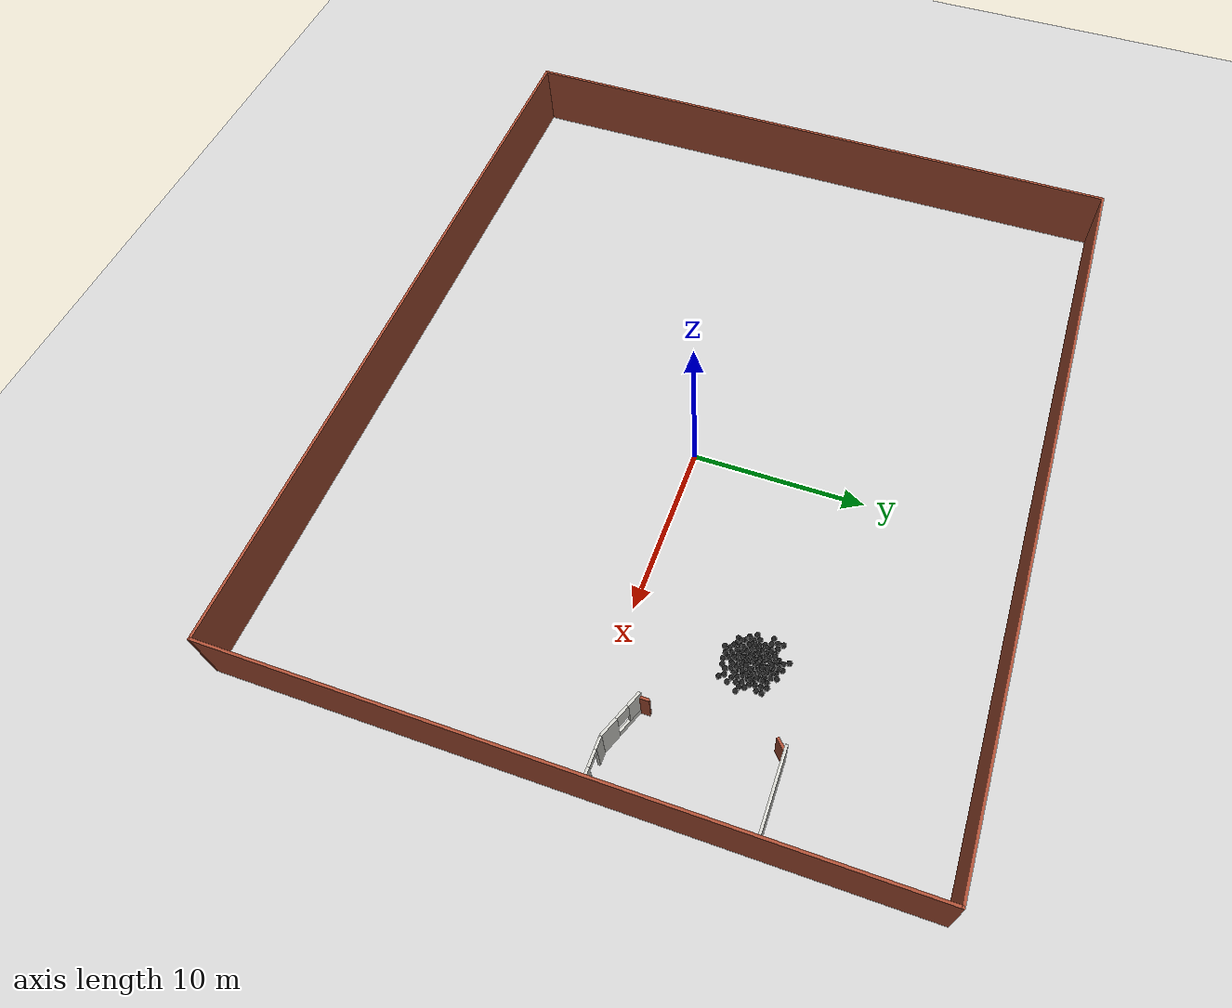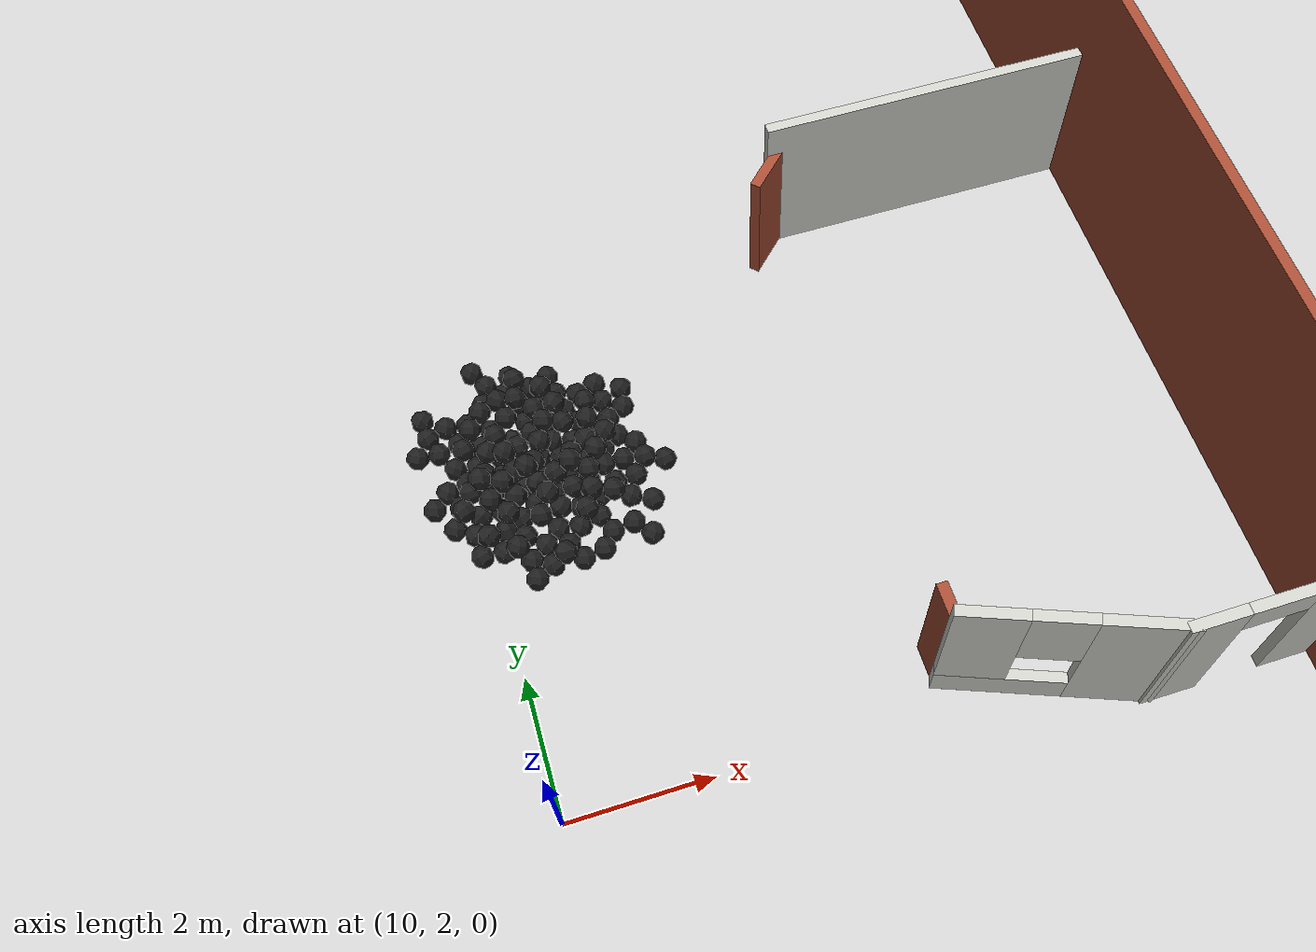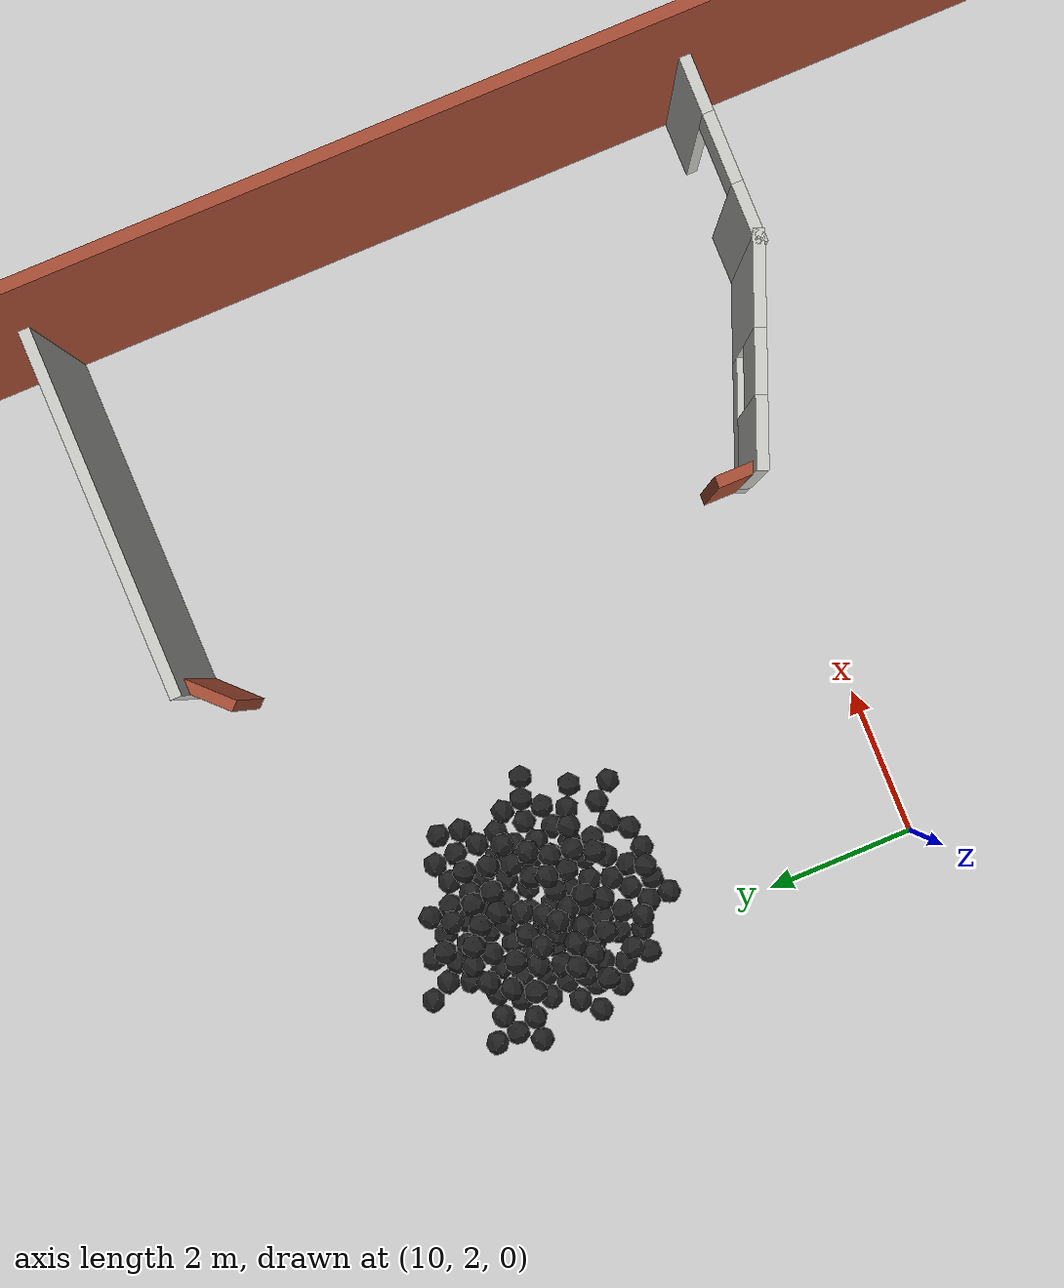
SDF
<sdf version="1.7">
 <world name="default">
  <light name="sun" type="directional">
   <pose>0 0 10 0 -0 0</pose>
   <diffuse>0.8 0.8 0.8 1</diffuse>
   <specular>0.2 0.2 0.2 1</specular>
   <attenuation>
    <range>1000</range>
    <constant>0.9</constant>
    <linear>0.01</linear>
    <quadratic>0.001</quadratic>
   </attenuation>
   <direction>-0.5 0.1 -0.9</direction>
   <spot><inner_angle>0</inner_angle><outer_angle>0</outer_angle><falloff>0</falloff></spot>
  </light>
  <model name="ground_plane">
   <static>1</static>
   <link name="link">
    <collision name="collision">
     <geometry><plane><normal>0 0 1</normal><size>100 100</size></plane></geometry>
     <surface><friction><ode><mu>100</mu><mu2>50</mu2></ode></friction></surface>
    </collision>
    <visual name="visual">
     <cast_shadows>0</cast_shadows>
     <geometry><plane><normal>0 0 1</normal><size>100 100</size></plane></geometry>
     <material>
      <script><uri>file://media/materials/scripts/gazebo.material</uri><name>Gazebo/Grey</name></script>
     </material>
    </visual>
   </link>
  </model>
  <gravity>0 0 -9.8</gravity>
  <magnetic_field>6e-06 2.3e-05 -4.2e-05</magnetic_field>
  <atmosphere type="adiabatic"/>
  <physics name="default_physics" default="0" type="ode">
   <max_step_size>0.001</max_step_size>
   <real_time_factor>1</real_time_factor>
   <real_time_update_rate>1000</real_time_update_rate>
  </physics>
  <scene><ambient>0.4 0.4 0.4 1</ambient><background>0.7 0.7 0.7 1</background><shadows>1</shadows></scene>
  <audio><device>default</device></audio>
  <spherical_coordinates>
   <surface_model>EARTH_WGS84</surface_model>
   <latitude_deg>0</latitude_deg>
   <longitude_deg>0</longitude_deg>
   <elevation>0</elevation>
   <heading_deg>0</heading_deg>
  </spherical_coordinates>
  <model name="wall11">
   <pose>-2 -0.019571 0 0 -0 0</pose>
   <link name="Wall_0">
    <collision name="Wall_0_Collision">
     <geometry><box><size>44.15 0.15 4</size></box></geometry>
     <pose>0 0 2 0 -0 0</pose>
    </collision>
    <visual name="Wall_0_Visual">
     <pose>0 0 2 0 -0 0</pose>
     <geometry><box><size>44.15 0.15 4</size></box></geometry>
     <material>
      <script><uri>file://media/materials/scripts/gazebo.material</uri><name>Gazebo/Bricks</name></script>
      <ambient>1 1 1 1</ambient>
     </material>
     <meta><layer>0</layer></meta>
    </visual>
    <pose>0 19 0 0 -0 0</pose>
   </link>
   <link name="Wall_2">
    <collision name="Wall_2_Collision">
     <geometry><box><size>38.15 0.15 4</size></box></geometry>
     <pose>0 0 2 0 -0 0</pose>
    </collision>
    <visual name="Wall_2_Visual">
     <pose>0 0 2 0 -0 0</pose>
     <geometry><box><size>38.15 0.15 4</size></box></geometry>
     <material>
      <script><uri>file://media/materials/scripts/gazebo.material</uri><name>Gazebo/Bricks</name></script>
      <ambient>1 1 1 1</ambient>
     </material>
     <meta><layer>0</layer></meta>
    </visual>
    <pose>22 0 0 0 -0 -1.5708</pose>
   </link>
   <link name="Wall_4">
    <collision name="Wall_4_Collision">
     <geometry><box><size>44.15 0.15 4</size></box></geometry>
     <pose>0 0 2 0 -0 0</pose>
    </collision>
    <visual name="Wall_4_Visual">
     <pose>0 0 2 0 -0 0</pose>
     <geometry><box><size>44.15 0.15 4</size></box></geometry>
     <material>
      <script><uri>file://media/materials/scripts/gazebo.material</uri><name>Gazebo/Bricks</name></script>
      <ambient>1 1 1 1</ambient>
     </material>
     <meta><layer>0</layer></meta>
    </visual>
    <pose>0 -19 0 0 -0 3.14159</pose>
   </link>
   <link name="Wall_6">
    <collision name="Wall_6_Collision">
     <geometry><box><size>38.15 0.15 4</size></box></geometry>
     <pose>0 0 2 0 -0 0</pose>
    </collision>
    <visual name="Wall_6_Visual">
     <pose>0 0 2 0 -0 0</pose>
     <geometry><box><size>38.15 0.15 4</size></box></geometry>
     <material>
      <script><uri>file://media/materials/scripts/gazebo.material</uri><name>Gazebo/Bricks</name></script>
      <ambient>1 1 1 1</ambient>
     </material>
     <meta><layer>0</layer></meta>
    </visual>
    <pose>-22 0 0 0 -0 1.5708</pose>
   </link>
   <static>1</static>
  </model>
  <model name="haoduomiantiaa_0">
   <link name="link_0">
    <inertial>
     <mass>0.2</mass>
     <inertia>
      <ixx>0.166667</ixx>
      <ixy>0</ixy>
      <ixz>0</ixz>
      <iyy>0.166667</iyy>
      <iyz>0</iyz>
      <izz>0.166667</izz>
     </inertia>
    </inertial>
    <visual name="visual">
     <geometry>
      <mesh>
       <uri>/home/lihaoyang/catkin_ws/src/pudong_gazebo/world/stl/haoduomianti.stl</uri>
       <scale>1 1 1</scale>
      </mesh>
     </geometry>
     <material>
      <lighting>1</lighting>
      <script><uri>file://media/materials/scripts/gazebo.material</uri><name>Gazebo/Black</name></script>
      <shader type="pixel"><normal_map>__default__</normal_map></shader>
      <ambient>0.3 0.3 0.3 1</ambient>
      <diffuse>0.7 0.7 0.7 1</diffuse>
      <specular>0.01 0.01 0.01 1</specular>
      <emissive>0 0 0 1</emissive>
     </material>
    </visual>
    <collision name="collision">
     <geometry>
      <mesh>
       <uri>/home/lihaoyang/catkin_ws/src/pudong_gazebo/world/stl/haoduomianti.stl</uri>
       <scale>1 1 1</scale>
      </mesh>
     </geometry>
     <surface>
      <friction>
       <ode><mu>1</mu><mu2>1</mu2><fdir1>0 0 0</fdir1><slip1>0</slip1><slip2>0</slip2></ode>
       <torsional>
        <coefficient>1</coefficient>
        <patch_radius>0</patch_radius>
        <surface_radius>0</surface_radius>
        <use_patch_radius>1</use_patch_radius>
        <ode><slip>0</slip></ode>
       </torsional>
      </friction>
      <bounce><restitution_coefficient>0</restitution_coefficient><threshold>1e+06</threshold></bounce>
      <contact>
       <collide_without_contact>0</collide_without_contact>
       <collide_without_contact_bitmask>1</collide_without_contact_bitmask>
       <collide_bitmask>1</collide_bitmask>
       <ode>
        <soft_cfm>0</soft_cfm>
        <soft_erp>0.2</soft_erp>
        <kp>1e+13</kp>
        <kd>1</kd>
        <max_vel>0.01</max_vel>
        <min_depth>0</min_depth>
       </ode>
       <bullet>
        <split_impulse>1</split_impulse>
        <split_impulse_penetration_threshold>-0.01</split_impulse_penetration_threshold>
        <soft_cfm>0</soft_cfm>
        <soft_erp>0.2</soft_erp>
        <kp>1e+13</kp>
        <kd>1</kd>
       </bullet>
      </contact>
     </surface>
    </collision>
   </link>
   <static>0</static>
   <pose>10.9723 7.07498 -0.114445 0.785431 -0.589548 -1.48621</pose>
  </model>
  <model name="haoduomiantiaa_1">
   <link name="link_0">
    <inertial>
     <mass>0.2</mass>
     <inertia>
      <ixx>0.166667</ixx>
      <ixy>0</ixy>
      <ixz>0</ixz>
      <iyy>0.166667</iyy>
      <iyz>0</iyz>
      <izz>0.166667</izz>
     </inertia>
    </inertial>
    <visual name="visual">
     <geometry>
      <mesh>
       <uri>/home/lihaoyang/catkin_ws/src/pudong_gazebo/world/stl/haoduomianti.stl</uri>
       <scale>1 1 1</scale>
      </mesh>
     </geometry>
     <material>
      <lighting>1</lighting>
      <script><uri>file://media/materials/scripts/gazebo.material</uri><name>Gazebo/Black</name></script>
      <shader type="pixel"><normal_map>__default__</normal_map></shader>
      <ambient>0.3 0.3 0.3 1</ambient>
      <diffuse>0.7 0.7 0.7 1</diffuse>
      <specular>0.01 0.01 0.01 1</specular>
      <emissive>0 0 0 1</emissive>
     </material>
    </visual>
    <collision name="collision">
     <geometry>
      <mesh>
       <uri>/home/lihaoyang/catkin_ws/src/pudong_gazebo/world/stl/haoduomianti.stl</uri>
       <scale>1 1 1</scale>
      </mesh>
     </geometry>
     <surface>
      <friction>
       <ode><mu>1</mu><mu2>1</mu2><fdir1>0 0 0</fdir1><slip1>0</slip1><slip2>0</slip2></ode>
       <torsional>
        <coefficient>1</coefficient>
        <patch_radius>0</patch_radius>
        <surface_radius>0</surface_radius>
        <use_patch_radius>1</use_patch_radius>
        <ode><slip>0</slip></ode>
       </torsional>
      </friction>
      <bounce><restitution_coefficient>0</restitution_coefficient><threshold>1e+06</threshold></bounce>
      <contact>
       <collide_without_contact>0</collide_without_contact>
       <collide_without_contact_bitmask>1</collide_without_contact_bitmask>
       <collide_bitmask>1</collide_bitmask>
       <ode>
        <soft_cfm>0</soft_cfm>
        <soft_erp>0.2</soft_erp>
        <kp>1e+13</kp>
        <kd>1</kd>
        <max_vel>0.01</max_vel>
        <min_depth>0</min_depth>
       </ode>
       <bullet>
        <split_impulse>1</split_impulse>
        <split_impulse_penetration_threshold>-0.01</split_impulse_penetration_threshold>
        <soft_cfm>0</soft_cfm>
        <soft_erp>0.2</soft_erp>
        <kp>1e+13</kp>
        <kd>1</kd>
       </bullet>
      </contact>
     </surface>
    </collision>
   </link>
   <static>0</static>
   <pose>10.6585 6.68021 -0.115759 0.785362 -0.615601 0.746121</pose>
  </model>
  <model name="haoduomiantiaa_2">
   <link name="link_0">
    <inertial>
     <mass>0.2</mass>
     <inertia>
      <ixx>0.166667</ixx>
      <ixy>0</ixy>
      <ixz>0</ixz>
      <iyy>0.166667</iyy>
      <iyz>0</iyz>
      <izz>0.166667</izz>
     </inertia>
    </inertial>
    <visual name="visual">
     <geometry>
      <mesh>
       <uri>/home/lihaoyang/catkin_ws/src/pudong_gazebo/world/stl/haoduomianti.stl</uri>
       <scale>1 1 1</scale>
      </mesh>
     </geometry>
     <material>
      <lighting>1</lighting>
      <script><uri>file://media/materials/scripts/gazebo.material</uri><name>Gazebo/Black</name></script>
      <shader type="pixel"><normal_map>__default__</normal_map></shader>
      <ambient>0.3 0.3 0.3 1</ambient>
      <diffuse>0.7 0.7 0.7 1</diffuse>
      <specular>0.01 0.01 0.01 1</specular>
      <emissive>0 0 0 1</emissive>
     </material>
    </visual>
    <collision name="collision">
     <geometry>
      <mesh>
       <uri>/home/lihaoyang/catkin_ws/src/pudong_gazebo/world/stl/haoduomianti.stl</uri>
       <scale>1 1 1</scale>
      </mesh>
     </geometry>
     <surface>
      <friction>
       <ode><mu>1</mu><mu2>1</mu2><fdir1>0 0 0</fdir1><slip1>0</slip1><slip2>0</slip2></ode>
       <torsional>
        <coefficient>1</coefficient>
        <patch_radius>0</patch_radius>
        <surface_radius>0</surface_radius>
        <use_patch_radius>1</use_patch_radius>
        <ode><slip>0</slip></ode>
       </torsional>
      </friction>
      <bounce><restitution_coefficient>0</restitution_coefficient><threshold>1e+06</threshold></bounce>
      <contact>
       <collide_without_contact>0</collide_without_contact>
       <collide_without_contact_bitmask>1</collide_without_contact_bitmask>
       <collide_bitmask>1</collide_bitmask>
       <ode>
        <soft_cfm>0</soft_cfm>
        <soft_erp>0.2</soft_erp>
        <kp>1e+13</kp>
        <kd>1</kd>
        <max_vel>0.01</max_vel>
        <min_depth>0</min_depth>
       </ode>
       <bullet>
        <split_impulse>1</split_impulse>
        <split_impulse_penetration_threshold>-0.01</split_impulse_penetration_threshold>
        <soft_cfm>0</soft_cfm>
        <soft_erp>0.2</soft_erp>
        <kp>1e+13</kp>
        <kd>1</kd>
       </bullet>
      </contact>
     </surface>
    </collision>
   </link>
   <static>0</static>
   <pose>11.3927 7.29702 -0.074683 1.5149 -0.784614 0.669858</pose>
  </model>
  <model name="haoduomiantiaa_3">
   <link name="link_0">
    <inertial>
     <mass>0.2</mass>
     <inertia>
      <ixx>0.166667</ixx>
      <ixy>0</ixy>
      <ixz>0</ixz>
      <iyy>0.166667</iyy>
      <iyz>0</iyz>
      <izz>0.166667</izz>
     </inertia>
    </inertial>
    <visual name="visual">
     <geometry>
      <mesh>
       <uri>/home/lihaoyang/catkin_ws/src/pudong_gazebo/world/stl/haoduomianti.stl</uri>
       <scale>1 1 1</scale>
      </mesh>
     </geometry>
     <material>
      <lighting>1</lighting>
      <script><uri>file://media/materials/scripts/gazebo.material</uri><name>Gazebo/Black</name></script>
      <shader type="pixel"><normal_map>__default__</normal_map></shader>
      <ambient>0.3 0.3 0.3 1</ambient>
      <diffuse>0.7 0.7 0.7 1</diffuse>
      <specular>0.01 0.01 0.01 1</specular>
      <emissive>0 0 0 1</emissive>
     </material>
    </visual>
    <collision name="collision">
     <geometry>
      <mesh>
       <uri>/home/lihaoyang/catkin_ws/src/pudong_gazebo/world/stl/haoduomianti.stl</uri>
       <scale>1 1 1</scale>
      </mesh>
     </geometry>
     <surface>
      <friction>
       <ode><mu>1</mu><mu2>1</mu2><fdir1>0 0 0</fdir1><slip1>0</slip1><slip2>0</slip2></ode>
       <torsional>
        <coefficient>1</coefficient>
        <patch_radius>0</patch_radius>
        <surface_radius>0</surface_radius>
        <use_patch_radius>1</use_patch_radius>
        <ode><slip>0</slip></ode>
       </torsional>
      </friction>
      <bounce><restitution_coefficient>0</restitution_coefficient><threshold>1e+06</threshold></bounce>
      <contact>
       <collide_without_contact>0</collide_without_contact>
       <collide_without_contact_bitmask>1</collide_without_contact_bitmask>
       <collide_bitmask>1</collide_bitmask>
       <ode>
        <soft_cfm>0</soft_cfm>
        <soft_erp>0.2</soft_erp>
        <kp>1e+13</kp>
        <kd>1</kd>
        <max_vel>0.01</max_vel>
        <min_depth>0</min_depth>
       </ode>
       <bullet>
        <split_impulse>1</split_impulse>
        <split_impulse_penetration_threshold>-0.01</split_impulse_penetration_threshold>
        <soft_cfm>0</soft_cfm>
        <soft_erp>0.2</soft_erp>
        <kp>1e+13</kp>
        <kd>1</kd>
       </bullet>
      </contact>
     </surface>
    </collision>
   </link>
   <static>0</static>
   <pose>11.7701 6.44586 -0.075902 0.072575 -0.784094 -2.18516</pose>
  </model>
  <model name="haoduomiantiaa_4">
   <link name="link_0">
    <inertial>
     <mass>0.2</mass>
     <inertia>
      <ixx>0.166667</ixx>
      <ixy>0</ixy>
      <ixz>0</ixz>
      <iyy>0.166667</iyy>
      <iyz>0</iyz>
      <izz>0.166667</izz>
     </inertia>
    </inertial>
    <visual name="visual">
     <geometry>
      <mesh>
       <uri>/home/lihaoyang/catkin_ws/src/pudong_gazebo/world/stl/haoduomianti.stl</uri>
       <scale>1 1 1</scale>
      </mesh>
     </geometry>
     <material>
      <lighting>1</lighting>
      <script><uri>file://media/materials/scripts/gazebo.material</uri><name>Gazebo/Black</name></script>
      <shader type="pixel"><normal_map>__default__</normal_map></shader>
      <ambient>0.3 0.3 0.3 1</ambient>
      <diffuse>0.7 0.7 0.7 1</diffuse>
      <specular>0.01 0.01 0.01 1</specular>
      <emissive>0 0 0 1</emissive>
     </material>
    </visual>
    <collision name="collision">
     <geometry>
      <mesh>
       <uri>/home/lihaoyang/catkin_ws/src/pudong_gazebo/world/stl/haoduomianti.stl</uri>
       <scale>1 1 1</scale>
      </mesh>
     </geometry>
     <surface>
      <friction>
       <ode><mu>1</mu><mu2>1</mu2><fdir1>0 0 0</fdir1><slip1>0</slip1><slip2>0</slip2></ode>
       <torsional>
        <coefficient>1</coefficient>
        <patch_radius>0</patch_radius>
        <surface_radius>0</surface_radius>
        <use_patch_radius>1</use_patch_radius>
        <ode><slip>0</slip></ode>
       </torsional>
      </friction>
      <bounce><restitution_coefficient>0</restitution_coefficient><threshold>1e+06</threshold></bounce>
      <contact>
       <collide_without_contact>0</collide_without_contact>
       <collide_without_contact_bitmask>1</collide_without_contact_bitmask>
       <collide_bitmask>1</collide_bitmask>
       <ode>
        <soft_cfm>0</soft_cfm>
        <soft_erp>0.2</soft_erp>
        <kp>1e+13</kp>
        <kd>1</kd>
        <max_vel>0.01</max_vel>
        <min_depth>0</min_depth>
       </ode>
       <bullet>
        <split_impulse>1</split_impulse>
        <split_impulse_penetration_threshold>-0.01</split_impulse_penetration_threshold>
        <soft_cfm>0</soft_cfm>
        <soft_erp>0.2</soft_erp>
        <kp>1e+13</kp>
        <kd>1</kd>
       </bullet>
      </contact>
     </surface>
    </collision>
   </link>
   <static>0</static>
   <pose>11.785 7.21475 -0.115469 0.785389 -0.615474 0.495029</pose>
  </model>
  <model name="haoduomiantiaa_5">
   <link name="link_0">
    <inertial>
     <mass>0.2</mass>
     <inertia>
      <ixx>0.166667</ixx>
      <ixy>0</ixy>
      <ixz>0</ixz>
      <iyy>0.166667</iyy>
      <iyz>0</iyz>
      <izz>0.166667</izz>
     </inertia>
    </inertial>
    <visual name="visual">
     <geometry>
      <mesh>
       <uri>/home/lihaoyang/catkin_ws/src/pudong_gazebo/world/stl/haoduomianti.stl</uri>
       <scale>1 1 1</scale>
      </mesh>
     </geometry>
     <material>
      <lighting>1</lighting>
      <script><uri>file://media/materials/scripts/gazebo.material</uri><name>Gazebo/Black</name></script>
      <shader type="pixel"><normal_map>__default__</normal_map></shader>
      <ambient>0.3 0.3 0.3 1</ambient>
      <diffuse>0.7 0.7 0.7 1</diffuse>
      <specular>0.01 0.01 0.01 1</specular>
      <emissive>0 0 0 1</emissive>
     </material>
    </visual>
    <collision name="collision">
     <geometry>
      <mesh>
       <uri>/home/lihaoyang/catkin_ws/src/pudong_gazebo/world/stl/haoduomianti.stl</uri>
       <scale>1 1 1</scale>
      </mesh>
     </geometry>
     <surface>
      <friction>
       <ode><mu>1</mu><mu2>1</mu2><fdir1>0 0 0</fdir1><slip1>0</slip1><slip2>0</slip2></ode>
       <torsional>
        <coefficient>1</coefficient>
        <patch_radius>0</patch_radius>
        <surface_radius>0</surface_radius>
        <use_patch_radius>1</use_patch_radius>
        <ode><slip>0</slip></ode>
       </torsional>
      </friction>
      <bounce><restitution_coefficient>0</restitution_coefficient><threshold>1e+06</threshold></bounce>
      <contact>
       <collide_without_contact>0</collide_without_contact>
       <collide_without_contact_bitmask>1</collide_without_contact_bitmask>
       <collide_bitmask>1</collide_bitmask>
       <ode>
        <soft_cfm>0</soft_cfm>
        <soft_erp>0.2</soft_erp>
        <kp>1e+13</kp>
        <kd>1</kd>
        <max_vel>0.01</max_vel>
        <min_depth>0</min_depth>
       </ode>
       <bullet>
        <split_impulse>1</split_impulse>
        <split_impulse_penetration_threshold>-0.01</split_impulse_penetration_threshold>
        <soft_cfm>0</soft_cfm>
        <soft_erp>0.2</soft_erp>
        <kp>1e+13</kp>
        <kd>1</kd>
       </bullet>
      </contact>
     </surface>
    </collision>
   </link>
   <static>0</static>
   <pose>11.7319 6.96066 -0.080913 0.149535 -0.779782 -1.98773</pose>
  </model>
  <model name="haoduomiantiaa_6">
   <link name="link_0">
    <inertial>
     <mass>0.2</mass>
     <inertia>
      <ixx>0.166667</ixx>
      <ixy>0</ixy>
      <ixz>0</ixz>
      <iyy>0.166667</iyy>
      <iyz>0</iyz>
      <izz>0.166667</izz>
     </inertia>
    </inertial>
    <visual name="visual">
     <geometry>
      <mesh>
       <uri>/home/lihaoyang/catkin_ws/src/pudong_gazebo/world/stl/haoduomianti.stl</uri>
       <scale>1 1 1</scale>
      </mesh>
     </geometry>
     <material>
      <lighting>1</lighting>
      <script><uri>file://media/materials/scripts/gazebo.material</uri><name>Gazebo/Black</name></script>
      <shader type="pixel"><normal_map>__default__</normal_map></shader>
      <ambient>0.3 0.3 0.3 1</ambient>
      <diffuse>0.7 0.7 0.7 1</diffuse>
      <specular>0.01 0.01 0.01 1</specular>
      <emissive>0 0 0 1</emissive>
     </material>
    </visual>
    <collision name="collision">
     <geometry>
      <mesh>
       <uri>/home/lihaoyang/catkin_ws/src/pudong_gazebo/world/stl/haoduomianti.stl</uri>
       <scale>1 1 1</scale>
      </mesh>
     </geometry>
     <surface>
      <friction>
       <ode><mu>1</mu><mu2>1</mu2><fdir1>0 0 0</fdir1><slip1>0</slip1><slip2>0</slip2></ode>
       <torsional>
        <coefficient>1</coefficient>
        <patch_radius>0</patch_radius>
        <surface_radius>0</surface_radius>
        <use_patch_radius>1</use_patch_radius>
        <ode><slip>0</slip></ode>
       </torsional>
      </friction>
      <bounce><restitution_coefficient>0</restitution_coefficient><threshold>1e+06</threshold></bounce>
      <contact>
       <collide_without_contact>0</collide_without_contact>
       <collide_without_contact_bitmask>1</collide_without_contact_bitmask>
       <collide_bitmask>1</collide_bitmask>
       <ode>
        <soft_cfm>0</soft_cfm>
        <soft_erp>0.2</soft_erp>
        <kp>1e+13</kp>
        <kd>1</kd>
        <max_vel>0.01</max_vel>
        <min_depth>0</min_depth>
       </ode>
       <bullet>
        <split_impulse>1</split_impulse>
        <split_impulse_penetration_threshold>-0.01</split_impulse_penetration_threshold>
        <soft_cfm>0</soft_cfm>
        <soft_erp>0.2</soft_erp>
        <kp>1e+13</kp>
        <kd>1</kd>
       </bullet>
      </contact>
     </surface>
    </collision>
   </link>
   <static>0</static>
   <pose>10.7575 6.37025 -0.115475 0.785391 -0.615336 -0.993175</pose>
  </model>
  <model name="haoduomiantiaa_7">
   <link name="link_0">
    <inertial>
     <mass>0.2</mass>
     <inertia>
      <ixx>0.166667</ixx>
      <ixy>0</ixy>
      <ixz>0</ixz>
      <iyy>0.166667</iyy>
      <iyz>0</iyz>
      <izz>0.166667</izz>
     </inertia>
    </inertial>
    <visual name="visual">
     <geometry>
      <mesh>
       <uri>/home/lihaoyang/catkin_ws/src/pudong_gazebo/world/stl/haoduomianti.stl</uri>
       <scale>1 1 1</scale>
      </mesh>
     </geometry>
     <material>
      <lighting>1</lighting>
      <script><uri>file://media/materials/scripts/gazebo.material</uri><name>Gazebo/Black</name></script>
      <shader type="pixel"><normal_map>__default__</normal_map></shader>
      <ambient>0.3 0.3 0.3 1</ambient>
      <diffuse>0.7 0.7 0.7 1</diffuse>
      <specular>0.01 0.01 0.01 1</specular>
      <emissive>0 0 0 1</emissive>
     </material>
    </visual>
    <collision name="collision">
     <geometry>
      <mesh>
       <uri>/home/lihaoyang/catkin_ws/src/pudong_gazebo/world/stl/haoduomianti.stl</uri>
       <scale>1 1 1</scale>
      </mesh>
     </geometry>
     <surface>
      <friction>
       <ode><mu>1</mu><mu2>1</mu2><fdir1>0 0 0</fdir1><slip1>0</slip1><slip2>0</slip2></ode>
       <torsional>
        <coefficient>1</coefficient>
        <patch_radius>0</patch_radius>
        <surface_radius>0</surface_radius>
        <use_patch_radius>1</use_patch_radius>
        <ode><slip>0</slip></ode>
       </torsional>
      </friction>
      <bounce><restitution_coefficient>0</restitution_coefficient><threshold>1e+06</threshold></bounce>
      <contact>
       <collide_without_contact>0</collide_without_contact>
       <collide_without_contact_bitmask>1</collide_without_contact_bitmask>
       <collide_bitmask>1</collide_bitmask>
       <ode>
        <soft_cfm>0</soft_cfm>
        <soft_erp>0.2</soft_erp>
        <kp>1e+13</kp>
        <kd>1</kd>
        <max_vel>0.01</max_vel>
        <min_depth>0</min_depth>
       </ode>
       <bullet>
        <split_impulse>1</split_impulse>
        <split_impulse_penetration_threshold>-0.01</split_impulse_penetration_threshold>
        <soft_cfm>0</soft_cfm>
        <soft_erp>0.2</soft_erp>
        <kp>1e+13</kp>
        <kd>1</kd>
       </bullet>
      </contact>
     </surface>
    </collision>
   </link>
   <static>0</static>
   <pose>10.6943 6.98169 -0.115473 0.78544 -0.614761 -1.40075</pose>
  </model>
  <model name="haoduomiantiaa_8">
   <link name="link_0">
    <inertial>
     <mass>0.2</mass>
     <inertia>
      <ixx>0.166667</ixx>
      <ixy>0</ixy>
      <ixz>0</ixz>
      <iyy>0.166667</iyy>
      <iyz>0</iyz>
      <izz>0.166667</izz>
     </inertia>
    </inertial>
    <visual name="visual">
     <geometry>
      <mesh>
       <uri>/home/lihaoyang/catkin_ws/src/pudong_gazebo/world/stl/haoduomianti.stl</uri>
       <scale>1 1 1</scale>
      </mesh>
     </geometry>
     <material>
      <lighting>1</lighting>
      <script><uri>file://media/materials/scripts/gazebo.material</uri><name>Gazebo/Black</name></script>
      <shader type="pixel"><normal_map>__default__</normal_map></shader>
      <ambient>0.3 0.3 0.3 1</ambient>
      <diffuse>0.7 0.7 0.7 1</diffuse>
      <specular>0.01 0.01 0.01 1</specular>
      <emissive>0 0 0 1</emissive>
     </material>
    </visual>
    <collision name="collision">
     <geometry>
      <mesh>
       <uri>/home/lihaoyang/catkin_ws/src/pudong_gazebo/world/stl/haoduomianti.stl</uri>
       <scale>1 1 1</scale>
      </mesh>
     </geometry>
     <surface>
      <friction>
       <ode><mu>1</mu><mu2>1</mu2><fdir1>0 0 0</fdir1><slip1>0</slip1><slip2>0</slip2></ode>
       <torsional>
        <coefficient>1</coefficient>
        <patch_radius>0</patch_radius>
        <surface_radius>0</surface_radius>
        <use_patch_radius>1</use_patch_radius>
        <ode><slip>0</slip></ode>
       </torsional>
      </friction>
      <bounce><restitution_coefficient>0</restitution_coefficient><threshold>1e+06</threshold></bounce>
      <contact>
       <collide_without_contact>0</collide_without_contact>
       <collide_without_contact_bitmask>1</collide_without_contact_bitmask>
       <collide_bitmask>1</collide_bitmask>
       <ode>
        <soft_cfm>0</soft_cfm>
        <soft_erp>0.2</soft_erp>
        <kp>1e+13</kp>
        <kd>1</kd>
        <max_vel>0.01</max_vel>
        <min_depth>0</min_depth>
       </ode>
       <bullet>
        <split_impulse>1</split_impulse>
        <split_impulse_penetration_threshold>-0.01</split_impulse_penetration_threshold>
        <soft_cfm>0</soft_cfm>
        <soft_erp>0.2</soft_erp>
        <kp>1e+13</kp>
        <kd>1</kd>
       </bullet>
      </contact>
     </surface>
    </collision>
   </link>
   <static>0</static>
   <pose>11.5428 5.93414 -0.115347 0.785262 -0.61551 -2.32662</pose>
  </model>
  <model name="haoduomiantiaa_9">
   <link name="link_0">
    <inertial>
     <mass>0.2</mass>
     <inertia>
      <ixx>0.166667</ixx>
      <ixy>0</ixy>
      <ixz>0</ixz>
      <iyy>0.166667</iyy>
      <iyz>0</iyz>
      <izz>0.166667</izz>
     </inertia>
    </inertial>
    <visual name="visual">
     <geometry>
      <mesh>
       <uri>/home/lihaoyang/catkin_ws/src/pudong_gazebo/world/stl/haoduomianti.stl</uri>
       <scale>1 1 1</scale>
      </mesh>
     </geometry>
     <material>
      <lighting>1</lighting>
      <script><uri>file://media/materials/scripts/gazebo.material</uri><name>Gazebo/Black</name></script>
      <shader type="pixel"><normal_map>__default__</normal_map></shader>
      <ambient>0.3 0.3 0.3 1</ambient>
      <diffuse>0.7 0.7 0.7 1</diffuse>
      <specular>0.01 0.01 0.01 1</specular>
      <emissive>0 0 0 1</emissive>
     </material>
    </visual>
    <collision name="collision">
     <geometry>
      <mesh>
       <uri>/home/lihaoyang/catkin_ws/src/pudong_gazebo/world/stl/haoduomianti.stl</uri>
       <scale>1 1 1</scale>
      </mesh>
     </geometry>
     <surface>
      <friction>
       <ode><mu>1</mu><mu2>1</mu2><fdir1>0 0 0</fdir1><slip1>0</slip1><slip2>0</slip2></ode>
       <torsional>
        <coefficient>1</coefficient>
        <patch_radius>0</patch_radius>
        <surface_radius>0</surface_radius>
        <use_patch_radius>1</use_patch_radius>
        <ode><slip>0</slip></ode>
       </torsional>
      </friction>
      <bounce><restitution_coefficient>0</restitution_coefficient><threshold>1e+06</threshold></bounce>
      <contact>
       <collide_without_contact>0</collide_without_contact>
       <collide_without_contact_bitmask>1</collide_without_contact_bitmask>
       <collide_bitmask>1</collide_bitmask>
       <ode>
        <soft_cfm>0</soft_cfm>
        <soft_erp>0.2</soft_erp>
        <kp>1e+13</kp>
        <kd>1</kd>
        <max_vel>0.01</max_vel>
        <min_depth>0</min_depth>
       </ode>
       <bullet>
        <split_impulse>1</split_impulse>
        <split_impulse_penetration_threshold>-0.01</split_impulse_penetration_threshold>
        <soft_cfm>0</soft_cfm>
        <soft_erp>0.2</soft_erp>
        <kp>1e+13</kp>
        <kd>1</kd>
       </bullet>
      </contact>
     </surface>
    </collision>
   </link>
   <static>0</static>
   <pose>10.7993 7.38438 -0.073529 0.039666 -0.784944 1.19033</pose>
  </model>
  <model name="haoduomiantiaa_10">
   <link name="link_0">
    <inertial>
     <mass>0.2</mass>
     <inertia>
      <ixx>0.166667</ixx>
      <ixy>0</ixy>
      <ixz>0</ixz>
      <iyy>0.166667</iyy>
      <iyz>0</iyz>
      <izz>0.166667</izz>
     </inertia>
    </inertial>
    <visual name="visual">
     <geometry>
      <mesh>
       <uri>/home/lihaoyang/catkin_ws/src/pudong_gazebo/world/stl/haoduomianti.stl</uri>
       <scale>1 1 1</scale>
      </mesh>
     </geometry>
     <material>
      <lighting>1</lighting>
      <script><uri>file://media/materials/scripts/gazebo.material</uri><name>Gazebo/Black</name></script>
      <shader type="pixel"><normal_map>__default__</normal_map></shader>
      <ambient>0.3 0.3 0.3 1</ambient>
      <diffuse>0.7 0.7 0.7 1</diffuse>
      <specular>0.01 0.01 0.01 1</specular>
      <emissive>0 0 0 1</emissive>
     </material>
    </visual>
    <collision name="collision">
     <geometry>
      <mesh>
       <uri>/home/lihaoyang/catkin_ws/src/pudong_gazebo/world/stl/haoduomianti.stl</uri>
       <scale>1 1 1</scale>
      </mesh>
     </geometry>
     <surface>
      <friction>
       <ode><mu>1</mu><mu2>1</mu2><fdir1>0 0 0</fdir1><slip1>0</slip1><slip2>0</slip2></ode>
       <torsional>
        <coefficient>1</coefficient>
        <patch_radius>0</patch_radius>
        <surface_radius>0</surface_radius>
        <use_patch_radius>1</use_patch_radius>
        <ode><slip>0</slip></ode>
       </torsional>
      </friction>
      <bounce><restitution_coefficient>0</restitution_coefficient><threshold>1e+06</threshold></bounce>
      <contact>
       <collide_without_contact>0</collide_without_contact>
       <collide_without_contact_bitmask>1</collide_without_contact_bitmask>
       <collide_bitmask>1</collide_bitmask>
       <ode>
        <soft_cfm>0</soft_cfm>
        <soft_erp>0.2</soft_erp>
        <kp>1e+13</kp>
        <kd>1</kd>
        <max_vel>0.01</max_vel>
        <min_depth>0</min_depth>
       </ode>
       <bullet>
        <split_impulse>1</split_impulse>
        <split_impulse_penetration_threshold>-0.01</split_impulse_penetration_threshold>
        <soft_cfm>0</soft_cfm>
        <soft_erp>0.2</soft_erp>
        <kp>1e+13</kp>
        <kd>1</kd>
       </bullet>
      </contact>
     </surface>
    </collision>
   </link>
   <static>0</static>
   <pose>11.5636 6.93321 -0.092455 1.23758 -0.757109 0.176753</pose>
  </model>
  <model name="haoduomiantiaa_11">
   <link name="link_0">
    <inertial>
     <mass>0.2</mass>
     <inertia>
      <ixx>0.166667</ixx>
      <ixy>0</ixy>
      <ixz>0</ixz>
      <iyy>0.166667</iyy>
      <iyz>0</iyz>
      <izz>0.166667</izz>
     </inertia>
    </inertial>
    <visual name="visual">
     <geometry>
      <mesh>
       <uri>/home/lihaoyang/catkin_ws/src/pudong_gazebo/world/stl/haoduomianti.stl</uri>
       <scale>1 1 1</scale>
      </mesh>
     </geometry>
     <material>
      <lighting>1</lighting>
      <script><uri>file://media/materials/scripts/gazebo.material</uri><name>Gazebo/Black</name></script>
      <shader type="pixel"><normal_map>__default__</normal_map></shader>
      <ambient>0.3 0.3 0.3 1</ambient>
      <diffuse>0.7 0.7 0.7 1</diffuse>
      <specular>0.01 0.01 0.01 1</specular>
      <emissive>0 0 0 1</emissive>
     </material>
    </visual>
    <collision name="collision">
     <geometry>
      <mesh>
       <uri>/home/lihaoyang/catkin_ws/src/pudong_gazebo/world/stl/haoduomianti.stl</uri>
       <scale>1 1 1</scale>
      </mesh>
     </geometry>
     <surface>
      <friction>
       <ode><mu>1</mu><mu2>1</mu2><fdir1>0 0 0</fdir1><slip1>0</slip1><slip2>0</slip2></ode>
       <torsional>
        <coefficient>1</coefficient>
        <patch_radius>0</patch_radius>
        <surface_radius>0</surface_radius>
        <use_patch_radius>1</use_patch_radius>
        <ode><slip>0</slip></ode>
       </torsional>
      </friction>
      <bounce><restitution_coefficient>0</restitution_coefficient><threshold>1e+06</threshold></bounce>
      <contact>
       <collide_without_contact>0</collide_without_contact>
       <collide_without_contact_bitmask>1</collide_without_contact_bitmask>
       <collide_bitmask>1</collide_bitmask>
       <ode>
        <soft_cfm>0</soft_cfm>
        <soft_erp>0.2</soft_erp>
        <kp>1e+13</kp>
        <kd>1</kd>
        <max_vel>0.01</max_vel>
        <min_depth>0</min_depth>
       </ode>
       <bullet>
        <split_impulse>1</split_impulse>
        <split_impulse_penetration_threshold>-0.01</split_impulse_penetration_threshold>
        <soft_cfm>0</soft_cfm>
        <soft_erp>0.2</soft_erp>
        <kp>1e+13</kp>
        <kd>1</kd>
       </bullet>
      </contact>
     </surface>
    </collision>
   </link>
   <static>0</static>
   <pose>10.3108 7.37183 -0.074737 0.055494 -0.784628 0.711347</pose>
  </model>
  <model name="haoduomiantiaa_12">
   <link name="link_0">
    <inertial>
     <mass>0.2</mass>
     <inertia>
      <ixx>0.166667</ixx>
      <ixy>0</ixy>
      <ixz>0</ixz>
      <iyy>0.166667</iyy>
      <iyz>0</iyz>
      <izz>0.166667</izz>
     </inertia>
    </inertial>
    <visual name="visual">
     <geometry>
      <mesh>
       <uri>/home/lihaoyang/catkin_ws/src/pudong_gazebo/world/stl/haoduomianti.stl</uri>
       <scale>1 1 1</scale>
      </mesh>
     </geometry>
     <material>
      <lighting>1</lighting>
      <script><uri>file://media/materials/scripts/gazebo.material</uri><name>Gazebo/Black</name></script>
      <shader type="pixel"><normal_map>__default__</normal_map></shader>
      <ambient>0.3 0.3 0.3 1</ambient>
      <diffuse>0.7 0.7 0.7 1</diffuse>
      <specular>0.01 0.01 0.01 1</specular>
      <emissive>0 0 0 1</emissive>
     </material>
    </visual>
    <collision name="collision">
     <geometry>
      <mesh>
       <uri>/home/lihaoyang/catkin_ws/src/pudong_gazebo/world/stl/haoduomianti.stl</uri>
       <scale>1 1 1</scale>
      </mesh>
     </geometry>
     <surface>
      <friction>
       <ode><mu>1</mu><mu2>1</mu2><fdir1>0 0 0</fdir1><slip1>0</slip1><slip2>0</slip2></ode>
       <torsional>
        <coefficient>1</coefficient>
        <patch_radius>0</patch_radius>
        <surface_radius>0</surface_radius>
        <use_patch_radius>1</use_patch_radius>
        <ode><slip>0</slip></ode>
       </torsional>
      </friction>
      <bounce><restitution_coefficient>0</restitution_coefficient><threshold>1e+06</threshold></bounce>
      <contact>
       <collide_without_contact>0</collide_without_contact>
       <collide_without_contact_bitmask>1</collide_without_contact_bitmask>
       <collide_bitmask>1</collide_bitmask>
       <ode>
        <soft_cfm>0</soft_cfm>
        <soft_erp>0.2</soft_erp>
        <kp>1e+13</kp>
        <kd>1</kd>
        <max_vel>0.01</max_vel>
        <min_depth>0</min_depth>
       </ode>
       <bullet>
        <split_impulse>1</split_impulse>
        <split_impulse_penetration_threshold>-0.01</split_impulse_penetration_threshold>
        <soft_cfm>0</soft_cfm>
        <soft_erp>0.2</soft_erp>
        <kp>1e+13</kp>
        <kd>1</kd>
       </bullet>
      </contact>
     </surface>
    </collision>
   </link>
   <static>0</static>
   <pose>10.9444 6.75933 -0.115547 0.78537 -0.615484 -1.28924</pose>
  </model>
  <model name="haoduomiantiaa_13">
   <link name="link_0">
    <inertial>
     <mass>0.2</mass>
     <inertia>
      <ixx>0.166667</ixx>
      <ixy>0</ixy>
      <ixz>0</ixz>
      <iyy>0.166667</iyy>
      <iyz>0</iyz>
      <izz>0.166667</izz>
     </inertia>
    </inertial>
    <visual name="visual">
     <geometry>
      <mesh>
       <uri>/home/lihaoyang/catkin_ws/src/pudong_gazebo/world/stl/haoduomianti.stl</uri>
       <scale>1 1 1</scale>
      </mesh>
     </geometry>
     <material>
      <lighting>1</lighting>
      <script><uri>file://media/materials/scripts/gazebo.material</uri><name>Gazebo/Black</name></script>
      <shader type="pixel"><normal_map>__default__</normal_map></shader>
      <ambient>0.3 0.3 0.3 1</ambient>
      <diffuse>0.7 0.7 0.7 1</diffuse>
      <specular>0.01 0.01 0.01 1</specular>
      <emissive>0 0 0 1</emissive>
     </material>
    </visual>
    <collision name="collision">
     <geometry>
      <mesh>
       <uri>/home/lihaoyang/catkin_ws/src/pudong_gazebo/world/stl/haoduomianti.stl</uri>
       <scale>1 1 1</scale>
      </mesh>
     </geometry>
     <surface>
      <friction>
       <ode><mu>1</mu><mu2>1</mu2><fdir1>0 0 0</fdir1><slip1>0</slip1><slip2>0</slip2></ode>
       <torsional>
        <coefficient>1</coefficient>
        <patch_radius>0</patch_radius>
        <surface_radius>0</surface_radius>
        <use_patch_radius>1</use_patch_radius>
        <ode><slip>0</slip></ode>
       </torsional>
      </friction>
      <bounce><restitution_coefficient>0</restitution_coefficient><threshold>1e+06</threshold></bounce>
      <contact>
       <collide_without_contact>0</collide_without_contact>
       <collide_without_contact_bitmask>1</collide_without_contact_bitmask>
       <collide_bitmask>1</collide_bitmask>
       <ode>
        <soft_cfm>0</soft_cfm>
        <soft_erp>0.2</soft_erp>
        <kp>1e+13</kp>
        <kd>1</kd>
        <max_vel>0.01</max_vel>
        <min_depth>0</min_depth>
       </ode>
       <bullet>
        <split_impulse>1</split_impulse>
        <split_impulse_penetration_threshold>-0.01</split_impulse_penetration_threshold>
        <soft_cfm>0</soft_cfm>
        <soft_erp>0.2</soft_erp>
        <kp>1e+13</kp>
        <kd>1</kd>
       </bullet>
      </contact>
     </surface>
    </collision>
   </link>
   <static>0</static>
   <pose>10.385 6.82157 -0.088707 1.29906 -0.76671 -3.09241</pose>
  </model>
  <model name="haoduomiantiaa_14">
   <link name="link_0">
    <inertial>
     <mass>0.2</mass>
     <inertia>
      <ixx>0.166667</ixx>
      <ixy>0</ixy>
      <ixz>0</ixz>
      <iyy>0.166667</iyy>
      <iyz>0</iyz>
      <izz>0.166667</izz>
     </inertia>
    </inertial>
    <visual name="visual">
     <geometry>
      <mesh>
       <uri>/home/lihaoyang/catkin_ws/src/pudong_gazebo/world/stl/haoduomianti.stl</uri>
       <scale>1 1 1</scale>
      </mesh>
     </geometry>
     <material>
      <lighting>1</lighting>
      <script><uri>file://media/materials/scripts/gazebo.material</uri><name>Gazebo/Black</name></script>
      <shader type="pixel"><normal_map>__default__</normal_map></shader>
      <ambient>0.3 0.3 0.3 1</ambient>
      <diffuse>0.7 0.7 0.7 1</diffuse>
      <specular>0.01 0.01 0.01 1</specular>
      <emissive>0 0 0 1</emissive>
     </material>
    </visual>
    <collision name="collision">
     <geometry>
      <mesh>
       <uri>/home/lihaoyang/catkin_ws/src/pudong_gazebo/world/stl/haoduomianti.stl</uri>
       <scale>1 1 1</scale>
      </mesh>
     </geometry>
     <surface>
      <friction>
       <ode><mu>1</mu><mu2>1</mu2><fdir1>0 0 0</fdir1><slip1>0</slip1><slip2>0</slip2></ode>
       <torsional>
        <coefficient>1</coefficient>
        <patch_radius>0</patch_radius>
        <surface_radius>0</surface_radius>
        <use_patch_radius>1</use_patch_radius>
        <ode><slip>0</slip></ode>
       </torsional>
      </friction>
      <bounce><restitution_coefficient>0</restitution_coefficient><threshold>1e+06</threshold></bounce>
      <contact>
       <collide_without_contact>0</collide_without_contact>
       <collide_without_contact_bitmask>1</collide_without_contact_bitmask>
       <collide_bitmask>1</collide_bitmask>
       <ode>
        <soft_cfm>0</soft_cfm>
        <soft_erp>0.2</soft_erp>
        <kp>1e+13</kp>
        <kd>1</kd>
        <max_vel>0.01</max_vel>
        <min_depth>0</min_depth>
       </ode>
       <bullet>
        <split_impulse>1</split_impulse>
        <split_impulse_penetration_threshold>-0.01</split_impulse_penetration_threshold>
        <soft_cfm>0</soft_cfm>
        <soft_erp>0.2</soft_erp>
        <kp>1e+13</kp>
        <kd>1</kd>
       </bullet>
      </contact>
     </surface>
    </collision>
   </link>
   <static>0</static>
   <pose>11.5437 6.52491 -0.115516 0.785438 -0.615586 -0.31702</pose>
  </model>
  <model name="haoduomiantiaa_15">
   <link name="link_0">
    <inertial>
     <mass>0.2</mass>
     <inertia>
      <ixx>0.166667</ixx>
      <ixy>0</ixy>
      <ixz>0</ixz>
      <iyy>0.166667</iyy>
      <iyz>0</iyz>
      <izz>0.166667</izz>
     </inertia>
    </inertial>
    <visual name="visual">
     <geometry>
      <mesh>
       <uri>/home/lihaoyang/catkin_ws/src/pudong_gazebo/world/stl/haoduomianti.stl</uri>
       <scale>1 1 1</scale>
      </mesh>
     </geometry>
     <material>
      <lighting>1</lighting>
      <script><uri>file://media/materials/scripts/gazebo.material</uri><name>Gazebo/Black</name></script>
      <shader type="pixel"><normal_map>__default__</normal_map></shader>
      <ambient>0.3 0.3 0.3 1</ambient>
      <diffuse>0.7 0.7 0.7 1</diffuse>
      <specular>0.01 0.01 0.01 1</specular>
      <emissive>0 0 0 1</emissive>
     </material>
    </visual>
    <collision name="collision">
     <geometry>
      <mesh>
       <uri>/home/lihaoyang/catkin_ws/src/pudong_gazebo/world/stl/haoduomianti.stl</uri>
       <scale>1 1 1</scale>
      </mesh>
     </geometry>
     <surface>
      <friction>
       <ode><mu>1</mu><mu2>1</mu2><fdir1>0 0 0</fdir1><slip1>0</slip1><slip2>0</slip2></ode>
       <torsional>
        <coefficient>1</coefficient>
        <patch_radius>0</patch_radius>
        <surface_radius>0</surface_radius>
        <use_patch_radius>1</use_patch_radius>
        <ode><slip>0</slip></ode>
       </torsional>
      </friction>
      <bounce><restitution_coefficient>0</restitution_coefficient><threshold>1e+06</threshold></bounce>
      <contact>
       <collide_without_contact>0</collide_without_contact>
       <collide_without_contact_bitmask>1</collide_without_contact_bitmask>
       <collide_bitmask>1</collide_bitmask>
       <ode>
        <soft_cfm>0</soft_cfm>
        <soft_erp>0.2</soft_erp>
        <kp>1e+13</kp>
        <kd>1</kd>
        <max_vel>0.01</max_vel>
        <min_depth>0</min_depth>
       </ode>
       <bullet>
        <split_impulse>1</split_impulse>
        <split_impulse_penetration_threshold>-0.01</split_impulse_penetration_threshold>
        <soft_cfm>0</soft_cfm>
        <soft_erp>0.2</soft_erp>
        <kp>1e+13</kp>
        <kd>1</kd>
       </bullet>
      </contact>
     </surface>
    </collision>
   </link>
   <static>0</static>
   <pose>10.5889 6.84123 0.108758 0.77447 -0.630052 0.728351</pose>
  </model>
  <model name="haoduomiantiaa_16">
   <link name="link_0">
    <inertial>
     <mass>0.2</mass>
     <inertia>
      <ixx>0.166667</ixx>
      <ixy>0</ixy>
      <ixz>0</ixz>
      <iyy>0.166667</iyy>
      <iyz>0</iyz>
      <izz>0.166667</izz>
     </inertia>
    </inertial>
    <visual name="visual">
     <geometry>
      <mesh>
       <uri>/home/lihaoyang/catkin_ws/src/pudong_gazebo/world/stl/haoduomianti.stl</uri>
       <scale>1 1 1</scale>
      </mesh>
     </geometry>
     <material>
      <lighting>1</lighting>
      <script><uri>file://media/materials/scripts/gazebo.material</uri><name>Gazebo/Black</name></script>
      <shader type="pixel"><normal_map>__default__</normal_map></shader>
      <ambient>0.3 0.3 0.3 1</ambient>
      <diffuse>0.7 0.7 0.7 1</diffuse>
      <specular>0.01 0.01 0.01 1</specular>
      <emissive>0 0 0 1</emissive>
     </material>
    </visual>
    <collision name="collision">
     <geometry>
      <mesh>
       <uri>/home/lihaoyang/catkin_ws/src/pudong_gazebo/world/stl/haoduomianti.stl</uri>
       <scale>1 1 1</scale>
      </mesh>
     </geometry>
     <surface>
      <friction>
       <ode><mu>1</mu><mu2>1</mu2><fdir1>0 0 0</fdir1><slip1>0</slip1><slip2>0</slip2></ode>
       <torsional>
        <coefficient>1</coefficient>
        <patch_radius>0</patch_radius>
        <surface_radius>0</surface_radius>
        <use_patch_radius>1</use_patch_radius>
        <ode><slip>0</slip></ode>
       </torsional>
      </friction>
      <bounce><restitution_coefficient>0</restitution_coefficient><threshold>1e+06</threshold></bounce>
      <contact>
       <collide_without_contact>0</collide_without_contact>
       <collide_without_contact_bitmask>1</collide_without_contact_bitmask>
       <collide_bitmask>1</collide_bitmask>
       <ode>
        <soft_cfm>0</soft_cfm>
        <soft_erp>0.2</soft_erp>
        <kp>1e+13</kp>
        <kd>1</kd>
        <max_vel>0.01</max_vel>
        <min_depth>0</min_depth>
       </ode>
       <bullet>
        <split_impulse>1</split_impulse>
        <split_impulse_penetration_threshold>-0.01</split_impulse_penetration_threshold>
        <soft_cfm>0</soft_cfm>
        <soft_erp>0.2</soft_erp>
        <kp>1e+13</kp>
        <kd>1</kd>
       </bullet>
      </contact>
     </surface>
    </collision>
   </link>
   <static>0</static>
   <pose>11.818 6.69765 0.005674 0.466409 -0.532404 -2.99413</pose>
  </model>
  <model name="haoduomiantiaa_17">
   <link name="link_0">
    <inertial>
     <mass>0.2</mass>
     <inertia>
      <ixx>0.166667</ixx>
      <ixy>0</ixy>
      <ixz>0</ixz>
      <iyy>0.166667</iyy>
      <iyz>0</iyz>
      <izz>0.166667</izz>
     </inertia>
    </inertial>
    <visual name="visual">
     <geometry>
      <mesh>
       <uri>/home/lihaoyang/catkin_ws/src/pudong_gazebo/world/stl/haoduomianti.stl</uri>
       <scale>1 1 1</scale>
      </mesh>
     </geometry>
     <material>
      <lighting>1</lighting>
      <script><uri>file://media/materials/scripts/gazebo.material</uri><name>Gazebo/Black</name></script>
      <shader type="pixel"><normal_map>__default__</normal_map></shader>
      <ambient>0.3 0.3 0.3 1</ambient>
      <diffuse>0.7 0.7 0.7 1</diffuse>
      <specular>0.01 0.01 0.01 1</specular>
      <emissive>0 0 0 1</emissive>
     </material>
    </visual>
    <collision name="collision">
     <geometry>
      <mesh>
       <uri>/home/lihaoyang/catkin_ws/src/pudong_gazebo/world/stl/haoduomianti.stl</uri>
       <scale>1 1 1</scale>
      </mesh>
     </geometry>
     <surface>
      <friction>
       <ode><mu>1</mu><mu2>1</mu2><fdir1>0 0 0</fdir1><slip1>0</slip1><slip2>0</slip2></ode>
       <torsional>
        <coefficient>1</coefficient>
        <patch_radius>0</patch_radius>
        <surface_radius>0</surface_radius>
        <use_patch_radius>1</use_patch_radius>
        <ode><slip>0</slip></ode>
       </torsional>
      </friction>
      <bounce><restitution_coefficient>0</restitution_coefficient><threshold>1e+06</threshold></bounce>
      <contact>
       <collide_without_contact>0</collide_without_contact>
       <collide_without_contact_bitmask>1</collide_without_contact_bitmask>
       <collide_bitmask>1</collide_bitmask>
       <ode>
        <soft_cfm>0</soft_cfm>
        <soft_erp>0.2</soft_erp>
        <kp>1e+13</kp>
        <kd>1</kd>
        <max_vel>0.01</max_vel>
        <min_depth>0</min_depth>
       </ode>
       <bullet>
        <split_impulse>1</split_impulse>
        <split_impulse_penetration_threshold>-0.01</split_impulse_penetration_threshold>
        <soft_cfm>0</soft_cfm>
        <soft_erp>0.2</soft_erp>
        <kp>1e+13</kp>
        <kd>1</kd>
       </bullet>
      </contact>
     </surface>
    </collision>
   </link>
   <static>0</static>
   <pose>10.9137 7.67298 -0.115967 0.785386 -0.615306 -0.458</pose>
  </model>
  <model name="haoduomiantiaa_18">
   <link name="link_0">
    <inertial>
     <mass>0.2</mass>
     <inertia>
      <ixx>0.166667</ixx>
      <ixy>0</ixy>
      <ixz>0</ixz>
      <iyy>0.166667</iyy>
      <iyz>0</iyz>
      <izz>0.166667</izz>
     </inertia>
    </inertial>
    <visual name="visual">
     <geometry>
      <mesh>
       <uri>/home/lihaoyang/catkin_ws/src/pudong_gazebo/world/stl/haoduomianti.stl</uri>
       <scale>1 1 1</scale>
      </mesh>
     </geometry>
     <material>
      <lighting>1</lighting>
      <script><uri>file://media/materials/scripts/gazebo.material</uri><name>Gazebo/Black</name></script>
      <shader type="pixel"><normal_map>__default__</normal_map></shader>
      <ambient>0.3 0.3 0.3 1</ambient>
      <diffuse>0.7 0.7 0.7 1</diffuse>
      <specular>0.01 0.01 0.01 1</specular>
      <emissive>0 0 0 1</emissive>
     </material>
    </visual>
    <collision name="collision">
     <geometry>
      <mesh>
       <uri>/home/lihaoyang/catkin_ws/src/pudong_gazebo/world/stl/haoduomianti.stl</uri>
       <scale>1 1 1</scale>
      </mesh>
     </geometry>
     <surface>
      <friction>
       <ode><mu>1</mu><mu2>1</mu2><fdir1>0 0 0</fdir1><slip1>0</slip1><slip2>0</slip2></ode>
       <torsional>
        <coefficient>1</coefficient>
        <patch_radius>0</patch_radius>
        <surface_radius>0</surface_radius>
        <use_patch_radius>1</use_patch_radius>
        <ode><slip>0</slip></ode>
       </torsional>
      </friction>
      <bounce><restitution_coefficient>0</restitution_coefficient><threshold>1e+06</threshold></bounce>
      <contact>
       <collide_without_contact>0</collide_without_contact>
       <collide_without_contact_bitmask>1</collide_without_contact_bitmask>
       <collide_bitmask>1</collide_bitmask>
       <ode>
        <soft_cfm>0</soft_cfm>
        <soft_erp>0.2</soft_erp>
        <kp>1e+13</kp>
        <kd>1</kd>
        <max_vel>0.01</max_vel>
        <min_depth>0</min_depth>
       </ode>
       <bullet>
        <split_impulse>1</split_impulse>
        <split_impulse_penetration_threshold>-0.01</split_impulse_penetration_threshold>
        <soft_cfm>0</soft_cfm>
        <soft_erp>0.2</soft_erp>
        <kp>1e+13</kp>
        <kd>1</kd>
       </bullet>
      </contact>
     </surface>
    </collision>
   </link>
   <static>0</static>
   <pose>11.1073 7.76353 -0.078327 0.1095 -0.782387 -0.480392</pose>
  </model>
  <model name="haoduomiantiaa_19">
   <link name="link_0">
    <inertial>
     <mass>0.2</mass>
     <inertia>
      <ixx>0.166667</ixx>
      <ixy>0</ixy>
      <ixz>0</ixz>
      <iyy>0.166667</iyy>
      <iyz>0</iyz>
      <izz>0.166667</izz>
     </inertia>
    </inertial>
    <visual name="visual">
     <geometry>
      <mesh>
       <uri>/home/lihaoyang/catkin_ws/src/pudong_gazebo/world/stl/haoduomianti.stl</uri>
       <scale>1 1 1</scale>
      </mesh>
     </geometry>
     <material>
      <lighting>1</lighting>
      <script><uri>file://media/materials/scripts/gazebo.material</uri><name>Gazebo/Black</name></script>
      <shader type="pixel"><normal_map>__default__</normal_map></shader>
      <ambient>0.3 0.3 0.3 1</ambient>
      <diffuse>0.7 0.7 0.7 1</diffuse>
      <specular>0.01 0.01 0.01 1</specular>
      <emissive>0 0 0 1</emissive>
     </material>
    </visual>
    <collision name="collision">
     <geometry>
      <mesh>
       <uri>/home/lihaoyang/catkin_ws/src/pudong_gazebo/world/stl/haoduomianti.stl</uri>
       <scale>1 1 1</scale>
      </mesh>
     </geometry>
     <surface>
      <friction>
       <ode><mu>1</mu><mu2>1</mu2><fdir1>0 0 0</fdir1><slip1>0</slip1><slip2>0</slip2></ode>
       <torsional>
        <coefficient>1</coefficient>
        <patch_radius>0</patch_radius>
        <surface_radius>0</surface_radius>
        <use_patch_radius>1</use_patch_radius>
        <ode><slip>0</slip></ode>
       </torsional>
      </friction>
      <bounce><restitution_coefficient>0</restitution_coefficient><threshold>1e+06</threshold></bounce>
      <contact>
       <collide_without_contact>0</collide_without_contact>
       <collide_without_contact_bitmask>1</collide_without_contact_bitmask>
       <collide_bitmask>1</collide_bitmask>
       <ode>
        <soft_cfm>0</soft_cfm>
        <soft_erp>0.2</soft_erp>
        <kp>1e+13</kp>
        <kd>1</kd>
        <max_vel>0.01</max_vel>
        <min_depth>0</min_depth>
       </ode>
       <bullet>
        <split_impulse>1</split_impulse>
        <split_impulse_penetration_threshold>-0.01</split_impulse_penetration_threshold>
        <soft_cfm>0</soft_cfm>
        <soft_erp>0.2</soft_erp>
        <kp>1e+13</kp>
        <kd>1</kd>
       </bullet>
      </contact>
     </surface>
    </collision>
   </link>
   <static>0</static>
   <pose>11.2537 5.85623 -0.115474 0.785399 -0.615345 -1.37989</pose>
  </model>
  <model name="haoduomiantiaa_20">
   <link name="link_0">
    <inertial>
     <mass>0.2</mass>
     <inertia>
      <ixx>0.166667</ixx>
      <ixy>0</ixy>
      <ixz>0</ixz>
      <iyy>0.166667</iyy>
      <iyz>0</iyz>
      <izz>0.166667</izz>
     </inertia>
    </inertial>
    <visual name="visual">
     <geometry>
      <mesh>
       <uri>/home/lihaoyang/catkin_ws/src/pudong_gazebo/world/stl/haoduomianti.stl</uri>
       <scale>1 1 1</scale>
      </mesh>
     </geometry>
     <material>
      <lighting>1</lighting>
      <script><uri>file://media/materials/scripts/gazebo.material</uri><name>Gazebo/Black</name></script>
      <shader type="pixel"><normal_map>__default__</normal_map></shader>
      <ambient>0.3 0.3 0.3 1</ambient>
      <diffuse>0.7 0.7 0.7 1</diffuse>
      <specular>0.01 0.01 0.01 1</specular>
      <emissive>0 0 0 1</emissive>
     </material>
    </visual>
    <collision name="collision">
     <geometry>
      <mesh>
       <uri>/home/lihaoyang/catkin_ws/src/pudong_gazebo/world/stl/haoduomianti.stl</uri>
       <scale>1 1 1</scale>
      </mesh>
     </geometry>
     <surface>
      <friction>
       <ode><mu>1</mu><mu2>1</mu2><fdir1>0 0 0</fdir1><slip1>0</slip1><slip2>0</slip2></ode>
       <torsional>
        <coefficient>1</coefficient>
        <patch_radius>0</patch_radius>
        <surface_radius>0</surface_radius>
        <use_patch_radius>1</use_patch_radius>
        <ode><slip>0</slip></ode>
       </torsional>
      </friction>
      <bounce><restitution_coefficient>0</restitution_coefficient><threshold>1e+06</threshold></bounce>
      <contact>
       <collide_without_contact>0</collide_without_contact>
       <collide_without_contact_bitmask>1</collide_without_contact_bitmask>
       <collide_bitmask>1</collide_bitmask>
       <ode>
        <soft_cfm>0</soft_cfm>
        <soft_erp>0.2</soft_erp>
        <kp>1e+13</kp>
        <kd>1</kd>
        <max_vel>0.01</max_vel>
        <min_depth>0</min_depth>
       </ode>
       <bullet>
        <split_impulse>1</split_impulse>
        <split_impulse_penetration_threshold>-0.01</split_impulse_penetration_threshold>
        <soft_cfm>0</soft_cfm>
        <soft_erp>0.2</soft_erp>
        <kp>1e+13</kp>
        <kd>1</kd>
       </bullet>
      </contact>
     </surface>
    </collision>
   </link>
   <static>0</static>
   <pose>10.902 7.96113 -0.04447 0.72085 -0.741952 -0.305091</pose>
  </model>
  <model name="haoduomiantiaa_21">
   <link name="link_0">
    <inertial>
     <mass>0.2</mass>
     <inertia>
      <ixx>0.166667</ixx>
      <ixy>0</ixy>
      <ixz>0</ixz>
      <iyy>0.166667</iyy>
      <iyz>0</iyz>
      <izz>0.166667</izz>
     </inertia>
    </inertial>
    <visual name="visual">
     <geometry>
      <mesh>
       <uri>/home/lihaoyang/catkin_ws/src/pudong_gazebo/world/stl/haoduomianti.stl</uri>
       <scale>1 1 1</scale>
      </mesh>
     </geometry>
     <material>
      <lighting>1</lighting>
      <script><uri>file://media/materials/scripts/gazebo.material</uri><name>Gazebo/Black</name></script>
      <shader type="pixel"><normal_map>__default__</normal_map></shader>
      <ambient>0.3 0.3 0.3 1</ambient>
      <diffuse>0.7 0.7 0.7 1</diffuse>
      <specular>0.01 0.01 0.01 1</specular>
      <emissive>0 0 0 1</emissive>
     </material>
    </visual>
    <collision name="collision">
     <geometry>
      <mesh>
       <uri>/home/lihaoyang/catkin_ws/src/pudong_gazebo/world/stl/haoduomianti.stl</uri>
       <scale>1 1 1</scale>
      </mesh>
     </geometry>
     <surface>
      <friction>
       <ode><mu>1</mu><mu2>1</mu2><fdir1>0 0 0</fdir1><slip1>0</slip1><slip2>0</slip2></ode>
       <torsional>
        <coefficient>1</coefficient>
        <patch_radius>0</patch_radius>
        <surface_radius>0</surface_radius>
        <use_patch_radius>1</use_patch_radius>
        <ode><slip>0</slip></ode>
       </torsional>
      </friction>
      <bounce><restitution_coefficient>0</restitution_coefficient><threshold>1e+06</threshold></bounce>
      <contact>
       <collide_without_contact>0</collide_without_contact>
       <collide_without_contact_bitmask>1</collide_without_contact_bitmask>
       <collide_bitmask>1</collide_bitmask>
       <ode>
        <soft_cfm>0</soft_cfm>
        <soft_erp>0.2</soft_erp>
        <kp>1e+13</kp>
        <kd>1</kd>
        <max_vel>0.01</max_vel>
        <min_depth>0</min_depth>
       </ode>
       <bullet>
        <split_impulse>1</split_impulse>
        <split_impulse_penetration_threshold>-0.01</split_impulse_penetration_threshold>
        <soft_cfm>0</soft_cfm>
        <soft_erp>0.2</soft_erp>
        <kp>1e+13</kp>
        <kd>1</kd>
       </bullet>
      </contact>
     </surface>
    </collision>
   </link>
   <static>0</static>
   <pose>10.6792 8.07566 -0.079109 1.44966 -0.781731 3.09453</pose>
  </model>
  <model name="haoduomiantiaa_22">
   <link name="link_0">
    <inertial>
     <mass>0.2</mass>
     <inertia>
      <ixx>0.166667</ixx>
      <ixy>0</ixy>
      <ixz>0</ixz>
      <iyy>0.166667</iyy>
      <iyz>0</iyz>
      <izz>0.166667</izz>
     </inertia>
    </inertial>
    <visual name="visual">
     <geometry>
      <mesh>
       <uri>/home/lihaoyang/catkin_ws/src/pudong_gazebo/world/stl/haoduomianti.stl</uri>
       <scale>1 1 1</scale>
      </mesh>
     </geometry>
     <material>
      <lighting>1</lighting>
      <script><uri>file://media/materials/scripts/gazebo.material</uri><name>Gazebo/Black</name></script>
      <shader type="pixel"><normal_map>__default__</normal_map></shader>
      <ambient>0.3 0.3 0.3 1</ambient>
      <diffuse>0.7 0.7 0.7 1</diffuse>
      <specular>0.01 0.01 0.01 1</specular>
      <emissive>0 0 0 1</emissive>
     </material>
    </visual>
    <collision name="collision">
     <geometry>
      <mesh>
       <uri>/home/lihaoyang/catkin_ws/src/pudong_gazebo/world/stl/haoduomianti.stl</uri>
       <scale>1 1 1</scale>
      </mesh>
     </geometry>
     <surface>
      <friction>
       <ode><mu>1</mu><mu2>1</mu2><fdir1>0 0 0</fdir1><slip1>0</slip1><slip2>0</slip2></ode>
       <torsional>
        <coefficient>1</coefficient>
        <patch_radius>0</patch_radius>
        <surface_radius>0</surface_radius>
        <use_patch_radius>1</use_patch_radius>
        <ode><slip>0</slip></ode>
       </torsional>
      </friction>
      <bounce><restitution_coefficient>0</restitution_coefficient><threshold>1e+06</threshold></bounce>
      <contact>
       <collide_without_contact>0</collide_without_contact>
       <collide_without_contact_bitmask>1</collide_without_contact_bitmask>
       <collide_bitmask>1</collide_bitmask>
       <ode>
        <soft_cfm>0</soft_cfm>
        <soft_erp>0.2</soft_erp>
        <kp>1e+13</kp>
        <kd>1</kd>
        <max_vel>0.01</max_vel>
        <min_depth>0</min_depth>
       </ode>
       <bullet>
        <split_impulse>1</split_impulse>
        <split_impulse_penetration_threshold>-0.01</split_impulse_penetration_threshold>
        <soft_cfm>0</soft_cfm>
        <soft_erp>0.2</soft_erp>
        <kp>1e+13</kp>
        <kd>1</kd>
       </bullet>
      </contact>
     </surface>
    </collision>
   </link>
   <static>0</static>
   <pose>12.0839 6.68664 -0.115573 0.785491 -0.615513 -0.822449</pose>
  </model>
  <model name="haoduomiantiaa_23">
   <link name="link_0">
    <inertial>
     <mass>0.2</mass>
     <inertia>
      <ixx>0.166667</ixx>
      <ixy>0</ixy>
      <ixz>0</ixz>
      <iyy>0.166667</iyy>
      <iyz>0</iyz>
      <izz>0.166667</izz>
     </inertia>
    </inertial>
    <visual name="visual">
     <geometry>
      <mesh>
       <uri>/home/lihaoyang/catkin_ws/src/pudong_gazebo/world/stl/haoduomianti.stl</uri>
       <scale>1 1 1</scale>
      </mesh>
     </geometry>
     <material>
      <lighting>1</lighting>
      <script><uri>file://media/materials/scripts/gazebo.material</uri><name>Gazebo/Black</name></script>
      <shader type="pixel"><normal_map>__default__</normal_map></shader>
      <ambient>0.3 0.3 0.3 1</ambient>
      <diffuse>0.7 0.7 0.7 1</diffuse>
      <specular>0.01 0.01 0.01 1</specular>
      <emissive>0 0 0 1</emissive>
     </material>
    </visual>
    <collision name="collision">
     <geometry>
      <mesh>
       <uri>/home/lihaoyang/catkin_ws/src/pudong_gazebo/world/stl/haoduomianti.stl</uri>
       <scale>1 1 1</scale>
      </mesh>
     </geometry>
     <surface>
      <friction>
       <ode><mu>1</mu><mu2>1</mu2><fdir1>0 0 0</fdir1><slip1>0</slip1><slip2>0</slip2></ode>
       <torsional>
        <coefficient>1</coefficient>
        <patch_radius>0</patch_radius>
        <surface_radius>0</surface_radius>
        <use_patch_radius>1</use_patch_radius>
        <ode><slip>0</slip></ode>
       </torsional>
      </friction>
      <bounce><restitution_coefficient>0</restitution_coefficient><threshold>1e+06</threshold></bounce>
      <contact>
       <collide_without_contact>0</collide_without_contact>
       <collide_without_contact_bitmask>1</collide_without_contact_bitmask>
       <collide_bitmask>1</collide_bitmask>
       <ode>
        <soft_cfm>0</soft_cfm>
        <soft_erp>0.2</soft_erp>
        <kp>1e+13</kp>
        <kd>1</kd>
        <max_vel>0.01</max_vel>
        <min_depth>0</min_depth>
       </ode>
       <bullet>
        <split_impulse>1</split_impulse>
        <split_impulse_penetration_threshold>-0.01</split_impulse_penetration_threshold>
        <soft_cfm>0</soft_cfm>
        <soft_erp>0.2</soft_erp>
        <kp>1e+13</kp>
        <kd>1</kd>
       </bullet>
      </contact>
     </surface>
    </collision>
   </link>
   <static>0</static>
   <pose>10.354 8.69849 -0.115479 0.785404 -0.615481 2.76349</pose>
  </model>
  <model name="haoduomiantiaa_24">
   <link name="link_0">
    <inertial>
     <mass>0.2</mass>
     <inertia>
      <ixx>0.166667</ixx>
      <ixy>0</ixy>
      <ixz>0</ixz>
      <iyy>0.166667</iyy>
      <iyz>0</iyz>
      <izz>0.166667</izz>
     </inertia>
    </inertial>
    <visual name="visual">
     <geometry>
      <mesh>
       <uri>/home/lihaoyang/catkin_ws/src/pudong_gazebo/world/stl/haoduomianti.stl</uri>
       <scale>1 1 1</scale>
      </mesh>
     </geometry>
     <material>
      <lighting>1</lighting>
      <script><uri>file://media/materials/scripts/gazebo.material</uri><name>Gazebo/Black</name></script>
      <shader type="pixel"><normal_map>__default__</normal_map></shader>
      <ambient>0.3 0.3 0.3 1</ambient>
      <diffuse>0.7 0.7 0.7 1</diffuse>
      <specular>0.01 0.01 0.01 1</specular>
      <emissive>0 0 0 1</emissive>
     </material>
    </visual>
    <collision name="collision">
     <geometry>
      <mesh>
       <uri>/home/lihaoyang/catkin_ws/src/pudong_gazebo/world/stl/haoduomianti.stl</uri>
       <scale>1 1 1</scale>
      </mesh>
     </geometry>
     <surface>
      <friction>
       <ode><mu>1</mu><mu2>1</mu2><fdir1>0 0 0</fdir1><slip1>0</slip1><slip2>0</slip2></ode>
       <torsional>
        <coefficient>1</coefficient>
        <patch_radius>0</patch_radius>
        <surface_radius>0</surface_radius>
        <use_patch_radius>1</use_patch_radius>
        <ode><slip>0</slip></ode>
       </torsional>
      </friction>
      <bounce><restitution_coefficient>0</restitution_coefficient><threshold>1e+06</threshold></bounce>
      <contact>
       <collide_without_contact>0</collide_without_contact>
       <collide_without_contact_bitmask>1</collide_without_contact_bitmask>
       <collide_bitmask>1</collide_bitmask>
       <ode>
        <soft_cfm>0</soft_cfm>
        <soft_erp>0.2</soft_erp>
        <kp>1e+13</kp>
        <kd>1</kd>
        <max_vel>0.01</max_vel>
        <min_depth>0</min_depth>
       </ode>
       <bullet>
        <split_impulse>1</split_impulse>
        <split_impulse_penetration_threshold>-0.01</split_impulse_penetration_threshold>
        <soft_cfm>0</soft_cfm>
        <soft_erp>0.2</soft_erp>
        <kp>1e+13</kp>
        <kd>1</kd>
       </bullet>
      </contact>
     </surface>
    </collision>
   </link>
   <static>0</static>
   <pose>12.3166 6.89924 -0.115555 0.785363 -0.615473 -1.08795</pose>
  </model>
  <model name="haoduomiantiaa_25">
   <link name="link_0">
    <inertial>
     <mass>0.2</mass>
     <inertia>
      <ixx>0.166667</ixx>
      <ixy>0</ixy>
      <ixz>0</ixz>
      <iyy>0.166667</iyy>
      <iyz>0</iyz>
      <izz>0.166667</izz>
     </inertia>
    </inertial>
    <visual name="visual">
     <geometry>
      <mesh>
       <uri>/home/lihaoyang/catkin_ws/src/pudong_gazebo/world/stl/haoduomianti.stl</uri>
       <scale>1 1 1</scale>
      </mesh>
     </geometry>
     <material>
      <lighting>1</lighting>
      <script><uri>file://media/materials/scripts/gazebo.material</uri><name>Gazebo/Black</name></script>
      <shader type="pixel"><normal_map>__default__</normal_map></shader>
      <ambient>0.3 0.3 0.3 1</ambient>
      <diffuse>0.7 0.7 0.7 1</diffuse>
      <specular>0.01 0.01 0.01 1</specular>
      <emissive>0 0 0 1</emissive>
     </material>
    </visual>
    <collision name="collision">
     <geometry>
      <mesh>
       <uri>/home/lihaoyang/catkin_ws/src/pudong_gazebo/world/stl/haoduomianti.stl</uri>
       <scale>1 1 1</scale>
      </mesh>
     </geometry>
     <surface>
      <friction>
       <ode><mu>1</mu><mu2>1</mu2><fdir1>0 0 0</fdir1><slip1>0</slip1><slip2>0</slip2></ode>
       <torsional>
        <coefficient>1</coefficient>
        <patch_radius>0</patch_radius>
        <surface_radius>0</surface_radius>
        <use_patch_radius>1</use_patch_radius>
        <ode><slip>0</slip></ode>
       </torsional>
      </friction>
      <bounce><restitution_coefficient>0</restitution_coefficient><threshold>1e+06</threshold></bounce>
      <contact>
       <collide_without_contact>0</collide_without_contact>
       <collide_without_contact_bitmask>1</collide_without_contact_bitmask>
       <collide_bitmask>1</collide_bitmask>
       <ode>
        <soft_cfm>0</soft_cfm>
        <soft_erp>0.2</soft_erp>
        <kp>1e+13</kp>
        <kd>1</kd>
        <max_vel>0.01</max_vel>
        <min_depth>0</min_depth>
       </ode>
       <bullet>
        <split_impulse>1</split_impulse>
        <split_impulse_penetration_threshold>-0.01</split_impulse_penetration_threshold>
        <soft_cfm>0</soft_cfm>
        <soft_erp>0.2</soft_erp>
        <kp>1e+13</kp>
        <kd>1</kd>
       </bullet>
      </contact>
     </surface>
    </collision>
   </link>
   <static>0</static>
   <pose>11.1221 8.16661 -0.106418 0.785399 -0.437494 1.99127</pose>
  </model>
  <model name="haoduomiantiaa_26">
   <link name="link_0">
    <inertial>
     <mass>0.2</mass>
     <inertia>
      <ixx>0.166667</ixx>
      <ixy>0</ixy>
      <ixz>0</ixz>
      <iyy>0.166667</iyy>
      <iyz>0</iyz>
      <izz>0.166667</izz>
     </inertia>
    </inertial>
    <visual name="visual">
     <geometry>
      <mesh>
       <uri>/home/lihaoyang/catkin_ws/src/pudong_gazebo/world/stl/haoduomianti.stl</uri>
       <scale>1 1 1</scale>
      </mesh>
     </geometry>
     <material>
      <lighting>1</lighting>
      <script><uri>file://media/materials/scripts/gazebo.material</uri><name>Gazebo/Black</name></script>
      <shader type="pixel"><normal_map>__default__</normal_map></shader>
      <ambient>0.3 0.3 0.3 1</ambient>
      <diffuse>0.7 0.7 0.7 1</diffuse>
      <specular>0.01 0.01 0.01 1</specular>
      <emissive>0 0 0 1</emissive>
     </material>
    </visual>
    <collision name="collision">
     <geometry>
      <mesh>
       <uri>/home/lihaoyang/catkin_ws/src/pudong_gazebo/world/stl/haoduomianti.stl</uri>
       <scale>1 1 1</scale>
      </mesh>
     </geometry>
     <surface>
      <friction>
       <ode><mu>1</mu><mu2>1</mu2><fdir1>0 0 0</fdir1><slip1>0</slip1><slip2>0</slip2></ode>
       <torsional>
        <coefficient>1</coefficient>
        <patch_radius>0</patch_radius>
        <surface_radius>0</surface_radius>
        <use_patch_radius>1</use_patch_radius>
        <ode><slip>0</slip></ode>
       </torsional>
      </friction>
      <bounce><restitution_coefficient>0</restitution_coefficient><threshold>1e+06</threshold></bounce>
      <contact>
       <collide_without_contact>0</collide_without_contact>
       <collide_without_contact_bitmask>1</collide_without_contact_bitmask>
       <collide_bitmask>1</collide_bitmask>
       <ode>
        <soft_cfm>0</soft_cfm>
        <soft_erp>0.2</soft_erp>
        <kp>1e+13</kp>
        <kd>1</kd>
        <max_vel>0.01</max_vel>
        <min_depth>0</min_depth>
       </ode>
       <bullet>
        <split_impulse>1</split_impulse>
        <split_impulse_penetration_threshold>-0.01</split_impulse_penetration_threshold>
        <soft_cfm>0</soft_cfm>
        <soft_erp>0.2</soft_erp>
        <kp>1e+13</kp>
        <kd>1</kd>
       </bullet>
      </contact>
     </surface>
    </collision>
   </link>
   <static>0</static>
   <pose>11.3405 6.13184 -0.115393 0.784571 -0.615821 1.86249</pose>
  </model>
  <model name="haoduomiantiaa_27">
   <link name="link_0">
    <inertial>
     <mass>0.2</mass>
     <inertia>
      <ixx>0.166667</ixx>
      <ixy>0</ixy>
      <ixz>0</ixz>
      <iyy>0.166667</iyy>
      <iyz>0</iyz>
      <izz>0.166667</izz>
     </inertia>
    </inertial>
    <visual name="visual">
     <geometry>
      <mesh>
       <uri>/home/lihaoyang/catkin_ws/src/pudong_gazebo/world/stl/haoduomianti.stl</uri>
       <scale>1 1 1</scale>
      </mesh>
     </geometry>
     <material>
      <lighting>1</lighting>
      <script><uri>file://media/materials/scripts/gazebo.material</uri><name>Gazebo/Black</name></script>
      <shader type="pixel"><normal_map>__default__</normal_map></shader>
      <ambient>0.3 0.3 0.3 1</ambient>
      <diffuse>0.7 0.7 0.7 1</diffuse>
      <specular>0.01 0.01 0.01 1</specular>
      <emissive>0 0 0 1</emissive>
     </material>
    </visual>
    <collision name="collision">
     <geometry>
      <mesh>
       <uri>/home/lihaoyang/catkin_ws/src/pudong_gazebo/world/stl/haoduomianti.stl</uri>
       <scale>1 1 1</scale>
      </mesh>
     </geometry>
     <surface>
      <friction>
       <ode><mu>1</mu><mu2>1</mu2><fdir1>0 0 0</fdir1><slip1>0</slip1><slip2>0</slip2></ode>
       <torsional>
        <coefficient>1</coefficient>
        <patch_radius>0</patch_radius>
        <surface_radius>0</surface_radius>
        <use_patch_radius>1</use_patch_radius>
        <ode><slip>0</slip></ode>
       </torsional>
      </friction>
      <bounce><restitution_coefficient>0</restitution_coefficient><threshold>1e+06</threshold></bounce>
      <contact>
       <collide_without_contact>0</collide_without_contact>
       <collide_without_contact_bitmask>1</collide_without_contact_bitmask>
       <collide_bitmask>1</collide_bitmask>
       <ode>
        <soft_cfm>0</soft_cfm>
        <soft_erp>0.2</soft_erp>
        <kp>1e+13</kp>
        <kd>1</kd>
        <max_vel>0.01</max_vel>
        <min_depth>0</min_depth>
       </ode>
       <bullet>
        <split_impulse>1</split_impulse>
        <split_impulse_penetration_threshold>-0.01</split_impulse_penetration_threshold>
        <soft_cfm>0</soft_cfm>
        <soft_erp>0.2</soft_erp>
        <kp>1e+13</kp>
        <kd>1</kd>
       </bullet>
      </contact>
     </surface>
    </collision>
   </link>
   <static>0</static>
   <pose>11.5146 7.3905 -0.071171 -0.000145 -0.785317 -1.07567</pose>
  </model>
  <model name="haoduomiantiaa_28">
   <link name="link_0">
    <inertial>
     <mass>0.2</mass>
     <inertia>
      <ixx>0.166667</ixx>
      <ixy>0</ixy>
      <ixz>0</ixz>
      <iyy>0.166667</iyy>
      <iyz>0</iyz>
      <izz>0.166667</izz>
     </inertia>
    </inertial>
    <visual name="visual">
     <geometry>
      <mesh>
       <uri>/home/lihaoyang/catkin_ws/src/pudong_gazebo/world/stl/haoduomianti.stl</uri>
       <scale>1 1 1</scale>
      </mesh>
     </geometry>
     <material>
      <lighting>1</lighting>
      <script><uri>file://media/materials/scripts/gazebo.material</uri><name>Gazebo/Black</name></script>
      <shader type="pixel"><normal_map>__default__</normal_map></shader>
      <ambient>0.3 0.3 0.3 1</ambient>
      <diffuse>0.7 0.7 0.7 1</diffuse>
      <specular>0.01 0.01 0.01 1</specular>
      <emissive>0 0 0 1</emissive>
     </material>
    </visual>
    <collision name="collision">
     <geometry>
      <mesh>
       <uri>/home/lihaoyang/catkin_ws/src/pudong_gazebo/world/stl/haoduomianti.stl</uri>
       <scale>1 1 1</scale>
      </mesh>
     </geometry>
     <surface>
      <friction>
       <ode><mu>1</mu><mu2>1</mu2><fdir1>0 0 0</fdir1><slip1>0</slip1><slip2>0</slip2></ode>
       <torsional>
        <coefficient>1</coefficient>
        <patch_radius>0</patch_radius>
        <surface_radius>0</surface_radius>
        <use_patch_radius>1</use_patch_radius>
        <ode><slip>0</slip></ode>
       </torsional>
      </friction>
      <bounce><restitution_coefficient>0</restitution_coefficient><threshold>1e+06</threshold></bounce>
      <contact>
       <collide_without_contact>0</collide_without_contact>
       <collide_without_contact_bitmask>1</collide_without_contact_bitmask>
       <collide_bitmask>1</collide_bitmask>
       <ode>
        <soft_cfm>0</soft_cfm>
        <soft_erp>0.2</soft_erp>
        <kp>1e+13</kp>
        <kd>1</kd>
        <max_vel>0.01</max_vel>
        <min_depth>0</min_depth>
       </ode>
       <bullet>
        <split_impulse>1</split_impulse>
        <split_impulse_penetration_threshold>-0.01</split_impulse_penetration_threshold>
        <soft_cfm>0</soft_cfm>
        <soft_erp>0.2</soft_erp>
        <kp>1e+13</kp>
        <kd>1</kd>
       </bullet>
      </contact>
     </surface>
    </collision>
   </link>
   <static>0</static>
   <pose>10.4571 7.22847 -0.113943 0.78693 -0.620922 -1.88374</pose>
  </model>
  <model name="haoduomiantiaa_29">
   <link name="link_0">
    <inertial>
     <mass>0.2</mass>
     <inertia>
      <ixx>0.166667</ixx>
      <ixy>0</ixy>
      <ixz>0</ixz>
      <iyy>0.166667</iyy>
      <iyz>0</iyz>
      <izz>0.166667</izz>
     </inertia>
    </inertial>
    <visual name="visual">
     <geometry>
      <mesh>
       <uri>/home/lihaoyang/catkin_ws/src/pudong_gazebo/world/stl/haoduomianti.stl</uri>
       <scale>1 1 1</scale>
      </mesh>
     </geometry>
     <material>
      <lighting>1</lighting>
      <script><uri>file://media/materials/scripts/gazebo.material</uri><name>Gazebo/Black</name></script>
      <shader type="pixel"><normal_map>__default__</normal_map></shader>
      <ambient>0.3 0.3 0.3 1</ambient>
      <diffuse>0.7 0.7 0.7 1</diffuse>
      <specular>0.01 0.01 0.01 1</specular>
      <emissive>0 0 0 1</emissive>
     </material>
    </visual>
    <collision name="collision">
     <geometry>
      <mesh>
       <uri>/home/lihaoyang/catkin_ws/src/pudong_gazebo/world/stl/haoduomianti.stl</uri>
       <scale>1 1 1</scale>
      </mesh>
     </geometry>
     <surface>
      <friction>
       <ode><mu>1</mu><mu2>1</mu2><fdir1>0 0 0</fdir1><slip1>0</slip1><slip2>0</slip2></ode>
       <torsional>
        <coefficient>1</coefficient>
        <patch_radius>0</patch_radius>
        <surface_radius>0</surface_radius>
        <use_patch_radius>1</use_patch_radius>
        <ode><slip>0</slip></ode>
       </torsional>
      </friction>
      <bounce><restitution_coefficient>0</restitution_coefficient><threshold>1e+06</threshold></bounce>
      <contact>
       <collide_without_contact>0</collide_without_contact>
       <collide_without_contact_bitmask>1</collide_without_contact_bitmask>
       <collide_bitmask>1</collide_bitmask>
       <ode>
        <soft_cfm>0</soft_cfm>
        <soft_erp>0.2</soft_erp>
        <kp>1e+13</kp>
        <kd>1</kd>
        <max_vel>0.01</max_vel>
        <min_depth>0</min_depth>
       </ode>
       <bullet>
        <split_impulse>1</split_impulse>
        <split_impulse_penetration_threshold>-0.01</split_impulse_penetration_threshold>
        <soft_cfm>0</soft_cfm>
        <soft_erp>0.2</soft_erp>
        <kp>1e+13</kp>
        <kd>1</kd>
       </bullet>
      </contact>
     </surface>
    </collision>
   </link>
   <static>0</static>
   <pose>11.4312 8.01453 -0.115506 0.78538 -0.615458 1.9979</pose>
  </model>
  <model name="haoduomiantiaa_30">
   <link name="link_0">
    <inertial>
     <mass>0.2</mass>
     <inertia>
      <ixx>0.166667</ixx>
      <ixy>0</ixy>
      <ixz>0</ixz>
      <iyy>0.166667</iyy>
      <iyz>0</iyz>
      <izz>0.166667</izz>
     </inertia>
    </inertial>
    <visual name="visual">
     <geometry>
      <mesh>
       <uri>/home/lihaoyang/catkin_ws/src/pudong_gazebo/world/stl/haoduomianti.stl</uri>
       <scale>1 1 1</scale>
      </mesh>
     </geometry>
     <material>
      <lighting>1</lighting>
      <script><uri>file://media/materials/scripts/gazebo.material</uri><name>Gazebo/Black</name></script>
      <shader type="pixel"><normal_map>__default__</normal_map></shader>
      <ambient>0.3 0.3 0.3 1</ambient>
      <diffuse>0.7 0.7 0.7 1</diffuse>
      <specular>0.01 0.01 0.01 1</specular>
      <emissive>0 0 0 1</emissive>
     </material>
    </visual>
    <collision name="collision">
     <geometry>
      <mesh>
       <uri>/home/lihaoyang/catkin_ws/src/pudong_gazebo/world/stl/haoduomianti.stl</uri>
       <scale>1 1 1</scale>
      </mesh>
     </geometry>
     <surface>
      <friction>
       <ode><mu>1</mu><mu2>1</mu2><fdir1>0 0 0</fdir1><slip1>0</slip1><slip2>0</slip2></ode>
       <torsional>
        <coefficient>1</coefficient>
        <patch_radius>0</patch_radius>
        <surface_radius>0</surface_radius>
        <use_patch_radius>1</use_patch_radius>
        <ode><slip>0</slip></ode>
       </torsional>
      </friction>
      <bounce><restitution_coefficient>0</restitution_coefficient><threshold>1e+06</threshold></bounce>
      <contact>
       <collide_without_contact>0</collide_without_contact>
       <collide_without_contact_bitmask>1</collide_without_contact_bitmask>
       <collide_bitmask>1</collide_bitmask>
       <ode>
        <soft_cfm>0</soft_cfm>
        <soft_erp>0.2</soft_erp>
        <kp>1e+13</kp>
        <kd>1</kd>
        <max_vel>0.01</max_vel>
        <min_depth>0</min_depth>
       </ode>
       <bullet>
        <split_impulse>1</split_impulse>
        <split_impulse_penetration_threshold>-0.01</split_impulse_penetration_threshold>
        <soft_cfm>0</soft_cfm>
        <soft_erp>0.2</soft_erp>
        <kp>1e+13</kp>
        <kd>1</kd>
       </bullet>
      </contact>
     </surface>
    </collision>
   </link>
   <static>0</static>
   <pose>11.1895 7.27631 -0.115438 0.786446 -0.615971 -1.58038</pose>
  </model>
  <model name="haoduomiantiaa_31">
   <link name="link_0">
    <inertial>
     <mass>0.2</mass>
     <inertia>
      <ixx>0.166667</ixx>
      <ixy>0</ixy>
      <ixz>0</ixz>
      <iyy>0.166667</iyy>
      <iyz>0</iyz>
      <izz>0.166667</izz>
     </inertia>
    </inertial>
    <visual name="visual">
     <geometry>
      <mesh>
       <uri>/home/lihaoyang/catkin_ws/src/pudong_gazebo/world/stl/haoduomianti.stl</uri>
       <scale>1 1 1</scale>
      </mesh>
     </geometry>
     <material>
      <lighting>1</lighting>
      <script><uri>file://media/materials/scripts/gazebo.material</uri><name>Gazebo/Black</name></script>
      <shader type="pixel"><normal_map>__default__</normal_map></shader>
      <ambient>0.3 0.3 0.3 1</ambient>
      <diffuse>0.7 0.7 0.7 1</diffuse>
      <specular>0.01 0.01 0.01 1</specular>
      <emissive>0 0 0 1</emissive>
     </material>
    </visual>
    <collision name="collision">
     <geometry>
      <mesh>
       <uri>/home/lihaoyang/catkin_ws/src/pudong_gazebo/world/stl/haoduomianti.stl</uri>
       <scale>1 1 1</scale>
      </mesh>
     </geometry>
     <surface>
      <friction>
       <ode><mu>1</mu><mu2>1</mu2><fdir1>0 0 0</fdir1><slip1>0</slip1><slip2>0</slip2></ode>
       <torsional>
        <coefficient>1</coefficient>
        <patch_radius>0</patch_radius>
        <surface_radius>0</surface_radius>
        <use_patch_radius>1</use_patch_radius>
        <ode><slip>0</slip></ode>
       </torsional>
      </friction>
      <bounce><restitution_coefficient>0</restitution_coefficient><threshold>1e+06</threshold></bounce>
      <contact>
       <collide_without_contact>0</collide_without_contact>
       <collide_without_contact_bitmask>1</collide_without_contact_bitmask>
       <collide_bitmask>1</collide_bitmask>
       <ode>
        <soft_cfm>0</soft_cfm>
        <soft_erp>0.2</soft_erp>
        <kp>1e+13</kp>
        <kd>1</kd>
        <max_vel>0.01</max_vel>
        <min_depth>0</min_depth>
       </ode>
       <bullet>
        <split_impulse>1</split_impulse>
        <split_impulse_penetration_threshold>-0.01</split_impulse_penetration_threshold>
        <soft_cfm>0</soft_cfm>
        <soft_erp>0.2</soft_erp>
        <kp>1e+13</kp>
        <kd>1</kd>
       </bullet>
      </contact>
     </surface>
    </collision>
   </link>
   <static>0</static>
   <pose>10.4564 7.56483 -0.078263 1.46181 -0.782426 -2.746</pose>
  </model>
  <model name="haoduomiantiaa_32">
   <link name="link_0">
    <inertial>
     <mass>0.2</mass>
     <inertia>
      <ixx>0.166667</ixx>
      <ixy>0</ixy>
      <ixz>0</ixz>
      <iyy>0.166667</iyy>
      <iyz>0</iyz>
      <izz>0.166667</izz>
     </inertia>
    </inertial>
    <visual name="visual">
     <geometry>
      <mesh>
       <uri>/home/lihaoyang/catkin_ws/src/pudong_gazebo/world/stl/haoduomianti.stl</uri>
       <scale>1 1 1</scale>
      </mesh>
     </geometry>
     <material>
      <lighting>1</lighting>
      <script><uri>file://media/materials/scripts/gazebo.material</uri><name>Gazebo/Black</name></script>
      <shader type="pixel"><normal_map>__default__</normal_map></shader>
      <ambient>0.3 0.3 0.3 1</ambient>
      <diffuse>0.7 0.7 0.7 1</diffuse>
      <specular>0.01 0.01 0.01 1</specular>
      <emissive>0 0 0 1</emissive>
     </material>
    </visual>
    <collision name="collision">
     <geometry>
      <mesh>
       <uri>/home/lihaoyang/catkin_ws/src/pudong_gazebo/world/stl/haoduomianti.stl</uri>
       <scale>1 1 1</scale>
      </mesh>
     </geometry>
     <surface>
      <friction>
       <ode><mu>1</mu><mu2>1</mu2><fdir1>0 0 0</fdir1><slip1>0</slip1><slip2>0</slip2></ode>
       <torsional>
        <coefficient>1</coefficient>
        <patch_radius>0</patch_radius>
        <surface_radius>0</surface_radius>
        <use_patch_radius>1</use_patch_radius>
        <ode><slip>0</slip></ode>
       </torsional>
      </friction>
      <bounce><restitution_coefficient>0</restitution_coefficient><threshold>1e+06</threshold></bounce>
      <contact>
       <collide_without_contact>0</collide_without_contact>
       <collide_without_contact_bitmask>1</collide_without_contact_bitmask>
       <collide_bitmask>1</collide_bitmask>
       <ode>
        <soft_cfm>0</soft_cfm>
        <soft_erp>0.2</soft_erp>
        <kp>1e+13</kp>
        <kd>1</kd>
        <max_vel>0.01</max_vel>
        <min_depth>0</min_depth>
       </ode>
       <bullet>
        <split_impulse>1</split_impulse>
        <split_impulse_penetration_threshold>-0.01</split_impulse_penetration_threshold>
        <soft_cfm>0</soft_cfm>
        <soft_erp>0.2</soft_erp>
        <kp>1e+13</kp>
        <kd>1</kd>
       </bullet>
      </contact>
     </surface>
    </collision>
   </link>
   <static>0</static>
   <pose>11.2811 6.66832 -0.115545 0.785447 -0.615531 -0.122522</pose>
  </model>
  <model name="haoduomiantiaa_33">
   <link name="link_0">
    <inertial>
     <mass>0.2</mass>
     <inertia>
      <ixx>0.166667</ixx>
      <ixy>0</ixy>
      <ixz>0</ixz>
      <iyy>0.166667</iyy>
      <iyz>0</iyz>
      <izz>0.166667</izz>
     </inertia>
    </inertial>
    <visual name="visual">
     <geometry>
      <mesh>
       <uri>/home/lihaoyang/catkin_ws/src/pudong_gazebo/world/stl/haoduomianti.stl</uri>
       <scale>1 1 1</scale>
      </mesh>
     </geometry>
     <material>
      <lighting>1</lighting>
      <script><uri>file://media/materials/scripts/gazebo.material</uri><name>Gazebo/Black</name></script>
      <shader type="pixel"><normal_map>__default__</normal_map></shader>
      <ambient>0.3 0.3 0.3 1</ambient>
      <diffuse>0.7 0.7 0.7 1</diffuse>
      <specular>0.01 0.01 0.01 1</specular>
      <emissive>0 0 0 1</emissive>
     </material>
    </visual>
    <collision name="collision">
     <geometry>
      <mesh>
       <uri>/home/lihaoyang/catkin_ws/src/pudong_gazebo/world/stl/haoduomianti.stl</uri>
       <scale>1 1 1</scale>
      </mesh>
     </geometry>
     <surface>
      <friction>
       <ode><mu>1</mu><mu2>1</mu2><fdir1>0 0 0</fdir1><slip1>0</slip1><slip2>0</slip2></ode>
       <torsional>
        <coefficient>1</coefficient>
        <patch_radius>0</patch_radius>
        <surface_radius>0</surface_radius>
        <use_patch_radius>1</use_patch_radius>
        <ode><slip>0</slip></ode>
       </torsional>
      </friction>
      <bounce><restitution_coefficient>0</restitution_coefficient><threshold>1e+06</threshold></bounce>
      <contact>
       <collide_without_contact>0</collide_without_contact>
       <collide_without_contact_bitmask>1</collide_without_contact_bitmask>
       <collide_bitmask>1</collide_bitmask>
       <ode>
        <soft_cfm>0</soft_cfm>
        <soft_erp>0.2</soft_erp>
        <kp>1e+13</kp>
        <kd>1</kd>
        <max_vel>0.01</max_vel>
        <min_depth>0</min_depth>
       </ode>
       <bullet>
        <split_impulse>1</split_impulse>
        <split_impulse_penetration_threshold>-0.01</split_impulse_penetration_threshold>
        <soft_cfm>0</soft_cfm>
        <soft_erp>0.2</soft_erp>
        <kp>1e+13</kp>
        <kd>1</kd>
       </bullet>
      </contact>
     </surface>
    </collision>
   </link>
   <static>0</static>
   <pose>10.2142 6.68788 -0.115193 0.77826 -0.61882 1.39041</pose>
  </model>
  <model name="haoduomiantiaa_34">
   <link name="link_0">
    <inertial>
     <mass>0.2</mass>
     <inertia>
      <ixx>0.166667</ixx>
      <ixy>0</ixy>
      <ixz>0</ixz>
      <iyy>0.166667</iyy>
      <iyz>0</iyz>
      <izz>0.166667</izz>
     </inertia>
    </inertial>
    <visual name="visual">
     <geometry>
      <mesh>
       <uri>/home/lihaoyang/catkin_ws/src/pudong_gazebo/world/stl/haoduomianti.stl</uri>
       <scale>1 1 1</scale>
      </mesh>
     </geometry>
     <material>
      <lighting>1</lighting>
      <script><uri>file://media/materials/scripts/gazebo.material</uri><name>Gazebo/Black</name></script>
      <shader type="pixel"><normal_map>__default__</normal_map></shader>
      <ambient>0.3 0.3 0.3 1</ambient>
      <diffuse>0.7 0.7 0.7 1</diffuse>
      <specular>0.01 0.01 0.01 1</specular>
      <emissive>0 0 0 1</emissive>
     </material>
    </visual>
    <collision name="collision">
     <geometry>
      <mesh>
       <uri>/home/lihaoyang/catkin_ws/src/pudong_gazebo/world/stl/haoduomianti.stl</uri>
       <scale>1 1 1</scale>
      </mesh>
     </geometry>
     <surface>
      <friction>
       <ode><mu>1</mu><mu2>1</mu2><fdir1>0 0 0</fdir1><slip1>0</slip1><slip2>0</slip2></ode>
       <torsional>
        <coefficient>1</coefficient>
        <patch_radius>0</patch_radius>
        <surface_radius>0</surface_radius>
        <use_patch_radius>1</use_patch_radius>
        <ode><slip>0</slip></ode>
       </torsional>
      </friction>
      <bounce><restitution_coefficient>0</restitution_coefficient><threshold>1e+06</threshold></bounce>
      <contact>
       <collide_without_contact>0</collide_without_contact>
       <collide_without_contact_bitmask>1</collide_without_contact_bitmask>
       <collide_bitmask>1</collide_bitmask>
       <ode>
        <soft_cfm>0</soft_cfm>
        <soft_erp>0.2</soft_erp>
        <kp>1e+13</kp>
        <kd>1</kd>
        <max_vel>0.01</max_vel>
        <min_depth>0</min_depth>
       </ode>
       <bullet>
        <split_impulse>1</split_impulse>
        <split_impulse_penetration_threshold>-0.01</split_impulse_penetration_threshold>
        <soft_cfm>0</soft_cfm>
        <soft_erp>0.2</soft_erp>
        <kp>1e+13</kp>
        <kd>1</kd>
       </bullet>
      </contact>
     </surface>
    </collision>
   </link>
   <static>0</static>
   <pose>10.2788 6.39914 -0.115408 0.783199 -0.616509 -0.706646</pose>
  </model>
  <model name="haoduomiantiaa_35">
   <link name="link_0">
    <inertial>
     <mass>0.2</mass>
     <inertia>
      <ixx>0.166667</ixx>
      <ixy>0</ixy>
      <ixz>0</ixz>
      <iyy>0.166667</iyy>
      <iyz>0</iyz>
      <izz>0.166667</izz>
     </inertia>
    </inertial>
    <visual name="visual">
     <geometry>
      <mesh>
       <uri>/home/lihaoyang/catkin_ws/src/pudong_gazebo/world/stl/haoduomianti.stl</uri>
       <scale>1 1 1</scale>
      </mesh>
     </geometry>
     <material>
      <lighting>1</lighting>
      <script><uri>file://media/materials/scripts/gazebo.material</uri><name>Gazebo/Black</name></script>
      <shader type="pixel"><normal_map>__default__</normal_map></shader>
      <ambient>0.3 0.3 0.3 1</ambient>
      <diffuse>0.7 0.7 0.7 1</diffuse>
      <specular>0.01 0.01 0.01 1</specular>
      <emissive>0 0 0 1</emissive>
     </material>
    </visual>
    <collision name="collision">
     <geometry>
      <mesh>
       <uri>/home/lihaoyang/catkin_ws/src/pudong_gazebo/world/stl/haoduomianti.stl</uri>
       <scale>1 1 1</scale>
      </mesh>
     </geometry>
     <surface>
      <friction>
       <ode><mu>1</mu><mu2>1</mu2><fdir1>0 0 0</fdir1><slip1>0</slip1><slip2>0</slip2></ode>
       <torsional>
        <coefficient>1</coefficient>
        <patch_radius>0</patch_radius>
        <surface_radius>0</surface_radius>
        <use_patch_radius>1</use_patch_radius>
        <ode><slip>0</slip></ode>
       </torsional>
      </friction>
      <bounce><restitution_coefficient>0</restitution_coefficient><threshold>1e+06</threshold></bounce>
      <contact>
       <collide_without_contact>0</collide_without_contact>
       <collide_without_contact_bitmask>1</collide_without_contact_bitmask>
       <collide_bitmask>1</collide_bitmask>
       <ode>
        <soft_cfm>0</soft_cfm>
        <soft_erp>0.2</soft_erp>
        <kp>1e+13</kp>
        <kd>1</kd>
        <max_vel>0.01</max_vel>
        <min_depth>0</min_depth>
       </ode>
       <bullet>
        <split_impulse>1</split_impulse>
        <split_impulse_penetration_threshold>-0.01</split_impulse_penetration_threshold>
        <soft_cfm>0</soft_cfm>
        <soft_erp>0.2</soft_erp>
        <kp>1e+13</kp>
        <kd>1</kd>
       </bullet>
      </contact>
     </surface>
    </collision>
   </link>
   <static>0</static>
   <pose>10.0079 6.86082 -0.064572 0.757573 -1.09802 -0.753418</pose>
  </model>
  <model name="haoduomiantiaa_36">
   <link name="link_0">
    <inertial>
     <mass>0.2</mass>
     <inertia>
      <ixx>0.166667</ixx>
      <ixy>0</ixy>
      <ixz>0</ixz>
      <iyy>0.166667</iyy>
      <iyz>0</iyz>
      <izz>0.166667</izz>
     </inertia>
    </inertial>
    <visual name="visual">
     <geometry>
      <mesh>
       <uri>/home/lihaoyang/catkin_ws/src/pudong_gazebo/world/stl/haoduomianti.stl</uri>
       <scale>1 1 1</scale>
      </mesh>
     </geometry>
     <material>
      <lighting>1</lighting>
      <script><uri>file://media/materials/scripts/gazebo.material</uri><name>Gazebo/Black</name></script>
      <shader type="pixel"><normal_map>__default__</normal_map></shader>
      <ambient>0.3 0.3 0.3 1</ambient>
      <diffuse>0.7 0.7 0.7 1</diffuse>
      <specular>0.01 0.01 0.01 1</specular>
      <emissive>0 0 0 1</emissive>
     </material>
    </visual>
    <collision name="collision">
     <geometry>
      <mesh>
       <uri>/home/lihaoyang/catkin_ws/src/pudong_gazebo/world/stl/haoduomianti.stl</uri>
       <scale>1 1 1</scale>
      </mesh>
     </geometry>
     <surface>
      <friction>
       <ode><mu>1</mu><mu2>1</mu2><fdir1>0 0 0</fdir1><slip1>0</slip1><slip2>0</slip2></ode>
       <torsional>
        <coefficient>1</coefficient>
        <patch_radius>0</patch_radius>
        <surface_radius>0</surface_radius>
        <use_patch_radius>1</use_patch_radius>
        <ode><slip>0</slip></ode>
       </torsional>
      </friction>
      <bounce><restitution_coefficient>0</restitution_coefficient><threshold>1e+06</threshold></bounce>
      <contact>
       <collide_without_contact>0</collide_without_contact>
       <collide_without_contact_bitmask>1</collide_without_contact_bitmask>
       <collide_bitmask>1</collide_bitmask>
       <ode>
        <soft_cfm>0</soft_cfm>
        <soft_erp>0.2</soft_erp>
        <kp>1e+13</kp>
        <kd>1</kd>
        <max_vel>0.01</max_vel>
        <min_depth>0</min_depth>
       </ode>
       <bullet>
        <split_impulse>1</split_impulse>
        <split_impulse_penetration_threshold>-0.01</split_impulse_penetration_threshold>
        <soft_cfm>0</soft_cfm>
        <soft_erp>0.2</soft_erp>
        <kp>1e+13</kp>
        <kd>1</kd>
       </bullet>
      </contact>
     </surface>
    </collision>
   </link>
   <static>0</static>
   <pose>10.8976 7.45353 0.017799 0.455478 -0.67998 -2.44371</pose>
  </model>
  <model name="haoduomiantiaa_37">
   <link name="link_0">
    <inertial>
     <mass>0.2</mass>
     <inertia>
      <ixx>0.166667</ixx>
      <ixy>0</ixy>
      <ixz>0</ixz>
      <iyy>0.166667</iyy>
      <iyz>0</iyz>
      <izz>0.166667</izz>
     </inertia>
    </inertial>
    <visual name="visual">
     <geometry>
      <mesh>
       <uri>/home/lihaoyang/catkin_ws/src/pudong_gazebo/world/stl/haoduomianti.stl</uri>
       <scale>1 1 1</scale>
      </mesh>
     </geometry>
     <material>
      <lighting>1</lighting>
      <script><uri>file://media/materials/scripts/gazebo.material</uri><name>Gazebo/Black</name></script>
      <shader type="pixel"><normal_map>__default__</normal_map></shader>
      <ambient>0.3 0.3 0.3 1</ambient>
      <diffuse>0.7 0.7 0.7 1</diffuse>
      <specular>0.01 0.01 0.01 1</specular>
      <emissive>0 0 0 1</emissive>
     </material>
    </visual>
    <collision name="collision">
     <geometry>
      <mesh>
       <uri>/home/lihaoyang/catkin_ws/src/pudong_gazebo/world/stl/haoduomianti.stl</uri>
       <scale>1 1 1</scale>
      </mesh>
     </geometry>
     <surface>
      <friction>
       <ode><mu>1</mu><mu2>1</mu2><fdir1>0 0 0</fdir1><slip1>0</slip1><slip2>0</slip2></ode>
       <torsional>
        <coefficient>1</coefficient>
        <patch_radius>0</patch_radius>
        <surface_radius>0</surface_radius>
        <use_patch_radius>1</use_patch_radius>
        <ode><slip>0</slip></ode>
       </torsional>
      </friction>
      <bounce><restitution_coefficient>0</restitution_coefficient><threshold>1e+06</threshold></bounce>
      <contact>
       <collide_without_contact>0</collide_without_contact>
       <collide_without_contact_bitmask>1</collide_without_contact_bitmask>
       <collide_bitmask>1</collide_bitmask>
       <ode>
        <soft_cfm>0</soft_cfm>
        <soft_erp>0.2</soft_erp>
        <kp>1e+13</kp>
        <kd>1</kd>
        <max_vel>0.01</max_vel>
        <min_depth>0</min_depth>
       </ode>
       <bullet>
        <split_impulse>1</split_impulse>
        <split_impulse_penetration_threshold>-0.01</split_impulse_penetration_threshold>
        <soft_cfm>0</soft_cfm>
        <soft_erp>0.2</soft_erp>
        <kp>1e+13</kp>
        <kd>1</kd>
       </bullet>
      </contact>
     </surface>
    </collision>
   </link>
   <static>0</static>
   <pose>10.3598 6.24938 -0.003676 1.19196 -1.54256 0.613856</pose>
  </model>
  <model name="haoduomiantiaa_38">
   <link name="link_0">
    <inertial>
     <mass>0.2</mass>
     <inertia>
      <ixx>0.166667</ixx>
      <ixy>0</ixy>
      <ixz>0</ixz>
      <iyy>0.166667</iyy>
      <iyz>0</iyz>
      <izz>0.166667</izz>
     </inertia>
    </inertial>
    <visual name="visual">
     <geometry>
      <mesh>
       <uri>/home/lihaoyang/catkin_ws/src/pudong_gazebo/world/stl/haoduomianti.stl</uri>
       <scale>1 1 1</scale>
      </mesh>
     </geometry>
     <material>
      <lighting>1</lighting>
      <script><uri>file://media/materials/scripts/gazebo.material</uri><name>Gazebo/Black</name></script>
      <shader type="pixel"><normal_map>__default__</normal_map></shader>
      <ambient>0.3 0.3 0.3 1</ambient>
      <diffuse>0.7 0.7 0.7 1</diffuse>
      <specular>0.01 0.01 0.01 1</specular>
      <emissive>0 0 0 1</emissive>
     </material>
    </visual>
    <collision name="collision">
     <geometry>
      <mesh>
       <uri>/home/lihaoyang/catkin_ws/src/pudong_gazebo/world/stl/haoduomianti.stl</uri>
       <scale>1 1 1</scale>
      </mesh>
     </geometry>
     <surface>
      <friction>
       <ode><mu>1</mu><mu2>1</mu2><fdir1>0 0 0</fdir1><slip1>0</slip1><slip2>0</slip2></ode>
       <torsional>
        <coefficient>1</coefficient>
        <patch_radius>0</patch_radius>
        <surface_radius>0</surface_radius>
        <use_patch_radius>1</use_patch_radius>
        <ode><slip>0</slip></ode>
       </torsional>
      </friction>
      <bounce><restitution_coefficient>0</restitution_coefficient><threshold>1e+06</threshold></bounce>
      <contact>
       <collide_without_contact>0</collide_without_contact>
       <collide_without_contact_bitmask>1</collide_without_contact_bitmask>
       <collide_bitmask>1</collide_bitmask>
       <ode>
        <soft_cfm>0</soft_cfm>
        <soft_erp>0.2</soft_erp>
        <kp>1e+13</kp>
        <kd>1</kd>
        <max_vel>0.01</max_vel>
        <min_depth>0</min_depth>
       </ode>
       <bullet>
        <split_impulse>1</split_impulse>
        <split_impulse_penetration_threshold>-0.01</split_impulse_penetration_threshold>
        <soft_cfm>0</soft_cfm>
        <soft_erp>0.2</soft_erp>
        <kp>1e+13</kp>
        <kd>1</kd>
       </bullet>
      </contact>
     </surface>
    </collision>
   </link>
   <static>0</static>
   <pose>9.53542 7.82195 -0.11547 0.785399 -0.615478 2.06558</pose>
  </model>
  <model name="haoduomiantiaa_39">
   <link name="link_0">
    <inertial>
     <mass>0.2</mass>
     <inertia>
      <ixx>0.166667</ixx>
      <ixy>0</ixy>
      <ixz>0</ixz>
      <iyy>0.166667</iyy>
      <iyz>0</iyz>
      <izz>0.166667</izz>
     </inertia>
    </inertial>
    <visual name="visual">
     <geometry>
      <mesh>
       <uri>/home/lihaoyang/catkin_ws/src/pudong_gazebo/world/stl/haoduomianti.stl</uri>
       <scale>1 1 1</scale>
      </mesh>
     </geometry>
     <material>
      <lighting>1</lighting>
      <script><uri>file://media/materials/scripts/gazebo.material</uri><name>Gazebo/Black</name></script>
      <shader type="pixel"><normal_map>__default__</normal_map></shader>
      <ambient>0.3 0.3 0.3 1</ambient>
      <diffuse>0.7 0.7 0.7 1</diffuse>
      <specular>0.01 0.01 0.01 1</specular>
      <emissive>0 0 0 1</emissive>
     </material>
    </visual>
    <collision name="collision">
     <geometry>
      <mesh>
       <uri>/home/lihaoyang/catkin_ws/src/pudong_gazebo/world/stl/haoduomianti.stl</uri>
       <scale>1 1 1</scale>
      </mesh>
     </geometry>
     <surface>
      <friction>
       <ode><mu>1</mu><mu2>1</mu2><fdir1>0 0 0</fdir1><slip1>0</slip1><slip2>0</slip2></ode>
       <torsional>
        <coefficient>1</coefficient>
        <patch_radius>0</patch_radius>
        <surface_radius>0</surface_radius>
        <use_patch_radius>1</use_patch_radius>
        <ode><slip>0</slip></ode>
       </torsional>
      </friction>
      <bounce><restitution_coefficient>0</restitution_coefficient><threshold>1e+06</threshold></bounce>
      <contact>
       <collide_without_contact>0</collide_without_contact>
       <collide_without_contact_bitmask>1</collide_without_contact_bitmask>
       <collide_bitmask>1</collide_bitmask>
       <ode>
        <soft_cfm>0</soft_cfm>
        <soft_erp>0.2</soft_erp>
        <kp>1e+13</kp>
        <kd>1</kd>
        <max_vel>0.01</max_vel>
        <min_depth>0</min_depth>
       </ode>
       <bullet>
        <split_impulse>1</split_impulse>
        <split_impulse_penetration_threshold>-0.01</split_impulse_penetration_threshold>
        <soft_cfm>0</soft_cfm>
        <soft_erp>0.2</soft_erp>
        <kp>1e+13</kp>
        <kd>1</kd>
       </bullet>
      </contact>
     </surface>
    </collision>
   </link>
   <static>0</static>
   <pose>9.85935 6.14732 -0.1155 0.785504 -0.615534 0.392676</pose>
  </model>
  <model name="haoduomiantiaa_40">
   <link name="link_0">
    <inertial>
     <mass>0.2</mass>
     <inertia>
      <ixx>0.166667</ixx>
      <ixy>0</ixy>
      <ixz>0</ixz>
      <iyy>0.166667</iyy>
      <iyz>0</iyz>
      <izz>0.166667</izz>
     </inertia>
    </inertial>
    <visual name="visual">
     <geometry>
      <mesh>
       <uri>/home/lihaoyang/catkin_ws/src/pudong_gazebo/world/stl/haoduomianti.stl</uri>
       <scale>1 1 1</scale>
      </mesh>
     </geometry>
     <material>
      <lighting>1</lighting>
      <script><uri>file://media/materials/scripts/gazebo.material</uri><name>Gazebo/Black</name></script>
      <shader type="pixel"><normal_map>__default__</normal_map></shader>
      <ambient>0.3 0.3 0.3 1</ambient>
      <diffuse>0.7 0.7 0.7 1</diffuse>
      <specular>0.01 0.01 0.01 1</specular>
      <emissive>0 0 0 1</emissive>
     </material>
    </visual>
    <collision name="collision">
     <geometry>
      <mesh>
       <uri>/home/lihaoyang/catkin_ws/src/pudong_gazebo/world/stl/haoduomianti.stl</uri>
       <scale>1 1 1</scale>
      </mesh>
     </geometry>
     <surface>
      <friction>
       <ode><mu>1</mu><mu2>1</mu2><fdir1>0 0 0</fdir1><slip1>0</slip1><slip2>0</slip2></ode>
       <torsional>
        <coefficient>1</coefficient>
        <patch_radius>0</patch_radius>
        <surface_radius>0</surface_radius>
        <use_patch_radius>1</use_patch_radius>
        <ode><slip>0</slip></ode>
       </torsional>
      </friction>
      <bounce><restitution_coefficient>0</restitution_coefficient><threshold>1e+06</threshold></bounce>
      <contact>
       <collide_without_contact>0</collide_without_contact>
       <collide_without_contact_bitmask>1</collide_without_contact_bitmask>
       <collide_bitmask>1</collide_bitmask>
       <ode>
        <soft_cfm>0</soft_cfm>
        <soft_erp>0.2</soft_erp>
        <kp>1e+13</kp>
        <kd>1</kd>
        <max_vel>0.01</max_vel>
        <min_depth>0</min_depth>
       </ode>
       <bullet>
        <split_impulse>1</split_impulse>
        <split_impulse_penetration_threshold>-0.01</split_impulse_penetration_threshold>
        <soft_cfm>0</soft_cfm>
        <soft_erp>0.2</soft_erp>
        <kp>1e+13</kp>
        <kd>1</kd>
       </bullet>
      </contact>
     </surface>
    </collision>
   </link>
   <static>0</static>
   <pose>12.6428 6.51263 -0.115121 0.7854 -0.60704 -0.327095</pose>
  </model>
  <model name="haoduomiantiaa_41">
   <link name="link_0">
    <inertial>
     <mass>0.2</mass>
     <inertia>
      <ixx>0.166667</ixx>
      <ixy>0</ixy>
      <ixz>0</ixz>
      <iyy>0.166667</iyy>
      <iyz>0</iyz>
      <izz>0.166667</izz>
     </inertia>
    </inertial>
    <visual name="visual">
     <geometry>
      <mesh>
       <uri>/home/lihaoyang/catkin_ws/src/pudong_gazebo/world/stl/haoduomianti.stl</uri>
       <scale>1 1 1</scale>
      </mesh>
     </geometry>
     <material>
      <lighting>1</lighting>
      <script><uri>file://media/materials/scripts/gazebo.material</uri><name>Gazebo/Black</name></script>
      <shader type="pixel"><normal_map>__default__</normal_map></shader>
      <ambient>0.3 0.3 0.3 1</ambient>
      <diffuse>0.7 0.7 0.7 1</diffuse>
      <specular>0.01 0.01 0.01 1</specular>
      <emissive>0 0 0 1</emissive>
     </material>
    </visual>
    <collision name="collision">
     <geometry>
      <mesh>
       <uri>/home/lihaoyang/catkin_ws/src/pudong_gazebo/world/stl/haoduomianti.stl</uri>
       <scale>1 1 1</scale>
      </mesh>
     </geometry>
     <surface>
      <friction>
       <ode><mu>1</mu><mu2>1</mu2><fdir1>0 0 0</fdir1><slip1>0</slip1><slip2>0</slip2></ode>
       <torsional>
        <coefficient>1</coefficient>
        <patch_radius>0</patch_radius>
        <surface_radius>0</surface_radius>
        <use_patch_radius>1</use_patch_radius>
        <ode><slip>0</slip></ode>
       </torsional>
      </friction>
      <bounce><restitution_coefficient>0</restitution_coefficient><threshold>1e+06</threshold></bounce>
      <contact>
       <collide_without_contact>0</collide_without_contact>
       <collide_without_contact_bitmask>1</collide_without_contact_bitmask>
       <collide_bitmask>1</collide_bitmask>
       <ode>
        <soft_cfm>0</soft_cfm>
        <soft_erp>0.2</soft_erp>
        <kp>1e+13</kp>
        <kd>1</kd>
        <max_vel>0.01</max_vel>
        <min_depth>0</min_depth>
       </ode>
       <bullet>
        <split_impulse>1</split_impulse>
        <split_impulse_penetration_threshold>-0.01</split_impulse_penetration_threshold>
        <soft_cfm>0</soft_cfm>
        <soft_erp>0.2</soft_erp>
        <kp>1e+13</kp>
        <kd>1</kd>
       </bullet>
      </contact>
     </surface>
    </collision>
   </link>
   <static>0</static>
   <pose>9.93235 7.60521 -0.115467 0.785385 -0.612735 1.90548</pose>
  </model>
  <model name="haoduomiantiaa_42">
   <link name="link_0">
    <inertial>
     <mass>0.2</mass>
     <inertia>
      <ixx>0.166667</ixx>
      <ixy>0</ixy>
      <ixz>0</ixz>
      <iyy>0.166667</iyy>
      <iyz>0</iyz>
      <izz>0.166667</izz>
     </inertia>
    </inertial>
    <visual name="visual">
     <geometry>
      <mesh>
       <uri>/home/lihaoyang/catkin_ws/src/pudong_gazebo/world/stl/haoduomianti.stl</uri>
       <scale>1 1 1</scale>
      </mesh>
     </geometry>
     <material>
      <lighting>1</lighting>
      <script><uri>file://media/materials/scripts/gazebo.material</uri><name>Gazebo/Black</name></script>
      <shader type="pixel"><normal_map>__default__</normal_map></shader>
      <ambient>0.3 0.3 0.3 1</ambient>
      <diffuse>0.7 0.7 0.7 1</diffuse>
      <specular>0.01 0.01 0.01 1</specular>
      <emissive>0 0 0 1</emissive>
     </material>
    </visual>
    <collision name="collision">
     <geometry>
      <mesh>
       <uri>/home/lihaoyang/catkin_ws/src/pudong_gazebo/world/stl/haoduomianti.stl</uri>
       <scale>1 1 1</scale>
      </mesh>
     </geometry>
     <surface>
      <friction>
       <ode><mu>1</mu><mu2>1</mu2><fdir1>0 0 0</fdir1><slip1>0</slip1><slip2>0</slip2></ode>
       <torsional>
        <coefficient>1</coefficient>
        <patch_radius>0</patch_radius>
        <surface_radius>0</surface_radius>
        <use_patch_radius>1</use_patch_radius>
        <ode><slip>0</slip></ode>
       </torsional>
      </friction>
      <bounce><restitution_coefficient>0</restitution_coefficient><threshold>1e+06</threshold></bounce>
      <contact>
       <collide_without_contact>0</collide_without_contact>
       <collide_without_contact_bitmask>1</collide_without_contact_bitmask>
       <collide_bitmask>1</collide_bitmask>
       <ode>
        <soft_cfm>0</soft_cfm>
        <soft_erp>0.2</soft_erp>
        <kp>1e+13</kp>
        <kd>1</kd>
        <max_vel>0.01</max_vel>
        <min_depth>0</min_depth>
       </ode>
       <bullet>
        <split_impulse>1</split_impulse>
        <split_impulse_penetration_threshold>-0.01</split_impulse_penetration_threshold>
        <soft_cfm>0</soft_cfm>
        <soft_erp>0.2</soft_erp>
        <kp>1e+13</kp>
        <kd>1</kd>
       </bullet>
      </contact>
     </surface>
    </collision>
   </link>
   <static>0</static>
   <pose>11.9691 5.69691 -0.115469 0.785398 -0.615464 1.25776</pose>
  </model>
  <model name="haoduomiantiaa_43">
   <link name="link_0">
    <inertial>
     <mass>0.2</mass>
     <inertia>
      <ixx>0.166667</ixx>
      <ixy>0</ixy>
      <ixz>0</ixz>
      <iyy>0.166667</iyy>
      <iyz>0</iyz>
      <izz>0.166667</izz>
     </inertia>
    </inertial>
    <visual name="visual">
     <geometry>
      <mesh>
       <uri>/home/lihaoyang/catkin_ws/src/pudong_gazebo/world/stl/haoduomianti.stl</uri>
       <scale>1 1 1</scale>
      </mesh>
     </geometry>
     <material>
      <lighting>1</lighting>
      <script><uri>file://media/materials/scripts/gazebo.material</uri><name>Gazebo/Black</name></script>
      <shader type="pixel"><normal_map>__default__</normal_map></shader>
      <ambient>0.3 0.3 0.3 1</ambient>
      <diffuse>0.7 0.7 0.7 1</diffuse>
      <specular>0.01 0.01 0.01 1</specular>
      <emissive>0 0 0 1</emissive>
     </material>
    </visual>
    <collision name="collision">
     <geometry>
      <mesh>
       <uri>/home/lihaoyang/catkin_ws/src/pudong_gazebo/world/stl/haoduomianti.stl</uri>
       <scale>1 1 1</scale>
      </mesh>
     </geometry>
     <surface>
      <friction>
       <ode><mu>1</mu><mu2>1</mu2><fdir1>0 0 0</fdir1><slip1>0</slip1><slip2>0</slip2></ode>
       <torsional>
        <coefficient>1</coefficient>
        <patch_radius>0</patch_radius>
        <surface_radius>0</surface_radius>
        <use_patch_radius>1</use_patch_radius>
        <ode><slip>0</slip></ode>
       </torsional>
      </friction>
      <bounce><restitution_coefficient>0</restitution_coefficient><threshold>1e+06</threshold></bounce>
      <contact>
       <collide_without_contact>0</collide_without_contact>
       <collide_without_contact_bitmask>1</collide_without_contact_bitmask>
       <collide_bitmask>1</collide_bitmask>
       <ode>
        <soft_cfm>0</soft_cfm>
        <soft_erp>0.2</soft_erp>
        <kp>1e+13</kp>
        <kd>1</kd>
        <max_vel>0.01</max_vel>
        <min_depth>0</min_depth>
       </ode>
       <bullet>
        <split_impulse>1</split_impulse>
        <split_impulse_penetration_threshold>-0.01</split_impulse_penetration_threshold>
        <soft_cfm>0</soft_cfm>
        <soft_erp>0.2</soft_erp>
        <kp>1e+13</kp>
        <kd>1</kd>
       </bullet>
      </contact>
     </surface>
    </collision>
   </link>
   <static>0</static>
   <pose>10.9525 5.91121 -0.115491 0.785396 -0.615475 0.332121</pose>
  </model>
  <model name="haoduomiantiaa_44">
   <link name="link_0">
    <inertial>
     <mass>0.2</mass>
     <inertia>
      <ixx>0.166667</ixx>
      <ixy>0</ixy>
      <ixz>0</ixz>
      <iyy>0.166667</iyy>
      <iyz>0</iyz>
      <izz>0.166667</izz>
     </inertia>
    </inertial>
    <visual name="visual">
     <geometry>
      <mesh>
       <uri>/home/lihaoyang/catkin_ws/src/pudong_gazebo/world/stl/haoduomianti.stl</uri>
       <scale>1 1 1</scale>
      </mesh>
     </geometry>
     <material>
      <lighting>1</lighting>
      <script><uri>file://media/materials/scripts/gazebo.material</uri><name>Gazebo/Black</name></script>
      <shader type="pixel"><normal_map>__default__</normal_map></shader>
      <ambient>0.3 0.3 0.3 1</ambient>
      <diffuse>0.7 0.7 0.7 1</diffuse>
      <specular>0.01 0.01 0.01 1</specular>
      <emissive>0 0 0 1</emissive>
     </material>
    </visual>
    <collision name="collision">
     <geometry>
      <mesh>
       <uri>/home/lihaoyang/catkin_ws/src/pudong_gazebo/world/stl/haoduomianti.stl</uri>
       <scale>1 1 1</scale>
      </mesh>
     </geometry>
     <surface>
      <friction>
       <ode><mu>1</mu><mu2>1</mu2><fdir1>0 0 0</fdir1><slip1>0</slip1><slip2>0</slip2></ode>
       <torsional>
        <coefficient>1</coefficient>
        <patch_radius>0</patch_radius>
        <surface_radius>0</surface_radius>
        <use_patch_radius>1</use_patch_radius>
        <ode><slip>0</slip></ode>
       </torsional>
      </friction>
      <bounce><restitution_coefficient>0</restitution_coefficient><threshold>1e+06</threshold></bounce>
      <contact>
       <collide_without_contact>0</collide_without_contact>
       <collide_without_contact_bitmask>1</collide_without_contact_bitmask>
       <collide_bitmask>1</collide_bitmask>
       <ode>
        <soft_cfm>0</soft_cfm>
        <soft_erp>0.2</soft_erp>
        <kp>1e+13</kp>
        <kd>1</kd>
        <max_vel>0.01</max_vel>
        <min_depth>0</min_depth>
       </ode>
       <bullet>
        <split_impulse>1</split_impulse>
        <split_impulse_penetration_threshold>-0.01</split_impulse_penetration_threshold>
        <soft_cfm>0</soft_cfm>
        <soft_erp>0.2</soft_erp>
        <kp>1e+13</kp>
        <kd>1</kd>
       </bullet>
      </contact>
     </surface>
    </collision>
   </link>
   <static>0</static>
   <pose>12.2978 7.51171 -0.115468 0.785382 -0.615463 3.00415</pose>
  </model>
  <model name="haoduomiantiaa_45">
   <link name="link_0">
    <inertial>
     <mass>0.2</mass>
     <inertia>
      <ixx>0.166667</ixx>
      <ixy>0</ixy>
      <ixz>0</ixz>
      <iyy>0.166667</iyy>
      <iyz>0</iyz>
      <izz>0.166667</izz>
     </inertia>
    </inertial>
    <visual name="visual">
     <geometry>
      <mesh>
       <uri>/home/lihaoyang/catkin_ws/src/pudong_gazebo/world/stl/haoduomianti.stl</uri>
       <scale>1 1 1</scale>
      </mesh>
     </geometry>
     <material>
      <lighting>1</lighting>
      <script><uri>file://media/materials/scripts/gazebo.material</uri><name>Gazebo/Black</name></script>
      <shader type="pixel"><normal_map>__default__</normal_map></shader>
      <ambient>0.3 0.3 0.3 1</ambient>
      <diffuse>0.7 0.7 0.7 1</diffuse>
      <specular>0.01 0.01 0.01 1</specular>
      <emissive>0 0 0 1</emissive>
     </material>
    </visual>
    <collision name="collision">
     <geometry>
      <mesh>
       <uri>/home/lihaoyang/catkin_ws/src/pudong_gazebo/world/stl/haoduomianti.stl</uri>
       <scale>1 1 1</scale>
      </mesh>
     </geometry>
     <surface>
      <friction>
       <ode><mu>1</mu><mu2>1</mu2><fdir1>0 0 0</fdir1><slip1>0</slip1><slip2>0</slip2></ode>
       <torsional>
        <coefficient>1</coefficient>
        <patch_radius>0</patch_radius>
        <surface_radius>0</surface_radius>
        <use_patch_radius>1</use_patch_radius>
        <ode><slip>0</slip></ode>
       </torsional>
      </friction>
      <bounce><restitution_coefficient>0</restitution_coefficient><threshold>1e+06</threshold></bounce>
      <contact>
       <collide_without_contact>0</collide_without_contact>
       <collide_without_contact_bitmask>1</collide_without_contact_bitmask>
       <collide_bitmask>1</collide_bitmask>
       <ode>
        <soft_cfm>0</soft_cfm>
        <soft_erp>0.2</soft_erp>
        <kp>1e+13</kp>
        <kd>1</kd>
        <max_vel>0.01</max_vel>
        <min_depth>0</min_depth>
       </ode>
       <bullet>
        <split_impulse>1</split_impulse>
        <split_impulse_penetration_threshold>-0.01</split_impulse_penetration_threshold>
        <soft_cfm>0</soft_cfm>
        <soft_erp>0.2</soft_erp>
        <kp>1e+13</kp>
        <kd>1</kd>
       </bullet>
      </contact>
     </surface>
    </collision>
   </link>
   <static>0</static>
   <pose>9.88069 5.82253 -0.111563 0.691479 -0.656367 2.02827</pose>
  </model>
  <model name="haoduomiantiaa_46">
   <link name="link_0">
    <inertial>
     <mass>0.2</mass>
     <inertia>
      <ixx>0.166667</ixx>
      <ixy>0</ixy>
      <ixz>0</ixz>
      <iyy>0.166667</iyy>
      <iyz>0</iyz>
      <izz>0.166667</izz>
     </inertia>
    </inertial>
    <visual name="visual">
     <geometry>
      <mesh>
       <uri>/home/lihaoyang/catkin_ws/src/pudong_gazebo/world/stl/haoduomianti.stl</uri>
       <scale>1 1 1</scale>
      </mesh>
     </geometry>
     <material>
      <lighting>1</lighting>
      <script><uri>file://media/materials/scripts/gazebo.material</uri><name>Gazebo/Black</name></script>
      <shader type="pixel"><normal_map>__default__</normal_map></shader>
      <ambient>0.3 0.3 0.3 1</ambient>
      <diffuse>0.7 0.7 0.7 1</diffuse>
      <specular>0.01 0.01 0.01 1</specular>
      <emissive>0 0 0 1</emissive>
     </material>
    </visual>
    <collision name="collision">
     <geometry>
      <mesh>
       <uri>/home/lihaoyang/catkin_ws/src/pudong_gazebo/world/stl/haoduomianti.stl</uri>
       <scale>1 1 1</scale>
      </mesh>
     </geometry>
     <surface>
      <friction>
       <ode><mu>1</mu><mu2>1</mu2><fdir1>0 0 0</fdir1><slip1>0</slip1><slip2>0</slip2></ode>
       <torsional>
        <coefficient>1</coefficient>
        <patch_radius>0</patch_radius>
        <surface_radius>0</surface_radius>
        <use_patch_radius>1</use_patch_radius>
        <ode><slip>0</slip></ode>
       </torsional>
      </friction>
      <bounce><restitution_coefficient>0</restitution_coefficient><threshold>1e+06</threshold></bounce>
      <contact>
       <collide_without_contact>0</collide_without_contact>
       <collide_without_contact_bitmask>1</collide_without_contact_bitmask>
       <collide_bitmask>1</collide_bitmask>
       <ode>
        <soft_cfm>0</soft_cfm>
        <soft_erp>0.2</soft_erp>
        <kp>1e+13</kp>
        <kd>1</kd>
        <max_vel>0.01</max_vel>
        <min_depth>0</min_depth>
       </ode>
       <bullet>
        <split_impulse>1</split_impulse>
        <split_impulse_penetration_threshold>-0.01</split_impulse_penetration_threshold>
        <soft_cfm>0</soft_cfm>
        <soft_erp>0.2</soft_erp>
        <kp>1e+13</kp>
        <kd>1</kd>
       </bullet>
      </contact>
     </surface>
    </collision>
   </link>
   <static>0</static>
   <pose>11.045 6.46718 -0.115485 0.785402 -0.615404 -0.404205</pose>
  </model>
  <model name="haoduomiantiaa_47">
   <link name="link_0">
    <inertial>
     <mass>0.2</mass>
     <inertia>
      <ixx>0.166667</ixx>
      <ixy>0</ixy>
      <ixz>0</ixz>
      <iyy>0.166667</iyy>
      <iyz>0</iyz>
      <izz>0.166667</izz>
     </inertia>
    </inertial>
    <visual name="visual">
     <geometry>
      <mesh>
       <uri>/home/lihaoyang/catkin_ws/src/pudong_gazebo/world/stl/haoduomianti.stl</uri>
       <scale>1 1 1</scale>
      </mesh>
     </geometry>
     <material>
      <lighting>1</lighting>
      <script><uri>file://media/materials/scripts/gazebo.material</uri><name>Gazebo/Black</name></script>
      <shader type="pixel"><normal_map>__default__</normal_map></shader>
      <ambient>0.3 0.3 0.3 1</ambient>
      <diffuse>0.7 0.7 0.7 1</diffuse>
      <specular>0.01 0.01 0.01 1</specular>
      <emissive>0 0 0 1</emissive>
     </material>
    </visual>
    <collision name="collision">
     <geometry>
      <mesh>
       <uri>/home/lihaoyang/catkin_ws/src/pudong_gazebo/world/stl/haoduomianti.stl</uri>
       <scale>1 1 1</scale>
      </mesh>
     </geometry>
     <surface>
      <friction>
       <ode><mu>1</mu><mu2>1</mu2><fdir1>0 0 0</fdir1><slip1>0</slip1><slip2>0</slip2></ode>
       <torsional>
        <coefficient>1</coefficient>
        <patch_radius>0</patch_radius>
        <surface_radius>0</surface_radius>
        <use_patch_radius>1</use_patch_radius>
        <ode><slip>0</slip></ode>
       </torsional>
      </friction>
      <bounce><restitution_coefficient>0</restitution_coefficient><threshold>1e+06</threshold></bounce>
      <contact>
       <collide_without_contact>0</collide_without_contact>
       <collide_without_contact_bitmask>1</collide_without_contact_bitmask>
       <collide_bitmask>1</collide_bitmask>
       <ode>
        <soft_cfm>0</soft_cfm>
        <soft_erp>0.2</soft_erp>
        <kp>1e+13</kp>
        <kd>1</kd>
        <max_vel>0.01</max_vel>
        <min_depth>0</min_depth>
       </ode>
       <bullet>
        <split_impulse>1</split_impulse>
        <split_impulse_penetration_threshold>-0.01</split_impulse_penetration_threshold>
        <soft_cfm>0</soft_cfm>
        <soft_erp>0.2</soft_erp>
        <kp>1e+13</kp>
        <kd>1</kd>
       </bullet>
      </contact>
     </surface>
    </collision>
   </link>
   <static>0</static>
   <pose>11.2126 7.57384 -0.113089 0.726808 -0.641761 0.38696</pose>
  </model>
  <model name="haoduomiantiaa_48">
   <link name="link_0">
    <inertial>
     <mass>0.2</mass>
     <inertia>
      <ixx>0.166667</ixx>
      <ixy>0</ixy>
      <ixz>0</ixz>
      <iyy>0.166667</iyy>
      <iyz>0</iyz>
      <izz>0.166667</izz>
     </inertia>
    </inertial>
    <visual name="visual">
     <geometry>
      <mesh>
       <uri>/home/lihaoyang/catkin_ws/src/pudong_gazebo/world/stl/haoduomianti.stl</uri>
       <scale>1 1 1</scale>
      </mesh>
     </geometry>
     <material>
      <lighting>1</lighting>
      <script><uri>file://media/materials/scripts/gazebo.material</uri><name>Gazebo/Black</name></script>
      <shader type="pixel"><normal_map>__default__</normal_map></shader>
      <ambient>0.3 0.3 0.3 1</ambient>
      <diffuse>0.7 0.7 0.7 1</diffuse>
      <specular>0.01 0.01 0.01 1</specular>
      <emissive>0 0 0 1</emissive>
     </material>
    </visual>
    <collision name="collision">
     <geometry>
      <mesh>
       <uri>/home/lihaoyang/catkin_ws/src/pudong_gazebo/world/stl/haoduomianti.stl</uri>
       <scale>1 1 1</scale>
      </mesh>
     </geometry>
     <surface>
      <friction>
       <ode><mu>1</mu><mu2>1</mu2><fdir1>0 0 0</fdir1><slip1>0</slip1><slip2>0</slip2></ode>
       <torsional>
        <coefficient>1</coefficient>
        <patch_radius>0</patch_radius>
        <surface_radius>0</surface_radius>
        <use_patch_radius>1</use_patch_radius>
        <ode><slip>0</slip></ode>
       </torsional>
      </friction>
      <bounce><restitution_coefficient>0</restitution_coefficient><threshold>1e+06</threshold></bounce>
      <contact>
       <collide_without_contact>0</collide_without_contact>
       <collide_without_contact_bitmask>1</collide_without_contact_bitmask>
       <collide_bitmask>1</collide_bitmask>
       <ode>
        <soft_cfm>0</soft_cfm>
        <soft_erp>0.2</soft_erp>
        <kp>1e+13</kp>
        <kd>1</kd>
        <max_vel>0.01</max_vel>
        <min_depth>0</min_depth>
       </ode>
       <bullet>
        <split_impulse>1</split_impulse>
        <split_impulse_penetration_threshold>-0.01</split_impulse_penetration_threshold>
        <soft_cfm>0</soft_cfm>
        <soft_erp>0.2</soft_erp>
        <kp>1e+13</kp>
        <kd>1</kd>
       </bullet>
      </contact>
     </surface>
    </collision>
   </link>
   <static>0</static>
   <pose>11.6632 5.65329 -0.115488 0.785407 -0.615471 -0.722894</pose>
  </model>
  <model name="haoduomiantiaa_49">
   <link name="link_0">
    <inertial>
     <mass>0.2</mass>
     <inertia>
      <ixx>0.166667</ixx>
      <ixy>0</ixy>
      <ixz>0</ixz>
      <iyy>0.166667</iyy>
      <iyz>0</iyz>
      <izz>0.166667</izz>
     </inertia>
    </inertial>
    <visual name="visual">
     <geometry>
      <mesh>
       <uri>/home/lihaoyang/catkin_ws/src/pudong_gazebo/world/stl/haoduomianti.stl</uri>
       <scale>1 1 1</scale>
      </mesh>
     </geometry>
     <material>
      <lighting>1</lighting>
      <script><uri>file://media/materials/scripts/gazebo.material</uri><name>Gazebo/Black</name></script>
      <shader type="pixel"><normal_map>__default__</normal_map></shader>
      <ambient>0.3 0.3 0.3 1</ambient>
      <diffuse>0.7 0.7 0.7 1</diffuse>
      <specular>0.01 0.01 0.01 1</specular>
      <emissive>0 0 0 1</emissive>
     </material>
    </visual>
    <collision name="collision">
     <geometry>
      <mesh>
       <uri>/home/lihaoyang/catkin_ws/src/pudong_gazebo/world/stl/haoduomianti.stl</uri>
       <scale>1 1 1</scale>
      </mesh>
     </geometry>
     <surface>
      <friction>
       <ode><mu>1</mu><mu2>1</mu2><fdir1>0 0 0</fdir1><slip1>0</slip1><slip2>0</slip2></ode>
       <torsional>
        <coefficient>1</coefficient>
        <patch_radius>0</patch_radius>
        <surface_radius>0</surface_radius>
        <use_patch_radius>1</use_patch_radius>
        <ode><slip>0</slip></ode>
       </torsional>
      </friction>
      <bounce><restitution_coefficient>0</restitution_coefficient><threshold>1e+06</threshold></bounce>
      <contact>
       <collide_without_contact>0</collide_without_contact>
       <collide_without_contact_bitmask>1</collide_without_contact_bitmask>
       <collide_bitmask>1</collide_bitmask>
       <ode>
        <soft_cfm>0</soft_cfm>
        <soft_erp>0.2</soft_erp>
        <kp>1e+13</kp>
        <kd>1</kd>
        <max_vel>0.01</max_vel>
        <min_depth>0</min_depth>
       </ode>
       <bullet>
        <split_impulse>1</split_impulse>
        <split_impulse_penetration_threshold>-0.01</split_impulse_penetration_threshold>
        <soft_cfm>0</soft_cfm>
        <soft_erp>0.2</soft_erp>
        <kp>1e+13</kp>
        <kd>1</kd>
       </bullet>
      </contact>
     </surface>
    </collision>
   </link>
   <static>0</static>
   <pose>9.74337 6.62029 -0.115293 0.7854 -0.611184 -0.581187</pose>
  </model>
  <model name="haoduomiantiaa_50">
   <link name="link_0">
    <inertial>
     <mass>0.2</mass>
     <inertia>
      <ixx>0.166667</ixx>
      <ixy>0</ixy>
      <ixz>0</ixz>
      <iyy>0.166667</iyy>
      <iyz>0</iyz>
      <izz>0.166667</izz>
     </inertia>
    </inertial>
    <visual name="visual">
     <geometry>
      <mesh>
       <uri>/home/lihaoyang/catkin_ws/src/pudong_gazebo/world/stl/haoduomianti.stl</uri>
       <scale>1 1 1</scale>
      </mesh>
     </geometry>
     <material>
      <lighting>1</lighting>
      <script><uri>file://media/materials/scripts/gazebo.material</uri><name>Gazebo/Black</name></script>
      <shader type="pixel"><normal_map>__default__</normal_map></shader>
      <ambient>0.3 0.3 0.3 1</ambient>
      <diffuse>0.7 0.7 0.7 1</diffuse>
      <specular>0.01 0.01 0.01 1</specular>
      <emissive>0 0 0 1</emissive>
     </material>
    </visual>
    <collision name="collision">
     <geometry>
      <mesh>
       <uri>/home/lihaoyang/catkin_ws/src/pudong_gazebo/world/stl/haoduomianti.stl</uri>
       <scale>1 1 1</scale>
      </mesh>
     </geometry>
     <surface>
      <friction>
       <ode><mu>1</mu><mu2>1</mu2><fdir1>0 0 0</fdir1><slip1>0</slip1><slip2>0</slip2></ode>
       <torsional>
        <coefficient>1</coefficient>
        <patch_radius>0</patch_radius>
        <surface_radius>0</surface_radius>
        <use_patch_radius>1</use_patch_radius>
        <ode><slip>0</slip></ode>
       </torsional>
      </friction>
      <bounce><restitution_coefficient>0</restitution_coefficient><threshold>1e+06</threshold></bounce>
      <contact>
       <collide_without_contact>0</collide_without_contact>
       <collide_without_contact_bitmask>1</collide_without_contact_bitmask>
       <collide_bitmask>1</collide_bitmask>
       <ode>
        <soft_cfm>0</soft_cfm>
        <soft_erp>0.2</soft_erp>
        <kp>1e+13</kp>
        <kd>1</kd>
        <max_vel>0.01</max_vel>
        <min_depth>0</min_depth>
       </ode>
       <bullet>
        <split_impulse>1</split_impulse>
        <split_impulse_penetration_threshold>-0.01</split_impulse_penetration_threshold>
        <soft_cfm>0</soft_cfm>
        <soft_erp>0.2</soft_erp>
        <kp>1e+13</kp>
        <kd>1</kd>
       </bullet>
      </contact>
     </surface>
    </collision>
   </link>
   <static>0</static>
   <pose>11.7967 7.61686 0.067364 0.743989 -0.446689 1.50528</pose>
  </model>
  <model name="haoduomiantiaa_51">
   <link name="link_0">
    <inertial>
     <mass>0.2</mass>
     <inertia>
      <ixx>0.166667</ixx>
      <ixy>0</ixy>
      <ixz>0</ixz>
      <iyy>0.166667</iyy>
      <iyz>0</iyz>
      <izz>0.166667</izz>
     </inertia>
    </inertial>
    <visual name="visual">
     <geometry>
      <mesh>
       <uri>/home/lihaoyang/catkin_ws/src/pudong_gazebo/world/stl/haoduomianti.stl</uri>
       <scale>1 1 1</scale>
      </mesh>
     </geometry>
     <material>
      <lighting>1</lighting>
      <script><uri>file://media/materials/scripts/gazebo.material</uri><name>Gazebo/Black</name></script>
      <shader type="pixel"><normal_map>__default__</normal_map></shader>
      <ambient>0.3 0.3 0.3 1</ambient>
      <diffuse>0.7 0.7 0.7 1</diffuse>
      <specular>0.01 0.01 0.01 1</specular>
      <emissive>0 0 0 1</emissive>
     </material>
    </visual>
    <collision name="collision">
     <geometry>
      <mesh>
       <uri>/home/lihaoyang/catkin_ws/src/pudong_gazebo/world/stl/haoduomianti.stl</uri>
       <scale>1 1 1</scale>
      </mesh>
     </geometry>
     <surface>
      <friction>
       <ode><mu>1</mu><mu2>1</mu2><fdir1>0 0 0</fdir1><slip1>0</slip1><slip2>0</slip2></ode>
       <torsional>
        <coefficient>1</coefficient>
        <patch_radius>0</patch_radius>
        <surface_radius>0</surface_radius>
        <use_patch_radius>1</use_patch_radius>
        <ode><slip>0</slip></ode>
       </torsional>
      </friction>
      <bounce><restitution_coefficient>0</restitution_coefficient><threshold>1e+06</threshold></bounce>
      <contact>
       <collide_without_contact>0</collide_without_contact>
       <collide_without_contact_bitmask>1</collide_without_contact_bitmask>
       <collide_bitmask>1</collide_bitmask>
       <ode>
        <soft_cfm>0</soft_cfm>
        <soft_erp>0.2</soft_erp>
        <kp>1e+13</kp>
        <kd>1</kd>
        <max_vel>0.01</max_vel>
        <min_depth>0</min_depth>
       </ode>
       <bullet>
        <split_impulse>1</split_impulse>
        <split_impulse_penetration_threshold>-0.01</split_impulse_penetration_threshold>
        <soft_cfm>0</soft_cfm>
        <soft_erp>0.2</soft_erp>
        <kp>1e+13</kp>
        <kd>1</kd>
       </bullet>
      </contact>
     </surface>
    </collision>
   </link>
   <static>0</static>
   <pose>12.0989 7.084 -0.115524 0.785424 -0.615357 1.00639</pose>
  </model>
  <model name="haoduomiantiaa_52">
   <link name="link_0">
    <inertial>
     <mass>0.2</mass>
     <inertia>
      <ixx>0.166667</ixx>
      <ixy>0</ixy>
      <ixz>0</ixz>
      <iyy>0.166667</iyy>
      <iyz>0</iyz>
      <izz>0.166667</izz>
     </inertia>
    </inertial>
    <visual name="visual">
     <geometry>
      <mesh>
       <uri>/home/lihaoyang/catkin_ws/src/pudong_gazebo/world/stl/haoduomianti.stl</uri>
       <scale>1 1 1</scale>
      </mesh>
     </geometry>
     <material>
      <lighting>1</lighting>
      <script><uri>file://media/materials/scripts/gazebo.material</uri><name>Gazebo/Black</name></script>
      <shader type="pixel"><normal_map>__default__</normal_map></shader>
      <ambient>0.3 0.3 0.3 1</ambient>
      <diffuse>0.7 0.7 0.7 1</diffuse>
      <specular>0.01 0.01 0.01 1</specular>
      <emissive>0 0 0 1</emissive>
     </material>
    </visual>
    <collision name="collision">
     <geometry>
      <mesh>
       <uri>/home/lihaoyang/catkin_ws/src/pudong_gazebo/world/stl/haoduomianti.stl</uri>
       <scale>1 1 1</scale>
      </mesh>
     </geometry>
     <surface>
      <friction>
       <ode><mu>1</mu><mu2>1</mu2><fdir1>0 0 0</fdir1><slip1>0</slip1><slip2>0</slip2></ode>
       <torsional>
        <coefficient>1</coefficient>
        <patch_radius>0</patch_radius>
        <surface_radius>0</surface_radius>
        <use_patch_radius>1</use_patch_radius>
        <ode><slip>0</slip></ode>
       </torsional>
      </friction>
      <bounce><restitution_coefficient>0</restitution_coefficient><threshold>1e+06</threshold></bounce>
      <contact>
       <collide_without_contact>0</collide_without_contact>
       <collide_without_contact_bitmask>1</collide_without_contact_bitmask>
       <collide_bitmask>1</collide_bitmask>
       <ode>
        <soft_cfm>0</soft_cfm>
        <soft_erp>0.2</soft_erp>
        <kp>1e+13</kp>
        <kd>1</kd>
        <max_vel>0.01</max_vel>
        <min_depth>0</min_depth>
       </ode>
       <bullet>
        <split_impulse>1</split_impulse>
        <split_impulse_penetration_threshold>-0.01</split_impulse_penetration_threshold>
        <soft_cfm>0</soft_cfm>
        <soft_erp>0.2</soft_erp>
        <kp>1e+13</kp>
        <kd>1</kd>
       </bullet>
      </contact>
     </surface>
    </collision>
   </link>
   <static>0</static>
   <pose>10.083 6.53339 -0.071379 0.010082 -0.785347 2.44092</pose>
  </model>
  <model name="haoduomiantiaa_53">
   <link name="link_0">
    <inertial>
     <mass>0.2</mass>
     <inertia>
      <ixx>0.166667</ixx>
      <ixy>0</ixy>
      <ixz>0</ixz>
      <iyy>0.166667</iyy>
      <iyz>0</iyz>
      <izz>0.166667</izz>
     </inertia>
    </inertial>
    <visual name="visual">
     <geometry>
      <mesh>
       <uri>/home/lihaoyang/catkin_ws/src/pudong_gazebo/world/stl/haoduomianti.stl</uri>
       <scale>1 1 1</scale>
      </mesh>
     </geometry>
     <material>
      <lighting>1</lighting>
      <script><uri>file://media/materials/scripts/gazebo.material</uri><name>Gazebo/Black</name></script>
      <shader type="pixel"><normal_map>__default__</normal_map></shader>
      <ambient>0.3 0.3 0.3 1</ambient>
      <diffuse>0.7 0.7 0.7 1</diffuse>
      <specular>0.01 0.01 0.01 1</specular>
      <emissive>0 0 0 1</emissive>
     </material>
    </visual>
    <collision name="collision">
     <geometry>
      <mesh>
       <uri>/home/lihaoyang/catkin_ws/src/pudong_gazebo/world/stl/haoduomianti.stl</uri>
       <scale>1 1 1</scale>
      </mesh>
     </geometry>
     <surface>
      <friction>
       <ode><mu>1</mu><mu2>1</mu2><fdir1>0 0 0</fdir1><slip1>0</slip1><slip2>0</slip2></ode>
       <torsional>
        <coefficient>1</coefficient>
        <patch_radius>0</patch_radius>
        <surface_radius>0</surface_radius>
        <use_patch_radius>1</use_patch_radius>
        <ode><slip>0</slip></ode>
       </torsional>
      </friction>
      <bounce><restitution_coefficient>0</restitution_coefficient><threshold>1e+06</threshold></bounce>
      <contact>
       <collide_without_contact>0</collide_without_contact>
       <collide_without_contact_bitmask>1</collide_without_contact_bitmask>
       <collide_bitmask>1</collide_bitmask>
       <ode>
        <soft_cfm>0</soft_cfm>
        <soft_erp>0.2</soft_erp>
        <kp>1e+13</kp>
        <kd>1</kd>
        <max_vel>0.01</max_vel>
        <min_depth>0</min_depth>
       </ode>
       <bullet>
        <split_impulse>1</split_impulse>
        <split_impulse_penetration_threshold>-0.01</split_impulse_penetration_threshold>
        <soft_cfm>0</soft_cfm>
        <soft_erp>0.2</soft_erp>
        <kp>1e+13</kp>
        <kd>1</kd>
       </bullet>
      </contact>
     </surface>
    </collision>
   </link>
   <static>0</static>
   <pose>9.83567 7.22072 -0.110091 0.652059 -0.671616 0.778227</pose>
  </model>
  <model name="haoduomiantiaa_54">
   <link name="link_0">
    <inertial>
     <mass>0.2</mass>
     <inertia>
      <ixx>0.166667</ixx>
      <ixy>0</ixy>
      <ixz>0</ixz>
      <iyy>0.166667</iyy>
      <iyz>0</iyz>
      <izz>0.166667</izz>
     </inertia>
    </inertial>
    <visual name="visual">
     <geometry>
      <mesh>
       <uri>/home/lihaoyang/catkin_ws/src/pudong_gazebo/world/stl/haoduomianti.stl</uri>
       <scale>1 1 1</scale>
      </mesh>
     </geometry>
     <material>
      <lighting>1</lighting>
      <script><uri>file://media/materials/scripts/gazebo.material</uri><name>Gazebo/Black</name></script>
      <shader type="pixel"><normal_map>__default__</normal_map></shader>
      <ambient>0.3 0.3 0.3 1</ambient>
      <diffuse>0.7 0.7 0.7 1</diffuse>
      <specular>0.01 0.01 0.01 1</specular>
      <emissive>0 0 0 1</emissive>
     </material>
    </visual>
    <collision name="collision">
     <geometry>
      <mesh>
       <uri>/home/lihaoyang/catkin_ws/src/pudong_gazebo/world/stl/haoduomianti.stl</uri>
       <scale>1 1 1</scale>
      </mesh>
     </geometry>
     <surface>
      <friction>
       <ode><mu>1</mu><mu2>1</mu2><fdir1>0 0 0</fdir1><slip1>0</slip1><slip2>0</slip2></ode>
       <torsional>
        <coefficient>1</coefficient>
        <patch_radius>0</patch_radius>
        <surface_radius>0</surface_radius>
        <use_patch_radius>1</use_patch_radius>
        <ode><slip>0</slip></ode>
       </torsional>
      </friction>
      <bounce><restitution_coefficient>0</restitution_coefficient><threshold>1e+06</threshold></bounce>
      <contact>
       <collide_without_contact>0</collide_without_contact>
       <collide_without_contact_bitmask>1</collide_without_contact_bitmask>
       <collide_bitmask>1</collide_bitmask>
       <ode>
        <soft_cfm>0</soft_cfm>
        <soft_erp>0.2</soft_erp>
        <kp>1e+13</kp>
        <kd>1</kd>
        <max_vel>0.01</max_vel>
        <min_depth>0</min_depth>
       </ode>
       <bullet>
        <split_impulse>1</split_impulse>
        <split_impulse_penetration_threshold>-0.01</split_impulse_penetration_threshold>
        <soft_cfm>0</soft_cfm>
        <soft_erp>0.2</soft_erp>
        <kp>1e+13</kp>
        <kd>1</kd>
       </bullet>
      </contact>
     </surface>
    </collision>
   </link>
   <static>0</static>
   <pose>11.2492 7.00829 -0.107902 0.956609 -0.685152 0.658454</pose>
  </model>
  <model name="haoduomiantiaa_55">
   <link name="link_0">
    <inertial>
     <mass>0.2</mass>
     <inertia>
      <ixx>0.166667</ixx>
      <ixy>0</ixy>
      <ixz>0</ixz>
      <iyy>0.166667</iyy>
      <iyz>0</iyz>
      <izz>0.166667</izz>
     </inertia>
    </inertial>
    <visual name="visual">
     <geometry>
      <mesh>
       <uri>/home/lihaoyang/catkin_ws/src/pudong_gazebo/world/stl/haoduomianti.stl</uri>
       <scale>1 1 1</scale>
      </mesh>
     </geometry>
     <material>
      <lighting>1</lighting>
      <script><uri>file://media/materials/scripts/gazebo.material</uri><name>Gazebo/Black</name></script>
      <shader type="pixel"><normal_map>__default__</normal_map></shader>
      <ambient>0.3 0.3 0.3 1</ambient>
      <diffuse>0.7 0.7 0.7 1</diffuse>
      <specular>0.01 0.01 0.01 1</specular>
      <emissive>0 0 0 1</emissive>
     </material>
    </visual>
    <collision name="collision">
     <geometry>
      <mesh>
       <uri>/home/lihaoyang/catkin_ws/src/pudong_gazebo/world/stl/haoduomianti.stl</uri>
       <scale>1 1 1</scale>
      </mesh>
     </geometry>
     <surface>
      <friction>
       <ode><mu>1</mu><mu2>1</mu2><fdir1>0 0 0</fdir1><slip1>0</slip1><slip2>0</slip2></ode>
       <torsional>
        <coefficient>1</coefficient>
        <patch_radius>0</patch_radius>
        <surface_radius>0</surface_radius>
        <use_patch_radius>1</use_patch_radius>
        <ode><slip>0</slip></ode>
       </torsional>
      </friction>
      <bounce><restitution_coefficient>0</restitution_coefficient><threshold>1e+06</threshold></bounce>
      <contact>
       <collide_without_contact>0</collide_without_contact>
       <collide_without_contact_bitmask>1</collide_without_contact_bitmask>
       <collide_bitmask>1</collide_bitmask>
       <ode>
        <soft_cfm>0</soft_cfm>
        <soft_erp>0.2</soft_erp>
        <kp>1e+13</kp>
        <kd>1</kd>
        <max_vel>0.01</max_vel>
        <min_depth>0</min_depth>
       </ode>
       <bullet>
        <split_impulse>1</split_impulse>
        <split_impulse_penetration_threshold>-0.01</split_impulse_penetration_threshold>
        <soft_cfm>0</soft_cfm>
        <soft_erp>0.2</soft_erp>
        <kp>1e+13</kp>
        <kd>1</kd>
       </bullet>
      </contact>
     </surface>
    </collision>
   </link>
   <static>0</static>
   <pose>12.3467 7.81097 -0.11547 0.785401 -0.615478 2.33385</pose>
  </model>
  <model name="haoduomiantiaa_56">
   <link name="link_0">
    <inertial>
     <mass>0.2</mass>
     <inertia>
      <ixx>0.166667</ixx>
      <ixy>0</ixy>
      <ixz>0</ixz>
      <iyy>0.166667</iyy>
      <iyz>0</iyz>
      <izz>0.166667</izz>
     </inertia>
    </inertial>
    <visual name="visual">
     <geometry>
      <mesh>
       <uri>/home/lihaoyang/catkin_ws/src/pudong_gazebo/world/stl/haoduomianti.stl</uri>
       <scale>1 1 1</scale>
      </mesh>
     </geometry>
     <material>
      <lighting>1</lighting>
      <script><uri>file://media/materials/scripts/gazebo.material</uri><name>Gazebo/Black</name></script>
      <shader type="pixel"><normal_map>__default__</normal_map></shader>
      <ambient>0.3 0.3 0.3 1</ambient>
      <diffuse>0.7 0.7 0.7 1</diffuse>
      <specular>0.01 0.01 0.01 1</specular>
      <emissive>0 0 0 1</emissive>
     </material>
    </visual>
    <collision name="collision">
     <geometry>
      <mesh>
       <uri>/home/lihaoyang/catkin_ws/src/pudong_gazebo/world/stl/haoduomianti.stl</uri>
       <scale>1 1 1</scale>
      </mesh>
     </geometry>
     <surface>
      <friction>
       <ode><mu>1</mu><mu2>1</mu2><fdir1>0 0 0</fdir1><slip1>0</slip1><slip2>0</slip2></ode>
       <torsional>
        <coefficient>1</coefficient>
        <patch_radius>0</patch_radius>
        <surface_radius>0</surface_radius>
        <use_patch_radius>1</use_patch_radius>
        <ode><slip>0</slip></ode>
       </torsional>
      </friction>
      <bounce><restitution_coefficient>0</restitution_coefficient><threshold>1e+06</threshold></bounce>
      <contact>
       <collide_without_contact>0</collide_without_contact>
       <collide_without_contact_bitmask>1</collide_without_contact_bitmask>
       <collide_bitmask>1</collide_bitmask>
       <ode>
        <soft_cfm>0</soft_cfm>
        <soft_erp>0.2</soft_erp>
        <kp>1e+13</kp>
        <kd>1</kd>
        <max_vel>0.01</max_vel>
        <min_depth>0</min_depth>
       </ode>
       <bullet>
        <split_impulse>1</split_impulse>
        <split_impulse_penetration_threshold>-0.01</split_impulse_penetration_threshold>
        <soft_cfm>0</soft_cfm>
        <soft_erp>0.2</soft_erp>
        <kp>1e+13</kp>
        <kd>1</kd>
       </bullet>
      </contact>
     </surface>
    </collision>
   </link>
   <static>0</static>
   <pose>10.4461 7.48404 0.083698 0.808611 -0.599981 -0.281819</pose>
  </model>
  <model name="haoduomiantiaa_57">
   <link name="link_0">
    <inertial>
     <mass>0.2</mass>
     <inertia>
      <ixx>0.166667</ixx>
      <ixy>0</ixy>
      <ixz>0</ixz>
      <iyy>0.166667</iyy>
      <iyz>0</iyz>
      <izz>0.166667</izz>
     </inertia>
    </inertial>
    <visual name="visual">
     <geometry>
      <mesh>
       <uri>/home/lihaoyang/catkin_ws/src/pudong_gazebo/world/stl/haoduomianti.stl</uri>
       <scale>1 1 1</scale>
      </mesh>
     </geometry>
     <material>
      <lighting>1</lighting>
      <script><uri>file://media/materials/scripts/gazebo.material</uri><name>Gazebo/Black</name></script>
      <shader type="pixel"><normal_map>__default__</normal_map></shader>
      <ambient>0.3 0.3 0.3 1</ambient>
      <diffuse>0.7 0.7 0.7 1</diffuse>
      <specular>0.01 0.01 0.01 1</specular>
      <emissive>0 0 0 1</emissive>
     </material>
    </visual>
    <collision name="collision">
     <geometry>
      <mesh>
       <uri>/home/lihaoyang/catkin_ws/src/pudong_gazebo/world/stl/haoduomianti.stl</uri>
       <scale>1 1 1</scale>
      </mesh>
     </geometry>
     <surface>
      <friction>
       <ode><mu>1</mu><mu2>1</mu2><fdir1>0 0 0</fdir1><slip1>0</slip1><slip2>0</slip2></ode>
       <torsional>
        <coefficient>1</coefficient>
        <patch_radius>0</patch_radius>
        <surface_radius>0</surface_radius>
        <use_patch_radius>1</use_patch_radius>
        <ode><slip>0</slip></ode>
       </torsional>
      </friction>
      <bounce><restitution_coefficient>0</restitution_coefficient><threshold>1e+06</threshold></bounce>
      <contact>
       <collide_without_contact>0</collide_without_contact>
       <collide_without_contact_bitmask>1</collide_without_contact_bitmask>
       <collide_bitmask>1</collide_bitmask>
       <ode>
        <soft_cfm>0</soft_cfm>
        <soft_erp>0.2</soft_erp>
        <kp>1e+13</kp>
        <kd>1</kd>
        <max_vel>0.01</max_vel>
        <min_depth>0</min_depth>
       </ode>
       <bullet>
        <split_impulse>1</split_impulse>
        <split_impulse_penetration_threshold>-0.01</split_impulse_penetration_threshold>
        <soft_cfm>0</soft_cfm>
        <soft_erp>0.2</soft_erp>
        <kp>1e+13</kp>
        <kd>1</kd>
       </bullet>
      </contact>
     </surface>
    </collision>
   </link>
   <static>0</static>
   <pose>9.83217 6.44617 0.110252 0.90222 -0.457372 -2.46668</pose>
  </model>
  <model name="haoduomiantiaa_58">
   <link name="link_0">
    <inertial>
     <mass>0.2</mass>
     <inertia>
      <ixx>0.166667</ixx>
      <ixy>0</ixy>
      <ixz>0</ixz>
      <iyy>0.166667</iyy>
      <iyz>0</iyz>
      <izz>0.166667</izz>
     </inertia>
    </inertial>
    <visual name="visual">
     <geometry>
      <mesh>
       <uri>/home/lihaoyang/catkin_ws/src/pudong_gazebo/world/stl/haoduomianti.stl</uri>
       <scale>1 1 1</scale>
      </mesh>
     </geometry>
     <material>
      <lighting>1</lighting>
      <script><uri>file://media/materials/scripts/gazebo.material</uri><name>Gazebo/Black</name></script>
      <shader type="pixel"><normal_map>__default__</normal_map></shader>
      <ambient>0.3 0.3 0.3 1</ambient>
      <diffuse>0.7 0.7 0.7 1</diffuse>
      <specular>0.01 0.01 0.01 1</specular>
      <emissive>0 0 0 1</emissive>
     </material>
    </visual>
    <collision name="collision">
     <geometry>
      <mesh>
       <uri>/home/lihaoyang/catkin_ws/src/pudong_gazebo/world/stl/haoduomianti.stl</uri>
       <scale>1 1 1</scale>
      </mesh>
     </geometry>
     <surface>
      <friction>
       <ode><mu>1</mu><mu2>1</mu2><fdir1>0 0 0</fdir1><slip1>0</slip1><slip2>0</slip2></ode>
       <torsional>
        <coefficient>1</coefficient>
        <patch_radius>0</patch_radius>
        <surface_radius>0</surface_radius>
        <use_patch_radius>1</use_patch_radius>
        <ode><slip>0</slip></ode>
       </torsional>
      </friction>
      <bounce><restitution_coefficient>0</restitution_coefficient><threshold>1e+06</threshold></bounce>
      <contact>
       <collide_without_contact>0</collide_without_contact>
       <collide_without_contact_bitmask>1</collide_without_contact_bitmask>
       <collide_bitmask>1</collide_bitmask>
       <ode>
        <soft_cfm>0</soft_cfm>
        <soft_erp>0.2</soft_erp>
        <kp>1e+13</kp>
        <kd>1</kd>
        <max_vel>0.01</max_vel>
        <min_depth>0</min_depth>
       </ode>
       <bullet>
        <split_impulse>1</split_impulse>
        <split_impulse_penetration_threshold>-0.01</split_impulse_penetration_threshold>
        <soft_cfm>0</soft_cfm>
        <soft_erp>0.2</soft_erp>
        <kp>1e+13</kp>
        <kd>1</kd>
       </bullet>
      </contact>
     </surface>
    </collision>
   </link>
   <static>0</static>
   <pose>10.3169 7.90973 0.075776 0.742973 -0.604494 -0.903565</pose>
  </model>
  <model name="haoduomiantiaa_59">
   <link name="link_0">
    <inertial>
     <mass>0.2</mass>
     <inertia>
      <ixx>0.166667</ixx>
      <ixy>0</ixy>
      <ixz>0</ixz>
      <iyy>0.166667</iyy>
      <iyz>0</iyz>
      <izz>0.166667</izz>
     </inertia>
    </inertial>
    <visual name="visual">
     <geometry>
      <mesh>
       <uri>/home/lihaoyang/catkin_ws/src/pudong_gazebo/world/stl/haoduomianti.stl</uri>
       <scale>1 1 1</scale>
      </mesh>
     </geometry>
     <material>
      <lighting>1</lighting>
      <script><uri>file://media/materials/scripts/gazebo.material</uri><name>Gazebo/Black</name></script>
      <shader type="pixel"><normal_map>__default__</normal_map></shader>
      <ambient>0.3 0.3 0.3 1</ambient>
      <diffuse>0.7 0.7 0.7 1</diffuse>
      <specular>0.01 0.01 0.01 1</specular>
      <emissive>0 0 0 1</emissive>
     </material>
    </visual>
    <collision name="collision">
     <geometry>
      <mesh>
       <uri>/home/lihaoyang/catkin_ws/src/pudong_gazebo/world/stl/haoduomianti.stl</uri>
       <scale>1 1 1</scale>
      </mesh>
     </geometry>
     <surface>
      <friction>
       <ode><mu>1</mu><mu2>1</mu2><fdir1>0 0 0</fdir1><slip1>0</slip1><slip2>0</slip2></ode>
       <torsional>
        <coefficient>1</coefficient>
        <patch_radius>0</patch_radius>
        <surface_radius>0</surface_radius>
        <use_patch_radius>1</use_patch_radius>
        <ode><slip>0</slip></ode>
       </torsional>
      </friction>
      <bounce><restitution_coefficient>0</restitution_coefficient><threshold>1e+06</threshold></bounce>
      <contact>
       <collide_without_contact>0</collide_without_contact>
       <collide_without_contact_bitmask>1</collide_without_contact_bitmask>
       <collide_bitmask>1</collide_bitmask>
       <ode>
        <soft_cfm>0</soft_cfm>
        <soft_erp>0.2</soft_erp>
        <kp>1e+13</kp>
        <kd>1</kd>
        <max_vel>0.01</max_vel>
        <min_depth>0</min_depth>
       </ode>
       <bullet>
        <split_impulse>1</split_impulse>
        <split_impulse_penetration_threshold>-0.01</split_impulse_penetration_threshold>
        <soft_cfm>0</soft_cfm>
        <soft_erp>0.2</soft_erp>
        <kp>1e+13</kp>
        <kd>1</kd>
       </bullet>
      </contact>
     </surface>
    </collision>
   </link>
   <static>0</static>
   <pose>11.2981 6.40925 0.032509 0.816262 -0.587444 -0.370956</pose>
  </model>
  <model name="haoduomiantiaa_60">
   <link name="link_0">
    <inertial>
     <mass>0.2</mass>
     <inertia>
      <ixx>0.166667</ixx>
      <ixy>0</ixy>
      <ixz>0</ixz>
      <iyy>0.166667</iyy>
      <iyz>0</iyz>
      <izz>0.166667</izz>
     </inertia>
    </inertial>
    <visual name="visual">
     <geometry>
      <mesh>
       <uri>/home/lihaoyang/catkin_ws/src/pudong_gazebo/world/stl/haoduomianti.stl</uri>
       <scale>1 1 1</scale>
      </mesh>
     </geometry>
     <material>
      <lighting>1</lighting>
      <script><uri>file://media/materials/scripts/gazebo.material</uri><name>Gazebo/Black</name></script>
      <shader type="pixel"><normal_map>__default__</normal_map></shader>
      <ambient>0.3 0.3 0.3 1</ambient>
      <diffuse>0.7 0.7 0.7 1</diffuse>
      <specular>0.01 0.01 0.01 1</specular>
      <emissive>0 0 0 1</emissive>
     </material>
    </visual>
    <collision name="collision">
     <geometry>
      <mesh>
       <uri>/home/lihaoyang/catkin_ws/src/pudong_gazebo/world/stl/haoduomianti.stl</uri>
       <scale>1 1 1</scale>
      </mesh>
     </geometry>
     <surface>
      <friction>
       <ode><mu>1</mu><mu2>1</mu2><fdir1>0 0 0</fdir1><slip1>0</slip1><slip2>0</slip2></ode>
       <torsional>
        <coefficient>1</coefficient>
        <patch_radius>0</patch_radius>
        <surface_radius>0</surface_radius>
        <use_patch_radius>1</use_patch_radius>
        <ode><slip>0</slip></ode>
       </torsional>
      </friction>
      <bounce><restitution_coefficient>0</restitution_coefficient><threshold>1e+06</threshold></bounce>
      <contact>
       <collide_without_contact>0</collide_without_contact>
       <collide_without_contact_bitmask>1</collide_without_contact_bitmask>
       <collide_bitmask>1</collide_bitmask>
       <ode>
        <soft_cfm>0</soft_cfm>
        <soft_erp>0.2</soft_erp>
        <kp>1e+13</kp>
        <kd>1</kd>
        <max_vel>0.01</max_vel>
        <min_depth>0</min_depth>
       </ode>
       <bullet>
        <split_impulse>1</split_impulse>
        <split_impulse_penetration_threshold>-0.01</split_impulse_penetration_threshold>
        <soft_cfm>0</soft_cfm>
        <soft_erp>0.2</soft_erp>
        <kp>1e+13</kp>
        <kd>1</kd>
       </bullet>
      </contact>
     </surface>
    </collision>
   </link>
   <static>0</static>
   <pose>9.6208 6.89466 -0.115297 0.78531 -0.615309 2.87201</pose>
  </model>
  <model name="haoduomiantiaa_61">
   <link name="link_0">
    <inertial>
     <mass>0.2</mass>
     <inertia>
      <ixx>0.166667</ixx>
      <ixy>0</ixy>
      <ixz>0</ixz>
      <iyy>0.166667</iyy>
      <iyz>0</iyz>
      <izz>0.166667</izz>
     </inertia>
    </inertial>
    <visual name="visual">
     <geometry>
      <mesh>
       <uri>/home/lihaoyang/catkin_ws/src/pudong_gazebo/world/stl/haoduomianti.stl</uri>
       <scale>1 1 1</scale>
      </mesh>
     </geometry>
     <material>
      <lighting>1</lighting>
      <script><uri>file://media/materials/scripts/gazebo.material</uri><name>Gazebo/Black</name></script>
      <shader type="pixel"><normal_map>__default__</normal_map></shader>
      <ambient>0.3 0.3 0.3 1</ambient>
      <diffuse>0.7 0.7 0.7 1</diffuse>
      <specular>0.01 0.01 0.01 1</specular>
      <emissive>0 0 0 1</emissive>
     </material>
    </visual>
    <collision name="collision">
     <geometry>
      <mesh>
       <uri>/home/lihaoyang/catkin_ws/src/pudong_gazebo/world/stl/haoduomianti.stl</uri>
       <scale>1 1 1</scale>
      </mesh>
     </geometry>
     <surface>
      <friction>
       <ode><mu>1</mu><mu2>1</mu2><fdir1>0 0 0</fdir1><slip1>0</slip1><slip2>0</slip2></ode>
       <torsional>
        <coefficient>1</coefficient>
        <patch_radius>0</patch_radius>
        <surface_radius>0</surface_radius>
        <use_patch_radius>1</use_patch_radius>
        <ode><slip>0</slip></ode>
       </torsional>
      </friction>
      <bounce><restitution_coefficient>0</restitution_coefficient><threshold>1e+06</threshold></bounce>
      <contact>
       <collide_without_contact>0</collide_without_contact>
       <collide_without_contact_bitmask>1</collide_without_contact_bitmask>
       <collide_bitmask>1</collide_bitmask>
       <ode>
        <soft_cfm>0</soft_cfm>
        <soft_erp>0.2</soft_erp>
        <kp>1e+13</kp>
        <kd>1</kd>
        <max_vel>0.01</max_vel>
        <min_depth>0</min_depth>
       </ode>
       <bullet>
        <split_impulse>1</split_impulse>
        <split_impulse_penetration_threshold>-0.01</split_impulse_penetration_threshold>
        <soft_cfm>0</soft_cfm>
        <soft_erp>0.2</soft_erp>
        <kp>1e+13</kp>
        <kd>1</kd>
       </bullet>
      </contact>
     </surface>
    </collision>
   </link>
   <static>0</static>
   <pose>12.0349 6.10033 -0.115753 0.785469 -0.615435 0.576808</pose>
  </model>
  <model name="haoduomiantiaa_62">
   <link name="link_0">
    <inertial>
     <mass>0.2</mass>
     <inertia>
      <ixx>0.166667</ixx>
      <ixy>0</ixy>
      <ixz>0</ixz>
      <iyy>0.166667</iyy>
      <iyz>0</iyz>
      <izz>0.166667</izz>
     </inertia>
    </inertial>
    <visual name="visual">
     <geometry>
      <mesh>
       <uri>/home/lihaoyang/catkin_ws/src/pudong_gazebo/world/stl/haoduomianti.stl</uri>
       <scale>1 1 1</scale>
      </mesh>
     </geometry>
     <material>
      <lighting>1</lighting>
      <script><uri>file://media/materials/scripts/gazebo.material</uri><name>Gazebo/Black</name></script>
      <shader type="pixel"><normal_map>__default__</normal_map></shader>
      <ambient>0.3 0.3 0.3 1</ambient>
      <diffuse>0.7 0.7 0.7 1</diffuse>
      <specular>0.01 0.01 0.01 1</specular>
      <emissive>0 0 0 1</emissive>
     </material>
    </visual>
    <collision name="collision">
     <geometry>
      <mesh>
       <uri>/home/lihaoyang/catkin_ws/src/pudong_gazebo/world/stl/haoduomianti.stl</uri>
       <scale>1 1 1</scale>
      </mesh>
     </geometry>
     <surface>
      <friction>
       <ode><mu>1</mu><mu2>1</mu2><fdir1>0 0 0</fdir1><slip1>0</slip1><slip2>0</slip2></ode>
       <torsional>
        <coefficient>1</coefficient>
        <patch_radius>0</patch_radius>
        <surface_radius>0</surface_radius>
        <use_patch_radius>1</use_patch_radius>
        <ode><slip>0</slip></ode>
       </torsional>
      </friction>
      <bounce><restitution_coefficient>0</restitution_coefficient><threshold>1e+06</threshold></bounce>
      <contact>
       <collide_without_contact>0</collide_without_contact>
       <collide_without_contact_bitmask>1</collide_without_contact_bitmask>
       <collide_bitmask>1</collide_bitmask>
       <ode>
        <soft_cfm>0</soft_cfm>
        <soft_erp>0.2</soft_erp>
        <kp>1e+13</kp>
        <kd>1</kd>
        <max_vel>0.01</max_vel>
        <min_depth>0</min_depth>
       </ode>
       <bullet>
        <split_impulse>1</split_impulse>
        <split_impulse_penetration_threshold>-0.01</split_impulse_penetration_threshold>
        <soft_cfm>0</soft_cfm>
        <soft_erp>0.2</soft_erp>
        <kp>1e+13</kp>
        <kd>1</kd>
       </bullet>
      </contact>
     </surface>
    </collision>
   </link>
   <static>0</static>
   <pose>12.0364 7.68781 -0.115479 0.785393 -0.615467 -1.87087</pose>
  </model>
  <model name="haoduomiantiaa_63">
   <link name="link_0">
    <inertial>
     <mass>0.2</mass>
     <inertia>
      <ixx>0.166667</ixx>
      <ixy>0</ixy>
      <ixz>0</ixz>
      <iyy>0.166667</iyy>
      <iyz>0</iyz>
      <izz>0.166667</izz>
     </inertia>
    </inertial>
    <visual name="visual">
     <geometry>
      <mesh>
       <uri>/home/lihaoyang/catkin_ws/src/pudong_gazebo/world/stl/haoduomianti.stl</uri>
       <scale>1 1 1</scale>
      </mesh>
     </geometry>
     <material>
      <lighting>1</lighting>
      <script><uri>file://media/materials/scripts/gazebo.material</uri><name>Gazebo/Black</name></script>
      <shader type="pixel"><normal_map>__default__</normal_map></shader>
      <ambient>0.3 0.3 0.3 1</ambient>
      <diffuse>0.7 0.7 0.7 1</diffuse>
      <specular>0.01 0.01 0.01 1</specular>
      <emissive>0 0 0 1</emissive>
     </material>
    </visual>
    <collision name="collision">
     <geometry>
      <mesh>
       <uri>/home/lihaoyang/catkin_ws/src/pudong_gazebo/world/stl/haoduomianti.stl</uri>
       <scale>1 1 1</scale>
      </mesh>
     </geometry>
     <surface>
      <friction>
       <ode><mu>1</mu><mu2>1</mu2><fdir1>0 0 0</fdir1><slip1>0</slip1><slip2>0</slip2></ode>
       <torsional>
        <coefficient>1</coefficient>
        <patch_radius>0</patch_radius>
        <surface_radius>0</surface_radius>
        <use_patch_radius>1</use_patch_radius>
        <ode><slip>0</slip></ode>
       </torsional>
      </friction>
      <bounce><restitution_coefficient>0</restitution_coefficient><threshold>1e+06</threshold></bounce>
      <contact>
       <collide_without_contact>0</collide_without_contact>
       <collide_without_contact_bitmask>1</collide_without_contact_bitmask>
       <collide_bitmask>1</collide_bitmask>
       <ode>
        <soft_cfm>0</soft_cfm>
        <soft_erp>0.2</soft_erp>
        <kp>1e+13</kp>
        <kd>1</kd>
        <max_vel>0.01</max_vel>
        <min_depth>0</min_depth>
       </ode>
       <bullet>
        <split_impulse>1</split_impulse>
        <split_impulse_penetration_threshold>-0.01</split_impulse_penetration_threshold>
        <soft_cfm>0</soft_cfm>
        <soft_erp>0.2</soft_erp>
        <kp>1e+13</kp>
        <kd>1</kd>
       </bullet>
      </contact>
     </surface>
    </collision>
   </link>
   <static>0</static>
   <pose>10.3586 6.25994 0.13072 0.712516 -0.683507 2.29706</pose>
  </model>
  <model name="haoduomiantiaa_64">
   <link name="link_0">
    <inertial>
     <mass>0.2</mass>
     <inertia>
      <ixx>0.166667</ixx>
      <ixy>0</ixy>
      <ixz>0</ixz>
      <iyy>0.166667</iyy>
      <iyz>0</iyz>
      <izz>0.166667</izz>
     </inertia>
    </inertial>
    <visual name="visual">
     <geometry>
      <mesh>
       <uri>/home/lihaoyang/catkin_ws/src/pudong_gazebo/world/stl/haoduomianti.stl</uri>
       <scale>1 1 1</scale>
      </mesh>
     </geometry>
     <material>
      <lighting>1</lighting>
      <script><uri>file://media/materials/scripts/gazebo.material</uri><name>Gazebo/Black</name></script>
      <shader type="pixel"><normal_map>__default__</normal_map></shader>
      <ambient>0.3 0.3 0.3 1</ambient>
      <diffuse>0.7 0.7 0.7 1</diffuse>
      <specular>0.01 0.01 0.01 1</specular>
      <emissive>0 0 0 1</emissive>
     </material>
    </visual>
    <collision name="collision">
     <geometry>
      <mesh>
       <uri>/home/lihaoyang/catkin_ws/src/pudong_gazebo/world/stl/haoduomianti.stl</uri>
       <scale>1 1 1</scale>
      </mesh>
     </geometry>
     <surface>
      <friction>
       <ode><mu>1</mu><mu2>1</mu2><fdir1>0 0 0</fdir1><slip1>0</slip1><slip2>0</slip2></ode>
       <torsional>
        <coefficient>1</coefficient>
        <patch_radius>0</patch_radius>
        <surface_radius>0</surface_radius>
        <use_patch_radius>1</use_patch_radius>
        <ode><slip>0</slip></ode>
       </torsional>
      </friction>
      <bounce><restitution_coefficient>0</restitution_coefficient><threshold>1e+06</threshold></bounce>
      <contact>
       <collide_without_contact>0</collide_without_contact>
       <collide_without_contact_bitmask>1</collide_without_contact_bitmask>
       <collide_bitmask>1</collide_bitmask>
       <ode>
        <soft_cfm>0</soft_cfm>
        <soft_erp>0.2</soft_erp>
        <kp>1e+13</kp>
        <kd>1</kd>
        <max_vel>0.01</max_vel>
        <min_depth>0</min_depth>
       </ode>
       <bullet>
        <split_impulse>1</split_impulse>
        <split_impulse_penetration_threshold>-0.01</split_impulse_penetration_threshold>
        <soft_cfm>0</soft_cfm>
        <soft_erp>0.2</soft_erp>
        <kp>1e+13</kp>
        <kd>1</kd>
       </bullet>
      </contact>
     </surface>
    </collision>
   </link>
   <static>0</static>
   <pose>10.5009 5.92885 -0.115308 0.780623 -0.617791 2.08092</pose>
  </model>
  <model name="haoduomiantiaa_65">
   <link name="link_0">
    <inertial>
     <mass>0.2</mass>
     <inertia>
      <ixx>0.166667</ixx>
      <ixy>0</ixy>
      <ixz>0</ixz>
      <iyy>0.166667</iyy>
      <iyz>0</iyz>
      <izz>0.166667</izz>
     </inertia>
    </inertial>
    <visual name="visual">
     <geometry>
      <mesh>
       <uri>/home/lihaoyang/catkin_ws/src/pudong_gazebo/world/stl/haoduomianti.stl</uri>
       <scale>1 1 1</scale>
      </mesh>
     </geometry>
     <material>
      <lighting>1</lighting>
      <script><uri>file://media/materials/scripts/gazebo.material</uri><name>Gazebo/Black</name></script>
      <shader type="pixel"><normal_map>__default__</normal_map></shader>
      <ambient>0.3 0.3 0.3 1</ambient>
      <diffuse>0.7 0.7 0.7 1</diffuse>
      <specular>0.01 0.01 0.01 1</specular>
      <emissive>0 0 0 1</emissive>
     </material>
    </visual>
    <collision name="collision">
     <geometry>
      <mesh>
       <uri>/home/lihaoyang/catkin_ws/src/pudong_gazebo/world/stl/haoduomianti.stl</uri>
       <scale>1 1 1</scale>
      </mesh>
     </geometry>
     <surface>
      <friction>
       <ode><mu>1</mu><mu2>1</mu2><fdir1>0 0 0</fdir1><slip1>0</slip1><slip2>0</slip2></ode>
       <torsional>
        <coefficient>1</coefficient>
        <patch_radius>0</patch_radius>
        <surface_radius>0</surface_radius>
        <use_patch_radius>1</use_patch_radius>
        <ode><slip>0</slip></ode>
       </torsional>
      </friction>
      <bounce><restitution_coefficient>0</restitution_coefficient><threshold>1e+06</threshold></bounce>
      <contact>
       <collide_without_contact>0</collide_without_contact>
       <collide_without_contact_bitmask>1</collide_without_contact_bitmask>
       <collide_bitmask>1</collide_bitmask>
       <ode>
        <soft_cfm>0</soft_cfm>
        <soft_erp>0.2</soft_erp>
        <kp>1e+13</kp>
        <kd>1</kd>
        <max_vel>0.01</max_vel>
        <min_depth>0</min_depth>
       </ode>
       <bullet>
        <split_impulse>1</split_impulse>
        <split_impulse_penetration_threshold>-0.01</split_impulse_penetration_threshold>
        <soft_cfm>0</soft_cfm>
        <soft_erp>0.2</soft_erp>
        <kp>1e+13</kp>
        <kd>1</kd>
       </bullet>
      </contact>
     </surface>
    </collision>
   </link>
   <static>0</static>
   <pose>9.96431 7.36705 0.078413 0.682214 -0.585236 -0.226767</pose>
  </model>
  <model name="haoduomiantiaa_66">
   <link name="link_0">
    <inertial>
     <mass>0.2</mass>
     <inertia>
      <ixx>0.166667</ixx>
      <ixy>0</ixy>
      <ixz>0</ixz>
      <iyy>0.166667</iyy>
      <iyz>0</iyz>
      <izz>0.166667</izz>
     </inertia>
    </inertial>
    <visual name="visual">
     <geometry>
      <mesh>
       <uri>/home/lihaoyang/catkin_ws/src/pudong_gazebo/world/stl/haoduomianti.stl</uri>
       <scale>1 1 1</scale>
      </mesh>
     </geometry>
     <material>
      <lighting>1</lighting>
      <script><uri>file://media/materials/scripts/gazebo.material</uri><name>Gazebo/Black</name></script>
      <shader type="pixel"><normal_map>__default__</normal_map></shader>
      <ambient>0.3 0.3 0.3 1</ambient>
      <diffuse>0.7 0.7 0.7 1</diffuse>
      <specular>0.01 0.01 0.01 1</specular>
      <emissive>0 0 0 1</emissive>
     </material>
    </visual>
    <collision name="collision">
     <geometry>
      <mesh>
       <uri>/home/lihaoyang/catkin_ws/src/pudong_gazebo/world/stl/haoduomianti.stl</uri>
       <scale>1 1 1</scale>
      </mesh>
     </geometry>
     <surface>
      <friction>
       <ode><mu>1</mu><mu2>1</mu2><fdir1>0 0 0</fdir1><slip1>0</slip1><slip2>0</slip2></ode>
       <torsional>
        <coefficient>1</coefficient>
        <patch_radius>0</patch_radius>
        <surface_radius>0</surface_radius>
        <use_patch_radius>1</use_patch_radius>
        <ode><slip>0</slip></ode>
       </torsional>
      </friction>
      <bounce><restitution_coefficient>0</restitution_coefficient><threshold>1e+06</threshold></bounce>
      <contact>
       <collide_without_contact>0</collide_without_contact>
       <collide_without_contact_bitmask>1</collide_without_contact_bitmask>
       <collide_bitmask>1</collide_bitmask>
       <ode>
        <soft_cfm>0</soft_cfm>
        <soft_erp>0.2</soft_erp>
        <kp>1e+13</kp>
        <kd>1</kd>
        <max_vel>0.01</max_vel>
        <min_depth>0</min_depth>
       </ode>
       <bullet>
        <split_impulse>1</split_impulse>
        <split_impulse_penetration_threshold>-0.01</split_impulse_penetration_threshold>
        <soft_cfm>0</soft_cfm>
        <soft_erp>0.2</soft_erp>
        <kp>1e+13</kp>
        <kd>1</kd>
       </bullet>
      </contact>
     </surface>
    </collision>
   </link>
   <static>0</static>
   <pose>12.312 5.95396 -0.115495 0.785354 -0.615483 -2.41831</pose>
  </model>
  <model name="haoduomiantiaa_67">
   <link name="link_0">
    <inertial>
     <mass>0.2</mass>
     <inertia>
      <ixx>0.166667</ixx>
      <ixy>0</ixy>
      <ixz>0</ixz>
      <iyy>0.166667</iyy>
      <iyz>0</iyz>
      <izz>0.166667</izz>
     </inertia>
    </inertial>
    <visual name="visual">
     <geometry>
      <mesh>
       <uri>/home/lihaoyang/catkin_ws/src/pudong_gazebo/world/stl/haoduomianti.stl</uri>
       <scale>1 1 1</scale>
      </mesh>
     </geometry>
     <material>
      <lighting>1</lighting>
      <script><uri>file://media/materials/scripts/gazebo.material</uri><name>Gazebo/Black</name></script>
      <shader type="pixel"><normal_map>__default__</normal_map></shader>
      <ambient>0.3 0.3 0.3 1</ambient>
      <diffuse>0.7 0.7 0.7 1</diffuse>
      <specular>0.01 0.01 0.01 1</specular>
      <emissive>0 0 0 1</emissive>
     </material>
    </visual>
    <collision name="collision">
     <geometry>
      <mesh>
       <uri>/home/lihaoyang/catkin_ws/src/pudong_gazebo/world/stl/haoduomianti.stl</uri>
       <scale>1 1 1</scale>
      </mesh>
     </geometry>
     <surface>
      <friction>
       <ode><mu>1</mu><mu2>1</mu2><fdir1>0 0 0</fdir1><slip1>0</slip1><slip2>0</slip2></ode>
       <torsional>
        <coefficient>1</coefficient>
        <patch_radius>0</patch_radius>
        <surface_radius>0</surface_radius>
        <use_patch_radius>1</use_patch_radius>
        <ode><slip>0</slip></ode>
       </torsional>
      </friction>
      <bounce><restitution_coefficient>0</restitution_coefficient><threshold>1e+06</threshold></bounce>
      <contact>
       <collide_without_contact>0</collide_without_contact>
       <collide_without_contact_bitmask>1</collide_without_contact_bitmask>
       <collide_bitmask>1</collide_bitmask>
       <ode>
        <soft_cfm>0</soft_cfm>
        <soft_erp>0.2</soft_erp>
        <kp>1e+13</kp>
        <kd>1</kd>
        <max_vel>0.01</max_vel>
        <min_depth>0</min_depth>
       </ode>
       <bullet>
        <split_impulse>1</split_impulse>
        <split_impulse_penetration_threshold>-0.01</split_impulse_penetration_threshold>
        <soft_cfm>0</soft_cfm>
        <soft_erp>0.2</soft_erp>
        <kp>1e+13</kp>
        <kd>1</kd>
       </bullet>
      </contact>
     </surface>
    </collision>
   </link>
   <static>0</static>
   <pose>10.174 5.78335 -0.115464 0.785509 -0.615489 -1.30792</pose>
  </model>
  <model name="haoduomiantiaa_68">
   <link name="link_0">
    <inertial>
     <mass>0.2</mass>
     <inertia>
      <ixx>0.166667</ixx>
      <ixy>0</ixy>
      <ixz>0</ixz>
      <iyy>0.166667</iyy>
      <iyz>0</iyz>
      <izz>0.166667</izz>
     </inertia>
    </inertial>
    <visual name="visual">
     <geometry>
      <mesh>
       <uri>/home/lihaoyang/catkin_ws/src/pudong_gazebo/world/stl/haoduomianti.stl</uri>
       <scale>1 1 1</scale>
      </mesh>
     </geometry>
     <material>
      <lighting>1</lighting>
      <script><uri>file://media/materials/scripts/gazebo.material</uri><name>Gazebo/Black</name></script>
      <shader type="pixel"><normal_map>__default__</normal_map></shader>
      <ambient>0.3 0.3 0.3 1</ambient>
      <diffuse>0.7 0.7 0.7 1</diffuse>
      <specular>0.01 0.01 0.01 1</specular>
      <emissive>0 0 0 1</emissive>
     </material>
    </visual>
    <collision name="collision">
     <geometry>
      <mesh>
       <uri>/home/lihaoyang/catkin_ws/src/pudong_gazebo/world/stl/haoduomianti.stl</uri>
       <scale>1 1 1</scale>
      </mesh>
     </geometry>
     <surface>
      <friction>
       <ode><mu>1</mu><mu2>1</mu2><fdir1>0 0 0</fdir1><slip1>0</slip1><slip2>0</slip2></ode>
       <torsional>
        <coefficient>1</coefficient>
        <patch_radius>0</patch_radius>
        <surface_radius>0</surface_radius>
        <use_patch_radius>1</use_patch_radius>
        <ode><slip>0</slip></ode>
       </torsional>
      </friction>
      <bounce><restitution_coefficient>0</restitution_coefficient><threshold>1e+06</threshold></bounce>
      <contact>
       <collide_without_contact>0</collide_without_contact>
       <collide_without_contact_bitmask>1</collide_without_contact_bitmask>
       <collide_bitmask>1</collide_bitmask>
       <ode>
        <soft_cfm>0</soft_cfm>
        <soft_erp>0.2</soft_erp>
        <kp>1e+13</kp>
        <kd>1</kd>
        <max_vel>0.01</max_vel>
        <min_depth>0</min_depth>
       </ode>
       <bullet>
        <split_impulse>1</split_impulse>
        <split_impulse_penetration_threshold>-0.01</split_impulse_penetration_threshold>
        <soft_cfm>0</soft_cfm>
        <soft_erp>0.2</soft_erp>
        <kp>1e+13</kp>
        <kd>1</kd>
       </bullet>
      </contact>
     </surface>
    </collision>
   </link>
   <static>0</static>
   <pose>10.4593 8.08909 -0.099141 0.444669 -0.734312 0.570956</pose>
  </model>
  <model name="haoduomiantiaa_69">
   <link name="link_0">
    <inertial>
     <mass>0.2</mass>
     <inertia>
      <ixx>0.166667</ixx>
      <ixy>0</ixy>
      <ixz>0</ixz>
      <iyy>0.166667</iyy>
      <iyz>0</iyz>
      <izz>0.166667</izz>
     </inertia>
    </inertial>
    <visual name="visual">
     <geometry>
      <mesh>
       <uri>/home/lihaoyang/catkin_ws/src/pudong_gazebo/world/stl/haoduomianti.stl</uri>
       <scale>1 1 1</scale>
      </mesh>
     </geometry>
     <material>
      <lighting>1</lighting>
      <script><uri>file://media/materials/scripts/gazebo.material</uri><name>Gazebo/Black</name></script>
      <shader type="pixel"><normal_map>__default__</normal_map></shader>
      <ambient>0.3 0.3 0.3 1</ambient>
      <diffuse>0.7 0.7 0.7 1</diffuse>
      <specular>0.01 0.01 0.01 1</specular>
      <emissive>0 0 0 1</emissive>
     </material>
    </visual>
    <collision name="collision">
     <geometry>
      <mesh>
       <uri>/home/lihaoyang/catkin_ws/src/pudong_gazebo/world/stl/haoduomianti.stl</uri>
       <scale>1 1 1</scale>
      </mesh>
     </geometry>
     <surface>
      <friction>
       <ode><mu>1</mu><mu2>1</mu2><fdir1>0 0 0</fdir1><slip1>0</slip1><slip2>0</slip2></ode>
       <torsional>
        <coefficient>1</coefficient>
        <patch_radius>0</patch_radius>
        <surface_radius>0</surface_radius>
        <use_patch_radius>1</use_patch_radius>
        <ode><slip>0</slip></ode>
       </torsional>
      </friction>
      <bounce><restitution_coefficient>0</restitution_coefficient><threshold>1e+06</threshold></bounce>
      <contact>
       <collide_without_contact>0</collide_without_contact>
       <collide_without_contact_bitmask>1</collide_without_contact_bitmask>
       <collide_bitmask>1</collide_bitmask>
       <ode>
        <soft_cfm>0</soft_cfm>
        <soft_erp>0.2</soft_erp>
        <kp>1e+13</kp>
        <kd>1</kd>
        <max_vel>0.01</max_vel>
        <min_depth>0</min_depth>
       </ode>
       <bullet>
        <split_impulse>1</split_impulse>
        <split_impulse_penetration_threshold>-0.01</split_impulse_penetration_threshold>
        <soft_cfm>0</soft_cfm>
        <soft_erp>0.2</soft_erp>
        <kp>1e+13</kp>
        <kd>1</kd>
       </bullet>
      </contact>
     </surface>
    </collision>
   </link>
   <static>0</static>
   <pose>10.761 5.40555 -0.115511 0.7854 -0.615364 -0.074073</pose>
  </model>
  <model name="haoduomiantiaa_70">
   <link name="link_0">
    <inertial>
     <mass>0.2</mass>
     <inertia>
      <ixx>0.166667</ixx>
      <ixy>0</ixy>
      <ixz>0</ixz>
      <iyy>0.166667</iyy>
      <iyz>0</iyz>
      <izz>0.166667</izz>
     </inertia>
    </inertial>
    <visual name="visual">
     <geometry>
      <mesh>
       <uri>/home/lihaoyang/catkin_ws/src/pudong_gazebo/world/stl/haoduomianti.stl</uri>
       <scale>1 1 1</scale>
      </mesh>
     </geometry>
     <material>
      <lighting>1</lighting>
      <script><uri>file://media/materials/scripts/gazebo.material</uri><name>Gazebo/Black</name></script>
      <shader type="pixel"><normal_map>__default__</normal_map></shader>
      <ambient>0.3 0.3 0.3 1</ambient>
      <diffuse>0.7 0.7 0.7 1</diffuse>
      <specular>0.01 0.01 0.01 1</specular>
      <emissive>0 0 0 1</emissive>
     </material>
    </visual>
    <collision name="collision">
     <geometry>
      <mesh>
       <uri>/home/lihaoyang/catkin_ws/src/pudong_gazebo/world/stl/haoduomianti.stl</uri>
       <scale>1 1 1</scale>
      </mesh>
     </geometry>
     <surface>
      <friction>
       <ode><mu>1</mu><mu2>1</mu2><fdir1>0 0 0</fdir1><slip1>0</slip1><slip2>0</slip2></ode>
       <torsional>
        <coefficient>1</coefficient>
        <patch_radius>0</patch_radius>
        <surface_radius>0</surface_radius>
        <use_patch_radius>1</use_patch_radius>
        <ode><slip>0</slip></ode>
       </torsional>
      </friction>
      <bounce><restitution_coefficient>0</restitution_coefficient><threshold>1e+06</threshold></bounce>
      <contact>
       <collide_without_contact>0</collide_without_contact>
       <collide_without_contact_bitmask>1</collide_without_contact_bitmask>
       <collide_bitmask>1</collide_bitmask>
       <ode>
        <soft_cfm>0</soft_cfm>
        <soft_erp>0.2</soft_erp>
        <kp>1e+13</kp>
        <kd>1</kd>
        <max_vel>0.01</max_vel>
        <min_depth>0</min_depth>
       </ode>
       <bullet>
        <split_impulse>1</split_impulse>
        <split_impulse_penetration_threshold>-0.01</split_impulse_penetration_threshold>
        <soft_cfm>0</soft_cfm>
        <soft_erp>0.2</soft_erp>
        <kp>1e+13</kp>
        <kd>1</kd>
       </bullet>
      </contact>
     </surface>
    </collision>
   </link>
   <static>0</static>
   <pose>10.1085 7.17125 -0.118329 0.784716 -0.615698 0.202742</pose>
  </model>
  <model name="haoduomiantiaa_71">
   <link name="link_0">
    <inertial>
     <mass>0.2</mass>
     <inertia>
      <ixx>0.166667</ixx>
      <ixy>0</ixy>
      <ixz>0</ixz>
      <iyy>0.166667</iyy>
      <iyz>0</iyz>
      <izz>0.166667</izz>
     </inertia>
    </inertial>
    <visual name="visual">
     <geometry>
      <mesh>
       <uri>/home/lihaoyang/catkin_ws/src/pudong_gazebo/world/stl/haoduomianti.stl</uri>
       <scale>1 1 1</scale>
      </mesh>
     </geometry>
     <material>
      <lighting>1</lighting>
      <script><uri>file://media/materials/scripts/gazebo.material</uri><name>Gazebo/Black</name></script>
      <shader type="pixel"><normal_map>__default__</normal_map></shader>
      <ambient>0.3 0.3 0.3 1</ambient>
      <diffuse>0.7 0.7 0.7 1</diffuse>
      <specular>0.01 0.01 0.01 1</specular>
      <emissive>0 0 0 1</emissive>
     </material>
    </visual>
    <collision name="collision">
     <geometry>
      <mesh>
       <uri>/home/lihaoyang/catkin_ws/src/pudong_gazebo/world/stl/haoduomianti.stl</uri>
       <scale>1 1 1</scale>
      </mesh>
     </geometry>
     <surface>
      <friction>
       <ode><mu>1</mu><mu2>1</mu2><fdir1>0 0 0</fdir1><slip1>0</slip1><slip2>0</slip2></ode>
       <torsional>
        <coefficient>1</coefficient>
        <patch_radius>0</patch_radius>
        <surface_radius>0</surface_radius>
        <use_patch_radius>1</use_patch_radius>
        <ode><slip>0</slip></ode>
       </torsional>
      </friction>
      <bounce><restitution_coefficient>0</restitution_coefficient><threshold>1e+06</threshold></bounce>
      <contact>
       <collide_without_contact>0</collide_without_contact>
       <collide_without_contact_bitmask>1</collide_without_contact_bitmask>
       <collide_bitmask>1</collide_bitmask>
       <ode>
        <soft_cfm>0</soft_cfm>
        <soft_erp>0.2</soft_erp>
        <kp>1e+13</kp>
        <kd>1</kd>
        <max_vel>0.01</max_vel>
        <min_depth>0</min_depth>
       </ode>
       <bullet>
        <split_impulse>1</split_impulse>
        <split_impulse_penetration_threshold>-0.01</split_impulse_penetration_threshold>
        <soft_cfm>0</soft_cfm>
        <soft_erp>0.2</soft_erp>
        <kp>1e+13</kp>
        <kd>1</kd>
       </bullet>
      </contact>
     </surface>
    </collision>
   </link>
   <static>0</static>
   <pose>10.4979 5.55039 -0.115492 0.785395 -0.615483 1.17926</pose>
  </model>
  <model name="haoduomiantiaa_72">
   <link name="link_0">
    <inertial>
     <mass>0.2</mass>
     <inertia>
      <ixx>0.166667</ixx>
      <ixy>0</ixy>
      <ixz>0</ixz>
      <iyy>0.166667</iyy>
      <iyz>0</iyz>
      <izz>0.166667</izz>
     </inertia>
    </inertial>
    <visual name="visual">
     <geometry>
      <mesh>
       <uri>/home/lihaoyang/catkin_ws/src/pudong_gazebo/world/stl/haoduomianti.stl</uri>
       <scale>1 1 1</scale>
      </mesh>
     </geometry>
     <material>
      <lighting>1</lighting>
      <script><uri>file://media/materials/scripts/gazebo.material</uri><name>Gazebo/Black</name></script>
      <shader type="pixel"><normal_map>__default__</normal_map></shader>
      <ambient>0.3 0.3 0.3 1</ambient>
      <diffuse>0.7 0.7 0.7 1</diffuse>
      <specular>0.01 0.01 0.01 1</specular>
      <emissive>0 0 0 1</emissive>
     </material>
    </visual>
    <collision name="collision">
     <geometry>
      <mesh>
       <uri>/home/lihaoyang/catkin_ws/src/pudong_gazebo/world/stl/haoduomianti.stl</uri>
       <scale>1 1 1</scale>
      </mesh>
     </geometry>
     <surface>
      <friction>
       <ode><mu>1</mu><mu2>1</mu2><fdir1>0 0 0</fdir1><slip1>0</slip1><slip2>0</slip2></ode>
       <torsional>
        <coefficient>1</coefficient>
        <patch_radius>0</patch_radius>
        <surface_radius>0</surface_radius>
        <use_patch_radius>1</use_patch_radius>
        <ode><slip>0</slip></ode>
       </torsional>
      </friction>
      <bounce><restitution_coefficient>0</restitution_coefficient><threshold>1e+06</threshold></bounce>
      <contact>
       <collide_without_contact>0</collide_without_contact>
       <collide_without_contact_bitmask>1</collide_without_contact_bitmask>
       <collide_bitmask>1</collide_bitmask>
       <ode>
        <soft_cfm>0</soft_cfm>
        <soft_erp>0.2</soft_erp>
        <kp>1e+13</kp>
        <kd>1</kd>
        <max_vel>0.01</max_vel>
        <min_depth>0</min_depth>
       </ode>
       <bullet>
        <split_impulse>1</split_impulse>
        <split_impulse_penetration_threshold>-0.01</split_impulse_penetration_threshold>
        <soft_cfm>0</soft_cfm>
        <soft_erp>0.2</soft_erp>
        <kp>1e+13</kp>
        <kd>1</kd>
       </bullet>
      </contact>
     </surface>
    </collision>
   </link>
   <static>0</static>
   <pose>10.5047 8.42121 -0.115477 0.785403 -0.615458 2.88543</pose>
  </model>
  <model name="haoduomiantiaa_73">
   <link name="link_0">
    <inertial>
     <mass>0.2</mass>
     <inertia>
      <ixx>0.166667</ixx>
      <ixy>0</ixy>
      <ixz>0</ixz>
      <iyy>0.166667</iyy>
      <iyz>0</iyz>
      <izz>0.166667</izz>
     </inertia>
    </inertial>
    <visual name="visual">
     <geometry>
      <mesh>
       <uri>/home/lihaoyang/catkin_ws/src/pudong_gazebo/world/stl/haoduomianti.stl</uri>
       <scale>1 1 1</scale>
      </mesh>
     </geometry>
     <material>
      <lighting>1</lighting>
      <script><uri>file://media/materials/scripts/gazebo.material</uri><name>Gazebo/Black</name></script>
      <shader type="pixel"><normal_map>__default__</normal_map></shader>
      <ambient>0.3 0.3 0.3 1</ambient>
      <diffuse>0.7 0.7 0.7 1</diffuse>
      <specular>0.01 0.01 0.01 1</specular>
      <emissive>0 0 0 1</emissive>
     </material>
    </visual>
    <collision name="collision">
     <geometry>
      <mesh>
       <uri>/home/lihaoyang/catkin_ws/src/pudong_gazebo/world/stl/haoduomianti.stl</uri>
       <scale>1 1 1</scale>
      </mesh>
     </geometry>
     <surface>
      <friction>
       <ode><mu>1</mu><mu2>1</mu2><fdir1>0 0 0</fdir1><slip1>0</slip1><slip2>0</slip2></ode>
       <torsional>
        <coefficient>1</coefficient>
        <patch_radius>0</patch_radius>
        <surface_radius>0</surface_radius>
        <use_patch_radius>1</use_patch_radius>
        <ode><slip>0</slip></ode>
       </torsional>
      </friction>
      <bounce><restitution_coefficient>0</restitution_coefficient><threshold>1e+06</threshold></bounce>
      <contact>
       <collide_without_contact>0</collide_without_contact>
       <collide_without_contact_bitmask>1</collide_without_contact_bitmask>
       <collide_bitmask>1</collide_bitmask>
       <ode>
        <soft_cfm>0</soft_cfm>
        <soft_erp>0.2</soft_erp>
        <kp>1e+13</kp>
        <kd>1</kd>
        <max_vel>0.01</max_vel>
        <min_depth>0</min_depth>
       </ode>
       <bullet>
        <split_impulse>1</split_impulse>
        <split_impulse_penetration_threshold>-0.01</split_impulse_penetration_threshold>
        <soft_cfm>0</soft_cfm>
        <soft_erp>0.2</soft_erp>
        <kp>1e+13</kp>
        <kd>1</kd>
       </bullet>
      </contact>
     </surface>
    </collision>
   </link>
   <static>0</static>
   <pose>11.1811 5.37464 -0.115525 0.78523 -0.615498 -2.94067</pose>
  </model>
  <model name="haoduomiantiaa_74">
   <link name="link_0">
    <inertial>
     <mass>0.2</mass>
     <inertia>
      <ixx>0.166667</ixx>
      <ixy>0</ixy>
      <ixz>0</ixz>
      <iyy>0.166667</iyy>
      <iyz>0</iyz>
      <izz>0.166667</izz>
     </inertia>
    </inertial>
    <visual name="visual">
     <geometry>
      <mesh>
       <uri>/home/lihaoyang/catkin_ws/src/pudong_gazebo/world/stl/haoduomianti.stl</uri>
       <scale>1 1 1</scale>
      </mesh>
     </geometry>
     <material>
      <lighting>1</lighting>
      <script><uri>file://media/materials/scripts/gazebo.material</uri><name>Gazebo/Black</name></script>
      <shader type="pixel"><normal_map>__default__</normal_map></shader>
      <ambient>0.3 0.3 0.3 1</ambient>
      <diffuse>0.7 0.7 0.7 1</diffuse>
      <specular>0.01 0.01 0.01 1</specular>
      <emissive>0 0 0 1</emissive>
     </material>
    </visual>
    <collision name="collision">
     <geometry>
      <mesh>
       <uri>/home/lihaoyang/catkin_ws/src/pudong_gazebo/world/stl/haoduomianti.stl</uri>
       <scale>1 1 1</scale>
      </mesh>
     </geometry>
     <surface>
      <friction>
       <ode><mu>1</mu><mu2>1</mu2><fdir1>0 0 0</fdir1><slip1>0</slip1><slip2>0</slip2></ode>
       <torsional>
        <coefficient>1</coefficient>
        <patch_radius>0</patch_radius>
        <surface_radius>0</surface_radius>
        <use_patch_radius>1</use_patch_radius>
        <ode><slip>0</slip></ode>
       </torsional>
      </friction>
      <bounce><restitution_coefficient>0</restitution_coefficient><threshold>1e+06</threshold></bounce>
      <contact>
       <collide_without_contact>0</collide_without_contact>
       <collide_without_contact_bitmask>1</collide_without_contact_bitmask>
       <collide_bitmask>1</collide_bitmask>
       <ode>
        <soft_cfm>0</soft_cfm>
        <soft_erp>0.2</soft_erp>
        <kp>1e+13</kp>
        <kd>1</kd>
        <max_vel>0.01</max_vel>
        <min_depth>0</min_depth>
       </ode>
       <bullet>
        <split_impulse>1</split_impulse>
        <split_impulse_penetration_threshold>-0.01</split_impulse_penetration_threshold>
        <soft_cfm>0</soft_cfm>
        <soft_erp>0.2</soft_erp>
        <kp>1e+13</kp>
        <kd>1</kd>
       </bullet>
      </contact>
     </surface>
    </collision>
   </link>
   <static>0</static>
   <pose>11.2385 8.05949 0.109585 0.782162 -0.640487 2.3146</pose>
  </model>
  <model name="haoduomiantiaa_75">
   <link name="link_0">
    <inertial>
     <mass>0.2</mass>
     <inertia>
      <ixx>0.166667</ixx>
      <ixy>0</ixy>
      <ixz>0</ixz>
      <iyy>0.166667</iyy>
      <iyz>0</iyz>
      <izz>0.166667</izz>
     </inertia>
    </inertial>
    <visual name="visual">
     <geometry>
      <mesh>
       <uri>/home/lihaoyang/catkin_ws/src/pudong_gazebo/world/stl/haoduomianti.stl</uri>
       <scale>1 1 1</scale>
      </mesh>
     </geometry>
     <material>
      <lighting>1</lighting>
      <script><uri>file://media/materials/scripts/gazebo.material</uri><name>Gazebo/Black</name></script>
      <shader type="pixel"><normal_map>__default__</normal_map></shader>
      <ambient>0.3 0.3 0.3 1</ambient>
      <diffuse>0.7 0.7 0.7 1</diffuse>
      <specular>0.01 0.01 0.01 1</specular>
      <emissive>0 0 0 1</emissive>
     </material>
    </visual>
    <collision name="collision">
     <geometry>
      <mesh>
       <uri>/home/lihaoyang/catkin_ws/src/pudong_gazebo/world/stl/haoduomianti.stl</uri>
       <scale>1 1 1</scale>
      </mesh>
     </geometry>
     <surface>
      <friction>
       <ode><mu>1</mu><mu2>1</mu2><fdir1>0 0 0</fdir1><slip1>0</slip1><slip2>0</slip2></ode>
       <torsional>
        <coefficient>1</coefficient>
        <patch_radius>0</patch_radius>
        <surface_radius>0</surface_radius>
        <use_patch_radius>1</use_patch_radius>
        <ode><slip>0</slip></ode>
       </torsional>
      </friction>
      <bounce><restitution_coefficient>0</restitution_coefficient><threshold>1e+06</threshold></bounce>
      <contact>
       <collide_without_contact>0</collide_without_contact>
       <collide_without_contact_bitmask>1</collide_without_contact_bitmask>
       <collide_bitmask>1</collide_bitmask>
       <ode>
        <soft_cfm>0</soft_cfm>
        <soft_erp>0.2</soft_erp>
        <kp>1e+13</kp>
        <kd>1</kd>
        <max_vel>0.01</max_vel>
        <min_depth>0</min_depth>
       </ode>
       <bullet>
        <split_impulse>1</split_impulse>
        <split_impulse_penetration_threshold>-0.01</split_impulse_penetration_threshold>
        <soft_cfm>0</soft_cfm>
        <soft_erp>0.2</soft_erp>
        <kp>1e+13</kp>
        <kd>1</kd>
       </bullet>
      </contact>
     </surface>
    </collision>
   </link>
   <static>0</static>
   <pose>10.7408 5.72038 -0.115463 0.785271 -0.615569 -1.76252</pose>
  </model>
  <model name="haoduomiantiaa_76">
   <link name="link_0">
    <inertial>
     <mass>0.2</mass>
     <inertia>
      <ixx>0.166667</ixx>
      <ixy>0</ixy>
      <ixz>0</ixz>
      <iyy>0.166667</iyy>
      <iyz>0</iyz>
      <izz>0.166667</izz>
     </inertia>
    </inertial>
    <visual name="visual">
     <geometry>
      <mesh>
       <uri>/home/lihaoyang/catkin_ws/src/pudong_gazebo/world/stl/haoduomianti.stl</uri>
       <scale>1 1 1</scale>
      </mesh>
     </geometry>
     <material>
      <lighting>1</lighting>
      <script><uri>file://media/materials/scripts/gazebo.material</uri><name>Gazebo/Black</name></script>
      <shader type="pixel"><normal_map>__default__</normal_map></shader>
      <ambient>0.3 0.3 0.3 1</ambient>
      <diffuse>0.7 0.7 0.7 1</diffuse>
      <specular>0.01 0.01 0.01 1</specular>
      <emissive>0 0 0 1</emissive>
     </material>
    </visual>
    <collision name="collision">
     <geometry>
      <mesh>
       <uri>/home/lihaoyang/catkin_ws/src/pudong_gazebo/world/stl/haoduomianti.stl</uri>
       <scale>1 1 1</scale>
      </mesh>
     </geometry>
     <surface>
      <friction>
       <ode><mu>1</mu><mu2>1</mu2><fdir1>0 0 0</fdir1><slip1>0</slip1><slip2>0</slip2></ode>
       <torsional>
        <coefficient>1</coefficient>
        <patch_radius>0</patch_radius>
        <surface_radius>0</surface_radius>
        <use_patch_radius>1</use_patch_radius>
        <ode><slip>0</slip></ode>
       </torsional>
      </friction>
      <bounce><restitution_coefficient>0</restitution_coefficient><threshold>1e+06</threshold></bounce>
      <contact>
       <collide_without_contact>0</collide_without_contact>
       <collide_without_contact_bitmask>1</collide_without_contact_bitmask>
       <collide_bitmask>1</collide_bitmask>
       <ode>
        <soft_cfm>0</soft_cfm>
        <soft_erp>0.2</soft_erp>
        <kp>1e+13</kp>
        <kd>1</kd>
        <max_vel>0.01</max_vel>
        <min_depth>0</min_depth>
       </ode>
       <bullet>
        <split_impulse>1</split_impulse>
        <split_impulse_penetration_threshold>-0.01</split_impulse_penetration_threshold>
        <soft_cfm>0</soft_cfm>
        <soft_erp>0.2</soft_erp>
        <kp>1e+13</kp>
        <kd>1</kd>
       </bullet>
      </contact>
     </surface>
    </collision>
   </link>
   <static>0</static>
   <pose>12.0046 7.99257 -0.11548 0.785396 -0.615481 -1.42626</pose>
  </model>
  <model name="haoduomiantiaa_77">
   <link name="link_0">
    <inertial>
     <mass>0.2</mass>
     <inertia>
      <ixx>0.166667</ixx>
      <ixy>0</ixy>
      <ixz>0</ixz>
      <iyy>0.166667</iyy>
      <iyz>0</iyz>
      <izz>0.166667</izz>
     </inertia>
    </inertial>
    <visual name="visual">
     <geometry>
      <mesh>
       <uri>/home/lihaoyang/catkin_ws/src/pudong_gazebo/world/stl/haoduomianti.stl</uri>
       <scale>1 1 1</scale>
      </mesh>
     </geometry>
     <material>
      <lighting>1</lighting>
      <script><uri>file://media/materials/scripts/gazebo.material</uri><name>Gazebo/Black</name></script>
      <shader type="pixel"><normal_map>__default__</normal_map></shader>
      <ambient>0.3 0.3 0.3 1</ambient>
      <diffuse>0.7 0.7 0.7 1</diffuse>
      <specular>0.01 0.01 0.01 1</specular>
      <emissive>0 0 0 1</emissive>
     </material>
    </visual>
    <collision name="collision">
     <geometry>
      <mesh>
       <uri>/home/lihaoyang/catkin_ws/src/pudong_gazebo/world/stl/haoduomianti.stl</uri>
       <scale>1 1 1</scale>
      </mesh>
     </geometry>
     <surface>
      <friction>
       <ode><mu>1</mu><mu2>1</mu2><fdir1>0 0 0</fdir1><slip1>0</slip1><slip2>0</slip2></ode>
       <torsional>
        <coefficient>1</coefficient>
        <patch_radius>0</patch_radius>
        <surface_radius>0</surface_radius>
        <use_patch_radius>1</use_patch_radius>
        <ode><slip>0</slip></ode>
       </torsional>
      </friction>
      <bounce><restitution_coefficient>0</restitution_coefficient><threshold>1e+06</threshold></bounce>
      <contact>
       <collide_without_contact>0</collide_without_contact>
       <collide_without_contact_bitmask>1</collide_without_contact_bitmask>
       <collide_bitmask>1</collide_bitmask>
       <ode>
        <soft_cfm>0</soft_cfm>
        <soft_erp>0.2</soft_erp>
        <kp>1e+13</kp>
        <kd>1</kd>
        <max_vel>0.01</max_vel>
        <min_depth>0</min_depth>
       </ode>
       <bullet>
        <split_impulse>1</split_impulse>
        <split_impulse_penetration_threshold>-0.01</split_impulse_penetration_threshold>
        <soft_cfm>0</soft_cfm>
        <soft_erp>0.2</soft_erp>
        <kp>1e+13</kp>
        <kd>1</kd>
       </bullet>
      </contact>
     </surface>
    </collision>
   </link>
   <static>0</static>
   <pose>10.5195 6.21236 -0.115409 0.785449 -0.615548 2.10413</pose>
  </model>
  <model name="haoduomiantiaa_78">
   <link name="link_0">
    <inertial>
     <mass>0.2</mass>
     <inertia>
      <ixx>0.166667</ixx>
      <ixy>0</ixy>
      <ixz>0</ixz>
      <iyy>0.166667</iyy>
      <iyz>0</iyz>
      <izz>0.166667</izz>
     </inertia>
    </inertial>
    <visual name="visual">
     <geometry>
      <mesh>
       <uri>/home/lihaoyang/catkin_ws/src/pudong_gazebo/world/stl/haoduomianti.stl</uri>
       <scale>1 1 1</scale>
      </mesh>
     </geometry>
     <material>
      <lighting>1</lighting>
      <script><uri>file://media/materials/scripts/gazebo.material</uri><name>Gazebo/Black</name></script>
      <shader type="pixel"><normal_map>__default__</normal_map></shader>
      <ambient>0.3 0.3 0.3 1</ambient>
      <diffuse>0.7 0.7 0.7 1</diffuse>
      <specular>0.01 0.01 0.01 1</specular>
      <emissive>0 0 0 1</emissive>
     </material>
    </visual>
    <collision name="collision">
     <geometry>
      <mesh>
       <uri>/home/lihaoyang/catkin_ws/src/pudong_gazebo/world/stl/haoduomianti.stl</uri>
       <scale>1 1 1</scale>
      </mesh>
     </geometry>
     <surface>
      <friction>
       <ode><mu>1</mu><mu2>1</mu2><fdir1>0 0 0</fdir1><slip1>0</slip1><slip2>0</slip2></ode>
       <torsional>
        <coefficient>1</coefficient>
        <patch_radius>0</patch_radius>
        <surface_radius>0</surface_radius>
        <use_patch_radius>1</use_patch_radius>
        <ode><slip>0</slip></ode>
       </torsional>
      </friction>
      <bounce><restitution_coefficient>0</restitution_coefficient><threshold>1e+06</threshold></bounce>
      <contact>
       <collide_without_contact>0</collide_without_contact>
       <collide_without_contact_bitmask>1</collide_without_contact_bitmask>
       <collide_bitmask>1</collide_bitmask>
       <ode>
        <soft_cfm>0</soft_cfm>
        <soft_erp>0.2</soft_erp>
        <kp>1e+13</kp>
        <kd>1</kd>
        <max_vel>0.01</max_vel>
        <min_depth>0</min_depth>
       </ode>
       <bullet>
        <split_impulse>1</split_impulse>
        <split_impulse_penetration_threshold>-0.01</split_impulse_penetration_threshold>
        <soft_cfm>0</soft_cfm>
        <soft_erp>0.2</soft_erp>
        <kp>1e+13</kp>
        <kd>1</kd>
       </bullet>
      </contact>
     </surface>
    </collision>
   </link>
   <static>0</static>
   <pose>9.60553 6.31434 -0.116401 0.785332 -0.615566 1.06481</pose>
  </model>
  <model name="haoduomiantiaa_79">
   <link name="link_0">
    <inertial>
     <mass>0.2</mass>
     <inertia>
      <ixx>0.166667</ixx>
      <ixy>0</ixy>
      <ixz>0</ixz>
      <iyy>0.166667</iyy>
      <iyz>0</iyz>
      <izz>0.166667</izz>
     </inertia>
    </inertial>
    <visual name="visual">
     <geometry>
      <mesh>
       <uri>/home/lihaoyang/catkin_ws/src/pudong_gazebo/world/stl/haoduomianti.stl</uri>
       <scale>1 1 1</scale>
      </mesh>
     </geometry>
     <material>
      <lighting>1</lighting>
      <script><uri>file://media/materials/scripts/gazebo.material</uri><name>Gazebo/Black</name></script>
      <shader type="pixel"><normal_map>__default__</normal_map></shader>
      <ambient>0.3 0.3 0.3 1</ambient>
      <diffuse>0.7 0.7 0.7 1</diffuse>
      <specular>0.01 0.01 0.01 1</specular>
      <emissive>0 0 0 1</emissive>
     </material>
    </visual>
    <collision name="collision">
     <geometry>
      <mesh>
       <uri>/home/lihaoyang/catkin_ws/src/pudong_gazebo/world/stl/haoduomianti.stl</uri>
       <scale>1 1 1</scale>
      </mesh>
     </geometry>
     <surface>
      <friction>
       <ode><mu>1</mu><mu2>1</mu2><fdir1>0 0 0</fdir1><slip1>0</slip1><slip2>0</slip2></ode>
       <torsional>
        <coefficient>1</coefficient>
        <patch_radius>0</patch_radius>
        <surface_radius>0</surface_radius>
        <use_patch_radius>1</use_patch_radius>
        <ode><slip>0</slip></ode>
       </torsional>
      </friction>
      <bounce><restitution_coefficient>0</restitution_coefficient><threshold>1e+06</threshold></bounce>
      <contact>
       <collide_without_contact>0</collide_without_contact>
       <collide_without_contact_bitmask>1</collide_without_contact_bitmask>
       <collide_bitmask>1</collide_bitmask>
       <ode>
        <soft_cfm>0</soft_cfm>
        <soft_erp>0.2</soft_erp>
        <kp>1e+13</kp>
        <kd>1</kd>
        <max_vel>0.01</max_vel>
        <min_depth>0</min_depth>
       </ode>
       <bullet>
        <split_impulse>1</split_impulse>
        <split_impulse_penetration_threshold>-0.01</split_impulse_penetration_threshold>
        <soft_cfm>0</soft_cfm>
        <soft_erp>0.2</soft_erp>
        <kp>1e+13</kp>
        <kd>1</kd>
       </bullet>
      </contact>
     </surface>
    </collision>
   </link>
   <static>0</static>
   <pose>11.5766 6.53735 0.174383 0.754652 -0.629694 1.37831</pose>
  </model>
  <model name="haoduomiantiaa_80">
   <link name="link_0">
    <inertial>
     <mass>0.2</mass>
     <inertia>
      <ixx>0.166667</ixx>
      <ixy>0</ixy>
      <ixz>0</ixz>
      <iyy>0.166667</iyy>
      <iyz>0</iyz>
      <izz>0.166667</izz>
     </inertia>
    </inertial>
    <visual name="visual">
     <geometry>
      <mesh>
       <uri>/home/lihaoyang/catkin_ws/src/pudong_gazebo/world/stl/haoduomianti.stl</uri>
       <scale>1 1 1</scale>
      </mesh>
     </geometry>
     <material>
      <lighting>1</lighting>
      <script><uri>file://media/materials/scripts/gazebo.material</uri><name>Gazebo/Black</name></script>
      <shader type="pixel"><normal_map>__default__</normal_map></shader>
      <ambient>0.3 0.3 0.3 1</ambient>
      <diffuse>0.7 0.7 0.7 1</diffuse>
      <specular>0.01 0.01 0.01 1</specular>
      <emissive>0 0 0 1</emissive>
     </material>
    </visual>
    <collision name="collision">
     <geometry>
      <mesh>
       <uri>/home/lihaoyang/catkin_ws/src/pudong_gazebo/world/stl/haoduomianti.stl</uri>
       <scale>1 1 1</scale>
      </mesh>
     </geometry>
     <surface>
      <friction>
       <ode><mu>1</mu><mu2>1</mu2><fdir1>0 0 0</fdir1><slip1>0</slip1><slip2>0</slip2></ode>
       <torsional>
        <coefficient>1</coefficient>
        <patch_radius>0</patch_radius>
        <surface_radius>0</surface_radius>
        <use_patch_radius>1</use_patch_radius>
        <ode><slip>0</slip></ode>
       </torsional>
      </friction>
      <bounce><restitution_coefficient>0</restitution_coefficient><threshold>1e+06</threshold></bounce>
      <contact>
       <collide_without_contact>0</collide_without_contact>
       <collide_without_contact_bitmask>1</collide_without_contact_bitmask>
       <collide_bitmask>1</collide_bitmask>
       <ode>
        <soft_cfm>0</soft_cfm>
        <soft_erp>0.2</soft_erp>
        <kp>1e+13</kp>
        <kd>1</kd>
        <max_vel>0.01</max_vel>
        <min_depth>0</min_depth>
       </ode>
       <bullet>
        <split_impulse>1</split_impulse>
        <split_impulse_penetration_threshold>-0.01</split_impulse_penetration_threshold>
        <soft_cfm>0</soft_cfm>
        <soft_erp>0.2</soft_erp>
        <kp>1e+13</kp>
        <kd>1</kd>
       </bullet>
      </contact>
     </surface>
    </collision>
   </link>
   <static>0</static>
   <pose>11.9285 7.05578 0.140784 0.83672 -0.597893 2.43287</pose>
  </model>
  <model name="haoduomiantiaa_81">
   <link name="link_0">
    <inertial>
     <mass>0.2</mass>
     <inertia>
      <ixx>0.166667</ixx>
      <ixy>0</ixy>
      <ixz>0</ixz>
      <iyy>0.166667</iyy>
      <iyz>0</iyz>
      <izz>0.166667</izz>
     </inertia>
    </inertial>
    <visual name="visual">
     <geometry>
      <mesh>
       <uri>/home/lihaoyang/catkin_ws/src/pudong_gazebo/world/stl/haoduomianti.stl</uri>
       <scale>1 1 1</scale>
      </mesh>
     </geometry>
     <material>
      <lighting>1</lighting>
      <script><uri>file://media/materials/scripts/gazebo.material</uri><name>Gazebo/Black</name></script>
      <shader type="pixel"><normal_map>__default__</normal_map></shader>
      <ambient>0.3 0.3 0.3 1</ambient>
      <diffuse>0.7 0.7 0.7 1</diffuse>
      <specular>0.01 0.01 0.01 1</specular>
      <emissive>0 0 0 1</emissive>
     </material>
    </visual>
    <collision name="collision">
     <geometry>
      <mesh>
       <uri>/home/lihaoyang/catkin_ws/src/pudong_gazebo/world/stl/haoduomianti.stl</uri>
       <scale>1 1 1</scale>
      </mesh>
     </geometry>
     <surface>
      <friction>
       <ode><mu>1</mu><mu2>1</mu2><fdir1>0 0 0</fdir1><slip1>0</slip1><slip2>0</slip2></ode>
       <torsional>
        <coefficient>1</coefficient>
        <patch_radius>0</patch_radius>
        <surface_radius>0</surface_radius>
        <use_patch_radius>1</use_patch_radius>
        <ode><slip>0</slip></ode>
       </torsional>
      </friction>
      <bounce><restitution_coefficient>0</restitution_coefficient><threshold>1e+06</threshold></bounce>
      <contact>
       <collide_without_contact>0</collide_without_contact>
       <collide_without_contact_bitmask>1</collide_without_contact_bitmask>
       <collide_bitmask>1</collide_bitmask>
       <ode>
        <soft_cfm>0</soft_cfm>
        <soft_erp>0.2</soft_erp>
        <kp>1e+13</kp>
        <kd>1</kd>
        <max_vel>0.01</max_vel>
        <min_depth>0</min_depth>
       </ode>
       <bullet>
        <split_impulse>1</split_impulse>
        <split_impulse_penetration_threshold>-0.01</split_impulse_penetration_threshold>
        <soft_cfm>0</soft_cfm>
        <soft_erp>0.2</soft_erp>
        <kp>1e+13</kp>
        <kd>1</kd>
       </bullet>
      </contact>
     </surface>
    </collision>
   </link>
   <static>0</static>
   <pose>9.90482 6.73152 0.086347 0.843926 -0.466607 -0.412026</pose>
  </model>
  <model name="haoduomiantiaa_82">
   <link name="link_0">
    <inertial>
     <mass>0.2</mass>
     <inertia>
      <ixx>0.166667</ixx>
      <ixy>0</ixy>
      <ixz>0</ixz>
      <iyy>0.166667</iyy>
      <iyz>0</iyz>
      <izz>0.166667</izz>
     </inertia>
    </inertial>
    <visual name="visual">
     <geometry>
      <mesh>
       <uri>/home/lihaoyang/catkin_ws/src/pudong_gazebo/world/stl/haoduomianti.stl</uri>
       <scale>1 1 1</scale>
      </mesh>
     </geometry>
     <material>
      <lighting>1</lighting>
      <script><uri>file://media/materials/scripts/gazebo.material</uri><name>Gazebo/Black</name></script>
      <shader type="pixel"><normal_map>__default__</normal_map></shader>
      <ambient>0.3 0.3 0.3 1</ambient>
      <diffuse>0.7 0.7 0.7 1</diffuse>
      <specular>0.01 0.01 0.01 1</specular>
      <emissive>0 0 0 1</emissive>
     </material>
    </visual>
    <collision name="collision">
     <geometry>
      <mesh>
       <uri>/home/lihaoyang/catkin_ws/src/pudong_gazebo/world/stl/haoduomianti.stl</uri>
       <scale>1 1 1</scale>
      </mesh>
     </geometry>
     <surface>
      <friction>
       <ode><mu>1</mu><mu2>1</mu2><fdir1>0 0 0</fdir1><slip1>0</slip1><slip2>0</slip2></ode>
       <torsional>
        <coefficient>1</coefficient>
        <patch_radius>0</patch_radius>
        <surface_radius>0</surface_radius>
        <use_patch_radius>1</use_patch_radius>
        <ode><slip>0</slip></ode>
       </torsional>
      </friction>
      <bounce><restitution_coefficient>0</restitution_coefficient><threshold>1e+06</threshold></bounce>
      <contact>
       <collide_without_contact>0</collide_without_contact>
       <collide_without_contact_bitmask>1</collide_without_contact_bitmask>
       <collide_bitmask>1</collide_bitmask>
       <ode>
        <soft_cfm>0</soft_cfm>
        <soft_erp>0.2</soft_erp>
        <kp>1e+13</kp>
        <kd>1</kd>
        <max_vel>0.01</max_vel>
        <min_depth>0</min_depth>
       </ode>
       <bullet>
        <split_impulse>1</split_impulse>
        <split_impulse_penetration_threshold>-0.01</split_impulse_penetration_threshold>
        <soft_cfm>0</soft_cfm>
        <soft_erp>0.2</soft_erp>
        <kp>1e+13</kp>
        <kd>1</kd>
       </bullet>
      </contact>
     </surface>
    </collision>
   </link>
   <static>0</static>
   <pose>10.3736 5.71908 0.092671 0.779768 -0.658453 0.943269</pose>
  </model>
  <model name="haoduomiantiaa_83">
   <link name="link_0">
    <inertial>
     <mass>0.2</mass>
     <inertia>
      <ixx>0.166667</ixx>
      <ixy>0</ixy>
      <ixz>0</ixz>
      <iyy>0.166667</iyy>
      <iyz>0</iyz>
      <izz>0.166667</izz>
     </inertia>
    </inertial>
    <visual name="visual">
     <geometry>
      <mesh>
       <uri>/home/lihaoyang/catkin_ws/src/pudong_gazebo/world/stl/haoduomianti.stl</uri>
       <scale>1 1 1</scale>
      </mesh>
     </geometry>
     <material>
      <lighting>1</lighting>
      <script><uri>file://media/materials/scripts/gazebo.material</uri><name>Gazebo/Black</name></script>
      <shader type="pixel"><normal_map>__default__</normal_map></shader>
      <ambient>0.3 0.3 0.3 1</ambient>
      <diffuse>0.7 0.7 0.7 1</diffuse>
      <specular>0.01 0.01 0.01 1</specular>
      <emissive>0 0 0 1</emissive>
     </material>
    </visual>
    <collision name="collision">
     <geometry>
      <mesh>
       <uri>/home/lihaoyang/catkin_ws/src/pudong_gazebo/world/stl/haoduomianti.stl</uri>
       <scale>1 1 1</scale>
      </mesh>
     </geometry>
     <surface>
      <friction>
       <ode><mu>1</mu><mu2>1</mu2><fdir1>0 0 0</fdir1><slip1>0</slip1><slip2>0</slip2></ode>
       <torsional>
        <coefficient>1</coefficient>
        <patch_radius>0</patch_radius>
        <surface_radius>0</surface_radius>
        <use_patch_radius>1</use_patch_radius>
        <ode><slip>0</slip></ode>
       </torsional>
      </friction>
      <bounce><restitution_coefficient>0</restitution_coefficient><threshold>1e+06</threshold></bounce>
      <contact>
       <collide_without_contact>0</collide_without_contact>
       <collide_without_contact_bitmask>1</collide_without_contact_bitmask>
       <collide_bitmask>1</collide_bitmask>
       <ode>
        <soft_cfm>0</soft_cfm>
        <soft_erp>0.2</soft_erp>
        <kp>1e+13</kp>
        <kd>1</kd>
        <max_vel>0.01</max_vel>
        <min_depth>0</min_depth>
       </ode>
       <bullet>
        <split_impulse>1</split_impulse>
        <split_impulse_penetration_threshold>-0.01</split_impulse_penetration_threshold>
        <soft_cfm>0</soft_cfm>
        <soft_erp>0.2</soft_erp>
        <kp>1e+13</kp>
        <kd>1</kd>
       </bullet>
      </contact>
     </surface>
    </collision>
   </link>
   <static>0</static>
   <pose>11.6361 7.06921 0.08738 0.731258 -0.672708 2.52314</pose>
  </model>
  <model name="haoduomiantiaa_84">
   <link name="link_0">
    <inertial>
     <mass>0.2</mass>
     <inertia>
      <ixx>0.166667</ixx>
      <ixy>0</ixy>
      <ixz>0</ixz>
      <iyy>0.166667</iyy>
      <iyz>0</iyz>
      <izz>0.166667</izz>
     </inertia>
    </inertial>
    <visual name="visual">
     <geometry>
      <mesh>
       <uri>/home/lihaoyang/catkin_ws/src/pudong_gazebo/world/stl/haoduomianti.stl</uri>
       <scale>1 1 1</scale>
      </mesh>
     </geometry>
     <material>
      <lighting>1</lighting>
      <script><uri>file://media/materials/scripts/gazebo.material</uri><name>Gazebo/Black</name></script>
      <shader type="pixel"><normal_map>__default__</normal_map></shader>
      <ambient>0.3 0.3 0.3 1</ambient>
      <diffuse>0.7 0.7 0.7 1</diffuse>
      <specular>0.01 0.01 0.01 1</specular>
      <emissive>0 0 0 1</emissive>
     </material>
    </visual>
    <collision name="collision">
     <geometry>
      <mesh>
       <uri>/home/lihaoyang/catkin_ws/src/pudong_gazebo/world/stl/haoduomianti.stl</uri>
       <scale>1 1 1</scale>
      </mesh>
     </geometry>
     <surface>
      <friction>
       <ode><mu>1</mu><mu2>1</mu2><fdir1>0 0 0</fdir1><slip1>0</slip1><slip2>0</slip2></ode>
       <torsional>
        <coefficient>1</coefficient>
        <patch_radius>0</patch_radius>
        <surface_radius>0</surface_radius>
        <use_patch_radius>1</use_patch_radius>
        <ode><slip>0</slip></ode>
       </torsional>
      </friction>
      <bounce><restitution_coefficient>0</restitution_coefficient><threshold>1e+06</threshold></bounce>
      <contact>
       <collide_without_contact>0</collide_without_contact>
       <collide_without_contact_bitmask>1</collide_without_contact_bitmask>
       <collide_bitmask>1</collide_bitmask>
       <ode>
        <soft_cfm>0</soft_cfm>
        <soft_erp>0.2</soft_erp>
        <kp>1e+13</kp>
        <kd>1</kd>
        <max_vel>0.01</max_vel>
        <min_depth>0</min_depth>
       </ode>
       <bullet>
        <split_impulse>1</split_impulse>
        <split_impulse_penetration_threshold>-0.01</split_impulse_penetration_threshold>
        <soft_cfm>0</soft_cfm>
        <soft_erp>0.2</soft_erp>
        <kp>1e+13</kp>
        <kd>1</kd>
       </bullet>
      </contact>
     </surface>
    </collision>
   </link>
   <static>0</static>
   <pose>11.384 8.3173 -0.115478 0.78538 -0.615499 -2.94543</pose>
  </model>
  <model name="haoduomiantiaa_85">
   <link name="link_0">
    <inertial>
     <mass>0.2</mass>
     <inertia>
      <ixx>0.166667</ixx>
      <ixy>0</ixy>
      <ixz>0</ixz>
      <iyy>0.166667</iyy>
      <iyz>0</iyz>
      <izz>0.166667</izz>
     </inertia>
    </inertial>
    <visual name="visual">
     <geometry>
      <mesh>
       <uri>/home/lihaoyang/catkin_ws/src/pudong_gazebo/world/stl/haoduomianti.stl</uri>
       <scale>1 1 1</scale>
      </mesh>
     </geometry>
     <material>
      <lighting>1</lighting>
      <script><uri>file://media/materials/scripts/gazebo.material</uri><name>Gazebo/Black</name></script>
      <shader type="pixel"><normal_map>__default__</normal_map></shader>
      <ambient>0.3 0.3 0.3 1</ambient>
      <diffuse>0.7 0.7 0.7 1</diffuse>
      <specular>0.01 0.01 0.01 1</specular>
      <emissive>0 0 0 1</emissive>
     </material>
    </visual>
    <collision name="collision">
     <geometry>
      <mesh>
       <uri>/home/lihaoyang/catkin_ws/src/pudong_gazebo/world/stl/haoduomianti.stl</uri>
       <scale>1 1 1</scale>
      </mesh>
     </geometry>
     <surface>
      <friction>
       <ode><mu>1</mu><mu2>1</mu2><fdir1>0 0 0</fdir1><slip1>0</slip1><slip2>0</slip2></ode>
       <torsional>
        <coefficient>1</coefficient>
        <patch_radius>0</patch_radius>
        <surface_radius>0</surface_radius>
        <use_patch_radius>1</use_patch_radius>
        <ode><slip>0</slip></ode>
       </torsional>
      </friction>
      <bounce><restitution_coefficient>0</restitution_coefficient><threshold>1e+06</threshold></bounce>
      <contact>
       <collide_without_contact>0</collide_without_contact>
       <collide_without_contact_bitmask>1</collide_without_contact_bitmask>
       <collide_bitmask>1</collide_bitmask>
       <ode>
        <soft_cfm>0</soft_cfm>
        <soft_erp>0.2</soft_erp>
        <kp>1e+13</kp>
        <kd>1</kd>
        <max_vel>0.01</max_vel>
        <min_depth>0</min_depth>
       </ode>
       <bullet>
        <split_impulse>1</split_impulse>
        <split_impulse_penetration_threshold>-0.01</split_impulse_penetration_threshold>
        <soft_cfm>0</soft_cfm>
        <soft_erp>0.2</soft_erp>
        <kp>1e+13</kp>
        <kd>1</kd>
       </bullet>
      </contact>
     </surface>
    </collision>
   </link>
   <static>0</static>
   <pose>10.7269 6.61675 0.128043 0.65385 -0.133899 -0.592993</pose>
  </model>
  <model name="haoduomiantiaa_86">
   <link name="link_0">
    <inertial>
     <mass>0.2</mass>
     <inertia>
      <ixx>0.166667</ixx>
      <ixy>0</ixy>
      <ixz>0</ixz>
      <iyy>0.166667</iyy>
      <iyz>0</iyz>
      <izz>0.166667</izz>
     </inertia>
    </inertial>
    <visual name="visual">
     <geometry>
      <mesh>
       <uri>/home/lihaoyang/catkin_ws/src/pudong_gazebo/world/stl/haoduomianti.stl</uri>
       <scale>1 1 1</scale>
      </mesh>
     </geometry>
     <material>
      <lighting>1</lighting>
      <script><uri>file://media/materials/scripts/gazebo.material</uri><name>Gazebo/Black</name></script>
      <shader type="pixel"><normal_map>__default__</normal_map></shader>
      <ambient>0.3 0.3 0.3 1</ambient>
      <diffuse>0.7 0.7 0.7 1</diffuse>
      <specular>0.01 0.01 0.01 1</specular>
      <emissive>0 0 0 1</emissive>
     </material>
    </visual>
    <collision name="collision">
     <geometry>
      <mesh>
       <uri>/home/lihaoyang/catkin_ws/src/pudong_gazebo/world/stl/haoduomianti.stl</uri>
       <scale>1 1 1</scale>
      </mesh>
     </geometry>
     <surface>
      <friction>
       <ode><mu>1</mu><mu2>1</mu2><fdir1>0 0 0</fdir1><slip1>0</slip1><slip2>0</slip2></ode>
       <torsional>
        <coefficient>1</coefficient>
        <patch_radius>0</patch_radius>
        <surface_radius>0</surface_radius>
        <use_patch_radius>1</use_patch_radius>
        <ode><slip>0</slip></ode>
       </torsional>
      </friction>
      <bounce><restitution_coefficient>0</restitution_coefficient><threshold>1e+06</threshold></bounce>
      <contact>
       <collide_without_contact>0</collide_without_contact>
       <collide_without_contact_bitmask>1</collide_without_contact_bitmask>
       <collide_bitmask>1</collide_bitmask>
       <ode>
        <soft_cfm>0</soft_cfm>
        <soft_erp>0.2</soft_erp>
        <kp>1e+13</kp>
        <kd>1</kd>
        <max_vel>0.01</max_vel>
        <min_depth>0</min_depth>
       </ode>
       <bullet>
        <split_impulse>1</split_impulse>
        <split_impulse_penetration_threshold>-0.01</split_impulse_penetration_threshold>
        <soft_cfm>0</soft_cfm>
        <soft_erp>0.2</soft_erp>
        <kp>1e+13</kp>
        <kd>1</kd>
       </bullet>
      </contact>
     </surface>
    </collision>
   </link>
   <static>0</static>
   <pose>11.4248 7.41974 0.061609 0.765257 -0.68326 -0.10015</pose>
  </model>
  <model name="haoduomiantiaa_87">
   <link name="link_0">
    <inertial>
     <mass>0.2</mass>
     <inertia>
      <ixx>0.166667</ixx>
      <ixy>0</ixy>
      <ixz>0</ixz>
      <iyy>0.166667</iyy>
      <iyz>0</iyz>
      <izz>0.166667</izz>
     </inertia>
    </inertial>
    <visual name="visual">
     <geometry>
      <mesh>
       <uri>/home/lihaoyang/catkin_ws/src/pudong_gazebo/world/stl/haoduomianti.stl</uri>
       <scale>1 1 1</scale>
      </mesh>
     </geometry>
     <material>
      <lighting>1</lighting>
      <script><uri>file://media/materials/scripts/gazebo.material</uri><name>Gazebo/Black</name></script>
      <shader type="pixel"><normal_map>__default__</normal_map></shader>
      <ambient>0.3 0.3 0.3 1</ambient>
      <diffuse>0.7 0.7 0.7 1</diffuse>
      <specular>0.01 0.01 0.01 1</specular>
      <emissive>0 0 0 1</emissive>
     </material>
    </visual>
    <collision name="collision">
     <geometry>
      <mesh>
       <uri>/home/lihaoyang/catkin_ws/src/pudong_gazebo/world/stl/haoduomianti.stl</uri>
       <scale>1 1 1</scale>
      </mesh>
     </geometry>
     <surface>
      <friction>
       <ode><mu>1</mu><mu2>1</mu2><fdir1>0 0 0</fdir1><slip1>0</slip1><slip2>0</slip2></ode>
       <torsional>
        <coefficient>1</coefficient>
        <patch_radius>0</patch_radius>
        <surface_radius>0</surface_radius>
        <use_patch_radius>1</use_patch_radius>
        <ode><slip>0</slip></ode>
       </torsional>
      </friction>
      <bounce><restitution_coefficient>0</restitution_coefficient><threshold>1e+06</threshold></bounce>
      <contact>
       <collide_without_contact>0</collide_without_contact>
       <collide_without_contact_bitmask>1</collide_without_contact_bitmask>
       <collide_bitmask>1</collide_bitmask>
       <ode>
        <soft_cfm>0</soft_cfm>
        <soft_erp>0.2</soft_erp>
        <kp>1e+13</kp>
        <kd>1</kd>
        <max_vel>0.01</max_vel>
        <min_depth>0</min_depth>
       </ode>
       <bullet>
        <split_impulse>1</split_impulse>
        <split_impulse_penetration_threshold>-0.01</split_impulse_penetration_threshold>
        <soft_cfm>0</soft_cfm>
        <soft_erp>0.2</soft_erp>
        <kp>1e+13</kp>
        <kd>1</kd>
       </bullet>
      </contact>
     </surface>
    </collision>
   </link>
   <static>0</static>
   <pose>10.5873 6.48229 0.067726 0.788559 -0.344806 3.10003</pose>
  </model>
  <model name="haoduomiantiaa_88">
   <link name="link_0">
    <inertial>
     <mass>0.2</mass>
     <inertia>
      <ixx>0.166667</ixx>
      <ixy>0</ixy>
      <ixz>0</ixz>
      <iyy>0.166667</iyy>
      <iyz>0</iyz>
      <izz>0.166667</izz>
     </inertia>
    </inertial>
    <visual name="visual">
     <geometry>
      <mesh>
       <uri>/home/lihaoyang/catkin_ws/src/pudong_gazebo/world/stl/haoduomianti.stl</uri>
       <scale>1 1 1</scale>
      </mesh>
     </geometry>
     <material>
      <lighting>1</lighting>
      <script><uri>file://media/materials/scripts/gazebo.material</uri><name>Gazebo/Black</name></script>
      <shader type="pixel"><normal_map>__default__</normal_map></shader>
      <ambient>0.3 0.3 0.3 1</ambient>
      <diffuse>0.7 0.7 0.7 1</diffuse>
      <specular>0.01 0.01 0.01 1</specular>
      <emissive>0 0 0 1</emissive>
     </material>
    </visual>
    <collision name="collision">
     <geometry>
      <mesh>
       <uri>/home/lihaoyang/catkin_ws/src/pudong_gazebo/world/stl/haoduomianti.stl</uri>
       <scale>1 1 1</scale>
      </mesh>
     </geometry>
     <surface>
      <friction>
       <ode><mu>1</mu><mu2>1</mu2><fdir1>0 0 0</fdir1><slip1>0</slip1><slip2>0</slip2></ode>
       <torsional>
        <coefficient>1</coefficient>
        <patch_radius>0</patch_radius>
        <surface_radius>0</surface_radius>
        <use_patch_radius>1</use_patch_radius>
        <ode><slip>0</slip></ode>
       </torsional>
      </friction>
      <bounce><restitution_coefficient>0</restitution_coefficient><threshold>1e+06</threshold></bounce>
      <contact>
       <collide_without_contact>0</collide_without_contact>
       <collide_without_contact_bitmask>1</collide_without_contact_bitmask>
       <collide_bitmask>1</collide_bitmask>
       <ode>
        <soft_cfm>0</soft_cfm>
        <soft_erp>0.2</soft_erp>
        <kp>1e+13</kp>
        <kd>1</kd>
        <max_vel>0.01</max_vel>
        <min_depth>0</min_depth>
       </ode>
       <bullet>
        <split_impulse>1</split_impulse>
        <split_impulse_penetration_threshold>-0.01</split_impulse_penetration_threshold>
        <soft_cfm>0</soft_cfm>
        <soft_erp>0.2</soft_erp>
        <kp>1e+13</kp>
        <kd>1</kd>
       </bullet>
      </contact>
     </surface>
    </collision>
   </link>
   <static>0</static>
   <pose>9.39848 6.68681 -0.11548 0.785397 -0.615481 -2.92881</pose>
  </model>
  <model name="haoduomiantiaa_89">
   <link name="link_0">
    <inertial>
     <mass>0.2</mass>
     <inertia>
      <ixx>0.166667</ixx>
      <ixy>0</ixy>
      <ixz>0</ixz>
      <iyy>0.166667</iyy>
      <iyz>0</iyz>
      <izz>0.166667</izz>
     </inertia>
    </inertial>
    <visual name="visual">
     <geometry>
      <mesh>
       <uri>/home/lihaoyang/catkin_ws/src/pudong_gazebo/world/stl/haoduomianti.stl</uri>
       <scale>1 1 1</scale>
      </mesh>
     </geometry>
     <material>
      <lighting>1</lighting>
      <script><uri>file://media/materials/scripts/gazebo.material</uri><name>Gazebo/Black</name></script>
      <shader type="pixel"><normal_map>__default__</normal_map></shader>
      <ambient>0.3 0.3 0.3 1</ambient>
      <diffuse>0.7 0.7 0.7 1</diffuse>
      <specular>0.01 0.01 0.01 1</specular>
      <emissive>0 0 0 1</emissive>
     </material>
    </visual>
    <collision name="collision">
     <geometry>
      <mesh>
       <uri>/home/lihaoyang/catkin_ws/src/pudong_gazebo/world/stl/haoduomianti.stl</uri>
       <scale>1 1 1</scale>
      </mesh>
     </geometry>
     <surface>
      <friction>
       <ode><mu>1</mu><mu2>1</mu2><fdir1>0 0 0</fdir1><slip1>0</slip1><slip2>0</slip2></ode>
       <torsional>
        <coefficient>1</coefficient>
        <patch_radius>0</patch_radius>
        <surface_radius>0</surface_radius>
        <use_patch_radius>1</use_patch_radius>
        <ode><slip>0</slip></ode>
       </torsional>
      </friction>
      <bounce><restitution_coefficient>0</restitution_coefficient><threshold>1e+06</threshold></bounce>
      <contact>
       <collide_without_contact>0</collide_without_contact>
       <collide_without_contact_bitmask>1</collide_without_contact_bitmask>
       <collide_bitmask>1</collide_bitmask>
       <ode>
        <soft_cfm>0</soft_cfm>
        <soft_erp>0.2</soft_erp>
        <kp>1e+13</kp>
        <kd>1</kd>
        <max_vel>0.01</max_vel>
        <min_depth>0</min_depth>
       </ode>
       <bullet>
        <split_impulse>1</split_impulse>
        <split_impulse_penetration_threshold>-0.01</split_impulse_penetration_threshold>
        <soft_cfm>0</soft_cfm>
        <soft_erp>0.2</soft_erp>
        <kp>1e+13</kp>
        <kd>1</kd>
       </bullet>
      </contact>
     </surface>
    </collision>
   </link>
   <static>0</static>
   <pose>11.4877 7.70384 -0.115492 0.785759 -0.615641 -1.49666</pose>
  </model>
  <model name="haoduomiantiaa_90">
   <link name="link_0">
    <inertial>
     <mass>0.2</mass>
     <inertia>
      <ixx>0.166667</ixx>
      <ixy>0</ixy>
      <ixz>0</ixz>
      <iyy>0.166667</iyy>
      <iyz>0</iyz>
      <izz>0.166667</izz>
     </inertia>
    </inertial>
    <visual name="visual">
     <geometry>
      <mesh>
       <uri>/home/lihaoyang/catkin_ws/src/pudong_gazebo/world/stl/haoduomianti.stl</uri>
       <scale>1 1 1</scale>
      </mesh>
     </geometry>
     <material>
      <lighting>1</lighting>
      <script><uri>file://media/materials/scripts/gazebo.material</uri><name>Gazebo/Black</name></script>
      <shader type="pixel"><normal_map>__default__</normal_map></shader>
      <ambient>0.3 0.3 0.3 1</ambient>
      <diffuse>0.7 0.7 0.7 1</diffuse>
      <specular>0.01 0.01 0.01 1</specular>
      <emissive>0 0 0 1</emissive>
     </material>
    </visual>
    <collision name="collision">
     <geometry>
      <mesh>
       <uri>/home/lihaoyang/catkin_ws/src/pudong_gazebo/world/stl/haoduomianti.stl</uri>
       <scale>1 1 1</scale>
      </mesh>
     </geometry>
     <surface>
      <friction>
       <ode><mu>1</mu><mu2>1</mu2><fdir1>0 0 0</fdir1><slip1>0</slip1><slip2>0</slip2></ode>
       <torsional>
        <coefficient>1</coefficient>
        <patch_radius>0</patch_radius>
        <surface_radius>0</surface_radius>
        <use_patch_radius>1</use_patch_radius>
        <ode><slip>0</slip></ode>
       </torsional>
      </friction>
      <bounce><restitution_coefficient>0</restitution_coefficient><threshold>1e+06</threshold></bounce>
      <contact>
       <collide_without_contact>0</collide_without_contact>
       <collide_without_contact_bitmask>1</collide_without_contact_bitmask>
       <collide_bitmask>1</collide_bitmask>
       <ode>
        <soft_cfm>0</soft_cfm>
        <soft_erp>0.2</soft_erp>
        <kp>1e+13</kp>
        <kd>1</kd>
        <max_vel>0.01</max_vel>
        <min_depth>0</min_depth>
       </ode>
       <bullet>
        <split_impulse>1</split_impulse>
        <split_impulse_penetration_threshold>-0.01</split_impulse_penetration_threshold>
        <soft_cfm>0</soft_cfm>
        <soft_erp>0.2</soft_erp>
        <kp>1e+13</kp>
        <kd>1</kd>
       </bullet>
      </contact>
     </surface>
    </collision>
   </link>
   <static>0</static>
   <pose>11.6114 6.24607 -0.111466 0.785436 -0.520561 -0.864616</pose>
  </model>
  <model name="haoduomiantiaa_91">
   <link name="link_0">
    <inertial>
     <mass>0.2</mass>
     <inertia>
      <ixx>0.166667</ixx>
      <ixy>0</ixy>
      <ixz>0</ixz>
      <iyy>0.166667</iyy>
      <iyz>0</iyz>
      <izz>0.166667</izz>
     </inertia>
    </inertial>
    <visual name="visual">
     <geometry>
      <mesh>
       <uri>/home/lihaoyang/catkin_ws/src/pudong_gazebo/world/stl/haoduomianti.stl</uri>
       <scale>1 1 1</scale>
      </mesh>
     </geometry>
     <material>
      <lighting>1</lighting>
      <script><uri>file://media/materials/scripts/gazebo.material</uri><name>Gazebo/Black</name></script>
      <shader type="pixel"><normal_map>__default__</normal_map></shader>
      <ambient>0.3 0.3 0.3 1</ambient>
      <diffuse>0.7 0.7 0.7 1</diffuse>
      <specular>0.01 0.01 0.01 1</specular>
      <emissive>0 0 0 1</emissive>
     </material>
    </visual>
    <collision name="collision">
     <geometry>
      <mesh>
       <uri>/home/lihaoyang/catkin_ws/src/pudong_gazebo/world/stl/haoduomianti.stl</uri>
       <scale>1 1 1</scale>
      </mesh>
     </geometry>
     <surface>
      <friction>
       <ode><mu>1</mu><mu2>1</mu2><fdir1>0 0 0</fdir1><slip1>0</slip1><slip2>0</slip2></ode>
       <torsional>
        <coefficient>1</coefficient>
        <patch_radius>0</patch_radius>
        <surface_radius>0</surface_radius>
        <use_patch_radius>1</use_patch_radius>
        <ode><slip>0</slip></ode>
       </torsional>
      </friction>
      <bounce><restitution_coefficient>0</restitution_coefficient><threshold>1e+06</threshold></bounce>
      <contact>
       <collide_without_contact>0</collide_without_contact>
       <collide_without_contact_bitmask>1</collide_without_contact_bitmask>
       <collide_bitmask>1</collide_bitmask>
       <ode>
        <soft_cfm>0</soft_cfm>
        <soft_erp>0.2</soft_erp>
        <kp>1e+13</kp>
        <kd>1</kd>
        <max_vel>0.01</max_vel>
        <min_depth>0</min_depth>
       </ode>
       <bullet>
        <split_impulse>1</split_impulse>
        <split_impulse_penetration_threshold>-0.01</split_impulse_penetration_threshold>
        <soft_cfm>0</soft_cfm>
        <soft_erp>0.2</soft_erp>
        <kp>1e+13</kp>
        <kd>1</kd>
       </bullet>
      </contact>
     </surface>
    </collision>
   </link>
   <static>0</static>
   <pose>10.8561 8.48035 -0.115526 0.785432 -0.615484 1.81669</pose>
  </model>
  <model name="haoduomiantiaa_92">
   <link name="link_0">
    <inertial>
     <mass>0.2</mass>
     <inertia>
      <ixx>0.166667</ixx>
      <ixy>0</ixy>
      <ixz>0</ixz>
      <iyy>0.166667</iyy>
      <iyz>0</iyz>
      <izz>0.166667</izz>
     </inertia>
    </inertial>
    <visual name="visual">
     <geometry>
      <mesh>
       <uri>/home/lihaoyang/catkin_ws/src/pudong_gazebo/world/stl/haoduomianti.stl</uri>
       <scale>1 1 1</scale>
      </mesh>
     </geometry>
     <material>
      <lighting>1</lighting>
      <script><uri>file://media/materials/scripts/gazebo.material</uri><name>Gazebo/Black</name></script>
      <shader type="pixel"><normal_map>__default__</normal_map></shader>
      <ambient>0.3 0.3 0.3 1</ambient>
      <diffuse>0.7 0.7 0.7 1</diffuse>
      <specular>0.01 0.01 0.01 1</specular>
      <emissive>0 0 0 1</emissive>
     </material>
    </visual>
    <collision name="collision">
     <geometry>
      <mesh>
       <uri>/home/lihaoyang/catkin_ws/src/pudong_gazebo/world/stl/haoduomianti.stl</uri>
       <scale>1 1 1</scale>
      </mesh>
     </geometry>
     <surface>
      <friction>
       <ode><mu>1</mu><mu2>1</mu2><fdir1>0 0 0</fdir1><slip1>0</slip1><slip2>0</slip2></ode>
       <torsional>
        <coefficient>1</coefficient>
        <patch_radius>0</patch_radius>
        <surface_radius>0</surface_radius>
        <use_patch_radius>1</use_patch_radius>
        <ode><slip>0</slip></ode>
       </torsional>
      </friction>
      <bounce><restitution_coefficient>0</restitution_coefficient><threshold>1e+06</threshold></bounce>
      <contact>
       <collide_without_contact>0</collide_without_contact>
       <collide_without_contact_bitmask>1</collide_without_contact_bitmask>
       <collide_bitmask>1</collide_bitmask>
       <ode>
        <soft_cfm>0</soft_cfm>
        <soft_erp>0.2</soft_erp>
        <kp>1e+13</kp>
        <kd>1</kd>
        <max_vel>0.01</max_vel>
        <min_depth>0</min_depth>
       </ode>
       <bullet>
        <split_impulse>1</split_impulse>
        <split_impulse_penetration_threshold>-0.01</split_impulse_penetration_threshold>
        <soft_cfm>0</soft_cfm>
        <soft_erp>0.2</soft_erp>
        <kp>1e+13</kp>
        <kd>1</kd>
       </bullet>
      </contact>
     </surface>
    </collision>
   </link>
   <static>0</static>
   <pose>11.023 6.16216 -0.014905 0.806688 -0.464553 0.453787</pose>
  </model>
  <model name="haoduomiantiaa_93">
   <link name="link_0">
    <inertial>
     <mass>0.2</mass>
     <inertia>
      <ixx>0.166667</ixx>
      <ixy>0</ixy>
      <ixz>0</ixz>
      <iyy>0.166667</iyy>
      <iyz>0</iyz>
      <izz>0.166667</izz>
     </inertia>
    </inertial>
    <visual name="visual">
     <geometry>
      <mesh>
       <uri>/home/lihaoyang/catkin_ws/src/pudong_gazebo/world/stl/haoduomianti.stl</uri>
       <scale>1 1 1</scale>
      </mesh>
     </geometry>
     <material>
      <lighting>1</lighting>
      <script><uri>file://media/materials/scripts/gazebo.material</uri><name>Gazebo/Black</name></script>
      <shader type="pixel"><normal_map>__default__</normal_map></shader>
      <ambient>0.3 0.3 0.3 1</ambient>
      <diffuse>0.7 0.7 0.7 1</diffuse>
      <specular>0.01 0.01 0.01 1</specular>
      <emissive>0 0 0 1</emissive>
     </material>
    </visual>
    <collision name="collision">
     <geometry>
      <mesh>
       <uri>/home/lihaoyang/catkin_ws/src/pudong_gazebo/world/stl/haoduomianti.stl</uri>
       <scale>1 1 1</scale>
      </mesh>
     </geometry>
     <surface>
      <friction>
       <ode><mu>1</mu><mu2>1</mu2><fdir1>0 0 0</fdir1><slip1>0</slip1><slip2>0</slip2></ode>
       <torsional>
        <coefficient>1</coefficient>
        <patch_radius>0</patch_radius>
        <surface_radius>0</surface_radius>
        <use_patch_radius>1</use_patch_radius>
        <ode><slip>0</slip></ode>
       </torsional>
      </friction>
      <bounce><restitution_coefficient>0</restitution_coefficient><threshold>1e+06</threshold></bounce>
      <contact>
       <collide_without_contact>0</collide_without_contact>
       <collide_without_contact_bitmask>1</collide_without_contact_bitmask>
       <collide_bitmask>1</collide_bitmask>
       <ode>
        <soft_cfm>0</soft_cfm>
        <soft_erp>0.2</soft_erp>
        <kp>1e+13</kp>
        <kd>1</kd>
        <max_vel>0.01</max_vel>
        <min_depth>0</min_depth>
       </ode>
       <bullet>
        <split_impulse>1</split_impulse>
        <split_impulse_penetration_threshold>-0.01</split_impulse_penetration_threshold>
        <soft_cfm>0</soft_cfm>
        <soft_erp>0.2</soft_erp>
        <kp>1e+13</kp>
        <kd>1</kd>
       </bullet>
      </contact>
     </surface>
    </collision>
   </link>
   <static>0</static>
   <pose>10.8916 6.91854 0.112856 0.886094 -0.607603 -1.46419</pose>
  </model>
  <model name="haoduomiantiaa_94">
   <link name="link_0">
    <inertial>
     <mass>0.2</mass>
     <inertia>
      <ixx>0.166667</ixx>
      <ixy>0</ixy>
      <ixz>0</ixz>
      <iyy>0.166667</iyy>
      <iyz>0</iyz>
      <izz>0.166667</izz>
     </inertia>
    </inertial>
    <visual name="visual">
     <geometry>
      <mesh>
       <uri>/home/lihaoyang/catkin_ws/src/pudong_gazebo/world/stl/haoduomianti.stl</uri>
       <scale>1 1 1</scale>
      </mesh>
     </geometry>
     <material>
      <lighting>1</lighting>
      <script><uri>file://media/materials/scripts/gazebo.material</uri><name>Gazebo/Black</name></script>
      <shader type="pixel"><normal_map>__default__</normal_map></shader>
      <ambient>0.3 0.3 0.3 1</ambient>
      <diffuse>0.7 0.7 0.7 1</diffuse>
      <specular>0.01 0.01 0.01 1</specular>
      <emissive>0 0 0 1</emissive>
     </material>
    </visual>
    <collision name="collision">
     <geometry>
      <mesh>
       <uri>/home/lihaoyang/catkin_ws/src/pudong_gazebo/world/stl/haoduomianti.stl</uri>
       <scale>1 1 1</scale>
      </mesh>
     </geometry>
     <surface>
      <friction>
       <ode><mu>1</mu><mu2>1</mu2><fdir1>0 0 0</fdir1><slip1>0</slip1><slip2>0</slip2></ode>
       <torsional>
        <coefficient>1</coefficient>
        <patch_radius>0</patch_radius>
        <surface_radius>0</surface_radius>
        <use_patch_radius>1</use_patch_radius>
        <ode><slip>0</slip></ode>
       </torsional>
      </friction>
      <bounce><restitution_coefficient>0</restitution_coefficient><threshold>1e+06</threshold></bounce>
      <contact>
       <collide_without_contact>0</collide_without_contact>
       <collide_without_contact_bitmask>1</collide_without_contact_bitmask>
       <collide_bitmask>1</collide_bitmask>
       <ode>
        <soft_cfm>0</soft_cfm>
        <soft_erp>0.2</soft_erp>
        <kp>1e+13</kp>
        <kd>1</kd>
        <max_vel>0.01</max_vel>
        <min_depth>0</min_depth>
       </ode>
       <bullet>
        <split_impulse>1</split_impulse>
        <split_impulse_penetration_threshold>-0.01</split_impulse_penetration_threshold>
        <soft_cfm>0</soft_cfm>
        <soft_erp>0.2</soft_erp>
        <kp>1e+13</kp>
        <kd>1</kd>
       </bullet>
      </contact>
     </surface>
    </collision>
   </link>
   <static>0</static>
   <pose>10.6628 7.72441 0.062105 0.792919 -0.637635 -0.825639</pose>
  </model>
  <model name="haoduomiantiaa_95">
   <link name="link_0">
    <inertial>
     <mass>0.2</mass>
     <inertia>
      <ixx>0.166667</ixx>
      <ixy>0</ixy>
      <ixz>0</ixz>
      <iyy>0.166667</iyy>
      <iyz>0</iyz>
      <izz>0.166667</izz>
     </inertia>
    </inertial>
    <visual name="visual">
     <geometry>
      <mesh>
       <uri>/home/lihaoyang/catkin_ws/src/pudong_gazebo/world/stl/haoduomianti.stl</uri>
       <scale>1 1 1</scale>
      </mesh>
     </geometry>
     <material>
      <lighting>1</lighting>
      <script><uri>file://media/materials/scripts/gazebo.material</uri><name>Gazebo/Black</name></script>
      <shader type="pixel"><normal_map>__default__</normal_map></shader>
      <ambient>0.3 0.3 0.3 1</ambient>
      <diffuse>0.7 0.7 0.7 1</diffuse>
      <specular>0.01 0.01 0.01 1</specular>
      <emissive>0 0 0 1</emissive>
     </material>
    </visual>
    <collision name="collision">
     <geometry>
      <mesh>
       <uri>/home/lihaoyang/catkin_ws/src/pudong_gazebo/world/stl/haoduomianti.stl</uri>
       <scale>1 1 1</scale>
      </mesh>
     </geometry>
     <surface>
      <friction>
       <ode><mu>1</mu><mu2>1</mu2><fdir1>0 0 0</fdir1><slip1>0</slip1><slip2>0</slip2></ode>
       <torsional>
        <coefficient>1</coefficient>
        <patch_radius>0</patch_radius>
        <surface_radius>0</surface_radius>
        <use_patch_radius>1</use_patch_radius>
        <ode><slip>0</slip></ode>
       </torsional>
      </friction>
      <bounce><restitution_coefficient>0</restitution_coefficient><threshold>1e+06</threshold></bounce>
      <contact>
       <collide_without_contact>0</collide_without_contact>
       <collide_without_contact_bitmask>1</collide_without_contact_bitmask>
       <collide_bitmask>1</collide_bitmask>
       <ode>
        <soft_cfm>0</soft_cfm>
        <soft_erp>0.2</soft_erp>
        <kp>1e+13</kp>
        <kd>1</kd>
        <max_vel>0.01</max_vel>
        <min_depth>0</min_depth>
       </ode>
       <bullet>
        <split_impulse>1</split_impulse>
        <split_impulse_penetration_threshold>-0.01</split_impulse_penetration_threshold>
        <soft_cfm>0</soft_cfm>
        <soft_erp>0.2</soft_erp>
        <kp>1e+13</kp>
        <kd>1</kd>
       </bullet>
      </contact>
     </surface>
    </collision>
   </link>
   <static>0</static>
   <pose>11.4051 7.73055 0.169048 0.91145 -0.468073 -2.13036</pose>
  </model>
  <model name="haoduomiantiaa_96">
   <link name="link_0">
    <inertial>
     <mass>0.2</mass>
     <inertia>
      <ixx>0.166667</ixx>
      <ixy>0</ixy>
      <ixz>0</ixz>
      <iyy>0.166667</iyy>
      <iyz>0</iyz>
      <izz>0.166667</izz>
     </inertia>
    </inertial>
    <visual name="visual">
     <geometry>
      <mesh>
       <uri>/home/lihaoyang/catkin_ws/src/pudong_gazebo/world/stl/haoduomianti.stl</uri>
       <scale>1 1 1</scale>
      </mesh>
     </geometry>
     <material>
      <lighting>1</lighting>
      <script><uri>file://media/materials/scripts/gazebo.material</uri><name>Gazebo/Black</name></script>
      <shader type="pixel"><normal_map>__default__</normal_map></shader>
      <ambient>0.3 0.3 0.3 1</ambient>
      <diffuse>0.7 0.7 0.7 1</diffuse>
      <specular>0.01 0.01 0.01 1</specular>
      <emissive>0 0 0 1</emissive>
     </material>
    </visual>
    <collision name="collision">
     <geometry>
      <mesh>
       <uri>/home/lihaoyang/catkin_ws/src/pudong_gazebo/world/stl/haoduomianti.stl</uri>
       <scale>1 1 1</scale>
      </mesh>
     </geometry>
     <surface>
      <friction>
       <ode><mu>1</mu><mu2>1</mu2><fdir1>0 0 0</fdir1><slip1>0</slip1><slip2>0</slip2></ode>
       <torsional>
        <coefficient>1</coefficient>
        <patch_radius>0</patch_radius>
        <surface_radius>0</surface_radius>
        <use_patch_radius>1</use_patch_radius>
        <ode><slip>0</slip></ode>
       </torsional>
      </friction>
      <bounce><restitution_coefficient>0</restitution_coefficient><threshold>1e+06</threshold></bounce>
      <contact>
       <collide_without_contact>0</collide_without_contact>
       <collide_without_contact_bitmask>1</collide_without_contact_bitmask>
       <collide_bitmask>1</collide_bitmask>
       <ode>
        <soft_cfm>0</soft_cfm>
        <soft_erp>0.2</soft_erp>
        <kp>1e+13</kp>
        <kd>1</kd>
        <max_vel>0.01</max_vel>
        <min_depth>0</min_depth>
       </ode>
       <bullet>
        <split_impulse>1</split_impulse>
        <split_impulse_penetration_threshold>-0.01</split_impulse_penetration_threshold>
        <soft_cfm>0</soft_cfm>
        <soft_erp>0.2</soft_erp>
        <kp>1e+13</kp>
        <kd>1</kd>
       </bullet>
      </contact>
     </surface>
    </collision>
   </link>
   <static>0</static>
   <pose>11.1056 7.4585 0.211597 0.722255 -0.46797 -0.701604</pose>
  </model>
  <model name="haoduomiantiaa_97">
   <link name="link_0">
    <inertial>
     <mass>0.2</mass>
     <inertia>
      <ixx>0.166667</ixx>
      <ixy>0</ixy>
      <ixz>0</ixz>
      <iyy>0.166667</iyy>
      <iyz>0</iyz>
      <izz>0.166667</izz>
     </inertia>
    </inertial>
    <visual name="visual">
     <geometry>
      <mesh>
       <uri>/home/lihaoyang/catkin_ws/src/pudong_gazebo/world/stl/haoduomianti.stl</uri>
       <scale>1 1 1</scale>
      </mesh>
     </geometry>
     <material>
      <lighting>1</lighting>
      <script><uri>file://media/materials/scripts/gazebo.material</uri><name>Gazebo/Black</name></script>
      <shader type="pixel"><normal_map>__default__</normal_map></shader>
      <ambient>0.3 0.3 0.3 1</ambient>
      <diffuse>0.7 0.7 0.7 1</diffuse>
      <specular>0.01 0.01 0.01 1</specular>
      <emissive>0 0 0 1</emissive>
     </material>
    </visual>
    <collision name="collision">
     <geometry>
      <mesh>
       <uri>/home/lihaoyang/catkin_ws/src/pudong_gazebo/world/stl/haoduomianti.stl</uri>
       <scale>1 1 1</scale>
      </mesh>
     </geometry>
     <surface>
      <friction>
       <ode><mu>1</mu><mu2>1</mu2><fdir1>0 0 0</fdir1><slip1>0</slip1><slip2>0</slip2></ode>
       <torsional>
        <coefficient>1</coefficient>
        <patch_radius>0</patch_radius>
        <surface_radius>0</surface_radius>
        <use_patch_radius>1</use_patch_radius>
        <ode><slip>0</slip></ode>
       </torsional>
      </friction>
      <bounce><restitution_coefficient>0</restitution_coefficient><threshold>1e+06</threshold></bounce>
      <contact>
       <collide_without_contact>0</collide_without_contact>
       <collide_without_contact_bitmask>1</collide_without_contact_bitmask>
       <collide_bitmask>1</collide_bitmask>
       <ode>
        <soft_cfm>0</soft_cfm>
        <soft_erp>0.2</soft_erp>
        <kp>1e+13</kp>
        <kd>1</kd>
        <max_vel>0.01</max_vel>
        <min_depth>0</min_depth>
       </ode>
       <bullet>
        <split_impulse>1</split_impulse>
        <split_impulse_penetration_threshold>-0.01</split_impulse_penetration_threshold>
        <soft_cfm>0</soft_cfm>
        <soft_erp>0.2</soft_erp>
        <kp>1e+13</kp>
        <kd>1</kd>
       </bullet>
      </contact>
     </surface>
    </collision>
   </link>
   <static>0</static>
   <pose>11.1225 6.65972 0.120194 0.755185 -0.574534 -2.26777</pose>
  </model>
  <model name="haoduomiantiaa_98">
   <link name="link_0">
    <inertial>
     <mass>0.2</mass>
     <inertia>
      <ixx>0.166667</ixx>
      <ixy>0</ixy>
      <ixz>0</ixz>
      <iyy>0.166667</iyy>
      <iyz>0</iyz>
      <izz>0.166667</izz>
     </inertia>
    </inertial>
    <visual name="visual">
     <geometry>
      <mesh>
       <uri>/home/lihaoyang/catkin_ws/src/pudong_gazebo/world/stl/haoduomianti.stl</uri>
       <scale>1 1 1</scale>
      </mesh>
     </geometry>
     <material>
      <lighting>1</lighting>
      <script><uri>file://media/materials/scripts/gazebo.material</uri><name>Gazebo/Black</name></script>
      <shader type="pixel"><normal_map>__default__</normal_map></shader>
      <ambient>0.3 0.3 0.3 1</ambient>
      <diffuse>0.7 0.7 0.7 1</diffuse>
      <specular>0.01 0.01 0.01 1</specular>
      <emissive>0 0 0 1</emissive>
     </material>
    </visual>
    <collision name="collision">
     <geometry>
      <mesh>
       <uri>/home/lihaoyang/catkin_ws/src/pudong_gazebo/world/stl/haoduomianti.stl</uri>
       <scale>1 1 1</scale>
      </mesh>
     </geometry>
     <surface>
      <friction>
       <ode><mu>1</mu><mu2>1</mu2><fdir1>0 0 0</fdir1><slip1>0</slip1><slip2>0</slip2></ode>
       <torsional>
        <coefficient>1</coefficient>
        <patch_radius>0</patch_radius>
        <surface_radius>0</surface_radius>
        <use_patch_radius>1</use_patch_radius>
        <ode><slip>0</slip></ode>
       </torsional>
      </friction>
      <bounce><restitution_coefficient>0</restitution_coefficient><threshold>1e+06</threshold></bounce>
      <contact>
       <collide_without_contact>0</collide_without_contact>
       <collide_without_contact_bitmask>1</collide_without_contact_bitmask>
       <collide_bitmask>1</collide_bitmask>
       <ode>
        <soft_cfm>0</soft_cfm>
        <soft_erp>0.2</soft_erp>
        <kp>1e+13</kp>
        <kd>1</kd>
        <max_vel>0.01</max_vel>
        <min_depth>0</min_depth>
       </ode>
       <bullet>
        <split_impulse>1</split_impulse>
        <split_impulse_penetration_threshold>-0.01</split_impulse_penetration_threshold>
        <soft_cfm>0</soft_cfm>
        <soft_erp>0.2</soft_erp>
        <kp>1e+13</kp>
        <kd>1</kd>
       </bullet>
      </contact>
     </surface>
    </collision>
   </link>
   <static>0</static>
   <pose>10.2254 6.9095 0.081141 0.617176 -0.790107 0.283606</pose>
  </model>
  <model name="haoduomiantiaa_99">
   <link name="link_0">
    <inertial>
     <mass>0.2</mass>
     <inertia>
      <ixx>0.166667</ixx>
      <ixy>0</ixy>
      <ixz>0</ixz>
      <iyy>0.166667</iyy>
      <iyz>0</iyz>
      <izz>0.166667</izz>
     </inertia>
    </inertial>
    <visual name="visual">
     <geometry>
      <mesh>
       <uri>/home/lihaoyang/catkin_ws/src/pudong_gazebo/world/stl/haoduomianti.stl</uri>
       <scale>1 1 1</scale>
      </mesh>
     </geometry>
     <material>
      <lighting>1</lighting>
      <script><uri>file://media/materials/scripts/gazebo.material</uri><name>Gazebo/Black</name></script>
      <shader type="pixel"><normal_map>__default__</normal_map></shader>
      <ambient>0.3 0.3 0.3 1</ambient>
      <diffuse>0.7 0.7 0.7 1</diffuse>
      <specular>0.01 0.01 0.01 1</specular>
      <emissive>0 0 0 1</emissive>
     </material>
    </visual>
    <collision name="collision">
     <geometry>
      <mesh>
       <uri>/home/lihaoyang/catkin_ws/src/pudong_gazebo/world/stl/haoduomianti.stl</uri>
       <scale>1 1 1</scale>
      </mesh>
     </geometry>
     <surface>
      <friction>
       <ode><mu>1</mu><mu2>1</mu2><fdir1>0 0 0</fdir1><slip1>0</slip1><slip2>0</slip2></ode>
       <torsional>
        <coefficient>1</coefficient>
        <patch_radius>0</patch_radius>
        <surface_radius>0</surface_radius>
        <use_patch_radius>1</use_patch_radius>
        <ode><slip>0</slip></ode>
       </torsional>
      </friction>
      <bounce><restitution_coefficient>0</restitution_coefficient><threshold>1e+06</threshold></bounce>
      <contact>
       <collide_without_contact>0</collide_without_contact>
       <collide_without_contact_bitmask>1</collide_without_contact_bitmask>
       <collide_bitmask>1</collide_bitmask>
       <ode>
        <soft_cfm>0</soft_cfm>
        <soft_erp>0.2</soft_erp>
        <kp>1e+13</kp>
        <kd>1</kd>
        <max_vel>0.01</max_vel>
        <min_depth>0</min_depth>
       </ode>
       <bullet>
        <split_impulse>1</split_impulse>
        <split_impulse_penetration_threshold>-0.01</split_impulse_penetration_threshold>
        <soft_cfm>0</soft_cfm>
        <soft_erp>0.2</soft_erp>
        <kp>1e+13</kp>
        <kd>1</kd>
       </bullet>
      </contact>
     </surface>
    </collision>
   </link>
   <static>0</static>
   <pose>10.7177 7.24956 0.08863 0.971508 -0.570212 -0.518016</pose>
  </model>
  <model name="haoduomiantiaa_100">
   <link name="link_0">
    <inertial>
     <mass>0.2</mass>
     <inertia>
      <ixx>0.166667</ixx>
      <ixy>0</ixy>
      <ixz>0</ixz>
      <iyy>0.166667</iyy>
      <iyz>0</iyz>
      <izz>0.166667</izz>
     </inertia>
    </inertial>
    <visual name="visual">
     <geometry>
      <mesh>
       <uri>/home/lihaoyang/catkin_ws/src/pudong_gazebo/world/stl/haoduomianti.stl</uri>
       <scale>1 1 1</scale>
      </mesh>
     </geometry>
     <material>
      <lighting>1</lighting>
      <script><uri>file://media/materials/scripts/gazebo.material</uri><name>Gazebo/Black</name></script>
      <shader type="pixel"><normal_map>__default__</normal_map></shader>
      <ambient>0.3 0.3 0.3 1</ambient>
      <diffuse>0.7 0.7 0.7 1</diffuse>
      <specular>0.01 0.01 0.01 1</specular>
      <emissive>0 0 0 1</emissive>
     </material>
    </visual>
    <collision name="collision">
     <geometry>
      <mesh>
       <uri>/home/lihaoyang/catkin_ws/src/pudong_gazebo/world/stl/haoduomianti.stl</uri>
       <scale>1 1 1</scale>
      </mesh>
     </geometry>
     <surface>
      <friction>
       <ode><mu>1</mu><mu2>1</mu2><fdir1>0 0 0</fdir1><slip1>0</slip1><slip2>0</slip2></ode>
       <torsional>
        <coefficient>1</coefficient>
        <patch_radius>0</patch_radius>
        <surface_radius>0</surface_radius>
        <use_patch_radius>1</use_patch_radius>
        <ode><slip>0</slip></ode>
       </torsional>
      </friction>
      <bounce><restitution_coefficient>0</restitution_coefficient><threshold>1e+06</threshold></bounce>
      <contact>
       <collide_without_contact>0</collide_without_contact>
       <collide_without_contact_bitmask>1</collide_without_contact_bitmask>
       <collide_bitmask>1</collide_bitmask>
       <ode>
        <soft_cfm>0</soft_cfm>
        <soft_erp>0.2</soft_erp>
        <kp>1e+13</kp>
        <kd>1</kd>
        <max_vel>0.01</max_vel>
        <min_depth>0</min_depth>
       </ode>
       <bullet>
        <split_impulse>1</split_impulse>
        <split_impulse_penetration_threshold>-0.01</split_impulse_penetration_threshold>
        <soft_cfm>0</soft_cfm>
        <soft_erp>0.2</soft_erp>
        <kp>1e+13</kp>
        <kd>1</kd>
       </bullet>
      </contact>
     </surface>
    </collision>
   </link>
   <static>0</static>
   <pose>11.4431 6.88605 0.142906 0.969164 -0.74857 -0.578404</pose>
  </model>
  <model name="haoduomiantiaa_101">
   <link name="link_0">
    <inertial>
     <mass>0.2</mass>
     <inertia>
      <ixx>0.166667</ixx>
      <ixy>0</ixy>
      <ixz>0</ixz>
      <iyy>0.166667</iyy>
      <iyz>0</iyz>
      <izz>0.166667</izz>
     </inertia>
    </inertial>
    <visual name="visual">
     <geometry>
      <mesh>
       <uri>/home/lihaoyang/catkin_ws/src/pudong_gazebo/world/stl/haoduomianti.stl</uri>
       <scale>1 1 1</scale>
      </mesh>
     </geometry>
     <material>
      <lighting>1</lighting>
      <script><uri>file://media/materials/scripts/gazebo.material</uri><name>Gazebo/Black</name></script>
      <shader type="pixel"><normal_map>__default__</normal_map></shader>
      <ambient>0.3 0.3 0.3 1</ambient>
      <diffuse>0.7 0.7 0.7 1</diffuse>
      <specular>0.01 0.01 0.01 1</specular>
      <emissive>0 0 0 1</emissive>
     </material>
    </visual>
    <collision name="collision">
     <geometry>
      <mesh>
       <uri>/home/lihaoyang/catkin_ws/src/pudong_gazebo/world/stl/haoduomianti.stl</uri>
       <scale>1 1 1</scale>
      </mesh>
     </geometry>
     <surface>
      <friction>
       <ode><mu>1</mu><mu2>1</mu2><fdir1>0 0 0</fdir1><slip1>0</slip1><slip2>0</slip2></ode>
       <torsional>
        <coefficient>1</coefficient>
        <patch_radius>0</patch_radius>
        <surface_radius>0</surface_radius>
        <use_patch_radius>1</use_patch_radius>
        <ode><slip>0</slip></ode>
       </torsional>
      </friction>
      <bounce><restitution_coefficient>0</restitution_coefficient><threshold>1e+06</threshold></bounce>
      <contact>
       <collide_without_contact>0</collide_without_contact>
       <collide_without_contact_bitmask>1</collide_without_contact_bitmask>
       <collide_bitmask>1</collide_bitmask>
       <ode>
        <soft_cfm>0</soft_cfm>
        <soft_erp>0.2</soft_erp>
        <kp>1e+13</kp>
        <kd>1</kd>
        <max_vel>0.01</max_vel>
        <min_depth>0</min_depth>
       </ode>
       <bullet>
        <split_impulse>1</split_impulse>
        <split_impulse_penetration_threshold>-0.01</split_impulse_penetration_threshold>
        <soft_cfm>0</soft_cfm>
        <soft_erp>0.2</soft_erp>
        <kp>1e+13</kp>
        <kd>1</kd>
       </bullet>
      </contact>
     </surface>
    </collision>
   </link>
   <static>0</static>
   <pose>11.0089 7.16741 0.166153 0.827517 -0.610012 0.616023</pose>
  </model>
  <model name="haoduomiantiaa_102">
   <link name="link_0">
    <inertial>
     <mass>0.2</mass>
     <inertia>
      <ixx>0.166667</ixx>
      <ixy>0</ixy>
      <ixz>0</ixz>
      <iyy>0.166667</iyy>
      <iyz>0</iyz>
      <izz>0.166667</izz>
     </inertia>
    </inertial>
    <visual name="visual">
     <geometry>
      <mesh>
       <uri>/home/lihaoyang/catkin_ws/src/pudong_gazebo/world/stl/haoduomianti.stl</uri>
       <scale>1 1 1</scale>
      </mesh>
     </geometry>
     <material>
      <lighting>1</lighting>
      <script><uri>file://media/materials/scripts/gazebo.material</uri><name>Gazebo/Black</name></script>
      <shader type="pixel"><normal_map>__default__</normal_map></shader>
      <ambient>0.3 0.3 0.3 1</ambient>
      <diffuse>0.7 0.7 0.7 1</diffuse>
      <specular>0.01 0.01 0.01 1</specular>
      <emissive>0 0 0 1</emissive>
     </material>
    </visual>
    <collision name="collision">
     <geometry>
      <mesh>
       <uri>/home/lihaoyang/catkin_ws/src/pudong_gazebo/world/stl/haoduomianti.stl</uri>
       <scale>1 1 1</scale>
      </mesh>
     </geometry>
     <surface>
      <friction>
       <ode><mu>1</mu><mu2>1</mu2><fdir1>0 0 0</fdir1><slip1>0</slip1><slip2>0</slip2></ode>
       <torsional>
        <coefficient>1</coefficient>
        <patch_radius>0</patch_radius>
        <surface_radius>0</surface_radius>
        <use_patch_radius>1</use_patch_radius>
        <ode><slip>0</slip></ode>
       </torsional>
      </friction>
      <bounce><restitution_coefficient>0</restitution_coefficient><threshold>1e+06</threshold></bounce>
      <contact>
       <collide_without_contact>0</collide_without_contact>
       <collide_without_contact_bitmask>1</collide_without_contact_bitmask>
       <collide_bitmask>1</collide_bitmask>
       <ode>
        <soft_cfm>0</soft_cfm>
        <soft_erp>0.2</soft_erp>
        <kp>1e+13</kp>
        <kd>1</kd>
        <max_vel>0.01</max_vel>
        <min_depth>0</min_depth>
       </ode>
       <bullet>
        <split_impulse>1</split_impulse>
        <split_impulse_penetration_threshold>-0.01</split_impulse_penetration_threshold>
        <soft_cfm>0</soft_cfm>
        <soft_erp>0.2</soft_erp>
        <kp>1e+13</kp>
        <kd>1</kd>
       </bullet>
      </contact>
     </surface>
    </collision>
   </link>
   <static>0</static>
   <pose>9.63491 7.5338 -0.115497 0.785429 -0.615473 -0.651811</pose>
  </model>
  <model name="haoduomiantiaa_103">
   <link name="link_0">
    <inertial>
     <mass>0.2</mass>
     <inertia>
      <ixx>0.166667</ixx>
      <ixy>0</ixy>
      <ixz>0</ixz>
      <iyy>0.166667</iyy>
      <iyz>0</iyz>
      <izz>0.166667</izz>
     </inertia>
    </inertial>
    <visual name="visual">
     <geometry>
      <mesh>
       <uri>/home/lihaoyang/catkin_ws/src/pudong_gazebo/world/stl/haoduomianti.stl</uri>
       <scale>1 1 1</scale>
      </mesh>
     </geometry>
     <material>
      <lighting>1</lighting>
      <script><uri>file://media/materials/scripts/gazebo.material</uri><name>Gazebo/Black</name></script>
      <shader type="pixel"><normal_map>__default__</normal_map></shader>
      <ambient>0.3 0.3 0.3 1</ambient>
      <diffuse>0.7 0.7 0.7 1</diffuse>
      <specular>0.01 0.01 0.01 1</specular>
      <emissive>0 0 0 1</emissive>
     </material>
    </visual>
    <collision name="collision">
     <geometry>
      <mesh>
       <uri>/home/lihaoyang/catkin_ws/src/pudong_gazebo/world/stl/haoduomianti.stl</uri>
       <scale>1 1 1</scale>
      </mesh>
     </geometry>
     <surface>
      <friction>
       <ode><mu>1</mu><mu2>1</mu2><fdir1>0 0 0</fdir1><slip1>0</slip1><slip2>0</slip2></ode>
       <torsional>
        <coefficient>1</coefficient>
        <patch_radius>0</patch_radius>
        <surface_radius>0</surface_radius>
        <use_patch_radius>1</use_patch_radius>
        <ode><slip>0</slip></ode>
       </torsional>
      </friction>
      <bounce><restitution_coefficient>0</restitution_coefficient><threshold>1e+06</threshold></bounce>
      <contact>
       <collide_without_contact>0</collide_without_contact>
       <collide_without_contact_bitmask>1</collide_without_contact_bitmask>
       <collide_bitmask>1</collide_bitmask>
       <ode>
        <soft_cfm>0</soft_cfm>
        <soft_erp>0.2</soft_erp>
        <kp>1e+13</kp>
        <kd>1</kd>
        <max_vel>0.01</max_vel>
        <min_depth>0</min_depth>
       </ode>
       <bullet>
        <split_impulse>1</split_impulse>
        <split_impulse_penetration_threshold>-0.01</split_impulse_penetration_threshold>
        <soft_cfm>0</soft_cfm>
        <soft_erp>0.2</soft_erp>
        <kp>1e+13</kp>
        <kd>1</kd>
       </bullet>
      </contact>
     </surface>
    </collision>
   </link>
   <static>0</static>
   <pose>11.4729 6.22374 0.185942 1.07815 -0.68746 1.96052</pose>
  </model>
  <model name="haoduomiantiaa_104">
   <link name="link_0">
    <inertial>
     <mass>0.2</mass>
     <inertia>
      <ixx>0.166667</ixx>
      <ixy>0</ixy>
      <ixz>0</ixz>
      <iyy>0.166667</iyy>
      <iyz>0</iyz>
      <izz>0.166667</izz>
     </inertia>
    </inertial>
    <visual name="visual">
     <geometry>
      <mesh>
       <uri>/home/lihaoyang/catkin_ws/src/pudong_gazebo/world/stl/haoduomianti.stl</uri>
       <scale>1 1 1</scale>
      </mesh>
     </geometry>
     <material>
      <lighting>1</lighting>
      <script><uri>file://media/materials/scripts/gazebo.material</uri><name>Gazebo/Black</name></script>
      <shader type="pixel"><normal_map>__default__</normal_map></shader>
      <ambient>0.3 0.3 0.3 1</ambient>
      <diffuse>0.7 0.7 0.7 1</diffuse>
      <specular>0.01 0.01 0.01 1</specular>
      <emissive>0 0 0 1</emissive>
     </material>
    </visual>
    <collision name="collision">
     <geometry>
      <mesh>
       <uri>/home/lihaoyang/catkin_ws/src/pudong_gazebo/world/stl/haoduomianti.stl</uri>
       <scale>1 1 1</scale>
      </mesh>
     </geometry>
     <surface>
      <friction>
       <ode><mu>1</mu><mu2>1</mu2><fdir1>0 0 0</fdir1><slip1>0</slip1><slip2>0</slip2></ode>
       <torsional>
        <coefficient>1</coefficient>
        <patch_radius>0</patch_radius>
        <surface_radius>0</surface_radius>
        <use_patch_radius>1</use_patch_radius>
        <ode><slip>0</slip></ode>
       </torsional>
      </friction>
      <bounce><restitution_coefficient>0</restitution_coefficient><threshold>1e+06</threshold></bounce>
      <contact>
       <collide_without_contact>0</collide_without_contact>
       <collide_without_contact_bitmask>1</collide_without_contact_bitmask>
       <collide_bitmask>1</collide_bitmask>
       <ode>
        <soft_cfm>0</soft_cfm>
        <soft_erp>0.2</soft_erp>
        <kp>1e+13</kp>
        <kd>1</kd>
        <max_vel>0.01</max_vel>
        <min_depth>0</min_depth>
       </ode>
       <bullet>
        <split_impulse>1</split_impulse>
        <split_impulse_penetration_threshold>-0.01</split_impulse_penetration_threshold>
        <soft_cfm>0</soft_cfm>
        <soft_erp>0.2</soft_erp>
        <kp>1e+13</kp>
        <kd>1</kd>
       </bullet>
      </contact>
     </surface>
    </collision>
   </link>
   <static>0</static>
   <pose>9.99797 5.98069 0.070513 0.929946 -0.655435 2.25176</pose>
  </model>
  <model name="haoduomiantiaa_105">
   <link name="link_0">
    <inertial>
     <mass>0.2</mass>
     <inertia>
      <ixx>0.166667</ixx>
      <ixy>0</ixy>
      <ixz>0</ixz>
      <iyy>0.166667</iyy>
      <iyz>0</iyz>
      <izz>0.166667</izz>
     </inertia>
    </inertial>
    <visual name="visual">
     <geometry>
      <mesh>
       <uri>/home/lihaoyang/catkin_ws/src/pudong_gazebo/world/stl/haoduomianti.stl</uri>
       <scale>1 1 1</scale>
      </mesh>
     </geometry>
     <material>
      <lighting>1</lighting>
      <script><uri>file://media/materials/scripts/gazebo.material</uri><name>Gazebo/Black</name></script>
      <shader type="pixel"><normal_map>__default__</normal_map></shader>
      <ambient>0.3 0.3 0.3 1</ambient>
      <diffuse>0.7 0.7 0.7 1</diffuse>
      <specular>0.01 0.01 0.01 1</specular>
      <emissive>0 0 0 1</emissive>
     </material>
    </visual>
    <collision name="collision">
     <geometry>
      <mesh>
       <uri>/home/lihaoyang/catkin_ws/src/pudong_gazebo/world/stl/haoduomianti.stl</uri>
       <scale>1 1 1</scale>
      </mesh>
     </geometry>
     <surface>
      <friction>
       <ode><mu>1</mu><mu2>1</mu2><fdir1>0 0 0</fdir1><slip1>0</slip1><slip2>0</slip2></ode>
       <torsional>
        <coefficient>1</coefficient>
        <patch_radius>0</patch_radius>
        <surface_radius>0</surface_radius>
        <use_patch_radius>1</use_patch_radius>
        <ode><slip>0</slip></ode>
       </torsional>
      </friction>
      <bounce><restitution_coefficient>0</restitution_coefficient><threshold>1e+06</threshold></bounce>
      <contact>
       <collide_without_contact>0</collide_without_contact>
       <collide_without_contact_bitmask>1</collide_without_contact_bitmask>
       <collide_bitmask>1</collide_bitmask>
       <ode>
        <soft_cfm>0</soft_cfm>
        <soft_erp>0.2</soft_erp>
        <kp>1e+13</kp>
        <kd>1</kd>
        <max_vel>0.01</max_vel>
        <min_depth>0</min_depth>
       </ode>
       <bullet>
        <split_impulse>1</split_impulse>
        <split_impulse_penetration_threshold>-0.01</split_impulse_penetration_threshold>
        <soft_cfm>0</soft_cfm>
        <soft_erp>0.2</soft_erp>
        <kp>1e+13</kp>
        <kd>1</kd>
       </bullet>
      </contact>
     </surface>
    </collision>
   </link>
   <static>0</static>
   <pose>12.3812 6.62303 -0.04956 0.764123 -0.662023 1.76252</pose>
  </model>
  <model name="haoduomiantiaa_106">
   <link name="link_0">
    <inertial>
     <mass>0.2</mass>
     <inertia>
      <ixx>0.166667</ixx>
      <ixy>0</ixy>
      <ixz>0</ixz>
      <iyy>0.166667</iyy>
      <iyz>0</iyz>
      <izz>0.166667</izz>
     </inertia>
    </inertial>
    <visual name="visual">
     <geometry>
      <mesh>
       <uri>/home/lihaoyang/catkin_ws/src/pudong_gazebo/world/stl/haoduomianti.stl</uri>
       <scale>1 1 1</scale>
      </mesh>
     </geometry>
     <material>
      <lighting>1</lighting>
      <script><uri>file://media/materials/scripts/gazebo.material</uri><name>Gazebo/Black</name></script>
      <shader type="pixel"><normal_map>__default__</normal_map></shader>
      <ambient>0.3 0.3 0.3 1</ambient>
      <diffuse>0.7 0.7 0.7 1</diffuse>
      <specular>0.01 0.01 0.01 1</specular>
      <emissive>0 0 0 1</emissive>
     </material>
    </visual>
    <collision name="collision">
     <geometry>
      <mesh>
       <uri>/home/lihaoyang/catkin_ws/src/pudong_gazebo/world/stl/haoduomianti.stl</uri>
       <scale>1 1 1</scale>
      </mesh>
     </geometry>
     <surface>
      <friction>
       <ode><mu>1</mu><mu2>1</mu2><fdir1>0 0 0</fdir1><slip1>0</slip1><slip2>0</slip2></ode>
       <torsional>
        <coefficient>1</coefficient>
        <patch_radius>0</patch_radius>
        <surface_radius>0</surface_radius>
        <use_patch_radius>1</use_patch_radius>
        <ode><slip>0</slip></ode>
       </torsional>
      </friction>
      <bounce><restitution_coefficient>0</restitution_coefficient><threshold>1e+06</threshold></bounce>
      <contact>
       <collide_without_contact>0</collide_without_contact>
       <collide_without_contact_bitmask>1</collide_without_contact_bitmask>
       <collide_bitmask>1</collide_bitmask>
       <ode>
        <soft_cfm>0</soft_cfm>
        <soft_erp>0.2</soft_erp>
        <kp>1e+13</kp>
        <kd>1</kd>
        <max_vel>0.01</max_vel>
        <min_depth>0</min_depth>
       </ode>
       <bullet>
        <split_impulse>1</split_impulse>
        <split_impulse_penetration_threshold>-0.01</split_impulse_penetration_threshold>
        <soft_cfm>0</soft_cfm>
        <soft_erp>0.2</soft_erp>
        <kp>1e+13</kp>
        <kd>1</kd>
       </bullet>
      </contact>
     </surface>
    </collision>
   </link>
   <static>0</static>
   <pose>10.1986 6.512 0.132309 0.671928 -0.716009 1.25347</pose>
  </model>
  <model name="haoduomiantiaa_107">
   <link name="link_0">
    <inertial>
     <mass>0.2</mass>
     <inertia>
      <ixx>0.166667</ixx>
      <ixy>0</ixy>
      <ixz>0</ixz>
      <iyy>0.166667</iyy>
      <iyz>0</iyz>
      <izz>0.166667</izz>
     </inertia>
    </inertial>
    <visual name="visual">
     <geometry>
      <mesh>
       <uri>/home/lihaoyang/catkin_ws/src/pudong_gazebo/world/stl/haoduomianti.stl</uri>
       <scale>1 1 1</scale>
      </mesh>
     </geometry>
     <material>
      <lighting>1</lighting>
      <script><uri>file://media/materials/scripts/gazebo.material</uri><name>Gazebo/Black</name></script>
      <shader type="pixel"><normal_map>__default__</normal_map></shader>
      <ambient>0.3 0.3 0.3 1</ambient>
      <diffuse>0.7 0.7 0.7 1</diffuse>
      <specular>0.01 0.01 0.01 1</specular>
      <emissive>0 0 0 1</emissive>
     </material>
    </visual>
    <collision name="collision">
     <geometry>
      <mesh>
       <uri>/home/lihaoyang/catkin_ws/src/pudong_gazebo/world/stl/haoduomianti.stl</uri>
       <scale>1 1 1</scale>
      </mesh>
     </geometry>
     <surface>
      <friction>
       <ode><mu>1</mu><mu2>1</mu2><fdir1>0 0 0</fdir1><slip1>0</slip1><slip2>0</slip2></ode>
       <torsional>
        <coefficient>1</coefficient>
        <patch_radius>0</patch_radius>
        <surface_radius>0</surface_radius>
        <use_patch_radius>1</use_patch_radius>
        <ode><slip>0</slip></ode>
       </torsional>
      </friction>
      <bounce><restitution_coefficient>0</restitution_coefficient><threshold>1e+06</threshold></bounce>
      <contact>
       <collide_without_contact>0</collide_without_contact>
       <collide_without_contact_bitmask>1</collide_without_contact_bitmask>
       <collide_bitmask>1</collide_bitmask>
       <ode>
        <soft_cfm>0</soft_cfm>
        <soft_erp>0.2</soft_erp>
        <kp>1e+13</kp>
        <kd>1</kd>
        <max_vel>0.01</max_vel>
        <min_depth>0</min_depth>
       </ode>
       <bullet>
        <split_impulse>1</split_impulse>
        <split_impulse_penetration_threshold>-0.01</split_impulse_penetration_threshold>
        <soft_cfm>0</soft_cfm>
        <soft_erp>0.2</soft_erp>
        <kp>1e+13</kp>
        <kd>1</kd>
       </bullet>
      </contact>
     </surface>
    </collision>
   </link>
   <static>0</static>
   <pose>11.0746 7.71102 0.122161 0.875637 -0.606642 -2.73877</pose>
  </model>
  <model name="haoduomiantiaa_108">
   <link name="link_0">
    <inertial>
     <mass>0.2</mass>
     <inertia>
      <ixx>0.166667</ixx>
      <ixy>0</ixy>
      <ixz>0</ixz>
      <iyy>0.166667</iyy>
      <iyz>0</iyz>
      <izz>0.166667</izz>
     </inertia>
    </inertial>
    <visual name="visual">
     <geometry>
      <mesh>
       <uri>/home/lihaoyang/catkin_ws/src/pudong_gazebo/world/stl/haoduomianti.stl</uri>
       <scale>1 1 1</scale>
      </mesh>
     </geometry>
     <material>
      <lighting>1</lighting>
      <script><uri>file://media/materials/scripts/gazebo.material</uri><name>Gazebo/Black</name></script>
      <shader type="pixel"><normal_map>__default__</normal_map></shader>
      <ambient>0.3 0.3 0.3 1</ambient>
      <diffuse>0.7 0.7 0.7 1</diffuse>
      <specular>0.01 0.01 0.01 1</specular>
      <emissive>0 0 0 1</emissive>
     </material>
    </visual>
    <collision name="collision">
     <geometry>
      <mesh>
       <uri>/home/lihaoyang/catkin_ws/src/pudong_gazebo/world/stl/haoduomianti.stl</uri>
       <scale>1 1 1</scale>
      </mesh>
     </geometry>
     <surface>
      <friction>
       <ode><mu>1</mu><mu2>1</mu2><fdir1>0 0 0</fdir1><slip1>0</slip1><slip2>0</slip2></ode>
       <torsional>
        <coefficient>1</coefficient>
        <patch_radius>0</patch_radius>
        <surface_radius>0</surface_radius>
        <use_patch_radius>1</use_patch_radius>
        <ode><slip>0</slip></ode>
       </torsional>
      </friction>
      <bounce><restitution_coefficient>0</restitution_coefficient><threshold>1e+06</threshold></bounce>
      <contact>
       <collide_without_contact>0</collide_without_contact>
       <collide_without_contact_bitmask>1</collide_without_contact_bitmask>
       <collide_bitmask>1</collide_bitmask>
       <ode>
        <soft_cfm>0</soft_cfm>
        <soft_erp>0.2</soft_erp>
        <kp>1e+13</kp>
        <kd>1</kd>
        <max_vel>0.01</max_vel>
        <min_depth>0</min_depth>
       </ode>
       <bullet>
        <split_impulse>1</split_impulse>
        <split_impulse_penetration_threshold>-0.01</split_impulse_penetration_threshold>
        <soft_cfm>0</soft_cfm>
        <soft_erp>0.2</soft_erp>
        <kp>1e+13</kp>
        <kd>1</kd>
       </bullet>
      </contact>
     </surface>
    </collision>
   </link>
   <static>0</static>
   <pose>11.747 6.81359 0.237881 0.904292 -0.548476 -1.09601</pose>
  </model>
  <model name="haoduomiantiaa_109">
   <link name="link_0">
    <inertial>
     <mass>0.2</mass>
     <inertia>
      <ixx>0.166667</ixx>
      <ixy>0</ixy>
      <ixz>0</ixz>
      <iyy>0.166667</iyy>
      <iyz>0</iyz>
      <izz>0.166667</izz>
     </inertia>
    </inertial>
    <visual name="visual">
     <geometry>
      <mesh>
       <uri>/home/lihaoyang/catkin_ws/src/pudong_gazebo/world/stl/haoduomianti.stl</uri>
       <scale>1 1 1</scale>
      </mesh>
     </geometry>
     <material>
      <lighting>1</lighting>
      <script><uri>file://media/materials/scripts/gazebo.material</uri><name>Gazebo/Black</name></script>
      <shader type="pixel"><normal_map>__default__</normal_map></shader>
      <ambient>0.3 0.3 0.3 1</ambient>
      <diffuse>0.7 0.7 0.7 1</diffuse>
      <specular>0.01 0.01 0.01 1</specular>
      <emissive>0 0 0 1</emissive>
     </material>
    </visual>
    <collision name="collision">
     <geometry>
      <mesh>
       <uri>/home/lihaoyang/catkin_ws/src/pudong_gazebo/world/stl/haoduomianti.stl</uri>
       <scale>1 1 1</scale>
      </mesh>
     </geometry>
     <surface>
      <friction>
       <ode><mu>1</mu><mu2>1</mu2><fdir1>0 0 0</fdir1><slip1>0</slip1><slip2>0</slip2></ode>
       <torsional>
        <coefficient>1</coefficient>
        <patch_radius>0</patch_radius>
        <surface_radius>0</surface_radius>
        <use_patch_radius>1</use_patch_radius>
        <ode><slip>0</slip></ode>
       </torsional>
      </friction>
      <bounce><restitution_coefficient>0</restitution_coefficient><threshold>1e+06</threshold></bounce>
      <contact>
       <collide_without_contact>0</collide_without_contact>
       <collide_without_contact_bitmask>1</collide_without_contact_bitmask>
       <collide_bitmask>1</collide_bitmask>
       <ode>
        <soft_cfm>0</soft_cfm>
        <soft_erp>0.2</soft_erp>
        <kp>1e+13</kp>
        <kd>1</kd>
        <max_vel>0.01</max_vel>
        <min_depth>0</min_depth>
       </ode>
       <bullet>
        <split_impulse>1</split_impulse>
        <split_impulse_penetration_threshold>-0.01</split_impulse_penetration_threshold>
        <soft_cfm>0</soft_cfm>
        <soft_erp>0.2</soft_erp>
        <kp>1e+13</kp>
        <kd>1</kd>
       </bullet>
      </contact>
     </surface>
    </collision>
   </link>
   <static>0</static>
   <pose>11.3818 5.97547 0.124795 0.753029 -0.667069 -2.25867</pose>
  </model>
  <model name="haoduomiantiaa_110">
   <link name="link_0">
    <inertial>
     <mass>0.2</mass>
     <inertia>
      <ixx>0.166667</ixx>
      <ixy>0</ixy>
      <ixz>0</ixz>
      <iyy>0.166667</iyy>
      <iyz>0</iyz>
      <izz>0.166667</izz>
     </inertia>
    </inertial>
    <visual name="visual">
     <geometry>
      <mesh>
       <uri>/home/lihaoyang/catkin_ws/src/pudong_gazebo/world/stl/haoduomianti.stl</uri>
       <scale>1 1 1</scale>
      </mesh>
     </geometry>
     <material>
      <lighting>1</lighting>
      <script><uri>file://media/materials/scripts/gazebo.material</uri><name>Gazebo/Black</name></script>
      <shader type="pixel"><normal_map>__default__</normal_map></shader>
      <ambient>0.3 0.3 0.3 1</ambient>
      <diffuse>0.7 0.7 0.7 1</diffuse>
      <specular>0.01 0.01 0.01 1</specular>
      <emissive>0 0 0 1</emissive>
     </material>
    </visual>
    <collision name="collision">
     <geometry>
      <mesh>
       <uri>/home/lihaoyang/catkin_ws/src/pudong_gazebo/world/stl/haoduomianti.stl</uri>
       <scale>1 1 1</scale>
      </mesh>
     </geometry>
     <surface>
      <friction>
       <ode><mu>1</mu><mu2>1</mu2><fdir1>0 0 0</fdir1><slip1>0</slip1><slip2>0</slip2></ode>
       <torsional>
        <coefficient>1</coefficient>
        <patch_radius>0</patch_radius>
        <surface_radius>0</surface_radius>
        <use_patch_radius>1</use_patch_radius>
        <ode><slip>0</slip></ode>
       </torsional>
      </friction>
      <bounce><restitution_coefficient>0</restitution_coefficient><threshold>1e+06</threshold></bounce>
      <contact>
       <collide_without_contact>0</collide_without_contact>
       <collide_without_contact_bitmask>1</collide_without_contact_bitmask>
       <collide_bitmask>1</collide_bitmask>
       <ode>
        <soft_cfm>0</soft_cfm>
        <soft_erp>0.2</soft_erp>
        <kp>1e+13</kp>
        <kd>1</kd>
        <max_vel>0.01</max_vel>
        <min_depth>0</min_depth>
       </ode>
       <bullet>
        <split_impulse>1</split_impulse>
        <split_impulse_penetration_threshold>-0.01</split_impulse_penetration_threshold>
        <soft_cfm>0</soft_cfm>
        <soft_erp>0.2</soft_erp>
        <kp>1e+13</kp>
        <kd>1</kd>
       </bullet>
      </contact>
     </surface>
    </collision>
   </link>
   <static>0</static>
   <pose>10.2864 7.18923 0.134529 0.726223 -0.720334 -1.27016</pose>
  </model>
  <model name="haoduomiantiaa_111">
   <link name="link_0">
    <inertial>
     <mass>0.2</mass>
     <inertia>
      <ixx>0.166667</ixx>
      <ixy>0</ixy>
      <ixz>0</ixz>
      <iyy>0.166667</iyy>
      <iyz>0</iyz>
      <izz>0.166667</izz>
     </inertia>
    </inertial>
    <visual name="visual">
     <geometry>
      <mesh>
       <uri>/home/lihaoyang/catkin_ws/src/pudong_gazebo/world/stl/haoduomianti.stl</uri>
       <scale>1 1 1</scale>
      </mesh>
     </geometry>
     <material>
      <lighting>1</lighting>
      <script><uri>file://media/materials/scripts/gazebo.material</uri><name>Gazebo/Black</name></script>
      <shader type="pixel"><normal_map>__default__</normal_map></shader>
      <ambient>0.3 0.3 0.3 1</ambient>
      <diffuse>0.7 0.7 0.7 1</diffuse>
      <specular>0.01 0.01 0.01 1</specular>
      <emissive>0 0 0 1</emissive>
     </material>
    </visual>
    <collision name="collision">
     <geometry>
      <mesh>
       <uri>/home/lihaoyang/catkin_ws/src/pudong_gazebo/world/stl/haoduomianti.stl</uri>
       <scale>1 1 1</scale>
      </mesh>
     </geometry>
     <surface>
      <friction>
       <ode><mu>1</mu><mu2>1</mu2><fdir1>0 0 0</fdir1><slip1>0</slip1><slip2>0</slip2></ode>
       <torsional>
        <coefficient>1</coefficient>
        <patch_radius>0</patch_radius>
        <surface_radius>0</surface_radius>
        <use_patch_radius>1</use_patch_radius>
        <ode><slip>0</slip></ode>
       </torsional>
      </friction>
      <bounce><restitution_coefficient>0</restitution_coefficient><threshold>1e+06</threshold></bounce>
      <contact>
       <collide_without_contact>0</collide_without_contact>
       <collide_without_contact_bitmask>1</collide_without_contact_bitmask>
       <collide_bitmask>1</collide_bitmask>
       <ode>
        <soft_cfm>0</soft_cfm>
        <soft_erp>0.2</soft_erp>
        <kp>1e+13</kp>
        <kd>1</kd>
        <max_vel>0.01</max_vel>
        <min_depth>0</min_depth>
       </ode>
       <bullet>
        <split_impulse>1</split_impulse>
        <split_impulse_penetration_threshold>-0.01</split_impulse_penetration_threshold>
        <soft_cfm>0</soft_cfm>
        <soft_erp>0.2</soft_erp>
        <kp>1e+13</kp>
        <kd>1</kd>
       </bullet>
      </contact>
     </surface>
    </collision>
   </link>
   <static>0</static>
   <pose>12.047 7.37538 -0.115452 0.785493 -0.615548 3.02055</pose>
  </model>
  <model name="haoduomiantiaa_112">
   <link name="link_0">
    <inertial>
     <mass>0.2</mass>
     <inertia>
      <ixx>0.166667</ixx>
      <ixy>0</ixy>
      <ixz>0</ixz>
      <iyy>0.166667</iyy>
      <iyz>0</iyz>
      <izz>0.166667</izz>
     </inertia>
    </inertial>
    <visual name="visual">
     <geometry>
      <mesh>
       <uri>/home/lihaoyang/catkin_ws/src/pudong_gazebo/world/stl/haoduomianti.stl</uri>
       <scale>1 1 1</scale>
      </mesh>
     </geometry>
     <material>
      <lighting>1</lighting>
      <script><uri>file://media/materials/scripts/gazebo.material</uri><name>Gazebo/Black</name></script>
      <shader type="pixel"><normal_map>__default__</normal_map></shader>
      <ambient>0.3 0.3 0.3 1</ambient>
      <diffuse>0.7 0.7 0.7 1</diffuse>
      <specular>0.01 0.01 0.01 1</specular>
      <emissive>0 0 0 1</emissive>
     </material>
    </visual>
    <collision name="collision">
     <geometry>
      <mesh>
       <uri>/home/lihaoyang/catkin_ws/src/pudong_gazebo/world/stl/haoduomianti.stl</uri>
       <scale>1 1 1</scale>
      </mesh>
     </geometry>
     <surface>
      <friction>
       <ode><mu>1</mu><mu2>1</mu2><fdir1>0 0 0</fdir1><slip1>0</slip1><slip2>0</slip2></ode>
       <torsional>
        <coefficient>1</coefficient>
        <patch_radius>0</patch_radius>
        <surface_radius>0</surface_radius>
        <use_patch_radius>1</use_patch_radius>
        <ode><slip>0</slip></ode>
       </torsional>
      </friction>
      <bounce><restitution_coefficient>0</restitution_coefficient><threshold>1e+06</threshold></bounce>
      <contact>
       <collide_without_contact>0</collide_without_contact>
       <collide_without_contact_bitmask>1</collide_without_contact_bitmask>
       <collide_bitmask>1</collide_bitmask>
       <ode>
        <soft_cfm>0</soft_cfm>
        <soft_erp>0.2</soft_erp>
        <kp>1e+13</kp>
        <kd>1</kd>
        <max_vel>0.01</max_vel>
        <min_depth>0</min_depth>
       </ode>
       <bullet>
        <split_impulse>1</split_impulse>
        <split_impulse_penetration_threshold>-0.01</split_impulse_penetration_threshold>
        <soft_cfm>0</soft_cfm>
        <soft_erp>0.2</soft_erp>
        <kp>1e+13</kp>
        <kd>1</kd>
       </bullet>
      </contact>
     </surface>
    </collision>
   </link>
   <static>0</static>
   <pose>10.5669 8.0586 0.09564 0.767495 -0.409057 -0.931185</pose>
  </model>
  <model name="haoduomiantiaa_113">
   <link name="link_0">
    <inertial>
     <mass>0.2</mass>
     <inertia>
      <ixx>0.166667</ixx>
      <ixy>0</ixy>
      <ixz>0</ixz>
      <iyy>0.166667</iyy>
      <iyz>0</iyz>
      <izz>0.166667</izz>
     </inertia>
    </inertial>
    <visual name="visual">
     <geometry>
      <mesh>
       <uri>/home/lihaoyang/catkin_ws/src/pudong_gazebo/world/stl/haoduomianti.stl</uri>
       <scale>1 1 1</scale>
      </mesh>
     </geometry>
     <material>
      <lighting>1</lighting>
      <script><uri>file://media/materials/scripts/gazebo.material</uri><name>Gazebo/Black</name></script>
      <shader type="pixel"><normal_map>__default__</normal_map></shader>
      <ambient>0.3 0.3 0.3 1</ambient>
      <diffuse>0.7 0.7 0.7 1</diffuse>
      <specular>0.01 0.01 0.01 1</specular>
      <emissive>0 0 0 1</emissive>
     </material>
    </visual>
    <collision name="collision">
     <geometry>
      <mesh>
       <uri>/home/lihaoyang/catkin_ws/src/pudong_gazebo/world/stl/haoduomianti.stl</uri>
       <scale>1 1 1</scale>
      </mesh>
     </geometry>
     <surface>
      <friction>
       <ode><mu>1</mu><mu2>1</mu2><fdir1>0 0 0</fdir1><slip1>0</slip1><slip2>0</slip2></ode>
       <torsional>
        <coefficient>1</coefficient>
        <patch_radius>0</patch_radius>
        <surface_radius>0</surface_radius>
        <use_patch_radius>1</use_patch_radius>
        <ode><slip>0</slip></ode>
       </torsional>
      </friction>
      <bounce><restitution_coefficient>0</restitution_coefficient><threshold>1e+06</threshold></bounce>
      <contact>
       <collide_without_contact>0</collide_without_contact>
       <collide_without_contact_bitmask>1</collide_without_contact_bitmask>
       <collide_bitmask>1</collide_bitmask>
       <ode>
        <soft_cfm>0</soft_cfm>
        <soft_erp>0.2</soft_erp>
        <kp>1e+13</kp>
        <kd>1</kd>
        <max_vel>0.01</max_vel>
        <min_depth>0</min_depth>
       </ode>
       <bullet>
        <split_impulse>1</split_impulse>
        <split_impulse_penetration_threshold>-0.01</split_impulse_penetration_threshold>
        <soft_cfm>0</soft_cfm>
        <soft_erp>0.2</soft_erp>
        <kp>1e+13</kp>
        <kd>1</kd>
       </bullet>
      </contact>
     </surface>
    </collision>
   </link>
   <static>0</static>
   <pose>10.7493 6.13523 0.049711 0.845436 -0.465283 -0.624061</pose>
  </model>
  <model name="haoduomiantiaa_114">
   <link name="link_0">
    <inertial>
     <mass>0.2</mass>
     <inertia>
      <ixx>0.166667</ixx>
      <ixy>0</ixy>
      <ixz>0</ixz>
      <iyy>0.166667</iyy>
      <iyz>0</iyz>
      <izz>0.166667</izz>
     </inertia>
    </inertial>
    <visual name="visual">
     <geometry>
      <mesh>
       <uri>/home/lihaoyang/catkin_ws/src/pudong_gazebo/world/stl/haoduomianti.stl</uri>
       <scale>1 1 1</scale>
      </mesh>
     </geometry>
     <material>
      <lighting>1</lighting>
      <script><uri>file://media/materials/scripts/gazebo.material</uri><name>Gazebo/Black</name></script>
      <shader type="pixel"><normal_map>__default__</normal_map></shader>
      <ambient>0.3 0.3 0.3 1</ambient>
      <diffuse>0.7 0.7 0.7 1</diffuse>
      <specular>0.01 0.01 0.01 1</specular>
      <emissive>0 0 0 1</emissive>
     </material>
    </visual>
    <collision name="collision">
     <geometry>
      <mesh>
       <uri>/home/lihaoyang/catkin_ws/src/pudong_gazebo/world/stl/haoduomianti.stl</uri>
       <scale>1 1 1</scale>
      </mesh>
     </geometry>
     <surface>
      <friction>
       <ode><mu>1</mu><mu2>1</mu2><fdir1>0 0 0</fdir1><slip1>0</slip1><slip2>0</slip2></ode>
       <torsional>
        <coefficient>1</coefficient>
        <patch_radius>0</patch_radius>
        <surface_radius>0</surface_radius>
        <use_patch_radius>1</use_patch_radius>
        <ode><slip>0</slip></ode>
       </torsional>
      </friction>
      <bounce><restitution_coefficient>0</restitution_coefficient><threshold>1e+06</threshold></bounce>
      <contact>
       <collide_without_contact>0</collide_without_contact>
       <collide_without_contact_bitmask>1</collide_without_contact_bitmask>
       <collide_bitmask>1</collide_bitmask>
       <ode>
        <soft_cfm>0</soft_cfm>
        <soft_erp>0.2</soft_erp>
        <kp>1e+13</kp>
        <kd>1</kd>
        <max_vel>0.01</max_vel>
        <min_depth>0</min_depth>
       </ode>
       <bullet>
        <split_impulse>1</split_impulse>
        <split_impulse_penetration_threshold>-0.01</split_impulse_penetration_threshold>
        <soft_cfm>0</soft_cfm>
        <soft_erp>0.2</soft_erp>
        <kp>1e+13</kp>
        <kd>1</kd>
       </bullet>
      </contact>
     </surface>
    </collision>
   </link>
   <static>0</static>
   <pose>10.7712 6.76464 0.325648 0.757193 -0.689433 0.803881</pose>
  </model>
  <model name="haoduomiantiaa_115">
   <link name="link_0">
    <inertial>
     <mass>0.2</mass>
     <inertia>
      <ixx>0.166667</ixx>
      <ixy>0</ixy>
      <ixz>0</ixz>
      <iyy>0.166667</iyy>
      <iyz>0</iyz>
      <izz>0.166667</izz>
     </inertia>
    </inertial>
    <visual name="visual">
     <geometry>
      <mesh>
       <uri>/home/lihaoyang/catkin_ws/src/pudong_gazebo/world/stl/haoduomianti.stl</uri>
       <scale>1 1 1</scale>
      </mesh>
     </geometry>
     <material>
      <lighting>1</lighting>
      <script><uri>file://media/materials/scripts/gazebo.material</uri><name>Gazebo/Black</name></script>
      <shader type="pixel"><normal_map>__default__</normal_map></shader>
      <ambient>0.3 0.3 0.3 1</ambient>
      <diffuse>0.7 0.7 0.7 1</diffuse>
      <specular>0.01 0.01 0.01 1</specular>
      <emissive>0 0 0 1</emissive>
     </material>
    </visual>
    <collision name="collision">
     <geometry>
      <mesh>
       <uri>/home/lihaoyang/catkin_ws/src/pudong_gazebo/world/stl/haoduomianti.stl</uri>
       <scale>1 1 1</scale>
      </mesh>
     </geometry>
     <surface>
      <friction>
       <ode><mu>1</mu><mu2>1</mu2><fdir1>0 0 0</fdir1><slip1>0</slip1><slip2>0</slip2></ode>
       <torsional>
        <coefficient>1</coefficient>
        <patch_radius>0</patch_radius>
        <surface_radius>0</surface_radius>
        <use_patch_radius>1</use_patch_radius>
        <ode><slip>0</slip></ode>
       </torsional>
      </friction>
      <bounce><restitution_coefficient>0</restitution_coefficient><threshold>1e+06</threshold></bounce>
      <contact>
       <collide_without_contact>0</collide_without_contact>
       <collide_without_contact_bitmask>1</collide_without_contact_bitmask>
       <collide_bitmask>1</collide_bitmask>
       <ode>
        <soft_cfm>0</soft_cfm>
        <soft_erp>0.2</soft_erp>
        <kp>1e+13</kp>
        <kd>1</kd>
        <max_vel>0.01</max_vel>
        <min_depth>0</min_depth>
       </ode>
       <bullet>
        <split_impulse>1</split_impulse>
        <split_impulse_penetration_threshold>-0.01</split_impulse_penetration_threshold>
        <soft_cfm>0</soft_cfm>
        <soft_erp>0.2</soft_erp>
        <kp>1e+13</kp>
        <kd>1</kd>
       </bullet>
      </contact>
     </surface>
    </collision>
   </link>
   <static>0</static>
   <pose>11.7052 7.30068 0.162235 0.555695 -0.647535 -0.89929</pose>
  </model>
  <model name="haoduomiantiaa_116">
   <link name="link_0">
    <inertial>
     <mass>0.2</mass>
     <inertia>
      <ixx>0.166667</ixx>
      <ixy>0</ixy>
      <ixz>0</ixz>
      <iyy>0.166667</iyy>
      <iyz>0</iyz>
      <izz>0.166667</izz>
     </inertia>
    </inertial>
    <visual name="visual">
     <geometry>
      <mesh>
       <uri>/home/lihaoyang/catkin_ws/src/pudong_gazebo/world/stl/haoduomianti.stl</uri>
       <scale>1 1 1</scale>
      </mesh>
     </geometry>
     <material>
      <lighting>1</lighting>
      <script><uri>file://media/materials/scripts/gazebo.material</uri><name>Gazebo/Black</name></script>
      <shader type="pixel"><normal_map>__default__</normal_map></shader>
      <ambient>0.3 0.3 0.3 1</ambient>
      <diffuse>0.7 0.7 0.7 1</diffuse>
      <specular>0.01 0.01 0.01 1</specular>
      <emissive>0 0 0 1</emissive>
     </material>
    </visual>
    <collision name="collision">
     <geometry>
      <mesh>
       <uri>/home/lihaoyang/catkin_ws/src/pudong_gazebo/world/stl/haoduomianti.stl</uri>
       <scale>1 1 1</scale>
      </mesh>
     </geometry>
     <surface>
      <friction>
       <ode><mu>1</mu><mu2>1</mu2><fdir1>0 0 0</fdir1><slip1>0</slip1><slip2>0</slip2></ode>
       <torsional>
        <coefficient>1</coefficient>
        <patch_radius>0</patch_radius>
        <surface_radius>0</surface_radius>
        <use_patch_radius>1</use_patch_radius>
        <ode><slip>0</slip></ode>
       </torsional>
      </friction>
      <bounce><restitution_coefficient>0</restitution_coefficient><threshold>1e+06</threshold></bounce>
      <contact>
       <collide_without_contact>0</collide_without_contact>
       <collide_without_contact_bitmask>1</collide_without_contact_bitmask>
       <collide_bitmask>1</collide_bitmask>
       <ode>
        <soft_cfm>0</soft_cfm>
        <soft_erp>0.2</soft_erp>
        <kp>1e+13</kp>
        <kd>1</kd>
        <max_vel>0.01</max_vel>
        <min_depth>0</min_depth>
       </ode>
       <bullet>
        <split_impulse>1</split_impulse>
        <split_impulse_penetration_threshold>-0.01</split_impulse_penetration_threshold>
        <soft_cfm>0</soft_cfm>
        <soft_erp>0.2</soft_erp>
        <kp>1e+13</kp>
        <kd>1</kd>
       </bullet>
      </contact>
     </surface>
    </collision>
   </link>
   <static>0</static>
   <pose>10.0935 6.72396 0.315022 0.675669 -0.646715 -0.729321</pose>
  </model>
  <model name="haoduomiantiaa_117">
   <link name="link_0">
    <inertial>
     <mass>0.2</mass>
     <inertia>
      <ixx>0.166667</ixx>
      <ixy>0</ixy>
      <ixz>0</ixz>
      <iyy>0.166667</iyy>
      <iyz>0</iyz>
      <izz>0.166667</izz>
     </inertia>
    </inertial>
    <visual name="visual">
     <geometry>
      <mesh>
       <uri>/home/lihaoyang/catkin_ws/src/pudong_gazebo/world/stl/haoduomianti.stl</uri>
       <scale>1 1 1</scale>
      </mesh>
     </geometry>
     <material>
      <lighting>1</lighting>
      <script><uri>file://media/materials/scripts/gazebo.material</uri><name>Gazebo/Black</name></script>
      <shader type="pixel"><normal_map>__default__</normal_map></shader>
      <ambient>0.3 0.3 0.3 1</ambient>
      <diffuse>0.7 0.7 0.7 1</diffuse>
      <specular>0.01 0.01 0.01 1</specular>
      <emissive>0 0 0 1</emissive>
     </material>
    </visual>
    <collision name="collision">
     <geometry>
      <mesh>
       <uri>/home/lihaoyang/catkin_ws/src/pudong_gazebo/world/stl/haoduomianti.stl</uri>
       <scale>1 1 1</scale>
      </mesh>
     </geometry>
     <surface>
      <friction>
       <ode><mu>1</mu><mu2>1</mu2><fdir1>0 0 0</fdir1><slip1>0</slip1><slip2>0</slip2></ode>
       <torsional>
        <coefficient>1</coefficient>
        <patch_radius>0</patch_radius>
        <surface_radius>0</surface_radius>
        <use_patch_radius>1</use_patch_radius>
        <ode><slip>0</slip></ode>
       </torsional>
      </friction>
      <bounce><restitution_coefficient>0</restitution_coefficient><threshold>1e+06</threshold></bounce>
      <contact>
       <collide_without_contact>0</collide_without_contact>
       <collide_without_contact_bitmask>1</collide_without_contact_bitmask>
       <collide_bitmask>1</collide_bitmask>
       <ode>
        <soft_cfm>0</soft_cfm>
        <soft_erp>0.2</soft_erp>
        <kp>1e+13</kp>
        <kd>1</kd>
        <max_vel>0.01</max_vel>
        <min_depth>0</min_depth>
       </ode>
       <bullet>
        <split_impulse>1</split_impulse>
        <split_impulse_penetration_threshold>-0.01</split_impulse_penetration_threshold>
        <soft_cfm>0</soft_cfm>
        <soft_erp>0.2</soft_erp>
        <kp>1e+13</kp>
        <kd>1</kd>
       </bullet>
      </contact>
     </surface>
    </collision>
   </link>
   <static>0</static>
   <pose>12.1875 6.3945 -0.11547 0.785395 -0.615477 -0.199776</pose>
  </model>
  <model name="haoduomiantiaa_118">
   <link name="link_0">
    <inertial>
     <mass>0.2</mass>
     <inertia>
      <ixx>0.166667</ixx>
      <ixy>0</ixy>
      <ixz>0</ixz>
      <iyy>0.166667</iyy>
      <iyz>0</iyz>
      <izz>0.166667</izz>
     </inertia>
    </inertial>
    <visual name="visual">
     <geometry>
      <mesh>
       <uri>/home/lihaoyang/catkin_ws/src/pudong_gazebo/world/stl/haoduomianti.stl</uri>
       <scale>1 1 1</scale>
      </mesh>
     </geometry>
     <material>
      <lighting>1</lighting>
      <script><uri>file://media/materials/scripts/gazebo.material</uri><name>Gazebo/Black</name></script>
      <shader type="pixel"><normal_map>__default__</normal_map></shader>
      <ambient>0.3 0.3 0.3 1</ambient>
      <diffuse>0.7 0.7 0.7 1</diffuse>
      <specular>0.01 0.01 0.01 1</specular>
      <emissive>0 0 0 1</emissive>
     </material>
    </visual>
    <collision name="collision">
     <geometry>
      <mesh>
       <uri>/home/lihaoyang/catkin_ws/src/pudong_gazebo/world/stl/haoduomianti.stl</uri>
       <scale>1 1 1</scale>
      </mesh>
     </geometry>
     <surface>
      <friction>
       <ode><mu>1</mu><mu2>1</mu2><fdir1>0 0 0</fdir1><slip1>0</slip1><slip2>0</slip2></ode>
       <torsional>
        <coefficient>1</coefficient>
        <patch_radius>0</patch_radius>
        <surface_radius>0</surface_radius>
        <use_patch_radius>1</use_patch_radius>
        <ode><slip>0</slip></ode>
       </torsional>
      </friction>
      <bounce><restitution_coefficient>0</restitution_coefficient><threshold>1e+06</threshold></bounce>
      <contact>
       <collide_without_contact>0</collide_without_contact>
       <collide_without_contact_bitmask>1</collide_without_contact_bitmask>
       <collide_bitmask>1</collide_bitmask>
       <ode>
        <soft_cfm>0</soft_cfm>
        <soft_erp>0.2</soft_erp>
        <kp>1e+13</kp>
        <kd>1</kd>
        <max_vel>0.01</max_vel>
        <min_depth>0</min_depth>
       </ode>
       <bullet>
        <split_impulse>1</split_impulse>
        <split_impulse_penetration_threshold>-0.01</split_impulse_penetration_threshold>
        <soft_cfm>0</soft_cfm>
        <soft_erp>0.2</soft_erp>
        <kp>1e+13</kp>
        <kd>1</kd>
       </bullet>
      </contact>
     </surface>
    </collision>
   </link>
   <static>0</static>
   <pose>11.4837 5.4345 -0.11543 0.785385 -0.615491 1.37171</pose>
  </model>
  <model name="haoduomiantiaa_119">
   <link name="link_0">
    <inertial>
     <mass>0.2</mass>
     <inertia>
      <ixx>0.166667</ixx>
      <ixy>0</ixy>
      <ixz>0</ixz>
      <iyy>0.166667</iyy>
      <iyz>0</iyz>
      <izz>0.166667</izz>
     </inertia>
    </inertial>
    <visual name="visual">
     <geometry>
      <mesh>
       <uri>/home/lihaoyang/catkin_ws/src/pudong_gazebo/world/stl/haoduomianti.stl</uri>
       <scale>1 1 1</scale>
      </mesh>
     </geometry>
     <material>
      <lighting>1</lighting>
      <script><uri>file://media/materials/scripts/gazebo.material</uri><name>Gazebo/Black</name></script>
      <shader type="pixel"><normal_map>__default__</normal_map></shader>
      <ambient>0.3 0.3 0.3 1</ambient>
      <diffuse>0.7 0.7 0.7 1</diffuse>
      <specular>0.01 0.01 0.01 1</specular>
      <emissive>0 0 0 1</emissive>
     </material>
    </visual>
    <collision name="collision">
     <geometry>
      <mesh>
       <uri>/home/lihaoyang/catkin_ws/src/pudong_gazebo/world/stl/haoduomianti.stl</uri>
       <scale>1 1 1</scale>
      </mesh>
     </geometry>
     <surface>
      <friction>
       <ode><mu>1</mu><mu2>1</mu2><fdir1>0 0 0</fdir1><slip1>0</slip1><slip2>0</slip2></ode>
       <torsional>
        <coefficient>1</coefficient>
        <patch_radius>0</patch_radius>
        <surface_radius>0</surface_radius>
        <use_patch_radius>1</use_patch_radius>
        <ode><slip>0</slip></ode>
       </torsional>
      </friction>
      <bounce><restitution_coefficient>0</restitution_coefficient><threshold>1e+06</threshold></bounce>
      <contact>
       <collide_without_contact>0</collide_without_contact>
       <collide_without_contact_bitmask>1</collide_without_contact_bitmask>
       <collide_bitmask>1</collide_bitmask>
       <ode>
        <soft_cfm>0</soft_cfm>
        <soft_erp>0.2</soft_erp>
        <kp>1e+13</kp>
        <kd>1</kd>
        <max_vel>0.01</max_vel>
        <min_depth>0</min_depth>
       </ode>
       <bullet>
        <split_impulse>1</split_impulse>
        <split_impulse_penetration_threshold>-0.01</split_impulse_penetration_threshold>
        <soft_cfm>0</soft_cfm>
        <soft_erp>0.2</soft_erp>
        <kp>1e+13</kp>
        <kd>1</kd>
       </bullet>
      </contact>
     </surface>
    </collision>
   </link>
   <static>0</static>
   <pose>10.1237 7.65791 0.099814 0.790576 -0.667452 -2.90182</pose>
  </model>
  <model name="haoduomiantiaa_120">
   <link name="link_0">
    <inertial>
     <mass>0.2</mass>
     <inertia>
      <ixx>0.166667</ixx>
      <ixy>0</ixy>
      <ixz>0</ixz>
      <iyy>0.166667</iyy>
      <iyz>0</iyz>
      <izz>0.166667</izz>
     </inertia>
    </inertial>
    <visual name="visual">
     <geometry>
      <mesh>
       <uri>/home/lihaoyang/catkin_ws/src/pudong_gazebo/world/stl/haoduomianti.stl</uri>
       <scale>1 1 1</scale>
      </mesh>
     </geometry>
     <material>
      <lighting>1</lighting>
      <script><uri>file://media/materials/scripts/gazebo.material</uri><name>Gazebo/Black</name></script>
      <shader type="pixel"><normal_map>__default__</normal_map></shader>
      <ambient>0.3 0.3 0.3 1</ambient>
      <diffuse>0.7 0.7 0.7 1</diffuse>
      <specular>0.01 0.01 0.01 1</specular>
      <emissive>0 0 0 1</emissive>
     </material>
    </visual>
    <collision name="collision">
     <geometry>
      <mesh>
       <uri>/home/lihaoyang/catkin_ws/src/pudong_gazebo/world/stl/haoduomianti.stl</uri>
       <scale>1 1 1</scale>
      </mesh>
     </geometry>
     <surface>
      <friction>
       <ode><mu>1</mu><mu2>1</mu2><fdir1>0 0 0</fdir1><slip1>0</slip1><slip2>0</slip2></ode>
       <torsional>
        <coefficient>1</coefficient>
        <patch_radius>0</patch_radius>
        <surface_radius>0</surface_radius>
        <use_patch_radius>1</use_patch_radius>
        <ode><slip>0</slip></ode>
       </torsional>
      </friction>
      <bounce><restitution_coefficient>0</restitution_coefficient><threshold>1e+06</threshold></bounce>
      <contact>
       <collide_without_contact>0</collide_without_contact>
       <collide_without_contact_bitmask>1</collide_without_contact_bitmask>
       <collide_bitmask>1</collide_bitmask>
       <ode>
        <soft_cfm>0</soft_cfm>
        <soft_erp>0.2</soft_erp>
        <kp>1e+13</kp>
        <kd>1</kd>
        <max_vel>0.01</max_vel>
        <min_depth>0</min_depth>
       </ode>
       <bullet>
        <split_impulse>1</split_impulse>
        <split_impulse_penetration_threshold>-0.01</split_impulse_penetration_threshold>
        <soft_cfm>0</soft_cfm>
        <soft_erp>0.2</soft_erp>
        <kp>1e+13</kp>
        <kd>1</kd>
       </bullet>
      </contact>
     </surface>
    </collision>
   </link>
   <static>0</static>
   <pose>9.80983 7.92041 -0.11549 0.785399 -0.61548 0.968309</pose>
  </model>
  <model name="haoduomiantiaa_121">
   <link name="link_0">
    <inertial>
     <mass>0.2</mass>
     <inertia>
      <ixx>0.166667</ixx>
      <ixy>0</ixy>
      <ixz>0</ixz>
      <iyy>0.166667</iyy>
      <iyz>0</iyz>
      <izz>0.166667</izz>
     </inertia>
    </inertial>
    <visual name="visual">
     <geometry>
      <mesh>
       <uri>/home/lihaoyang/catkin_ws/src/pudong_gazebo/world/stl/haoduomianti.stl</uri>
       <scale>1 1 1</scale>
      </mesh>
     </geometry>
     <material>
      <lighting>1</lighting>
      <script><uri>file://media/materials/scripts/gazebo.material</uri><name>Gazebo/Black</name></script>
      <shader type="pixel"><normal_map>__default__</normal_map></shader>
      <ambient>0.3 0.3 0.3 1</ambient>
      <diffuse>0.7 0.7 0.7 1</diffuse>
      <specular>0.01 0.01 0.01 1</specular>
      <emissive>0 0 0 1</emissive>
     </material>
    </visual>
    <collision name="collision">
     <geometry>
      <mesh>
       <uri>/home/lihaoyang/catkin_ws/src/pudong_gazebo/world/stl/haoduomianti.stl</uri>
       <scale>1 1 1</scale>
      </mesh>
     </geometry>
     <surface>
      <friction>
       <ode><mu>1</mu><mu2>1</mu2><fdir1>0 0 0</fdir1><slip1>0</slip1><slip2>0</slip2></ode>
       <torsional>
        <coefficient>1</coefficient>
        <patch_radius>0</patch_radius>
        <surface_radius>0</surface_radius>
        <use_patch_radius>1</use_patch_radius>
        <ode><slip>0</slip></ode>
       </torsional>
      </friction>
      <bounce><restitution_coefficient>0</restitution_coefficient><threshold>1e+06</threshold></bounce>
      <contact>
       <collide_without_contact>0</collide_without_contact>
       <collide_without_contact_bitmask>1</collide_without_contact_bitmask>
       <collide_bitmask>1</collide_bitmask>
       <ode>
        <soft_cfm>0</soft_cfm>
        <soft_erp>0.2</soft_erp>
        <kp>1e+13</kp>
        <kd>1</kd>
        <max_vel>0.01</max_vel>
        <min_depth>0</min_depth>
       </ode>
       <bullet>
        <split_impulse>1</split_impulse>
        <split_impulse_penetration_threshold>-0.01</split_impulse_penetration_threshold>
        <soft_cfm>0</soft_cfm>
        <soft_erp>0.2</soft_erp>
        <kp>1e+13</kp>
        <kd>1</kd>
       </bullet>
      </contact>
     </surface>
    </collision>
   </link>
   <static>0</static>
   <pose>10.842 7.86893 0.233841 0.629027 -0.627522 -0.468905</pose>
  </model>
  <model name="haoduomiantiaa_122">
   <link name="link_0">
    <inertial>
     <mass>0.2</mass>
     <inertia>
      <ixx>0.166667</ixx>
      <ixy>0</ixy>
      <ixz>0</ixz>
      <iyy>0.166667</iyy>
      <iyz>0</iyz>
      <izz>0.166667</izz>
     </inertia>
    </inertial>
    <visual name="visual">
     <geometry>
      <mesh>
       <uri>/home/lihaoyang/catkin_ws/src/pudong_gazebo/world/stl/haoduomianti.stl</uri>
       <scale>1 1 1</scale>
      </mesh>
     </geometry>
     <material>
      <lighting>1</lighting>
      <script><uri>file://media/materials/scripts/gazebo.material</uri><name>Gazebo/Black</name></script>
      <shader type="pixel"><normal_map>__default__</normal_map></shader>
      <ambient>0.3 0.3 0.3 1</ambient>
      <diffuse>0.7 0.7 0.7 1</diffuse>
      <specular>0.01 0.01 0.01 1</specular>
      <emissive>0 0 0 1</emissive>
     </material>
    </visual>
    <collision name="collision">
     <geometry>
      <mesh>
       <uri>/home/lihaoyang/catkin_ws/src/pudong_gazebo/world/stl/haoduomianti.stl</uri>
       <scale>1 1 1</scale>
      </mesh>
     </geometry>
     <surface>
      <friction>
       <ode><mu>1</mu><mu2>1</mu2><fdir1>0 0 0</fdir1><slip1>0</slip1><slip2>0</slip2></ode>
       <torsional>
        <coefficient>1</coefficient>
        <patch_radius>0</patch_radius>
        <surface_radius>0</surface_radius>
        <use_patch_radius>1</use_patch_radius>
        <ode><slip>0</slip></ode>
       </torsional>
      </friction>
      <bounce><restitution_coefficient>0</restitution_coefficient><threshold>1e+06</threshold></bounce>
      <contact>
       <collide_without_contact>0</collide_without_contact>
       <collide_without_contact_bitmask>1</collide_without_contact_bitmask>
       <collide_bitmask>1</collide_bitmask>
       <ode>
        <soft_cfm>0</soft_cfm>
        <soft_erp>0.2</soft_erp>
        <kp>1e+13</kp>
        <kd>1</kd>
        <max_vel>0.01</max_vel>
        <min_depth>0</min_depth>
       </ode>
       <bullet>
        <split_impulse>1</split_impulse>
        <split_impulse_penetration_threshold>-0.01</split_impulse_penetration_threshold>
        <soft_cfm>0</soft_cfm>
        <soft_erp>0.2</soft_erp>
        <kp>1e+13</kp>
        <kd>1</kd>
       </bullet>
      </contact>
     </surface>
    </collision>
   </link>
   <static>0</static>
   <pose>11.3421 6.68064 0.328435 0.824113 -0.683455 1.33008</pose>
  </model>
  <model name="haoduomiantiaa_123">
   <link name="link_0">
    <inertial>
     <mass>0.2</mass>
     <inertia>
      <ixx>0.166667</ixx>
      <ixy>0</ixy>
      <ixz>0</ixz>
      <iyy>0.166667</iyy>
      <iyz>0</iyz>
      <izz>0.166667</izz>
     </inertia>
    </inertial>
    <visual name="visual">
     <geometry>
      <mesh>
       <uri>/home/lihaoyang/catkin_ws/src/pudong_gazebo/world/stl/haoduomianti.stl</uri>
       <scale>1 1 1</scale>
      </mesh>
     </geometry>
     <material>
      <lighting>1</lighting>
      <script><uri>file://media/materials/scripts/gazebo.material</uri><name>Gazebo/Black</name></script>
      <shader type="pixel"><normal_map>__default__</normal_map></shader>
      <ambient>0.3 0.3 0.3 1</ambient>
      <diffuse>0.7 0.7 0.7 1</diffuse>
      <specular>0.01 0.01 0.01 1</specular>
      <emissive>0 0 0 1</emissive>
     </material>
    </visual>
    <collision name="collision">
     <geometry>
      <mesh>
       <uri>/home/lihaoyang/catkin_ws/src/pudong_gazebo/world/stl/haoduomianti.stl</uri>
       <scale>1 1 1</scale>
      </mesh>
     </geometry>
     <surface>
      <friction>
       <ode><mu>1</mu><mu2>1</mu2><fdir1>0 0 0</fdir1><slip1>0</slip1><slip2>0</slip2></ode>
       <torsional>
        <coefficient>1</coefficient>
        <patch_radius>0</patch_radius>
        <surface_radius>0</surface_radius>
        <use_patch_radius>1</use_patch_radius>
        <ode><slip>0</slip></ode>
       </torsional>
      </friction>
      <bounce><restitution_coefficient>0</restitution_coefficient><threshold>1e+06</threshold></bounce>
      <contact>
       <collide_without_contact>0</collide_without_contact>
       <collide_without_contact_bitmask>1</collide_without_contact_bitmask>
       <collide_bitmask>1</collide_bitmask>
       <ode>
        <soft_cfm>0</soft_cfm>
        <soft_erp>0.2</soft_erp>
        <kp>1e+13</kp>
        <kd>1</kd>
        <max_vel>0.01</max_vel>
        <min_depth>0</min_depth>
       </ode>
       <bullet>
        <split_impulse>1</split_impulse>
        <split_impulse_penetration_threshold>-0.01</split_impulse_penetration_threshold>
        <soft_cfm>0</soft_cfm>
        <soft_erp>0.2</soft_erp>
        <kp>1e+13</kp>
        <kd>1</kd>
       </bullet>
      </contact>
     </surface>
    </collision>
   </link>
   <static>0</static>
   <pose>11.7992 6.21852 0.106751 0.905017 -0.417461 -0.730407</pose>
  </model>
  <model name="haoduomiantiaa_124">
   <link name="link_0">
    <inertial>
     <mass>0.2</mass>
     <inertia>
      <ixx>0.166667</ixx>
      <ixy>0</ixy>
      <ixz>0</ixz>
      <iyy>0.166667</iyy>
      <iyz>0</iyz>
      <izz>0.166667</izz>
     </inertia>
    </inertial>
    <visual name="visual">
     <geometry>
      <mesh>
       <uri>/home/lihaoyang/catkin_ws/src/pudong_gazebo/world/stl/haoduomianti.stl</uri>
       <scale>1 1 1</scale>
      </mesh>
     </geometry>
     <material>
      <lighting>1</lighting>
      <script><uri>file://media/materials/scripts/gazebo.material</uri><name>Gazebo/Black</name></script>
      <shader type="pixel"><normal_map>__default__</normal_map></shader>
      <ambient>0.3 0.3 0.3 1</ambient>
      <diffuse>0.7 0.7 0.7 1</diffuse>
      <specular>0.01 0.01 0.01 1</specular>
      <emissive>0 0 0 1</emissive>
     </material>
    </visual>
    <collision name="collision">
     <geometry>
      <mesh>
       <uri>/home/lihaoyang/catkin_ws/src/pudong_gazebo/world/stl/haoduomianti.stl</uri>
       <scale>1 1 1</scale>
      </mesh>
     </geometry>
     <surface>
      <friction>
       <ode><mu>1</mu><mu2>1</mu2><fdir1>0 0 0</fdir1><slip1>0</slip1><slip2>0</slip2></ode>
       <torsional>
        <coefficient>1</coefficient>
        <patch_radius>0</patch_radius>
        <surface_radius>0</surface_radius>
        <use_patch_radius>1</use_patch_radius>
        <ode><slip>0</slip></ode>
       </torsional>
      </friction>
      <bounce><restitution_coefficient>0</restitution_coefficient><threshold>1e+06</threshold></bounce>
      <contact>
       <collide_without_contact>0</collide_without_contact>
       <collide_without_contact_bitmask>1</collide_without_contact_bitmask>
       <collide_bitmask>1</collide_bitmask>
       <ode>
        <soft_cfm>0</soft_cfm>
        <soft_erp>0.2</soft_erp>
        <kp>1e+13</kp>
        <kd>1</kd>
        <max_vel>0.01</max_vel>
        <min_depth>0</min_depth>
       </ode>
       <bullet>
        <split_impulse>1</split_impulse>
        <split_impulse_penetration_threshold>-0.01</split_impulse_penetration_threshold>
        <soft_cfm>0</soft_cfm>
        <soft_erp>0.2</soft_erp>
        <kp>1e+13</kp>
        <kd>1</kd>
       </bullet>
      </contact>
     </surface>
    </collision>
   </link>
   <static>0</static>
   <pose>9.33314 7.55811 -0.11548 0.7854 -0.615476 1.08772</pose>
  </model>
  <model name="haoduomiantiaa_125">
   <link name="link_0">
    <inertial>
     <mass>0.2</mass>
     <inertia>
      <ixx>0.166667</ixx>
      <ixy>0</ixy>
      <ixz>0</ixz>
      <iyy>0.166667</iyy>
      <iyz>0</iyz>
      <izz>0.166667</izz>
     </inertia>
    </inertial>
    <visual name="visual">
     <geometry>
      <mesh>
       <uri>/home/lihaoyang/catkin_ws/src/pudong_gazebo/world/stl/haoduomianti.stl</uri>
       <scale>1 1 1</scale>
      </mesh>
     </geometry>
     <material>
      <lighting>1</lighting>
      <script><uri>file://media/materials/scripts/gazebo.material</uri><name>Gazebo/Black</name></script>
      <shader type="pixel"><normal_map>__default__</normal_map></shader>
      <ambient>0.3 0.3 0.3 1</ambient>
      <diffuse>0.7 0.7 0.7 1</diffuse>
      <specular>0.01 0.01 0.01 1</specular>
      <emissive>0 0 0 1</emissive>
     </material>
    </visual>
    <collision name="collision">
     <geometry>
      <mesh>
       <uri>/home/lihaoyang/catkin_ws/src/pudong_gazebo/world/stl/haoduomianti.stl</uri>
       <scale>1 1 1</scale>
      </mesh>
     </geometry>
     <surface>
      <friction>
       <ode><mu>1</mu><mu2>1</mu2><fdir1>0 0 0</fdir1><slip1>0</slip1><slip2>0</slip2></ode>
       <torsional>
        <coefficient>1</coefficient>
        <patch_radius>0</patch_radius>
        <surface_radius>0</surface_radius>
        <use_patch_radius>1</use_patch_radius>
        <ode><slip>0</slip></ode>
       </torsional>
      </friction>
      <bounce><restitution_coefficient>0</restitution_coefficient><threshold>1e+06</threshold></bounce>
      <contact>
       <collide_without_contact>0</collide_without_contact>
       <collide_without_contact_bitmask>1</collide_without_contact_bitmask>
       <collide_bitmask>1</collide_bitmask>
       <ode>
        <soft_cfm>0</soft_cfm>
        <soft_erp>0.2</soft_erp>
        <kp>1e+13</kp>
        <kd>1</kd>
        <max_vel>0.01</max_vel>
        <min_depth>0</min_depth>
       </ode>
       <bullet>
        <split_impulse>1</split_impulse>
        <split_impulse_penetration_threshold>-0.01</split_impulse_penetration_threshold>
        <soft_cfm>0</soft_cfm>
        <soft_erp>0.2</soft_erp>
        <kp>1e+13</kp>
        <kd>1</kd>
       </bullet>
      </contact>
     </surface>
    </collision>
   </link>
   <static>0</static>
   <pose>10.4647 6.65572 0.257243 0.448866 -0.756632 1.18471</pose>
  </model>
  <model name="haoduomiantiaa_126">
   <link name="link_0">
    <inertial>
     <mass>0.2</mass>
     <inertia>
      <ixx>0.166667</ixx>
      <ixy>0</ixy>
      <ixz>0</ixz>
      <iyy>0.166667</iyy>
      <iyz>0</iyz>
      <izz>0.166667</izz>
     </inertia>
    </inertial>
    <visual name="visual">
     <geometry>
      <mesh>
       <uri>/home/lihaoyang/catkin_ws/src/pudong_gazebo/world/stl/haoduomianti.stl</uri>
       <scale>1 1 1</scale>
      </mesh>
     </geometry>
     <material>
      <lighting>1</lighting>
      <script><uri>file://media/materials/scripts/gazebo.material</uri><name>Gazebo/Black</name></script>
      <shader type="pixel"><normal_map>__default__</normal_map></shader>
      <ambient>0.3 0.3 0.3 1</ambient>
      <diffuse>0.7 0.7 0.7 1</diffuse>
      <specular>0.01 0.01 0.01 1</specular>
      <emissive>0 0 0 1</emissive>
     </material>
    </visual>
    <collision name="collision">
     <geometry>
      <mesh>
       <uri>/home/lihaoyang/catkin_ws/src/pudong_gazebo/world/stl/haoduomianti.stl</uri>
       <scale>1 1 1</scale>
      </mesh>
     </geometry>
     <surface>
      <friction>
       <ode><mu>1</mu><mu2>1</mu2><fdir1>0 0 0</fdir1><slip1>0</slip1><slip2>0</slip2></ode>
       <torsional>
        <coefficient>1</coefficient>
        <patch_radius>0</patch_radius>
        <surface_radius>0</surface_radius>
        <use_patch_radius>1</use_patch_radius>
        <ode><slip>0</slip></ode>
       </torsional>
      </friction>
      <bounce><restitution_coefficient>0</restitution_coefficient><threshold>1e+06</threshold></bounce>
      <contact>
       <collide_without_contact>0</collide_without_contact>
       <collide_without_contact_bitmask>1</collide_without_contact_bitmask>
       <collide_bitmask>1</collide_bitmask>
       <ode>
        <soft_cfm>0</soft_cfm>
        <soft_erp>0.2</soft_erp>
        <kp>1e+13</kp>
        <kd>1</kd>
        <max_vel>0.01</max_vel>
        <min_depth>0</min_depth>
       </ode>
       <bullet>
        <split_impulse>1</split_impulse>
        <split_impulse_penetration_threshold>-0.01</split_impulse_penetration_threshold>
        <soft_cfm>0</soft_cfm>
        <soft_erp>0.2</soft_erp>
        <kp>1e+13</kp>
        <kd>1</kd>
       </bullet>
      </contact>
     </surface>
    </collision>
   </link>
   <static>0</static>
   <pose>10.5294 7.05791 0.281288 0.689559 -0.613242 0.748869</pose>
  </model>
  <model name="haoduomiantiaa_127">
   <link name="link_0">
    <inertial>
     <mass>0.2</mass>
     <inertia>
      <ixx>0.166667</ixx>
      <ixy>0</ixy>
      <ixz>0</ixz>
      <iyy>0.166667</iyy>
      <iyz>0</iyz>
      <izz>0.166667</izz>
     </inertia>
    </inertial>
    <visual name="visual">
     <geometry>
      <mesh>
       <uri>/home/lihaoyang/catkin_ws/src/pudong_gazebo/world/stl/haoduomianti.stl</uri>
       <scale>1 1 1</scale>
      </mesh>
     </geometry>
     <material>
      <lighting>1</lighting>
      <script><uri>file://media/materials/scripts/gazebo.material</uri><name>Gazebo/Black</name></script>
      <shader type="pixel"><normal_map>__default__</normal_map></shader>
      <ambient>0.3 0.3 0.3 1</ambient>
      <diffuse>0.7 0.7 0.7 1</diffuse>
      <specular>0.01 0.01 0.01 1</specular>
      <emissive>0 0 0 1</emissive>
     </material>
    </visual>
    <collision name="collision">
     <geometry>
      <mesh>
       <uri>/home/lihaoyang/catkin_ws/src/pudong_gazebo/world/stl/haoduomianti.stl</uri>
       <scale>1 1 1</scale>
      </mesh>
     </geometry>
     <surface>
      <friction>
       <ode><mu>1</mu><mu2>1</mu2><fdir1>0 0 0</fdir1><slip1>0</slip1><slip2>0</slip2></ode>
       <torsional>
        <coefficient>1</coefficient>
        <patch_radius>0</patch_radius>
        <surface_radius>0</surface_radius>
        <use_patch_radius>1</use_patch_radius>
        <ode><slip>0</slip></ode>
       </torsional>
      </friction>
      <bounce><restitution_coefficient>0</restitution_coefficient><threshold>1e+06</threshold></bounce>
      <contact>
       <collide_without_contact>0</collide_without_contact>
       <collide_without_contact_bitmask>1</collide_without_contact_bitmask>
       <collide_bitmask>1</collide_bitmask>
       <ode>
        <soft_cfm>0</soft_cfm>
        <soft_erp>0.2</soft_erp>
        <kp>1e+13</kp>
        <kd>1</kd>
        <max_vel>0.01</max_vel>
        <min_depth>0</min_depth>
       </ode>
       <bullet>
        <split_impulse>1</split_impulse>
        <split_impulse_penetration_threshold>-0.01</split_impulse_penetration_threshold>
        <soft_cfm>0</soft_cfm>
        <soft_erp>0.2</soft_erp>
        <kp>1e+13</kp>
        <kd>1</kd>
       </bullet>
      </contact>
     </surface>
    </collision>
   </link>
   <static>0</static>
   <pose>10.912 5.46928 0.117836 0.487617 -0.656071 -2.31045</pose>
  </model>
  <model name="haoduomiantiaa_128">
   <link name="link_0">
    <inertial>
     <mass>0.2</mass>
     <inertia>
      <ixx>0.166667</ixx>
      <ixy>0</ixy>
      <ixz>0</ixz>
      <iyy>0.166667</iyy>
      <iyz>0</iyz>
      <izz>0.166667</izz>
     </inertia>
    </inertial>
    <visual name="visual">
     <geometry>
      <mesh>
       <uri>/home/lihaoyang/catkin_ws/src/pudong_gazebo/world/stl/haoduomianti.stl</uri>
       <scale>1 1 1</scale>
      </mesh>
     </geometry>
     <material>
      <lighting>1</lighting>
      <script><uri>file://media/materials/scripts/gazebo.material</uri><name>Gazebo/Black</name></script>
      <shader type="pixel"><normal_map>__default__</normal_map></shader>
      <ambient>0.3 0.3 0.3 1</ambient>
      <diffuse>0.7 0.7 0.7 1</diffuse>
      <specular>0.01 0.01 0.01 1</specular>
      <emissive>0 0 0 1</emissive>
     </material>
    </visual>
    <collision name="collision">
     <geometry>
      <mesh>
       <uri>/home/lihaoyang/catkin_ws/src/pudong_gazebo/world/stl/haoduomianti.stl</uri>
       <scale>1 1 1</scale>
      </mesh>
     </geometry>
     <surface>
      <friction>
       <ode><mu>1</mu><mu2>1</mu2><fdir1>0 0 0</fdir1><slip1>0</slip1><slip2>0</slip2></ode>
       <torsional>
        <coefficient>1</coefficient>
        <patch_radius>0</patch_radius>
        <surface_radius>0</surface_radius>
        <use_patch_radius>1</use_patch_radius>
        <ode><slip>0</slip></ode>
       </torsional>
      </friction>
      <bounce><restitution_coefficient>0</restitution_coefficient><threshold>1e+06</threshold></bounce>
      <contact>
       <collide_without_contact>0</collide_without_contact>
       <collide_without_contact_bitmask>1</collide_without_contact_bitmask>
       <collide_bitmask>1</collide_bitmask>
       <ode>
        <soft_cfm>0</soft_cfm>
        <soft_erp>0.2</soft_erp>
        <kp>1e+13</kp>
        <kd>1</kd>
        <max_vel>0.01</max_vel>
        <min_depth>0</min_depth>
       </ode>
       <bullet>
        <split_impulse>1</split_impulse>
        <split_impulse_penetration_threshold>-0.01</split_impulse_penetration_threshold>
        <soft_cfm>0</soft_cfm>
        <soft_erp>0.2</soft_erp>
        <kp>1e+13</kp>
        <kd>1</kd>
       </bullet>
      </contact>
     </surface>
    </collision>
   </link>
   <static>0</static>
   <pose>12.165 5.45763 -0.115477 0.785399 -0.615411 -1.203</pose>
  </model>
  <model name="haoduomiantiaa_129">
   <link name="link_0">
    <inertial>
     <mass>0.2</mass>
     <inertia>
      <ixx>0.166667</ixx>
      <ixy>0</ixy>
      <ixz>0</ixz>
      <iyy>0.166667</iyy>
      <iyz>0</iyz>
      <izz>0.166667</izz>
     </inertia>
    </inertial>
    <visual name="visual">
     <geometry>
      <mesh>
       <uri>/home/lihaoyang/catkin_ws/src/pudong_gazebo/world/stl/haoduomianti.stl</uri>
       <scale>1 1 1</scale>
      </mesh>
     </geometry>
     <material>
      <lighting>1</lighting>
      <script><uri>file://media/materials/scripts/gazebo.material</uri><name>Gazebo/Black</name></script>
      <shader type="pixel"><normal_map>__default__</normal_map></shader>
      <ambient>0.3 0.3 0.3 1</ambient>
      <diffuse>0.7 0.7 0.7 1</diffuse>
      <specular>0.01 0.01 0.01 1</specular>
      <emissive>0 0 0 1</emissive>
     </material>
    </visual>
    <collision name="collision">
     <geometry>
      <mesh>
       <uri>/home/lihaoyang/catkin_ws/src/pudong_gazebo/world/stl/haoduomianti.stl</uri>
       <scale>1 1 1</scale>
      </mesh>
     </geometry>
     <surface>
      <friction>
       <ode><mu>1</mu><mu2>1</mu2><fdir1>0 0 0</fdir1><slip1>0</slip1><slip2>0</slip2></ode>
       <torsional>
        <coefficient>1</coefficient>
        <patch_radius>0</patch_radius>
        <surface_radius>0</surface_radius>
        <use_patch_radius>1</use_patch_radius>
        <ode><slip>0</slip></ode>
       </torsional>
      </friction>
      <bounce><restitution_coefficient>0</restitution_coefficient><threshold>1e+06</threshold></bounce>
      <contact>
       <collide_without_contact>0</collide_without_contact>
       <collide_without_contact_bitmask>1</collide_without_contact_bitmask>
       <collide_bitmask>1</collide_bitmask>
       <ode>
        <soft_cfm>0</soft_cfm>
        <soft_erp>0.2</soft_erp>
        <kp>1e+13</kp>
        <kd>1</kd>
        <max_vel>0.01</max_vel>
        <min_depth>0</min_depth>
       </ode>
       <bullet>
        <split_impulse>1</split_impulse>
        <split_impulse_penetration_threshold>-0.01</split_impulse_penetration_threshold>
        <soft_cfm>0</soft_cfm>
        <soft_erp>0.2</soft_erp>
        <kp>1e+13</kp>
        <kd>1</kd>
       </bullet>
      </contact>
     </surface>
    </collision>
   </link>
   <static>0</static>
   <pose>9.51383 8.12682 -0.115479 0.785398 -0.615475 -1.68566</pose>
  </model>
  <model name="haoduomiantiaa_130">
   <link name="link_0">
    <inertial>
     <mass>0.2</mass>
     <inertia>
      <ixx>0.166667</ixx>
      <ixy>0</ixy>
      <ixz>0</ixz>
      <iyy>0.166667</iyy>
      <iyz>0</iyz>
      <izz>0.166667</izz>
     </inertia>
    </inertial>
    <visual name="visual">
     <geometry>
      <mesh>
       <uri>/home/lihaoyang/catkin_ws/src/pudong_gazebo/world/stl/haoduomianti.stl</uri>
       <scale>1 1 1</scale>
      </mesh>
     </geometry>
     <material>
      <lighting>1</lighting>
      <script><uri>file://media/materials/scripts/gazebo.material</uri><name>Gazebo/Black</name></script>
      <shader type="pixel"><normal_map>__default__</normal_map></shader>
      <ambient>0.3 0.3 0.3 1</ambient>
      <diffuse>0.7 0.7 0.7 1</diffuse>
      <specular>0.01 0.01 0.01 1</specular>
      <emissive>0 0 0 1</emissive>
     </material>
    </visual>
    <collision name="collision">
     <geometry>
      <mesh>
       <uri>/home/lihaoyang/catkin_ws/src/pudong_gazebo/world/stl/haoduomianti.stl</uri>
       <scale>1 1 1</scale>
      </mesh>
     </geometry>
     <surface>
      <friction>
       <ode><mu>1</mu><mu2>1</mu2><fdir1>0 0 0</fdir1><slip1>0</slip1><slip2>0</slip2></ode>
       <torsional>
        <coefficient>1</coefficient>
        <patch_radius>0</patch_radius>
        <surface_radius>0</surface_radius>
        <use_patch_radius>1</use_patch_radius>
        <ode><slip>0</slip></ode>
       </torsional>
      </friction>
      <bounce><restitution_coefficient>0</restitution_coefficient><threshold>1e+06</threshold></bounce>
      <contact>
       <collide_without_contact>0</collide_without_contact>
       <collide_without_contact_bitmask>1</collide_without_contact_bitmask>
       <collide_bitmask>1</collide_bitmask>
       <ode>
        <soft_cfm>0</soft_cfm>
        <soft_erp>0.2</soft_erp>
        <kp>1e+13</kp>
        <kd>1</kd>
        <max_vel>0.01</max_vel>
        <min_depth>0</min_depth>
       </ode>
       <bullet>
        <split_impulse>1</split_impulse>
        <split_impulse_penetration_threshold>-0.01</split_impulse_penetration_threshold>
        <soft_cfm>0</soft_cfm>
        <soft_erp>0.2</soft_erp>
        <kp>1e+13</kp>
        <kd>1</kd>
       </bullet>
      </contact>
     </surface>
    </collision>
   </link>
   <static>0</static>
   <pose>11.7255 7.90621 -0.1155 0.785419 -0.615486 0.592271</pose>
  </model>
  <model name="haoduomiantiaa_131">
   <link name="link_0">
    <inertial>
     <mass>0.2</mass>
     <inertia>
      <ixx>0.166667</ixx>
      <ixy>0</ixy>
      <ixz>0</ixz>
      <iyy>0.166667</iyy>
      <iyz>0</iyz>
      <izz>0.166667</izz>
     </inertia>
    </inertial>
    <visual name="visual">
     <geometry>
      <mesh>
       <uri>/home/lihaoyang/catkin_ws/src/pudong_gazebo/world/stl/haoduomianti.stl</uri>
       <scale>1 1 1</scale>
      </mesh>
     </geometry>
     <material>
      <lighting>1</lighting>
      <script><uri>file://media/materials/scripts/gazebo.material</uri><name>Gazebo/Black</name></script>
      <shader type="pixel"><normal_map>__default__</normal_map></shader>
      <ambient>0.3 0.3 0.3 1</ambient>
      <diffuse>0.7 0.7 0.7 1</diffuse>
      <specular>0.01 0.01 0.01 1</specular>
      <emissive>0 0 0 1</emissive>
     </material>
    </visual>
    <collision name="collision">
     <geometry>
      <mesh>
       <uri>/home/lihaoyang/catkin_ws/src/pudong_gazebo/world/stl/haoduomianti.stl</uri>
       <scale>1 1 1</scale>
      </mesh>
     </geometry>
     <surface>
      <friction>
       <ode><mu>1</mu><mu2>1</mu2><fdir1>0 0 0</fdir1><slip1>0</slip1><slip2>0</slip2></ode>
       <torsional>
        <coefficient>1</coefficient>
        <patch_radius>0</patch_radius>
        <surface_radius>0</surface_radius>
        <use_patch_radius>1</use_patch_radius>
        <ode><slip>0</slip></ode>
       </torsional>
      </friction>
      <bounce><restitution_coefficient>0</restitution_coefficient><threshold>1e+06</threshold></bounce>
      <contact>
       <collide_without_contact>0</collide_without_contact>
       <collide_without_contact_bitmask>1</collide_without_contact_bitmask>
       <collide_bitmask>1</collide_bitmask>
       <ode>
        <soft_cfm>0</soft_cfm>
        <soft_erp>0.2</soft_erp>
        <kp>1e+13</kp>
        <kd>1</kd>
        <max_vel>0.01</max_vel>
        <min_depth>0</min_depth>
       </ode>
       <bullet>
        <split_impulse>1</split_impulse>
        <split_impulse_penetration_threshold>-0.01</split_impulse_penetration_threshold>
        <soft_cfm>0</soft_cfm>
        <soft_erp>0.2</soft_erp>
        <kp>1e+13</kp>
        <kd>1</kd>
       </bullet>
      </contact>
     </surface>
    </collision>
   </link>
   <static>0</static>
   <pose>10.8993 8.29573 0.091487 0.826914 -0.646295 1.74794</pose>
  </model>
  <model name="haoduomiantiaa_132">
   <link name="link_0">
    <inertial>
     <mass>0.2</mass>
     <inertia>
      <ixx>0.166667</ixx>
      <ixy>0</ixy>
      <ixz>0</ixz>
      <iyy>0.166667</iyy>
      <iyz>0</iyz>
      <izz>0.166667</izz>
     </inertia>
    </inertial>
    <visual name="visual">
     <geometry>
      <mesh>
       <uri>/home/lihaoyang/catkin_ws/src/pudong_gazebo/world/stl/haoduomianti.stl</uri>
       <scale>1 1 1</scale>
      </mesh>
     </geometry>
     <material>
      <lighting>1</lighting>
      <script><uri>file://media/materials/scripts/gazebo.material</uri><name>Gazebo/Black</name></script>
      <shader type="pixel"><normal_map>__default__</normal_map></shader>
      <ambient>0.3 0.3 0.3 1</ambient>
      <diffuse>0.7 0.7 0.7 1</diffuse>
      <specular>0.01 0.01 0.01 1</specular>
      <emissive>0 0 0 1</emissive>
     </material>
    </visual>
    <collision name="collision">
     <geometry>
      <mesh>
       <uri>/home/lihaoyang/catkin_ws/src/pudong_gazebo/world/stl/haoduomianti.stl</uri>
       <scale>1 1 1</scale>
      </mesh>
     </geometry>
     <surface>
      <friction>
       <ode><mu>1</mu><mu2>1</mu2><fdir1>0 0 0</fdir1><slip1>0</slip1><slip2>0</slip2></ode>
       <torsional>
        <coefficient>1</coefficient>
        <patch_radius>0</patch_radius>
        <surface_radius>0</surface_radius>
        <use_patch_radius>1</use_patch_radius>
        <ode><slip>0</slip></ode>
       </torsional>
      </friction>
      <bounce><restitution_coefficient>0</restitution_coefficient><threshold>1e+06</threshold></bounce>
      <contact>
       <collide_without_contact>0</collide_without_contact>
       <collide_without_contact_bitmask>1</collide_without_contact_bitmask>
       <collide_bitmask>1</collide_bitmask>
       <ode>
        <soft_cfm>0</soft_cfm>
        <soft_erp>0.2</soft_erp>
        <kp>1e+13</kp>
        <kd>1</kd>
        <max_vel>0.01</max_vel>
        <min_depth>0</min_depth>
       </ode>
       <bullet>
        <split_impulse>1</split_impulse>
        <split_impulse_penetration_threshold>-0.01</split_impulse_penetration_threshold>
        <soft_cfm>0</soft_cfm>
        <soft_erp>0.2</soft_erp>
        <kp>1e+13</kp>
        <kd>1</kd>
       </bullet>
      </contact>
     </surface>
    </collision>
   </link>
   <static>0</static>
   <pose>10.111 7.87221 -0.115752 0.785399 -0.615469 -0.917401</pose>
  </model>
  <model name="haoduomiantiaa_133">
   <link name="link_0">
    <inertial>
     <mass>0.2</mass>
     <inertia>
      <ixx>0.166667</ixx>
      <ixy>0</ixy>
      <ixz>0</ixz>
      <iyy>0.166667</iyy>
      <iyz>0</iyz>
      <izz>0.166667</izz>
     </inertia>
    </inertial>
    <visual name="visual">
     <geometry>
      <mesh>
       <uri>/home/lihaoyang/catkin_ws/src/pudong_gazebo/world/stl/haoduomianti.stl</uri>
       <scale>1 1 1</scale>
      </mesh>
     </geometry>
     <material>
      <lighting>1</lighting>
      <script><uri>file://media/materials/scripts/gazebo.material</uri><name>Gazebo/Black</name></script>
      <shader type="pixel"><normal_map>__default__</normal_map></shader>
      <ambient>0.3 0.3 0.3 1</ambient>
      <diffuse>0.7 0.7 0.7 1</diffuse>
      <specular>0.01 0.01 0.01 1</specular>
      <emissive>0 0 0 1</emissive>
     </material>
    </visual>
    <collision name="collision">
     <geometry>
      <mesh>
       <uri>/home/lihaoyang/catkin_ws/src/pudong_gazebo/world/stl/haoduomianti.stl</uri>
       <scale>1 1 1</scale>
      </mesh>
     </geometry>
     <surface>
      <friction>
       <ode><mu>1</mu><mu2>1</mu2><fdir1>0 0 0</fdir1><slip1>0</slip1><slip2>0</slip2></ode>
       <torsional>
        <coefficient>1</coefficient>
        <patch_radius>0</patch_radius>
        <surface_radius>0</surface_radius>
        <use_patch_radius>1</use_patch_radius>
        <ode><slip>0</slip></ode>
       </torsional>
      </friction>
      <bounce><restitution_coefficient>0</restitution_coefficient><threshold>1e+06</threshold></bounce>
      <contact>
       <collide_without_contact>0</collide_without_contact>
       <collide_without_contact_bitmask>1</collide_without_contact_bitmask>
       <collide_bitmask>1</collide_bitmask>
       <ode>
        <soft_cfm>0</soft_cfm>
        <soft_erp>0.2</soft_erp>
        <kp>1e+13</kp>
        <kd>1</kd>
        <max_vel>0.01</max_vel>
        <min_depth>0</min_depth>
       </ode>
       <bullet>
        <split_impulse>1</split_impulse>
        <split_impulse_penetration_threshold>-0.01</split_impulse_penetration_threshold>
        <soft_cfm>0</soft_cfm>
        <soft_erp>0.2</soft_erp>
        <kp>1e+13</kp>
        <kd>1</kd>
       </bullet>
      </contact>
     </surface>
    </collision>
   </link>
   <static>0</static>
   <pose>11.0432 5.63527 -0.115454 0.785188 -0.61568 2.32319</pose>
  </model>
  <model name="haoduomiantiaa_134">
   <link name="link_0">
    <inertial>
     <mass>0.2</mass>
     <inertia>
      <ixx>0.166667</ixx>
      <ixy>0</ixy>
      <ixz>0</ixz>
      <iyy>0.166667</iyy>
      <iyz>0</iyz>
      <izz>0.166667</izz>
     </inertia>
    </inertial>
    <visual name="visual">
     <geometry>
      <mesh>
       <uri>/home/lihaoyang/catkin_ws/src/pudong_gazebo/world/stl/haoduomianti.stl</uri>
       <scale>1 1 1</scale>
      </mesh>
     </geometry>
     <material>
      <lighting>1</lighting>
      <script><uri>file://media/materials/scripts/gazebo.material</uri><name>Gazebo/Black</name></script>
      <shader type="pixel"><normal_map>__default__</normal_map></shader>
      <ambient>0.3 0.3 0.3 1</ambient>
      <diffuse>0.7 0.7 0.7 1</diffuse>
      <specular>0.01 0.01 0.01 1</specular>
      <emissive>0 0 0 1</emissive>
     </material>
    </visual>
    <collision name="collision">
     <geometry>
      <mesh>
       <uri>/home/lihaoyang/catkin_ws/src/pudong_gazebo/world/stl/haoduomianti.stl</uri>
       <scale>1 1 1</scale>
      </mesh>
     </geometry>
     <surface>
      <friction>
       <ode><mu>1</mu><mu2>1</mu2><fdir1>0 0 0</fdir1><slip1>0</slip1><slip2>0</slip2></ode>
       <torsional>
        <coefficient>1</coefficient>
        <patch_radius>0</patch_radius>
        <surface_radius>0</surface_radius>
        <use_patch_radius>1</use_patch_radius>
        <ode><slip>0</slip></ode>
       </torsional>
      </friction>
      <bounce><restitution_coefficient>0</restitution_coefficient><threshold>1e+06</threshold></bounce>
      <contact>
       <collide_without_contact>0</collide_without_contact>
       <collide_without_contact_bitmask>1</collide_without_contact_bitmask>
       <collide_bitmask>1</collide_bitmask>
       <ode>
        <soft_cfm>0</soft_cfm>
        <soft_erp>0.2</soft_erp>
        <kp>1e+13</kp>
        <kd>1</kd>
        <max_vel>0.01</max_vel>
        <min_depth>0</min_depth>
       </ode>
       <bullet>
        <split_impulse>1</split_impulse>
        <split_impulse_penetration_threshold>-0.01</split_impulse_penetration_threshold>
        <soft_cfm>0</soft_cfm>
        <soft_erp>0.2</soft_erp>
        <kp>1e+13</kp>
        <kd>1</kd>
       </bullet>
      </contact>
     </surface>
    </collision>
   </link>
   <static>0</static>
   <pose>10.5017 5.2656 -0.115483 0.785493 -0.61552 1.17926</pose>
  </model>
  <model name="haoduomiantiaa_135">
   <link name="link_0">
    <inertial>
     <mass>0.2</mass>
     <inertia>
      <ixx>0.166667</ixx>
      <ixy>0</ixy>
      <ixz>0</ixz>
      <iyy>0.166667</iyy>
      <iyz>0</iyz>
      <izz>0.166667</izz>
     </inertia>
    </inertial>
    <visual name="visual">
     <geometry>
      <mesh>
       <uri>/home/lihaoyang/catkin_ws/src/pudong_gazebo/world/stl/haoduomianti.stl</uri>
       <scale>1 1 1</scale>
      </mesh>
     </geometry>
     <material>
      <lighting>1</lighting>
      <script><uri>file://media/materials/scripts/gazebo.material</uri><name>Gazebo/Black</name></script>
      <shader type="pixel"><normal_map>__default__</normal_map></shader>
      <ambient>0.3 0.3 0.3 1</ambient>
      <diffuse>0.7 0.7 0.7 1</diffuse>
      <specular>0.01 0.01 0.01 1</specular>
      <emissive>0 0 0 1</emissive>
     </material>
    </visual>
    <collision name="collision">
     <geometry>
      <mesh>
       <uri>/home/lihaoyang/catkin_ws/src/pudong_gazebo/world/stl/haoduomianti.stl</uri>
       <scale>1 1 1</scale>
      </mesh>
     </geometry>
     <surface>
      <friction>
       <ode><mu>1</mu><mu2>1</mu2><fdir1>0 0 0</fdir1><slip1>0</slip1><slip2>0</slip2></ode>
       <torsional>
        <coefficient>1</coefficient>
        <patch_radius>0</patch_radius>
        <surface_radius>0</surface_radius>
        <use_patch_radius>1</use_patch_radius>
        <ode><slip>0</slip></ode>
       </torsional>
      </friction>
      <bounce><restitution_coefficient>0</restitution_coefficient><threshold>1e+06</threshold></bounce>
      <contact>
       <collide_without_contact>0</collide_without_contact>
       <collide_without_contact_bitmask>1</collide_without_contact_bitmask>
       <collide_bitmask>1</collide_bitmask>
       <ode>
        <soft_cfm>0</soft_cfm>
        <soft_erp>0.2</soft_erp>
        <kp>1e+13</kp>
        <kd>1</kd>
        <max_vel>0.01</max_vel>
        <min_depth>0</min_depth>
       </ode>
       <bullet>
        <split_impulse>1</split_impulse>
        <split_impulse_penetration_threshold>-0.01</split_impulse_penetration_threshold>
        <soft_cfm>0</soft_cfm>
        <soft_erp>0.2</soft_erp>
        <kp>1e+13</kp>
        <kd>1</kd>
       </bullet>
      </contact>
     </surface>
    </collision>
   </link>
   <static>0</static>
   <pose>10.9584 6.38649 0.232193 0.485182 -0.759404 2.34571</pose>
  </model>
  <model name="house">
   <link name="Wall_10">
    <pose>6.351 -3.13846 0 0 -0 2.76762</pose>
    <visual name="Wall_10_Visual_2">
     <pose>0.98795 0 1.5 0 -0 0</pose>
     <geometry><box><size>0.905886 0.15 2</size></box></geometry>
     <material>
      <script><uri>file://media/materials/scripts/gazebo.material</uri><name>Gazebo/CeilingTiled</name></script>
      <ambient>1 1 1 1</ambient>
      <shader type="pixel"/>
     </material>
     <meta><layer>0</layer></meta>
    </visual>
    <visual name="Wall_10_Visual_3">
     <pose>0.135006 0 1.9 0 -0 0</pose>
     <geometry><box><size>0.8 0.15 1.2</size></box></geometry>
     <material>
      <script><uri>file://media/materials/scripts/gazebo.material</uri><name>Gazebo/CeilingTiled</name></script>
      <ambient>1 1 1 1</ambient>
      <shader type="pixel"/>
     </material>
     <meta><layer>0</layer></meta>
    </visual>
    <visual name="Wall_10_Visual_1">
     <pose>0.58795 0 0.25 0 -0 0</pose>
     <geometry><box><size>1.70589 0.15 0.5</size></box></geometry>
     <material>
      <script><uri>file://media/materials/scripts/gazebo.material</uri><name>Gazebo/CeilingTiled</name></script>
      <ambient>1 1 1 1</ambient>
      <shader type="pixel"/>
     </material>
     <meta><layer>0</layer></meta>
    </visual>
    <visual name="Wall_10_Visual_0">
     <pose>-0.852943 0 1.25 0 -0 0</pose>
     <geometry><box><size>1.1759 0.15 2.5</size></box></geometry>
     <material>
      <script><uri>file://media/materials/scripts/gazebo.material</uri><name>Gazebo/CeilingTiled</name></script>
      <ambient>1 1 1 1</ambient>
      <shader type="pixel"/>
     </material>
     <meta><layer>0</layer></meta>
    </visual>
    <collision name="Wall_10_Collision_0">
     <pose>-0.852943 0 1.25 0 -0 0</pose>
     <geometry><box><size>1.1759 0.15 2.5</size></box></geometry>
     <surface>
      <friction>
       <ode><mu>1</mu><mu2>1</mu2><fdir1>0 0 0</fdir1><slip1>0</slip1><slip2>0</slip2></ode>
       <torsional>
        <coefficient>1</coefficient>
        <patch_radius>0</patch_radius>
        <surface_radius>0</surface_radius>
        <use_patch_radius>1</use_patch_radius>
        <ode><slip>0</slip></ode>
       </torsional>
      </friction>
      <bounce><restitution_coefficient>0</restitution_coefficient><threshold>1e+06</threshold></bounce>
      <contact>
       <collide_without_contact>0</collide_without_contact>
       <collide_without_contact_bitmask>1</collide_without_contact_bitmask>
       <collide_bitmask>1</collide_bitmask>
       <ode>
        <soft_cfm>0</soft_cfm>
        <soft_erp>0.2</soft_erp>
        <kp>1e+13</kp>
        <kd>1</kd>
        <max_vel>0.01</max_vel>
        <min_depth>0</min_depth>
       </ode>
       <bullet>
        <split_impulse>1</split_impulse>
        <split_impulse_penetration_threshold>-0.01</split_impulse_penetration_threshold>
        <soft_cfm>0</soft_cfm>
        <soft_erp>0.2</soft_erp>
        <kp>1e+13</kp>
        <kd>1</kd>
       </bullet>
      </contact>
     </surface>
    </collision>
    <collision name="Wall_10_Collision_1">
     <pose>0.58795 0 0.25 0 -0 0</pose>
     <geometry><box><size>1.70589 0.15 0.5</size></box></geometry>
     <surface>
      <friction>
       <ode><mu>1</mu><mu2>1</mu2><fdir1>0 0 0</fdir1><slip1>0</slip1><slip2>0</slip2></ode>
       <torsional>
        <coefficient>1</coefficient>
        <patch_radius>0</patch_radius>
        <surface_radius>0</surface_radius>
        <use_patch_radius>1</use_patch_radius>
        <ode><slip>0</slip></ode>
       </torsional>
      </friction>
      <bounce><restitution_coefficient>0</restitution_coefficient><threshold>1e+06</threshold></bounce>
      <contact>
       <collide_without_contact>0</collide_without_contact>
       <collide_without_contact_bitmask>1</collide_without_contact_bitmask>
       <collide_bitmask>1</collide_bitmask>
       <ode>
        <soft_cfm>0</soft_cfm>
        <soft_erp>0.2</soft_erp>
        <kp>1e+13</kp>
        <kd>1</kd>
        <max_vel>0.01</max_vel>
        <min_depth>0</min_depth>
       </ode>
       <bullet>
        <split_impulse>1</split_impulse>
        <split_impulse_penetration_threshold>-0.01</split_impulse_penetration_threshold>
        <soft_cfm>0</soft_cfm>
        <soft_erp>0.2</soft_erp>
        <kp>1e+13</kp>
        <kd>1</kd>
       </bullet>
      </contact>
     </surface>
    </collision>
    <collision name="Wall_10_Collision_2">
     <pose>0.98795 0 1.5 0 -0 0</pose>
     <geometry><box><size>0.905886 0.15 2</size></box></geometry>
     <surface>
      <friction>
       <ode><mu>1</mu><mu2>1</mu2><fdir1>0 0 0</fdir1><slip1>0</slip1><slip2>0</slip2></ode>
       <torsional>
        <coefficient>1</coefficient>
        <patch_radius>0</patch_radius>
        <surface_radius>0</surface_radius>
        <use_patch_radius>1</use_patch_radius>
        <ode><slip>0</slip></ode>
       </torsional>
      </friction>
      <bounce><restitution_coefficient>0</restitution_coefficient><threshold>1e+06</threshold></bounce>
      <contact>
       <collide_without_contact>0</collide_without_contact>
       <collide_without_contact_bitmask>1</collide_without_contact_bitmask>
       <collide_bitmask>1</collide_bitmask>
       <ode>
        <soft_cfm>0</soft_cfm>
        <soft_erp>0.2</soft_erp>
        <kp>1e+13</kp>
        <kd>1</kd>
        <max_vel>0.01</max_vel>
        <min_depth>0</min_depth>
       </ode>
       <bullet>
        <split_impulse>1</split_impulse>
        <split_impulse_penetration_threshold>-0.01</split_impulse_penetration_threshold>
        <soft_cfm>0</soft_cfm>
        <soft_erp>0.2</soft_erp>
        <kp>1e+13</kp>
        <kd>1</kd>
       </bullet>
      </contact>
     </surface>
    </collision>
    <collision name="Wall_10_Collision_3">
     <pose>0.135006 0 1.9 0 -0 0</pose>
     <geometry><box><size>0.8 0.15 1.2</size></box></geometry>
     <surface>
      <friction>
       <ode><mu>1</mu><mu2>1</mu2><fdir1>0 0 0</fdir1><slip1>0</slip1><slip2>0</slip2></ode>
       <torsional>
        <coefficient>1</coefficient>
        <patch_radius>0</patch_radius>
        <surface_radius>0</surface_radius>
        <use_patch_radius>1</use_patch_radius>
        <ode><slip>0</slip></ode>
       </torsional>
      </friction>
      <bounce><restitution_coefficient>0</restitution_coefficient><threshold>1e+06</threshold></bounce>
      <contact>
       <collide_without_contact>0</collide_without_contact>
       <collide_without_contact_bitmask>1</collide_without_contact_bitmask>
       <collide_bitmask>1</collide_bitmask>
       <ode>
        <soft_cfm>0</soft_cfm>
        <soft_erp>0.2</soft_erp>
        <kp>1e+13</kp>
        <kd>1</kd>
        <max_vel>0.01</max_vel>
        <min_depth>0</min_depth>
       </ode>
       <bullet>
        <split_impulse>1</split_impulse>
        <split_impulse_penetration_threshold>-0.01</split_impulse_penetration_threshold>
        <soft_cfm>0</soft_cfm>
        <soft_erp>0.2</soft_erp>
        <kp>1e+13</kp>
        <kd>1</kd>
       </bullet>
      </contact>
     </surface>
    </collision>
   </link>
   <link name="Wall_11">
    <pose>5.1147 -2.35573 0 0 -0 1.5708</pose>
    <inertial>
     <inertia><ixx>0</ixx><ixy>0</ixy><ixz>0</ixz><iyy>0</iyy><iyz>0</iyz><izz>0</izz></inertia>
     <mass>0</mass>
    </inertial>
    <visual name="Wall_11_Visual">
     <pose>0 0 1.05 0 -0 0</pose>
     <geometry><box><size>0.506266 0.15 2.1</size></box></geometry>
     <material>
      <script><uri>file://media/materials/scripts/gazebo.material</uri><name>Gazebo/Bricks</name></script>
      <ambient>1 1 1 1</ambient>
      <shader type="pixel"/>
     </material>
     <meta><layer>0</layer></meta>
    </visual>
    <collision name="Wall_11_Collision">
     <pose>0 0 1.05 0 -0 0</pose>
     <geometry><box><size>0.506266 0.15 2.1</size></box></geometry>
     <surface>
      <friction>
       <ode><mu>1</mu><mu2>1</mu2><fdir1>0 0 0</fdir1><slip1>0</slip1><slip2>0</slip2></ode>
       <torsional>
        <coefficient>1</coefficient>
        <patch_radius>0</patch_radius>
        <surface_radius>0</surface_radius>
        <use_patch_radius>1</use_patch_radius>
        <ode><slip>0</slip></ode>
       </torsional>
      </friction>
      <bounce><restitution_coefficient>0</restitution_coefficient><threshold>1e+06</threshold></bounce>
      <contact>
       <collide_without_contact>0</collide_without_contact>
       <collide_without_contact_bitmask>1</collide_without_contact_bitmask>
       <collide_bitmask>1</collide_bitmask>
       <ode>
        <soft_cfm>0</soft_cfm>
        <soft_erp>0.2</soft_erp>
        <kp>1e+13</kp>
        <kd>1</kd>
        <max_vel>0.01</max_vel>
        <min_depth>0</min_depth>
       </ode>
       <bullet>
        <split_impulse>1</split_impulse>
        <split_impulse_penetration_threshold>-0.01</split_impulse_penetration_threshold>
        <soft_cfm>0</soft_cfm>
        <soft_erp>0.2</soft_erp>
        <kp>1e+13</kp>
        <kd>1</kd>
       </bullet>
      </contact>
     </surface>
    </collision>
   </link>
   <link name="Wall_15">
    <pose>5.117 4.61078 0 0 -0 0.786576</pose>
    <visual name="Wall_15_Visual">
     <pose>0 0 1 0 -0 0</pose>
     <geometry><box><size>0.75 0.15 2</size></box></geometry>
     <material>
      <script><uri>file://media/materials/scripts/gazebo.material</uri><name>Gazebo/Bricks</name></script>
      <ambient>1 1 1 1</ambient>
      <shader type="pixel"/>
     </material>
     <meta><layer>0</layer></meta>
    </visual>
    <collision name="Wall_15_Collision">
     <pose>0 0 1 0 -0 0</pose>
     <geometry><box><size>0.75 0.15 2</size></box></geometry>
     <surface>
      <friction>
       <ode><mu>1</mu><mu2>1</mu2><fdir1>0 0 0</fdir1><slip1>0</slip1><slip2>0</slip2></ode>
       <torsional>
        <coefficient>1</coefficient>
        <patch_radius>0</patch_radius>
        <surface_radius>0</surface_radius>
        <use_patch_radius>1</use_patch_radius>
        <ode><slip>0</slip></ode>
       </torsional>
      </friction>
      <bounce><restitution_coefficient>0</restitution_coefficient><threshold>1e+06</threshold></bounce>
      <contact>
       <collide_without_contact>0</collide_without_contact>
       <collide_without_contact_bitmask>1</collide_without_contact_bitmask>
       <collide_bitmask>1</collide_bitmask>
       <ode>
        <soft_cfm>0</soft_cfm>
        <soft_erp>0.2</soft_erp>
        <kp>1e+13</kp>
        <kd>1</kd>
        <max_vel>0.01</max_vel>
        <min_depth>0</min_depth>
       </ode>
       <bullet>
        <split_impulse>1</split_impulse>
        <split_impulse_penetration_threshold>-0.01</split_impulse_penetration_threshold>
        <soft_cfm>0</soft_cfm>
        <soft_erp>0.2</soft_erp>
        <kp>1e+13</kp>
        <kd>1</kd>
       </bullet>
      </contact>
     </surface>
    </collision>
   </link>
   <link name="Wall_17">
    <pose>7.55371 4.86332 0 0 0 -8.8e-05</pose>
    <visual name="Wall_17_Visual">
     <pose>0 0 1.25 0 -0 0</pose>
     <geometry><box><size>4.75 0.15 2.5</size></box></geometry>
     <material>
      <script><uri>file://media/materials/scripts/gazebo.material</uri><name>Gazebo/CeilingTiled</name></script>
      <ambient>1 1 1 1</ambient>
      <shader type="pixel"/>
     </material>
     <meta><layer>0</layer></meta>
    </visual>
    <collision name="Wall_17_Collision">
     <pose>0 0 1.25 0 -0 0</pose>
     <geometry><box><size>4.75 0.15 2.5</size></box></geometry>
     <surface>
      <friction>
       <ode><mu>1</mu><mu2>1</mu2><fdir1>0 0 0</fdir1><slip1>0</slip1><slip2>0</slip2></ode>
       <torsional>
        <coefficient>1</coefficient>
        <patch_radius>0</patch_radius>
        <surface_radius>0</surface_radius>
        <use_patch_radius>1</use_patch_radius>
        <ode><slip>0</slip></ode>
       </torsional>
      </friction>
      <bounce><restitution_coefficient>0</restitution_coefficient><threshold>1e+06</threshold></bounce>
      <contact>
       <collide_without_contact>0</collide_without_contact>
       <collide_without_contact_bitmask>1</collide_without_contact_bitmask>
       <collide_bitmask>1</collide_bitmask>
       <ode>
        <soft_cfm>0</soft_cfm>
        <soft_erp>0.2</soft_erp>
        <kp>1e+13</kp>
        <kd>1</kd>
        <max_vel>0.01</max_vel>
        <min_depth>0</min_depth>
       </ode>
       <bullet>
        <split_impulse>1</split_impulse>
        <split_impulse_penetration_threshold>-0.01</split_impulse_penetration_threshold>
        <soft_cfm>0</soft_cfm>
        <soft_erp>0.2</soft_erp>
        <kp>1e+13</kp>
        <kd>1</kd>
       </bullet>
      </contact>
     </surface>
    </collision>
   </link>
   <link name="Wall_7">
    <pose>8.75749 -3.63745 0 0 -0 0</pose>
    <visual name="Wall_7_Visual_1">
     <pose>0.842517 0 1.25 0 -0 0</pose>
     <geometry><box><size>0.814967 0.15 2.5</size></box></geometry>
     <material>
      <script><uri>file://media/materials/scripts/gazebo.material</uri><name>Gazebo/CeilingTiled</name></script>
      <ambient>1 1 1 1</ambient>
      <shader type="pixel"/>
     </material>
     <meta><layer>0</layer></meta>
    </visual>
    <visual name="Wall_7_Visual_0">
     <pose>-0.857483 0 1.25 0 -0 0</pose>
     <geometry><box><size>0.785033 0.15 2.5</size></box></geometry>
     <material>
      <script><uri>file://media/materials/scripts/gazebo.material</uri><name>Gazebo/CeilingTiled</name></script>
      <ambient>1 1 1 1</ambient>
      <shader type="pixel"/>
     </material>
     <meta><layer>0</layer></meta>
    </visual>
    <visual name="Wall_7_Visual_2">
     <pose>-0.014967 0 2.25 0 -0 0</pose>
     <geometry><box><size>0.9 0.15 0.5</size></box></geometry>
     <material>
      <script><uri>file://media/materials/scripts/gazebo.material</uri><name>Gazebo/CeilingTiled</name></script>
      <ambient>1 1 1 1</ambient>
      <shader type="pixel"/>
     </material>
     <meta><layer>0</layer></meta>
    </visual>
    <collision name="Wall_7_Collision_0">
     <pose>-0.857483 0 1.25 0 -0 0</pose>
     <geometry><box><size>0.785033 0.15 2.5</size></box></geometry>
     <surface>
      <friction>
       <ode><mu>1</mu><mu2>1</mu2><fdir1>0 0 0</fdir1><slip1>0</slip1><slip2>0</slip2></ode>
       <torsional>
        <coefficient>1</coefficient>
        <patch_radius>0</patch_radius>
        <surface_radius>0</surface_radius>
        <use_patch_radius>1</use_patch_radius>
        <ode><slip>0</slip></ode>
       </torsional>
      </friction>
      <bounce><restitution_coefficient>0</restitution_coefficient><threshold>1e+06</threshold></bounce>
      <contact>
       <collide_without_contact>0</collide_without_contact>
       <collide_without_contact_bitmask>1</collide_without_contact_bitmask>
       <collide_bitmask>1</collide_bitmask>
       <ode>
        <soft_cfm>0</soft_cfm>
        <soft_erp>0.2</soft_erp>
        <kp>1e+13</kp>
        <kd>1</kd>
        <max_vel>0.01</max_vel>
        <min_depth>0</min_depth>
       </ode>
       <bullet>
        <split_impulse>1</split_impulse>
        <split_impulse_penetration_threshold>-0.01</split_impulse_penetration_threshold>
        <soft_cfm>0</soft_cfm>
        <soft_erp>0.2</soft_erp>
        <kp>1e+13</kp>
        <kd>1</kd>
       </bullet>
      </contact>
     </surface>
    </collision>
    <collision name="Wall_7_Collision_1">
     <pose>0.842517 0 1.25 0 -0 0</pose>
     <geometry><box><size>0.814967 0.15 2.5</size></box></geometry>
     <surface>
      <friction>
       <ode><mu>1</mu><mu2>1</mu2><fdir1>0 0 0</fdir1><slip1>0</slip1><slip2>0</slip2></ode>
       <torsional>
        <coefficient>1</coefficient>
        <patch_radius>0</patch_radius>
        <surface_radius>0</surface_radius>
        <use_patch_radius>1</use_patch_radius>
        <ode><slip>0</slip></ode>
       </torsional>
      </friction>
      <bounce><restitution_coefficient>0</restitution_coefficient><threshold>1e+06</threshold></bounce>
      <contact>
       <collide_without_contact>0</collide_without_contact>
       <collide_without_contact_bitmask>1</collide_without_contact_bitmask>
       <collide_bitmask>1</collide_bitmask>
       <ode>
        <soft_cfm>0</soft_cfm>
        <soft_erp>0.2</soft_erp>
        <kp>1e+13</kp>
        <kd>1</kd>
        <max_vel>0.01</max_vel>
        <min_depth>0</min_depth>
       </ode>
       <bullet>
        <split_impulse>1</split_impulse>
        <split_impulse_penetration_threshold>-0.01</split_impulse_penetration_threshold>
        <soft_cfm>0</soft_cfm>
        <soft_erp>0.2</soft_erp>
        <kp>1e+13</kp>
        <kd>1</kd>
       </bullet>
      </contact>
     </surface>
    </collision>
    <collision name="Wall_7_Collision_2">
     <pose>-0.014967 0 2.25 0 -0 0</pose>
     <geometry><box><size>0.9 0.15 0.5</size></box></geometry>
     <surface>
      <friction>
       <ode><mu>1</mu><mu2>1</mu2><fdir1>0 0 0</fdir1><slip1>0</slip1><slip2>0</slip2></ode>
       <torsional>
        <coefficient>1</coefficient>
        <patch_radius>0</patch_radius>
        <surface_radius>0</surface_radius>
        <use_patch_radius>1</use_patch_radius>
        <ode><slip>0</slip></ode>
       </torsional>
      </friction>
      <bounce><restitution_coefficient>0</restitution_coefficient><threshold>1e+06</threshold></bounce>
      <contact>
       <collide_without_contact>0</collide_without_contact>
       <collide_without_contact_bitmask>1</collide_without_contact_bitmask>
       <collide_bitmask>1</collide_bitmask>
       <ode>
        <soft_cfm>0</soft_cfm>
        <soft_erp>0.2</soft_erp>
        <kp>1e+13</kp>
        <kd>1</kd>
        <max_vel>0.01</max_vel>
        <min_depth>0</min_depth>
       </ode>
       <bullet>
        <split_impulse>1</split_impulse>
        <split_impulse_penetration_threshold>-0.01</split_impulse_penetration_threshold>
        <soft_cfm>0</soft_cfm>
        <soft_erp>0.2</soft_erp>
        <kp>1e+13</kp>
        <kd>1</kd>
       </bullet>
      </contact>
     </surface>
    </collision>
   </link>
   <static>1</static>
   <pose>10.0075 4.96947 0 0 -0 0</pose>
  </model>
 </world>
</sdf>
